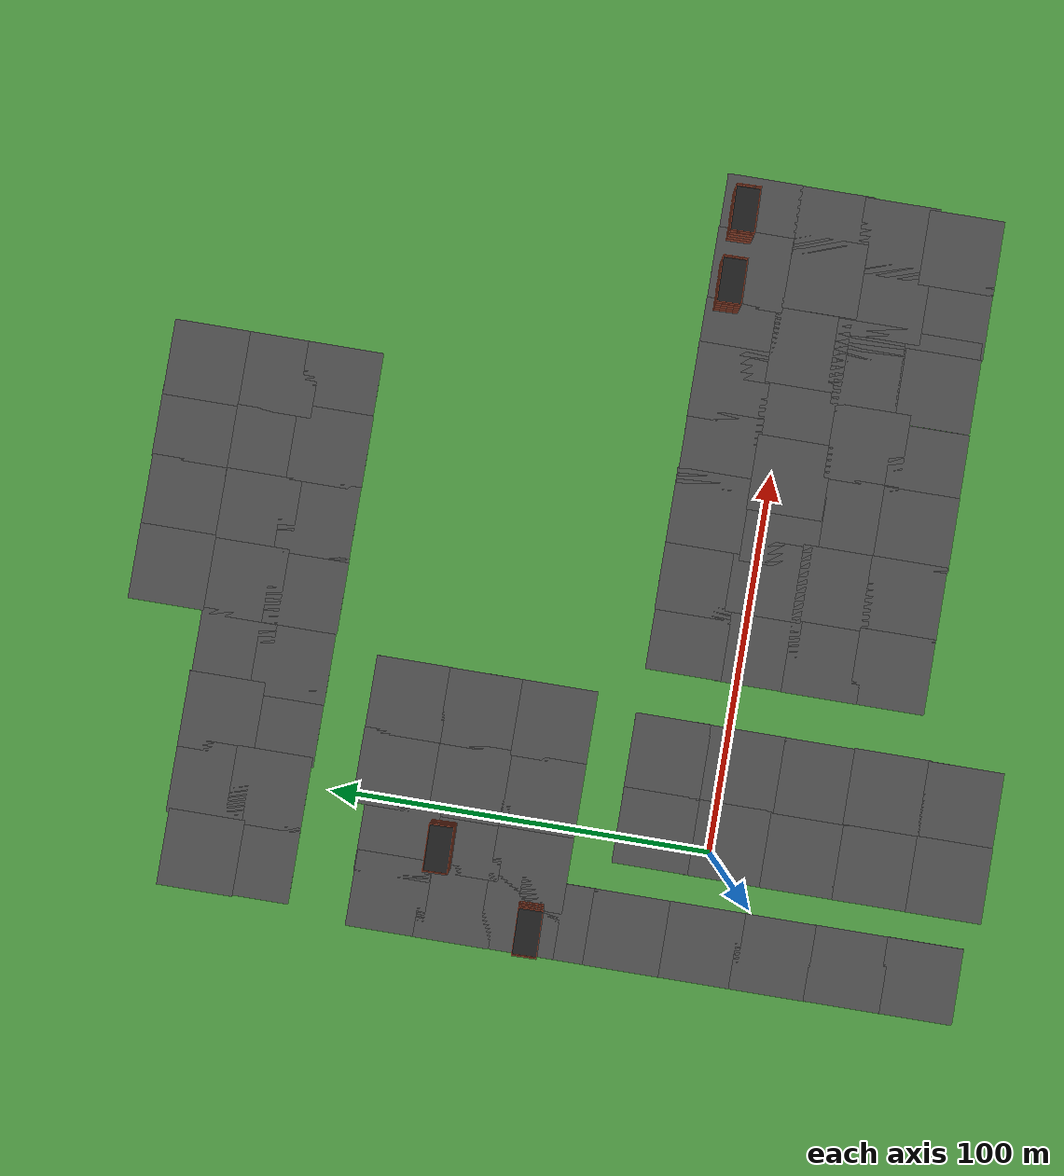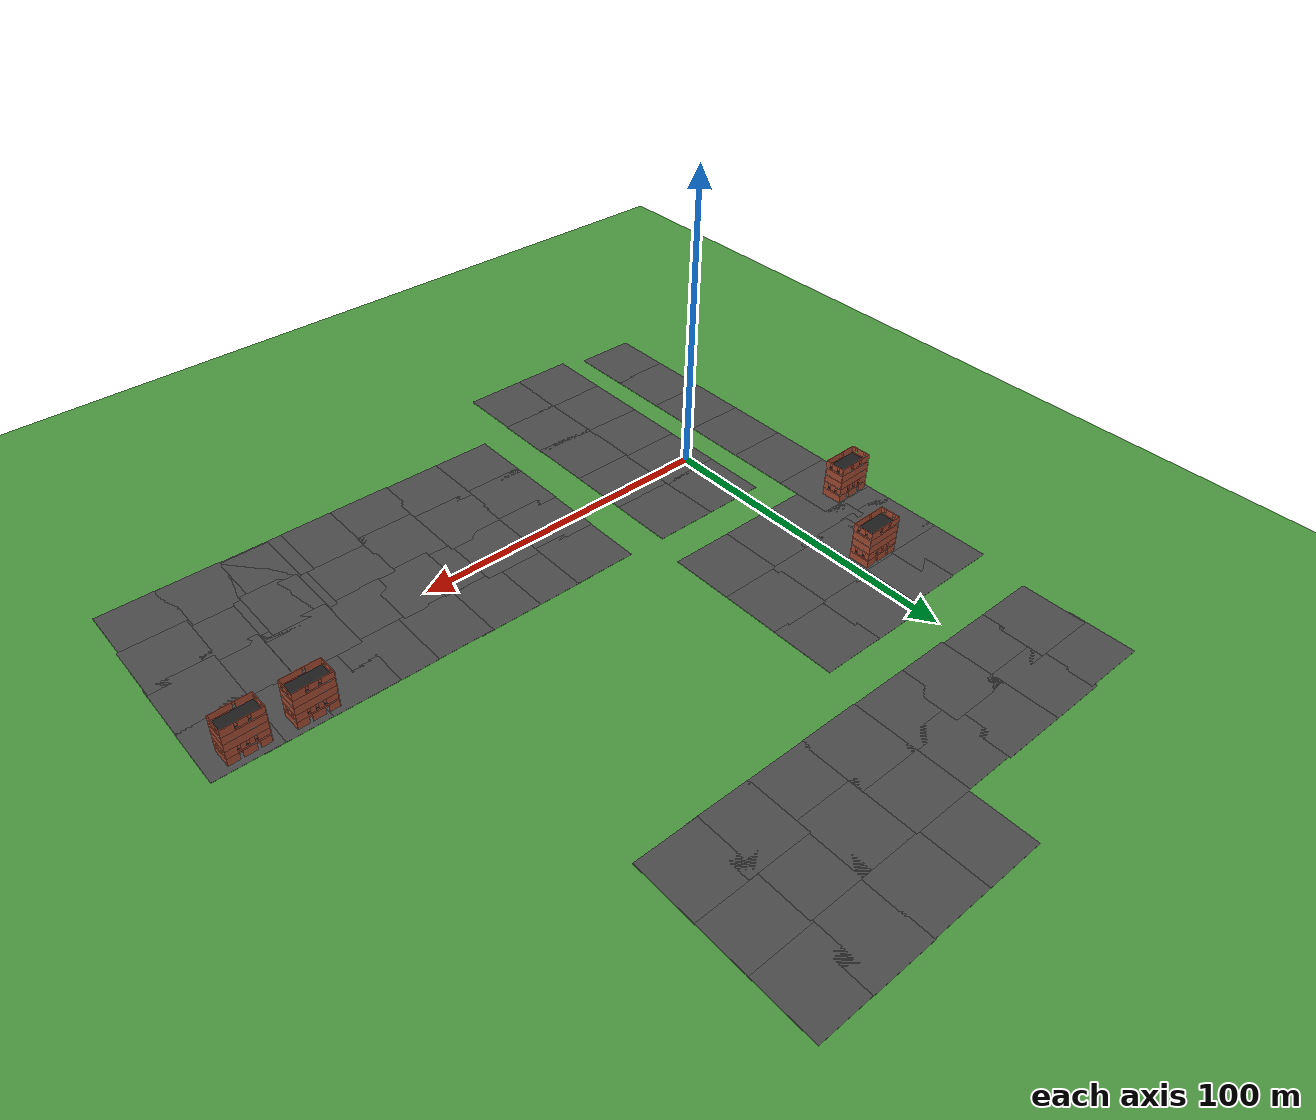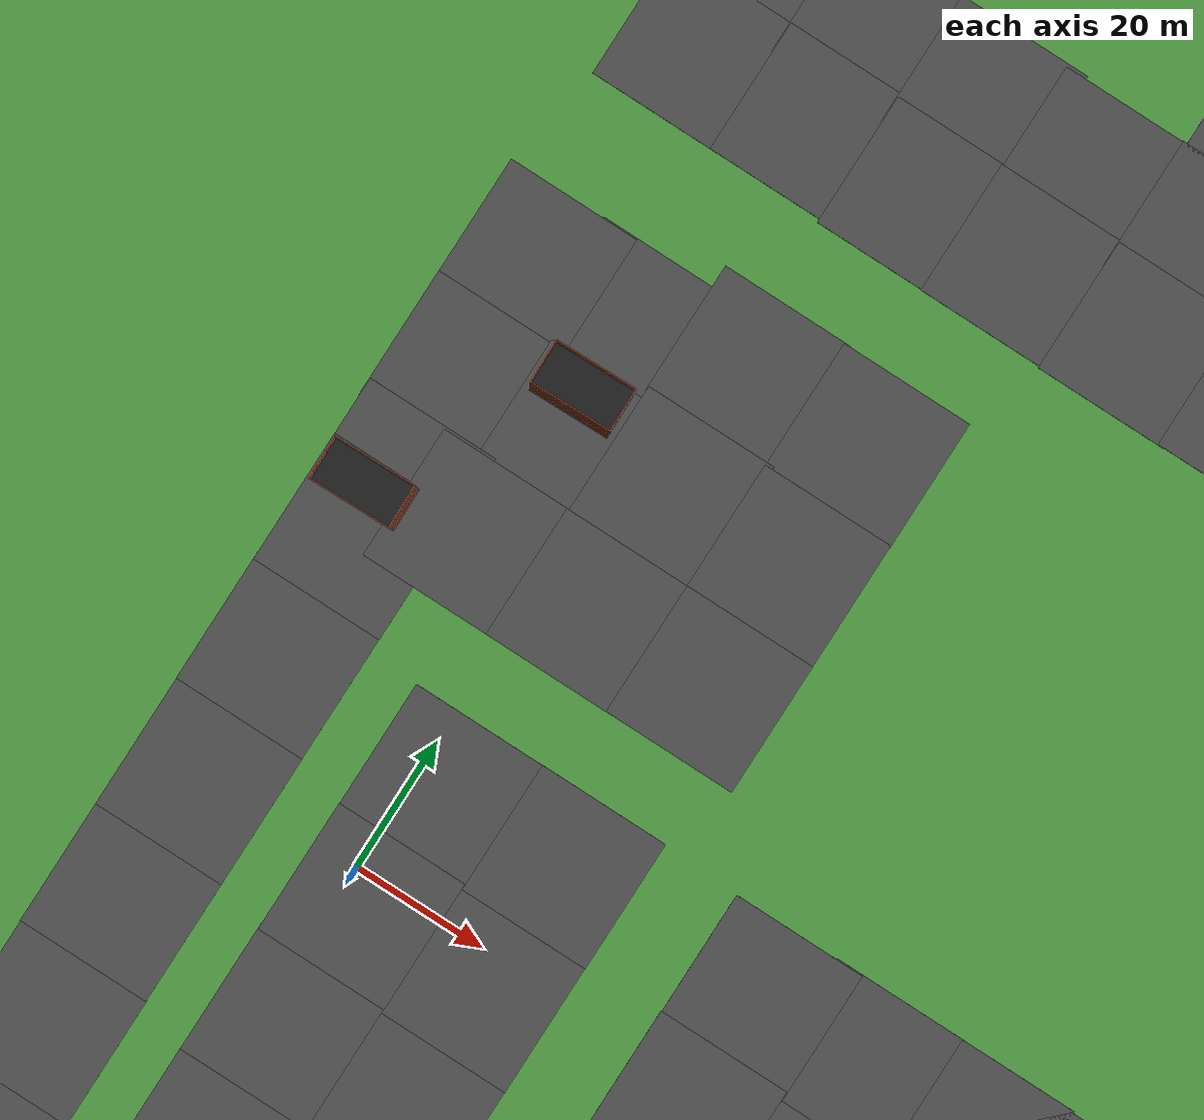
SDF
<sdf version="1.7">
 <world name="default">
  <light name="sun" type="directional">
   <pose>0 0 10 0 -0 0</pose>
   <diffuse>0.8 0.8 0.8 1</diffuse>
   <specular>0.2 0.2 0.2 1</specular>
   <attenuation>
    <range>1000</range>
    <constant>0.9</constant>
    <linear>0.01</linear>
    <quadratic>0.001</quadratic>
   </attenuation>
   <direction>-0.5 0.1 -0.9</direction>
   <spot><inner_angle>0</inner_angle><outer_angle>0</outer_angle><falloff>0</falloff></spot>
  </light>
  <scene>
   <sky><clouds><speed>0.1</speed></clouds></sky>
   <ambient>0.4 0.4 0.4 1</ambient>
   <background>0.7 0.7 0.7 1</background>
   <shadows>1</shadows>
  </scene>
  <model name="ground_plane">
   <static>1</static>
   <link name="link">
    <collision name="collision">
     <geometry><plane><normal>0 0 1</normal><size>100 100</size></plane></geometry>
     <surface>
      <contact><collide_bitmask>65535</collide_bitmask></contact>
      <friction><ode><mu>100</mu><mu2>50</mu2></ode></friction>
     </surface>
    </collision>
    <visual name="grass">
     <pose>0 0 -0.1 0 -0 0</pose>
     <cast_shadows>0</cast_shadows>
     <geometry><plane><normal>0 0 1</normal><size>1000 1000</size></plane></geometry>
     <material>
      <script><uri>file://media/materials/scripts/gazebo.material</uri><name>Gazebo/Grass</name></script>
     </material>
    </visual>
   </link>
  </model>
  <gravity>0 0 -9.8</gravity>
  <magnetic_field>6e-06 2.3e-05 -4.2e-05</magnetic_field>
  <atmosphere type="adiabatic"/>
  <physics type="dart">
   <max_step_size>0.001</max_step_size>
   <real_time_factor>1</real_time_factor>
   <real_time_update_rate>1000</real_time_update_rate>
  </physics>
  <scene><ambient>0.4 0.4 0.4 1</ambient><background>0.7 0.7 0.7 1</background><shadows>1</shadows></scene>
  <spherical_coordinates>
   <surface_model>EARTH_WGS84</surface_model>
   <latitude_deg>0</latitude_deg>
   <longitude_deg>0</longitude_deg>
   <elevation>0</elevation>
   <heading_deg>0</heading_deg>
  </spherical_coordinates>
  <model name="asphalt_plane">
   <static>1</static>
   <link name="link">
    <collision name="collision"><geometry><box><size>20 20 0.1</size></box></geometry></collision>
    <visual name="visual">
     <cast_shadows>0</cast_shadows>
     <geometry><box><size>20 20 0.1</size></box></geometry>
     <material>
      <script>
       <uri>model://asphalt_plane/materials/scripts</uri>
       <uri>model://asphalt_plane/materials/textures</uri>
       <name>vrc/asphalt</name>
      </script>
     </material>
    </visual>
   </link>
   <pose>26.7323 45.4974 0 0 -0 0</pose>
  </model>
  <model name="asphalt_plane_0">
   <static>1</static>
   <link name="link">
    <collision name="collision"><geometry><box><size>20 20 0.1</size></box></geometry></collision>
    <visual name="visual">
     <cast_shadows>0</cast_shadows>
     <geometry><box><size>20 20 0.1</size></box></geometry>
     <material>
      <script>
       <uri>model://asphalt_plane/materials/scripts</uri>
       <uri>model://asphalt_plane/materials/textures</uri>
       <name>vrc/asphalt</name>
      </script>
     </material>
    </visual>
   </link>
   <pose>7.64377 45.4686 0 0 -0 0</pose>
  </model>
  <model name="asphalt_plane_1">
   <static>1</static>
   <link name="link">
    <collision name="collision"><geometry><box><size>20 20 0.1</size></box></geometry></collision>
    <visual name="visual">
     <cast_shadows>0</cast_shadows>
     <geometry><box><size>20 20 0.1</size></box></geometry>
     <material>
      <script>
       <uri>model://asphalt_plane/materials/scripts</uri>
       <uri>model://asphalt_plane/materials/textures</uri>
       <name>vrc/asphalt</name>
      </script>
     </material>
    </visual>
   </link>
   <pose>-11.8884 45.4858 0 0 -0 0</pose>
  </model>
  <model name="asphalt_plane_2">
   <static>1</static>
   <link name="link">
    <collision name="collision"><geometry><box><size>20 20 0.1</size></box></geometry></collision>
    <visual name="visual">
     <cast_shadows>0</cast_shadows>
     <geometry><box><size>20 20 0.1</size></box></geometry>
     <material>
      <script>
       <uri>model://asphalt_plane/materials/scripts</uri>
       <uri>model://asphalt_plane/materials/textures</uri>
       <name>vrc/asphalt</name>
      </script>
     </material>
    </visual>
   </link>
   <pose>-23.8678 37.0884 0 0 -0 0</pose>
  </model>
  <model name="asphalt_plane_3">
   <static>1</static>
   <link name="link">
    <collision name="collision"><geometry><box><size>20 20 0.1</size></box></geometry></collision>
    <visual name="visual">
     <cast_shadows>0</cast_shadows>
     <geometry><box><size>20 20 0.1</size></box></geometry>
     <material>
      <script>
       <uri>model://asphalt_plane/materials/scripts</uri>
       <uri>model://asphalt_plane/materials/textures</uri>
       <name>vrc/asphalt</name>
      </script>
     </material>
    </visual>
   </link>
   <pose>-23.9043 18.1213 0 0 -0 0</pose>
  </model>
  <model name="asphalt_plane_4">
   <static>1</static>
   <link name="link">
    <collision name="collision"><geometry><box><size>20 20 0.1</size></box></geometry></collision>
    <visual name="visual">
     <cast_shadows>0</cast_shadows>
     <geometry><box><size>20 20 0.1</size></box></geometry>
     <material>
      <script>
       <uri>model://asphalt_plane/materials/scripts</uri>
       <uri>model://asphalt_plane/materials/textures</uri>
       <name>vrc/asphalt</name>
      </script>
     </material>
    </visual>
   </link>
   <pose>-23.8635 -1.81275 0 0 -0 0</pose>
  </model>
  <model name="asphalt_plane_5">
   <static>1</static>
   <link name="link">
    <collision name="collision"><geometry><box><size>20 20 0.1</size></box></geometry></collision>
    <visual name="visual">
     <cast_shadows>0</cast_shadows>
     <geometry><box><size>20 20 0.1</size></box></geometry>
     <material>
      <script>
       <uri>model://asphalt_plane/materials/scripts</uri>
       <uri>model://asphalt_plane/materials/textures</uri>
       <name>vrc/asphalt</name>
      </script>
     </material>
    </visual>
   </link>
   <pose>-23.8605 -20.3721 0 0 -0 0</pose>
  </model>
  <model name="asphalt_plane_6">
   <static>1</static>
   <link name="link">
    <collision name="collision"><geometry><box><size>20 20 0.1</size></box></geometry></collision>
    <visual name="visual">
     <cast_shadows>0</cast_shadows>
     <geometry><box><size>20 20 0.1</size></box></geometry>
     <material>
      <script>
       <uri>model://asphalt_plane/materials/scripts</uri>
       <uri>model://asphalt_plane/materials/textures</uri>
       <name>vrc/asphalt</name>
      </script>
     </material>
    </visual>
   </link>
   <pose>-23.8568 45.8423 0 0 -0 0</pose>
  </model>
  <model name="asphalt_plane_7">
   <static>1</static>
   <link name="link">
    <collision name="collision"><geometry><box><size>20 20 0.1</size></box></geometry></collision>
    <visual name="visual">
     <cast_shadows>0</cast_shadows>
     <geometry><box><size>20 20 0.1</size></box></geometry>
     <material>
      <script>
       <uri>model://asphalt_plane/materials/scripts</uri>
       <uri>model://asphalt_plane/materials/textures</uri>
       <name>vrc/asphalt</name>
      </script>
     </material>
    </visual>
   </link>
   <pose>26.7223 64.7037 0 0 -0 0</pose>
  </model>
  <model name="asphalt_plane_8">
   <static>1</static>
   <link name="link">
    <collision name="collision"><geometry><box><size>20 20 0.1</size></box></geometry></collision>
    <visual name="visual">
     <cast_shadows>0</cast_shadows>
     <geometry><box><size>20 20 0.1</size></box></geometry>
     <material>
      <script>
       <uri>model://asphalt_plane/materials/scripts</uri>
       <uri>model://asphalt_plane/materials/textures</uri>
       <name>vrc/asphalt</name>
      </script>
     </material>
    </visual>
   </link>
   <pose>7.97785 65.0899 0 0 -0 0</pose>
  </model>
  <model name="asphalt_plane_9">
   <static>1</static>
   <link name="link">
    <collision name="collision"><geometry><box><size>20 20 0.1</size></box></geometry></collision>
    <visual name="visual">
     <cast_shadows>0</cast_shadows>
     <geometry><box><size>20 20 0.1</size></box></geometry>
     <material>
      <script>
       <uri>model://asphalt_plane/materials/scripts</uri>
       <uri>model://asphalt_plane/materials/textures</uri>
       <name>vrc/asphalt</name>
      </script>
     </material>
    </visual>
   </link>
   <pose>26.7798 84.0663 0 0 -0 0</pose>
  </model>
  <model name="asphalt_plane_10">
   <static>1</static>
   <link name="link">
    <collision name="collision"><geometry><box><size>20 20 0.1</size></box></geometry></collision>
    <visual name="visual">
     <cast_shadows>0</cast_shadows>
     <geometry><box><size>20 20 0.1</size></box></geometry>
     <material>
      <script>
       <uri>model://asphalt_plane/materials/scripts</uri>
       <uri>model://asphalt_plane/materials/textures</uri>
       <name>vrc/asphalt</name>
      </script>
     </material>
    </visual>
   </link>
   <pose>7.87271 84.1708 0 0 -0 0</pose>
  </model>
  <model name="asphalt_plane_11">
   <static>1</static>
   <link name="link">
    <collision name="collision"><geometry><box><size>20 20 0.1</size></box></geometry></collision>
    <visual name="visual">
     <cast_shadows>0</cast_shadows>
     <geometry><box><size>20 20 0.1</size></box></geometry>
     <material>
      <script>
       <uri>model://asphalt_plane/materials/scripts</uri>
       <uri>model://asphalt_plane/materials/textures</uri>
       <name>vrc/asphalt</name>
      </script>
     </material>
    </visual>
   </link>
   <pose>-6.29074 63.3137 0 0 -0 0</pose>
  </model>
  <model name="asphalt_plane_12">
   <static>1</static>
   <link name="link">
    <collision name="collision"><geometry><box><size>20 20 0.1</size></box></geometry></collision>
    <visual name="visual">
     <cast_shadows>0</cast_shadows>
     <geometry><box><size>20 20 0.1</size></box></geometry>
     <material>
      <script>
       <uri>model://asphalt_plane/materials/scripts</uri>
       <uri>model://asphalt_plane/materials/textures</uri>
       <name>vrc/asphalt</name>
      </script>
     </material>
    </visual>
   </link>
   <pose>-23.9532 62.876 0 0 -0 0</pose>
  </model>
  <model name="asphalt_plane_13">
   <static>1</static>
   <link name="link">
    <collision name="collision"><geometry><box><size>20 20 0.1</size></box></geometry></collision>
    <visual name="visual">
     <cast_shadows>0</cast_shadows>
     <geometry><box><size>20 20 0.1</size></box></geometry>
     <material>
      <script>
       <uri>model://asphalt_plane/materials/scripts</uri>
       <uri>model://asphalt_plane/materials/textures</uri>
       <name>vrc/asphalt</name>
      </script>
     </material>
    </visual>
   </link>
   <pose>-23.9271 80.6464 0 0 -0 0</pose>
  </model>
  <model name="asphalt_plane_14">
   <static>1</static>
   <link name="link">
    <collision name="collision"><geometry><box><size>20 20 0.1</size></box></geometry></collision>
    <visual name="visual">
     <cast_shadows>0</cast_shadows>
     <geometry><box><size>20 20 0.1</size></box></geometry>
     <material>
      <script>
       <uri>model://asphalt_plane/materials/scripts</uri>
       <uri>model://asphalt_plane/materials/textures</uri>
       <name>vrc/asphalt</name>
      </script>
     </material>
    </visual>
   </link>
   <pose>-9.43728 80.8374 0 0 -0 0</pose>
  </model>
  <plugin name="tarot_env" filename="libtarot_env.so"><modelName>tarot_old</modelName></plugin>
  <model name="asphalt_plane_15">
   <static>1</static>
   <link name="link">
    <collision name="collision"><geometry><box><size>20 20 0.1</size></box></geometry></collision>
    <visual name="visual">
     <cast_shadows>0</cast_shadows>
     <geometry><box><size>20 20 0.1</size></box></geometry>
     <material>
      <script>
       <uri>model://asphalt_plane/materials/scripts</uri>
       <uri>model://asphalt_plane/materials/textures</uri>
       <name>vrc/asphalt</name>
      </script>
     </material>
    </visual>
   </link>
   <pose>54.6058 -4.08801 0 0 -0 0</pose>
  </model>
  <model name="asphalt_plane_16">
   <static>1</static>
   <link name="link">
    <collision name="collision"><geometry><box><size>20 20 0.1</size></box></geometry></collision>
    <visual name="visual">
     <cast_shadows>0</cast_shadows>
     <geometry><box><size>20 20 0.1</size></box></geometry>
     <material>
      <script>
       <uri>model://asphalt_plane/materials/scripts</uri>
       <uri>model://asphalt_plane/materials/textures</uri>
       <name>vrc/asphalt</name>
      </script>
     </material>
    </visual>
   </link>
   <pose>54.718 14.3936 0 0 -0 0</pose>
  </model>
  <model name="asphalt_plane_17">
   <static>1</static>
   <link name="link">
    <collision name="collision"><geometry><box><size>20 20 0.1</size></box></geometry></collision>
    <visual name="visual">
     <cast_shadows>0</cast_shadows>
     <geometry><box><size>20 20 0.1</size></box></geometry>
     <material>
      <script>
       <uri>model://asphalt_plane/materials/scripts</uri>
       <uri>model://asphalt_plane/materials/textures</uri>
       <name>vrc/asphalt</name>
      </script>
     </material>
    </visual>
   </link>
   <pose>105.064 115.51 0 0 -0 0</pose>
  </model>
  <model name="asphalt_plane_18">
   <static>1</static>
   <link name="link">
    <collision name="collision"><geometry><box><size>20 20 0.1</size></box></geometry></collision>
    <visual name="visual">
     <cast_shadows>0</cast_shadows>
     <geometry><box><size>20 20 0.1</size></box></geometry>
     <material>
      <script>
       <uri>model://asphalt_plane/materials/scripts</uri>
       <uri>model://asphalt_plane/materials/textures</uri>
       <name>vrc/asphalt</name>
      </script>
     </material>
    </visual>
   </link>
   <pose>88.3923 115.378 0 0 -0 0</pose>
  </model>
  <model name="asphalt_plane_19">
   <static>1</static>
   <link name="link">
    <collision name="collision"><geometry><box><size>20 20 0.1</size></box></geometry></collision>
    <visual name="visual">
     <cast_shadows>0</cast_shadows>
     <geometry><box><size>20 20 0.1</size></box></geometry>
     <material>
      <script>
       <uri>model://asphalt_plane/materials/scripts</uri>
       <uri>model://asphalt_plane/materials/textures</uri>
       <name>vrc/asphalt</name>
      </script>
     </material>
    </visual>
   </link>
   <pose>69.3193 115.45 0 0 -0 0</pose>
  </model>
  <model name="asphalt_plane_20">
   <static>1</static>
   <link name="link">
    <collision name="collision"><geometry><box><size>20 20 0.1</size></box></geometry></collision>
    <visual name="visual">
     <cast_shadows>0</cast_shadows>
     <geometry><box><size>20 20 0.1</size></box></geometry>
     <material>
      <script>
       <uri>model://asphalt_plane/materials/scripts</uri>
       <uri>model://asphalt_plane/materials/textures</uri>
       <name>vrc/asphalt</name>
      </script>
     </material>
    </visual>
   </link>
   <pose>50.3116 115.359 0 0 -0 0</pose>
  </model>
  <model name="asphalt_plane_21">
   <static>1</static>
   <link name="link">
    <collision name="collision"><geometry><box><size>20 20 0.1</size></box></geometry></collision>
    <visual name="visual">
     <cast_shadows>0</cast_shadows>
     <geometry><box><size>20 20 0.1</size></box></geometry>
     <material>
      <script>
       <uri>model://asphalt_plane/materials/scripts</uri>
       <uri>model://asphalt_plane/materials/textures</uri>
       <name>vrc/asphalt</name>
      </script>
     </material>
    </visual>
   </link>
   <pose>50.2162 131.314 0 0 -0 0</pose>
  </model>
  <model name="asphalt_plane_22">
   <static>1</static>
   <link name="link">
    <collision name="collision"><geometry><box><size>20 20 0.1</size></box></geometry></collision>
    <visual name="visual">
     <cast_shadows>0</cast_shadows>
     <geometry><box><size>20 20 0.1</size></box></geometry>
     <material>
      <script>
       <uri>model://asphalt_plane/materials/scripts</uri>
       <uri>model://asphalt_plane/materials/textures</uri>
       <name>vrc/asphalt</name>
      </script>
     </material>
    </visual>
   </link>
   <pose>68.7747 131.061 0 0 -0 0</pose>
  </model>
  <model name="asphalt_plane_23">
   <static>1</static>
   <link name="link">
    <collision name="collision"><geometry><box><size>20 20 0.1</size></box></geometry></collision>
    <visual name="visual">
     <cast_shadows>0</cast_shadows>
     <geometry><box><size>20 20 0.1</size></box></geometry>
     <material>
      <script>
       <uri>model://asphalt_plane/materials/scripts</uri>
       <uri>model://asphalt_plane/materials/textures</uri>
       <name>vrc/asphalt</name>
      </script>
     </material>
    </visual>
   </link>
   <pose>85.642 131.143 0 0 -0 0</pose>
  </model>
  <model name="asphalt_plane_24">
   <static>1</static>
   <link name="link">
    <collision name="collision"><geometry><box><size>20 20 0.1</size></box></geometry></collision>
    <visual name="visual">
     <cast_shadows>0</cast_shadows>
     <geometry><box><size>20 20 0.1</size></box></geometry>
     <material>
      <script>
       <uri>model://asphalt_plane/materials/scripts</uri>
       <uri>model://asphalt_plane/materials/textures</uri>
       <name>vrc/asphalt</name>
      </script>
     </material>
    </visual>
   </link>
   <pose>105.076 131.664 0 0 -0 0</pose>
  </model>
  <model name="asphalt_plane_15_clone">
   <static>1</static>
   <link name="link">
    <collision name="collision"><geometry><box><size>20 20 0.1</size></box></geometry></collision>
    <visual name="visual">
     <cast_shadows>0</cast_shadows>
     <geometry><box><size>20 20 0.1</size></box></geometry>
     <material>
      <script>
       <uri>model://asphalt_plane/materials/scripts</uri>
       <uri>model://asphalt_plane/materials/textures</uri>
       <name>vrc/asphalt</name>
      </script>
     </material>
    </visual>
   </link>
   <pose>70.5176 14.5413 0 0 -0 0</pose>
  </model>
  <model name="asphalt_plane_15_clone_0">
   <static>1</static>
   <link name="link">
    <collision name="collision"><geometry><box><size>20 20 0.1</size></box></geometry></collision>
    <visual name="visual">
     <cast_shadows>0</cast_shadows>
     <geometry><box><size>20 20 0.1</size></box></geometry>
     <material>
      <script>
       <uri>model://asphalt_plane/materials/scripts</uri>
       <uri>model://asphalt_plane/materials/textures</uri>
       <name>vrc/asphalt</name>
      </script>
     </material>
    </visual>
   </link>
   <pose>88.2896 14.5224 0 0 -0 0</pose>
  </model>
  <model name="asphalt_plane_15_clone_1">
   <static>1</static>
   <link name="link">
    <collision name="collision"><geometry><box><size>20 20 0.1</size></box></geometry></collision>
    <visual name="visual">
     <cast_shadows>0</cast_shadows>
     <geometry><box><size>20 20 0.1</size></box></geometry>
     <material>
      <script>
       <uri>model://asphalt_plane/materials/scripts</uri>
       <uri>model://asphalt_plane/materials/textures</uri>
       <name>vrc/asphalt</name>
      </script>
     </material>
    </visual>
   </link>
   <pose>104.278 14.2611 0 0 -0 0</pose>
  </model>
  <model name="asphalt_plane_15_clone_2">
   <static>1</static>
   <link name="link">
    <collision name="collision"><geometry><box><size>20 20 0.1</size></box></geometry></collision>
    <visual name="visual">
     <cast_shadows>0</cast_shadows>
     <geometry><box><size>20 20 0.1</size></box></geometry>
     <material>
      <script>
       <uri>model://asphalt_plane/materials/scripts</uri>
       <uri>model://asphalt_plane/materials/textures</uri>
       <name>vrc/asphalt</name>
      </script>
     </material>
    </visual>
   </link>
   <pose>121.903 14.3393 0 0 -0 0</pose>
  </model>
  <model name="asphalt_plane_15_clone_3">
   <static>1</static>
   <link name="link">
    <collision name="collision"><geometry><box><size>20 20 0.1</size></box></geometry></collision>
    <visual name="visual">
     <cast_shadows>0</cast_shadows>
     <geometry><box><size>20 20 0.1</size></box></geometry>
     <material>
      <script>
       <uri>model://asphalt_plane/materials/scripts</uri>
       <uri>model://asphalt_plane/materials/textures</uri>
       <name>vrc/asphalt</name>
      </script>
     </material>
    </visual>
   </link>
   <pose>133.716 14.2705 0 0 -0 0</pose>
  </model>
  <model name="asphalt_plane_15_clone_4">
   <static>1</static>
   <link name="link">
    <collision name="collision"><geometry><box><size>20 20 0.1</size></box></geometry></collision>
    <visual name="visual">
     <cast_shadows>0</cast_shadows>
     <geometry><box><size>20 20 0.1</size></box></geometry>
     <material>
      <script>
       <uri>model://asphalt_plane/materials/scripts</uri>
       <uri>model://asphalt_plane/materials/textures</uri>
       <name>vrc/asphalt</name>
      </script>
     </material>
    </visual>
   </link>
   <pose>54.5062 -21.4907 0 0 -0 0</pose>
  </model>
  <model name="asphalt_plane_15_clone_5">
   <static>1</static>
   <link name="link">
    <collision name="collision"><geometry><box><size>20 20 0.1</size></box></geometry></collision>
    <visual name="visual">
     <cast_shadows>0</cast_shadows>
     <geometry><box><size>20 20 0.1</size></box></geometry>
     <material>
      <script>
       <uri>model://asphalt_plane/materials/scripts</uri>
       <uri>model://asphalt_plane/materials/textures</uri>
       <name>vrc/asphalt</name>
      </script>
     </material>
    </visual>
   </link>
   <pose>54.535 -39.3314 0 0 -0 0</pose>
  </model>
  <model name="asphalt_plane_15_clone_7">
   <static>1</static>
   <link name="link">
    <collision name="collision"><geometry><box><size>20 20 0.1</size></box></geometry></collision>
    <visual name="visual">
     <cast_shadows>0</cast_shadows>
     <geometry><box><size>20 20 0.1</size></box></geometry>
     <material>
      <script>
       <uri>model://asphalt_plane/materials/scripts</uri>
       <uri>model://asphalt_plane/materials/textures</uri>
       <name>vrc/asphalt</name>
      </script>
     </material>
    </visual>
   </link>
   <pose>73.605 -21.2666 0 0 -0 0</pose>
  </model>
  <model name="asphalt_plane_15_clone_8">
   <static>1</static>
   <link name="link">
    <collision name="collision"><geometry><box><size>20 20 0.1</size></box></geometry></collision>
    <visual name="visual">
     <cast_shadows>0</cast_shadows>
     <geometry><box><size>20 20 0.1</size></box></geometry>
     <material>
      <script>
       <uri>model://asphalt_plane/materials/scripts</uri>
       <uri>model://asphalt_plane/materials/textures</uri>
       <name>vrc/asphalt</name>
      </script>
     </material>
    </visual>
   </link>
   <pose>73.6563 -39.4133 0 0 -0 0</pose>
  </model>
  <model name="asphalt_plane_20_clone">
   <static>1</static>
   <link name="link">
    <collision name="collision"><geometry><box><size>20 20 0.1</size></box></geometry></collision>
    <visual name="visual">
     <cast_shadows>0</cast_shadows>
     <geometry><box><size>20 20 0.1</size></box></geometry>
     <material>
      <script>
       <uri>model://asphalt_plane/materials/scripts</uri>
       <uri>model://asphalt_plane/materials/textures</uri>
       <name>vrc/asphalt</name>
      </script>
     </material>
    </visual>
   </link>
   <pose>31.5151 115.582 0 0 -0 0</pose>
  </model>
  <model name="asphalt_plane_20_clone_0">
   <static>1</static>
   <link name="link">
    <collision name="collision"><geometry><box><size>20 20 0.1</size></box></geometry></collision>
    <visual name="visual">
     <cast_shadows>0</cast_shadows>
     <geometry><box><size>20 20 0.1</size></box></geometry>
     <material>
      <script>
       <uri>model://asphalt_plane/materials/scripts</uri>
       <uri>model://asphalt_plane/materials/textures</uri>
       <name>vrc/asphalt</name>
      </script>
     </material>
    </visual>
   </link>
   <pose>31.7141 131.195 0 0 -0 0</pose>
  </model>
  <model name="asphalt_plane_20_clone_1">
   <static>1</static>
   <link name="link">
    <collision name="collision"><geometry><box><size>20 20 0.1</size></box></geometry></collision>
    <visual name="visual">
     <cast_shadows>0</cast_shadows>
     <geometry><box><size>20 20 0.1</size></box></geometry>
     <material>
      <script>
       <uri>model://asphalt_plane/materials/scripts</uri>
       <uri>model://asphalt_plane/materials/textures</uri>
       <name>vrc/asphalt</name>
      </script>
     </material>
    </visual>
   </link>
   <pose>14.9935 115.666 0 0 -0 0</pose>
  </model>
  <model name="asphalt_plane_20_clone_2">
   <static>1</static>
   <link name="link">
    <collision name="collision"><geometry><box><size>20 20 0.1</size></box></geometry></collision>
    <visual name="visual">
     <cast_shadows>0</cast_shadows>
     <geometry><box><size>20 20 0.1</size></box></geometry>
     <material>
      <script>
       <uri>model://asphalt_plane/materials/scripts</uri>
       <uri>model://asphalt_plane/materials/textures</uri>
       <name>vrc/asphalt</name>
      </script>
     </material>
    </visual>
   </link>
   <pose>14.8414 131.639 0 0 -0 0</pose>
  </model>
  <model name="asphalt_plane_20_clone_3">
   <static>1</static>
   <link name="link">
    <collision name="collision"><geometry><box><size>20 20 0.1</size></box></geometry></collision>
    <visual name="visual">
     <cast_shadows>0</cast_shadows>
     <geometry><box><size>20 20 0.1</size></box></geometry>
     <material>
      <script>
       <uri>model://asphalt_plane/materials/scripts</uri>
       <uri>model://asphalt_plane/materials/textures</uri>
       <name>vrc/asphalt</name>
      </script>
     </material>
    </visual>
   </link>
   <pose>-2.37089 116.179 0 0 -0 0</pose>
  </model>
  <model name="asphalt_plane_20_clone_4">
   <static>1</static>
   <link name="link">
    <collision name="collision"><geometry><box><size>20 20 0.1</size></box></geometry></collision>
    <visual name="visual">
     <cast_shadows>0</cast_shadows>
     <geometry><box><size>20 20 0.1</size></box></geometry>
     <material>
      <script>
       <uri>model://asphalt_plane/materials/scripts</uri>
       <uri>model://asphalt_plane/materials/textures</uri>
       <name>vrc/asphalt</name>
      </script>
     </material>
    </visual>
   </link>
   <pose>-2.52829 131.644 0 0 -0 0</pose>
  </model>
  <model name="asphalt_plane_20_clone_5">
   <static>1</static>
   <link name="link">
    <collision name="collision"><geometry><box><size>20 20 0.1</size></box></geometry></collision>
    <visual name="visual">
     <cast_shadows>0</cast_shadows>
     <geometry><box><size>20 20 0.1</size></box></geometry>
     <material>
      <script>
       <uri>model://asphalt_plane/materials/scripts</uri>
       <uri>model://asphalt_plane/materials/textures</uri>
       <name>vrc/asphalt</name>
      </script>
     </material>
    </visual>
   </link>
   <pose>-21.0183 116.161 0 0 -0 0</pose>
  </model>
  <model name="asphalt_plane_20_clone_6">
   <static>1</static>
   <link name="link">
    <collision name="collision"><geometry><box><size>20 20 0.1</size></box></geometry></collision>
    <visual name="visual">
     <cast_shadows>0</cast_shadows>
     <geometry><box><size>20 20 0.1</size></box></geometry>
     <material>
      <script>
       <uri>model://asphalt_plane/materials/scripts</uri>
       <uri>model://asphalt_plane/materials/textures</uri>
       <name>vrc/asphalt</name>
      </script>
     </material>
    </visual>
   </link>
   <pose>-21.4039 130.928 0 0 -0 0</pose>
  </model>
  <model name="asphalt_plane_24_clone">
   <static>1</static>
   <link name="link">
    <collision name="collision"><geometry><box><size>20 20 0.1</size></box></geometry></collision>
    <visual name="visual">
     <cast_shadows>0</cast_shadows>
     <geometry><box><size>20 20 0.1</size></box></geometry>
     <material>
      <script>
       <uri>model://asphalt_plane/materials/scripts</uri>
       <uri>model://asphalt_plane/materials/textures</uri>
       <name>vrc/asphalt</name>
      </script>
     </material>
    </visual>
   </link>
   <pose>105.098 151.021 0 0 -0 0</pose>
  </model>
  <model name="asphalt_plane_24_clone_0">
   <static>1</static>
   <link name="link">
    <collision name="collision"><geometry><box><size>20 20 0.1</size></box></geometry></collision>
    <visual name="visual">
     <cast_shadows>0</cast_shadows>
     <geometry><box><size>20 20 0.1</size></box></geometry>
     <material>
      <script>
       <uri>model://asphalt_plane/materials/scripts</uri>
       <uri>model://asphalt_plane/materials/textures</uri>
       <name>vrc/asphalt</name>
      </script>
     </material>
    </visual>
   </link>
   <pose>88.6654 151.107 0 0 -0 0</pose>
  </model>
  <model name="asphalt_plane_24_clone_1">
   <static>1</static>
   <link name="link">
    <collision name="collision"><geometry><box><size>20 20 0.1</size></box></geometry></collision>
    <visual name="visual">
     <cast_shadows>0</cast_shadows>
     <geometry><box><size>20 20 0.1</size></box></geometry>
     <material>
      <script>
       <uri>model://asphalt_plane/materials/scripts</uri>
       <uri>model://asphalt_plane/materials/textures</uri>
       <name>vrc/asphalt</name>
      </script>
     </material>
    </visual>
   </link>
   <pose>69.2202 150.894 0 0 -0 0</pose>
  </model>
  <model name="asphalt_plane_24_clone_2">
   <static>1</static>
   <link name="link">
    <collision name="collision"><geometry><box><size>20 20 0.1</size></box></geometry></collision>
    <visual name="visual">
     <cast_shadows>0</cast_shadows>
     <geometry><box><size>20 20 0.1</size></box></geometry>
     <material>
      <script>
       <uri>model://asphalt_plane/materials/scripts</uri>
       <uri>model://asphalt_plane/materials/textures</uri>
       <name>vrc/asphalt</name>
      </script>
     </material>
    </visual>
   </link>
   <pose>50.838 150.913 0 0 -0 0</pose>
  </model>
  <model name="asphalt_plane_15_clone_2_clone_2">
   <static>1</static>
   <link name="link">
    <collision name="collision"><geometry><box><size>20 20 0.1</size></box></geometry></collision>
    <visual name="visual">
     <cast_shadows>0</cast_shadows>
     <geometry><box><size>20 20 0.1</size></box></geometry>
     <material>
      <script>
       <uri>model://asphalt_plane/materials/scripts</uri>
       <uri>model://asphalt_plane/materials/textures</uri>
       <name>vrc/asphalt</name>
      </script>
     </material>
    </visual>
   </link>
   <pose>92.3833 -23.3758 0 0 -0 0</pose>
  </model>
  <model name="asphalt_plane_15_clone_2_clone_3">
   <static>1</static>
   <link name="link">
    <collision name="collision"><geometry><box><size>20 20 0.1</size></box></geometry></collision>
    <visual name="visual">
     <cast_shadows>0</cast_shadows>
     <geometry><box><size>20 20 0.1</size></box></geometry>
     <material>
      <script>
       <uri>model://asphalt_plane/materials/scripts</uri>
       <uri>model://asphalt_plane/materials/textures</uri>
       <name>vrc/asphalt</name>
      </script>
     </material>
    </visual>
   </link>
   <pose>111.599 -23.5947 0 0 -0 0</pose>
  </model>
  <model name="asphalt_plane_15_clone_2_clone_1">
   <static>1</static>
   <link name="link">
    <collision name="collision"><geometry><box><size>20 20 0.1</size></box></geometry></collision>
    <visual name="visual">
     <cast_shadows>0</cast_shadows>
     <geometry><box><size>20 20 0.1</size></box></geometry>
     <material>
      <script>
       <uri>model://asphalt_plane/materials/scripts</uri>
       <uri>model://asphalt_plane/materials/textures</uri>
       <name>vrc/asphalt</name>
      </script>
     </material>
    </visual>
   </link>
   <pose>134.118 -4.34987 0 0 -0 0</pose>
  </model>
  <model name="asphalt_plane_15_clone_2_clone_0">
   <static>1</static>
   <link name="link">
    <collision name="collision"><geometry><box><size>20 20 0.1</size></box></geometry></collision>
    <visual name="visual">
     <cast_shadows>0</cast_shadows>
     <geometry><box><size>20 20 0.1</size></box></geometry>
     <material>
      <script>
       <uri>model://asphalt_plane/materials/scripts</uri>
       <uri>model://asphalt_plane/materials/textures</uri>
       <name>vrc/asphalt</name>
      </script>
     </material>
    </visual>
   </link>
   <pose>117.188 -4.07273 0 0 -0 0</pose>
  </model>
  <model name="asphalt_plane_15_clone_2_clone">
   <static>1</static>
   <link name="link">
    <collision name="collision"><geometry><box><size>20 20 0.1</size></box></geometry></collision>
    <visual name="visual">
     <cast_shadows>0</cast_shadows>
     <geometry><box><size>20 20 0.1</size></box></geometry>
     <material>
      <script>
       <uri>model://asphalt_plane/materials/scripts</uri>
       <uri>model://asphalt_plane/materials/textures</uri>
       <name>vrc/asphalt</name>
      </script>
     </material>
    </visual>
   </link>
   <pose>100.276 -4.89196 0 0 -0 0</pose>
  </model>
  <model name="asphalt_plane_15_clone_2_clone_5">
   <static>1</static>
   <link name="link">
    <collision name="collision"><geometry><box><size>20 20 0.1</size></box></geometry></collision>
    <visual name="visual">
     <cast_shadows>0</cast_shadows>
     <geometry><box><size>20 20 0.1</size></box></geometry>
     <material>
      <script>
       <uri>model://asphalt_plane/materials/scripts</uri>
       <uri>model://asphalt_plane/materials/textures</uri>
       <name>vrc/asphalt</name>
      </script>
     </material>
    </visual>
   </link>
   <pose>72.9682 -3.60679 0 0 -0 0</pose>
  </model>
  <model name="asphalt_plane_15_clone_2_clone_6">
   <static>1</static>
   <link name="link">
    <collision name="collision"><geometry><box><size>20 20 0.1</size></box></geometry></collision>
    <visual name="visual">
     <cast_shadows>0</cast_shadows>
     <geometry><box><size>20 20 0.1</size></box></geometry>
     <material>
      <script>
       <uri>model://asphalt_plane/materials/scripts</uri>
       <uri>model://asphalt_plane/materials/textures</uri>
       <name>vrc/asphalt</name>
      </script>
     </material>
    </visual>
   </link>
   <pose>86.6491 -5.14218 0 0 -0 0</pose>
  </model>
  <model name="asphalt_plane_15_clone_2_clone_4">
   <static>1</static>
   <link name="link">
    <collision name="collision"><geometry><box><size>20 20 0.1</size></box></geometry></collision>
    <visual name="visual">
     <cast_shadows>0</cast_shadows>
     <geometry><box><size>20 20 0.1</size></box></geometry>
     <material>
      <script>
       <uri>model://asphalt_plane/materials/scripts</uri>
       <uri>model://asphalt_plane/materials/textures</uri>
       <name>vrc/asphalt</name>
      </script>
     </material>
    </visual>
   </link>
   <pose>131.281 -22.1535 0 0 -0 0</pose>
  </model>
  <model name="asphalt_plane_15_clone_2_clone_7">
   <static>1</static>
   <link name="link">
    <collision name="collision"><geometry><box><size>20 20 0.1</size></box></geometry></collision>
    <visual name="visual">
     <cast_shadows>0</cast_shadows>
     <geometry><box><size>20 20 0.1</size></box></geometry>
     <material>
      <script>
       <uri>model://asphalt_plane/materials/scripts</uri>
       <uri>model://asphalt_plane/materials/textures</uri>
       <name>vrc/asphalt</name>
      </script>
     </material>
    </visual>
   </link>
   <pose>92.1022 -39.6823 0 0 -0 0</pose>
  </model>
  <model name="asphalt_plane_15_clone_2_clone_8">
   <static>1</static>
   <link name="link">
    <collision name="collision"><geometry><box><size>20 20 0.1</size></box></geometry></collision>
    <visual name="visual">
     <cast_shadows>0</cast_shadows>
     <geometry><box><size>20 20 0.1</size></box></geometry>
     <material>
      <script>
       <uri>model://asphalt_plane/materials/scripts</uri>
       <uri>model://asphalt_plane/materials/textures</uri>
       <name>vrc/asphalt</name>
      </script>
     </material>
    </visual>
   </link>
   <pose>108.868 -39.6334 0 0 -0 0</pose>
  </model>
  <model name="asphalt_plane_15_clone_2_clone_9">
   <static>1</static>
   <link name="link">
    <collision name="collision"><geometry><box><size>20 20 0.1</size></box></geometry></collision>
    <visual name="visual">
     <cast_shadows>0</cast_shadows>
     <geometry><box><size>20 20 0.1</size></box></geometry>
     <material>
      <script>
       <uri>model://asphalt_plane/materials/scripts</uri>
       <uri>model://asphalt_plane/materials/textures</uri>
       <name>vrc/asphalt</name>
      </script>
     </material>
    </visual>
   </link>
   <pose>128.92 -39.5345 0 0 -0 0</pose>
  </model>
  <model name="asphalt_plane_15_clone_2_clone_10">
   <static>1</static>
   <link name="link">
    <collision name="collision"><geometry><box><size>20 20 0.1</size></box></geometry></collision>
    <visual name="visual">
     <cast_shadows>0</cast_shadows>
     <geometry><box><size>20 20 0.1</size></box></geometry>
     <material>
      <script>
       <uri>model://asphalt_plane/materials/scripts</uri>
       <uri>model://asphalt_plane/materials/textures</uri>
       <name>vrc/asphalt</name>
      </script>
     </material>
    </visual>
   </link>
   <pose>133.337 -39.1111 0 0 -0 0</pose>
  </model>
  <model name="asphalt_plane_15_clone_2_clone_11">
   <static>1</static>
   <link name="link">
    <collision name="collision"><geometry><box><size>20 20 0.1</size></box></geometry></collision>
    <visual name="visual">
     <cast_shadows>0</cast_shadows>
     <geometry><box><size>20 20 0.1</size></box></geometry>
     <material>
      <script>
       <uri>model://asphalt_plane/materials/scripts</uri>
       <uri>model://asphalt_plane/materials/textures</uri>
       <name>vrc/asphalt</name>
      </script>
     </material>
    </visual>
   </link>
   <pose>133.916 -20.8174 0 0 -0 0</pose>
  </model>
  <model name="asphalt_plane_15_clone_3_clone">
   <static>1</static>
   <link name="link">
    <collision name="collision"><geometry><box><size>20 20 0.1</size></box></geometry></collision>
    <visual name="visual">
     <cast_shadows>0</cast_shadows>
     <geometry><box><size>20 20 0.1</size></box></geometry>
     <material>
      <script>
       <uri>model://asphalt_plane/materials/scripts</uri>
       <uri>model://asphalt_plane/materials/textures</uri>
       <name>vrc/asphalt</name>
      </script>
     </material>
    </visual>
   </link>
   <pose>152.616 14.179 0 0 -0 0</pose>
  </model>
  <model name="asphalt_plane_15_clone_3_clone_0">
   <static>1</static>
   <link name="link">
    <collision name="collision"><geometry><box><size>20 20 0.1</size></box></geometry></collision>
    <visual name="visual">
     <cast_shadows>0</cast_shadows>
     <geometry><box><size>20 20 0.1</size></box></geometry>
     <material>
      <script>
       <uri>model://asphalt_plane/materials/scripts</uri>
       <uri>model://asphalt_plane/materials/textures</uri>
       <name>vrc/asphalt</name>
      </script>
     </material>
    </visual>
   </link>
   <pose>166.88 14.0055 0 0 -0 0</pose>
  </model>
  <model name="asphalt_plane_15_clone_3_clone_1">
   <static>1</static>
   <link name="link">
    <collision name="collision"><geometry><box><size>20 20 0.1</size></box></geometry></collision>
    <visual name="visual">
     <cast_shadows>0</cast_shadows>
     <geometry><box><size>20 20 0.1</size></box></geometry>
     <material>
      <script>
       <uri>model://asphalt_plane/materials/scripts</uri>
       <uri>model://asphalt_plane/materials/textures</uri>
       <name>vrc/asphalt</name>
      </script>
     </material>
    </visual>
   </link>
   <pose>154.147 -5.42773 0 0 -0 0</pose>
  </model>
  <model name="asphalt_plane_15_clone_3_clone_2">
   <static>1</static>
   <link name="link">
    <collision name="collision"><geometry><box><size>20 20 0.1</size></box></geometry></collision>
    <visual name="visual">
     <cast_shadows>0</cast_shadows>
     <geometry><box><size>20 20 0.1</size></box></geometry>
     <material>
      <script>
       <uri>model://asphalt_plane/materials/scripts</uri>
       <uri>model://asphalt_plane/materials/textures</uri>
       <name>vrc/asphalt</name>
      </script>
     </material>
    </visual>
   </link>
   <pose>166.78 -5.45686 0 0 -0 0</pose>
  </model>
  <model name="asphalt_plane_15_clone_3_clone_3">
   <static>1</static>
   <link name="link">
    <collision name="collision"><geometry><box><size>20 20 0.1</size></box></geometry></collision>
    <visual name="visual">
     <cast_shadows>0</cast_shadows>
     <geometry><box><size>20 20 0.1</size></box></geometry>
     <material>
      <script>
       <uri>model://asphalt_plane/materials/scripts</uri>
       <uri>model://asphalt_plane/materials/textures</uri>
       <name>vrc/asphalt</name>
      </script>
     </material>
    </visual>
   </link>
   <pose>150.057 -22.8155 0 0 -0 0</pose>
  </model>
  <model name="asphalt_plane_15_clone_3_clone_4">
   <static>1</static>
   <link name="link">
    <collision name="collision"><geometry><box><size>20 20 0.1</size></box></geometry></collision>
    <visual name="visual">
     <cast_shadows>0</cast_shadows>
     <geometry><box><size>20 20 0.1</size></box></geometry>
     <material>
      <script>
       <uri>model://asphalt_plane/materials/scripts</uri>
       <uri>model://asphalt_plane/materials/textures</uri>
       <name>vrc/asphalt</name>
      </script>
     </material>
    </visual>
   </link>
   <pose>166.545 -22.7493 0 0 -0 0</pose>
  </model>
  <model name="asphalt_plane_15_clone_3_clone_5">
   <static>1</static>
   <link name="link">
    <collision name="collision"><geometry><box><size>20 20 0.1</size></box></geometry></collision>
    <visual name="visual">
     <cast_shadows>0</cast_shadows>
     <geometry><box><size>20 20 0.1</size></box></geometry>
     <material>
      <script>
       <uri>model://asphalt_plane/materials/scripts</uri>
       <uri>model://asphalt_plane/materials/textures</uri>
       <name>vrc/asphalt</name>
      </script>
     </material>
    </visual>
   </link>
   <pose>148.419 -39.8298 0 0 -0 0</pose>
  </model>
  <model name="asphalt_plane_15_clone_3_clone_6">
   <static>1</static>
   <link name="link">
    <collision name="collision"><geometry><box><size>20 20 0.1</size></box></geometry></collision>
    <visual name="visual">
     <cast_shadows>0</cast_shadows>
     <geometry><box><size>20 20 0.1</size></box></geometry>
     <material>
      <script>
       <uri>model://asphalt_plane/materials/scripts</uri>
       <uri>model://asphalt_plane/materials/textures</uri>
       <name>vrc/asphalt</name>
      </script>
     </material>
    </visual>
   </link>
   <pose>166.035 -39.9329 0 0 -0 0</pose>
  </model>
  <model name="my_building_1">
   <link name="Floor_13">
    <pose>-4.12557 0 2.5 0 -0 0</pose>
    <inertial>
     <mass>1</mass>
     <inertia><ixx>1</ixx><ixy>0</ixy><ixz>0</ixz><iyy>1</iyy><iyz>0</iyz><izz>1</izz></inertia>
    </inertial>
    <visual name="Floor_13_Visual">
     <pose>0 0 0.05 0 -0 0</pose>
     <geometry><box><size>6.5 12.25 0.1</size></box></geometry>
     <material>
      <script><uri>file://media/materials/scripts/gazebo.material</uri><name>Gazebo/Black</name></script>
      <ambient>1 1 1 1</ambient>
      <shader type="pixel"><normal_map>__default__</normal_map></shader>
      <diffuse>0 0 0 1</diffuse>
      <specular>0.1 0.1 0.1 1</specular>
      <emissive>0 0 0 1</emissive>
     </material>
     <meta><layer>1</layer></meta>
    </visual>
    <collision name="Floor_13_Collision">
     <pose>0 0 0.05 0 -0 0</pose>
     <geometry><box><size>6.5 12.25 0.1</size></box></geometry>
     <surface>
      <friction>
       <ode><mu>1</mu><mu2>1</mu2><fdir1>0 0 0</fdir1><slip1>0</slip1><slip2>0</slip2></ode>
       <torsional>
        <coefficient>1</coefficient>
        <patch_radius>0</patch_radius>
        <surface_radius>0</surface_radius>
        <use_patch_radius>1</use_patch_radius>
        <ode><slip>0</slip></ode>
       </torsional>
      </friction>
      <bounce><restitution_coefficient>0</restitution_coefficient><threshold>1e+06</threshold></bounce>
      <contact>
       <collide_without_contact>0</collide_without_contact>
       <collide_without_contact_bitmask>1</collide_without_contact_bitmask>
       <collide_bitmask>1</collide_bitmask>
       <ode>
        <soft_cfm>0</soft_cfm>
        <soft_erp>0.2</soft_erp>
        <kp>1e+13</kp>
        <kd>1</kd>
        <max_vel>0.01</max_vel>
        <min_depth>0</min_depth>
       </ode>
       <bullet>
        <split_impulse>1</split_impulse>
        <split_impulse_penetration_threshold>-0.01</split_impulse_penetration_threshold>
        <soft_cfm>0</soft_cfm>
        <soft_erp>0.2</soft_erp>
        <kp>1e+13</kp>
        <kd>1</kd>
       </bullet>
      </contact>
     </surface>
    </collision>
   </link>
   <link name="Floor_14">
    <pose>-4.12557 0 5 0 -0 0</pose>
    <visual name="Floor_14_Visual">
     <pose>0 0 0.05 0 -0 0</pose>
     <geometry><box><size>6.5 12.25 0.1</size></box></geometry>
     <material>
      <script><uri>file://media/materials/scripts/gazebo.material</uri><name>Gazebo/Grey</name></script>
      <ambient>1 1 1 1</ambient>
      <shader type="pixel"/>
     </material>
     <meta><layer>2</layer></meta>
    </visual>
    <collision name="Floor_14_Collision">
     <pose>0 0 0.05 0 -0 0</pose>
     <geometry><box><size>6.5 12.25 0.1</size></box></geometry>
     <surface>
      <friction>
       <ode><mu>1</mu><mu2>1</mu2><fdir1>0 0 0</fdir1><slip1>0</slip1><slip2>0</slip2></ode>
       <torsional>
        <coefficient>1</coefficient>
        <patch_radius>0</patch_radius>
        <surface_radius>0</surface_radius>
        <use_patch_radius>1</use_patch_radius>
        <ode><slip>0</slip></ode>
       </torsional>
      </friction>
      <bounce><restitution_coefficient>0</restitution_coefficient><threshold>1e+06</threshold></bounce>
      <contact>
       <collide_without_contact>0</collide_without_contact>
       <collide_without_contact_bitmask>1</collide_without_contact_bitmask>
       <collide_bitmask>1</collide_bitmask>
       <ode>
        <soft_cfm>0</soft_cfm>
        <soft_erp>0.2</soft_erp>
        <kp>1e+13</kp>
        <kd>1</kd>
        <max_vel>0.01</max_vel>
        <min_depth>0</min_depth>
       </ode>
       <bullet>
        <split_impulse>1</split_impulse>
        <split_impulse_penetration_threshold>-0.01</split_impulse_penetration_threshold>
        <soft_cfm>0</soft_cfm>
        <soft_erp>0.2</soft_erp>
        <kp>1e+13</kp>
        <kd>1</kd>
       </bullet>
      </contact>
     </surface>
    </collision>
   </link>
   <link name="Floor_15">
    <pose>-4.12557 0 7.5 0 -0 0</pose>
    <visual name="Floor_15_Visual">
     <pose>0 0 0.05 0 -0 0</pose>
     <geometry><box><size>6.5 12.25 0.1</size></box></geometry>
     <material>
      <script><uri>file://media/materials/scripts/gazebo.material</uri><name>Gazebo/Grey</name></script>
      <ambient>1 1 1 1</ambient>
      <shader type="pixel"/>
     </material>
     <meta><layer>3</layer></meta>
    </visual>
    <collision name="Floor_15_Collision">
     <pose>0 0 0.05 0 -0 0</pose>
     <geometry><box><size>6.5 12.25 0.1</size></box></geometry>
     <surface>
      <friction>
       <ode><mu>1</mu><mu2>1</mu2><fdir1>0 0 0</fdir1><slip1>0</slip1><slip2>0</slip2></ode>
       <torsional>
        <coefficient>1</coefficient>
        <patch_radius>0</patch_radius>
        <surface_radius>0</surface_radius>
        <use_patch_radius>1</use_patch_radius>
        <ode><slip>0</slip></ode>
       </torsional>
      </friction>
      <bounce><restitution_coefficient>0</restitution_coefficient><threshold>1e+06</threshold></bounce>
      <contact>
       <collide_without_contact>0</collide_without_contact>
       <collide_without_contact_bitmask>1</collide_without_contact_bitmask>
       <collide_bitmask>1</collide_bitmask>
       <ode>
        <soft_cfm>0</soft_cfm>
        <soft_erp>0.2</soft_erp>
        <kp>1e+13</kp>
        <kd>1</kd>
        <max_vel>0.01</max_vel>
        <min_depth>0</min_depth>
       </ode>
       <bullet>
        <split_impulse>1</split_impulse>
        <split_impulse_penetration_threshold>-0.01</split_impulse_penetration_threshold>
        <soft_cfm>0</soft_cfm>
        <soft_erp>0.2</soft_erp>
        <kp>1e+13</kp>
        <kd>1</kd>
       </bullet>
      </contact>
     </surface>
    </collision>
   </link>
   <link name="Floor_16">
    <pose>-4.12557 0 10 0 -0 0</pose>
    <inertial>
     <mass>1</mass>
     <inertia><ixx>1</ixx><ixy>0</ixy><ixz>0</ixz><iyy>1</iyy><iyz>0</iyz><izz>1</izz></inertia>
    </inertial>
    <visual name="Floor_16_Visual">
     <pose>0 0 0.05 0 -0 0</pose>
     <geometry><box><size>6.5 12.25 0.1</size></box></geometry>
     <material>
      <script><uri>file://media/materials/scripts/gazebo.material</uri><name>Gazebo/Black</name></script>
      <ambient>1 1 1 1</ambient>
      <shader type="pixel"><normal_map>__default__</normal_map></shader>
      <diffuse>0 0 0 1</diffuse>
      <specular>0.1 0.1 0.1 1</specular>
      <emissive>0 0 0 1</emissive>
     </material>
     <meta><layer>4</layer></meta>
    </visual>
    <collision name="Floor_16_Collision">
     <pose>0 0 0.05 0 -0 0</pose>
     <geometry><box><size>6.5 12.25 0.1</size></box></geometry>
     <surface>
      <friction>
       <ode><mu>1</mu><mu2>1</mu2><fdir1>0 0 0</fdir1><slip1>0</slip1><slip2>0</slip2></ode>
       <torsional>
        <coefficient>1</coefficient>
        <patch_radius>0</patch_radius>
        <surface_radius>0</surface_radius>
        <use_patch_radius>1</use_patch_radius>
        <ode><slip>0</slip></ode>
       </torsional>
      </friction>
      <bounce><restitution_coefficient>0</restitution_coefficient><threshold>1e+06</threshold></bounce>
      <contact>
       <collide_without_contact>0</collide_without_contact>
       <collide_without_contact_bitmask>1</collide_without_contact_bitmask>
       <collide_bitmask>1</collide_bitmask>
       <ode>
        <soft_cfm>0</soft_cfm>
        <soft_erp>0.2</soft_erp>
        <kp>1e+13</kp>
        <kd>1</kd>
        <max_vel>0.01</max_vel>
        <min_depth>0</min_depth>
       </ode>
       <bullet>
        <split_impulse>1</split_impulse>
        <split_impulse_penetration_threshold>-0.01</split_impulse_penetration_threshold>
        <soft_cfm>0</soft_cfm>
        <soft_erp>0.2</soft_erp>
        <kp>1e+13</kp>
        <kd>1</kd>
       </bullet>
      </contact>
     </surface>
    </collision>
   </link>
   <link name="Wall_18">
    <pose>-4.12557 -6.05 0 0 -0 0</pose>
    <visual name="Wall_18_Visual">
     <pose>0 0 1.25 0 -0 0</pose>
     <geometry><box><size>6.5 0.15 2.5</size></box></geometry>
     <material>
      <script><uri>file://media/materials/scripts/gazebo.material</uri><name>Gazebo/Bricks</name></script>
      <ambient>1 1 1 1</ambient>
      <shader type="pixel"/>
     </material>
     <meta><layer>0</layer></meta>
    </visual>
    <collision name="Wall_18_Collision">
     <pose>0 0 1.25 0 -0 0</pose>
     <geometry><box><size>6.5 0.15 2.5</size></box></geometry>
     <surface>
      <friction>
       <ode><mu>1</mu><mu2>1</mu2><fdir1>0 0 0</fdir1><slip1>0</slip1><slip2>0</slip2></ode>
       <torsional>
        <coefficient>1</coefficient>
        <patch_radius>0</patch_radius>
        <surface_radius>0</surface_radius>
        <use_patch_radius>1</use_patch_radius>
        <ode><slip>0</slip></ode>
       </torsional>
      </friction>
      <bounce><restitution_coefficient>0</restitution_coefficient><threshold>1e+06</threshold></bounce>
      <contact>
       <collide_without_contact>0</collide_without_contact>
       <collide_without_contact_bitmask>1</collide_without_contact_bitmask>
       <collide_bitmask>1</collide_bitmask>
       <ode>
        <soft_cfm>0</soft_cfm>
        <soft_erp>0.2</soft_erp>
        <kp>1e+13</kp>
        <kd>1</kd>
        <max_vel>0.01</max_vel>
        <min_depth>0</min_depth>
       </ode>
       <bullet>
        <split_impulse>1</split_impulse>
        <split_impulse_penetration_threshold>-0.01</split_impulse_penetration_threshold>
        <soft_cfm>0</soft_cfm>
        <soft_erp>0.2</soft_erp>
        <kp>1e+13</kp>
        <kd>1</kd>
       </bullet>
      </contact>
     </surface>
    </collision>
   </link>
   <link name="Wall_19">
    <pose>-0.950574 0 0 0 -0 1.5708</pose>
    <visual name="Wall_19_Visual_3">
     <pose>-2.20979 0 2.25 0 -0 0</pose>
     <geometry><box><size>0.9 0.15 0.5</size></box></geometry>
     <material>
      <script><uri>file://media/materials/scripts/gazebo.material</uri><name>Gazebo/Bricks</name></script>
      <ambient>1 1 1 1</ambient>
      <shader type="pixel"/>
     </material>
     <meta><layer>0</layer></meta>
    </visual>
    <visual name="Wall_19_Visual_2">
     <pose>4.53056 0 1.25 0 -0 0</pose>
     <geometry><box><size>3.18887 0.15 2.5</size></box></geometry>
     <material>
      <script><uri>file://media/materials/scripts/gazebo.material</uri><name>Gazebo/Bricks</name></script>
      <ambient>1 1 1 1</ambient>
      <shader type="pixel"/>
     </material>
     <meta><layer>0</layer></meta>
    </visual>
    <visual name="Wall_19_Visual_4">
     <pose>2.48613 0 2.25 0 -0 0</pose>
     <geometry><box><size>0.9 0.15 0.5</size></box></geometry>
     <material>
      <script><uri>file://media/materials/scripts/gazebo.material</uri><name>Gazebo/Bricks</name></script>
      <ambient>1 1 1 1</ambient>
      <shader type="pixel"/>
     </material>
     <meta><layer>0</layer></meta>
    </visual>
    <visual name="Wall_19_Visual_1">
     <pose>0.138171 0 1.25 0 -0 0</pose>
     <geometry><box><size>3.79591 0.15 2.5</size></box></geometry>
     <material>
      <script><uri>file://media/materials/scripts/gazebo.material</uri><name>Gazebo/Bricks</name></script>
      <ambient>1 1 1 1</ambient>
      <shader type="pixel"/>
     </material>
     <meta><layer>0</layer></meta>
    </visual>
    <visual name="Wall_19_Visual_0">
     <pose>-4.39239 0 1.25 0 -0 0</pose>
     <geometry><box><size>3.46522 0.15 2.5</size></box></geometry>
     <material>
      <script><uri>file://media/materials/scripts/gazebo.material</uri><name>Gazebo/Bricks</name></script>
      <ambient>1 1 1 1</ambient>
      <shader type="pixel"/>
     </material>
     <meta><layer>0</layer></meta>
    </visual>
    <collision name="Wall_19_Collision_0">
     <pose>-4.39239 0 1.25 0 -0 0</pose>
     <geometry><box><size>3.46522 0.15 2.5</size></box></geometry>
     <surface>
      <friction>
       <ode><mu>1</mu><mu2>1</mu2><fdir1>0 0 0</fdir1><slip1>0</slip1><slip2>0</slip2></ode>
       <torsional>
        <coefficient>1</coefficient>
        <patch_radius>0</patch_radius>
        <surface_radius>0</surface_radius>
        <use_patch_radius>1</use_patch_radius>
        <ode><slip>0</slip></ode>
       </torsional>
      </friction>
      <bounce><restitution_coefficient>0</restitution_coefficient><threshold>1e+06</threshold></bounce>
      <contact>
       <collide_without_contact>0</collide_without_contact>
       <collide_without_contact_bitmask>1</collide_without_contact_bitmask>
       <collide_bitmask>1</collide_bitmask>
       <ode>
        <soft_cfm>0</soft_cfm>
        <soft_erp>0.2</soft_erp>
        <kp>1e+13</kp>
        <kd>1</kd>
        <max_vel>0.01</max_vel>
        <min_depth>0</min_depth>
       </ode>
       <bullet>
        <split_impulse>1</split_impulse>
        <split_impulse_penetration_threshold>-0.01</split_impulse_penetration_threshold>
        <soft_cfm>0</soft_cfm>
        <soft_erp>0.2</soft_erp>
        <kp>1e+13</kp>
        <kd>1</kd>
       </bullet>
      </contact>
     </surface>
    </collision>
    <collision name="Wall_19_Collision_2">
     <pose>4.53056 0 1.25 0 -0 0</pose>
     <geometry><box><size>3.18887 0.15 2.5</size></box></geometry>
     <surface>
      <friction>
       <ode><mu>1</mu><mu2>1</mu2><fdir1>0 0 0</fdir1><slip1>0</slip1><slip2>0</slip2></ode>
       <torsional>
        <coefficient>1</coefficient>
        <patch_radius>0</patch_radius>
        <surface_radius>0</surface_radius>
        <use_patch_radius>1</use_patch_radius>
        <ode><slip>0</slip></ode>
       </torsional>
      </friction>
      <bounce><restitution_coefficient>0</restitution_coefficient><threshold>1e+06</threshold></bounce>
      <contact>
       <collide_without_contact>0</collide_without_contact>
       <collide_without_contact_bitmask>1</collide_without_contact_bitmask>
       <collide_bitmask>1</collide_bitmask>
       <ode>
        <soft_cfm>0</soft_cfm>
        <soft_erp>0.2</soft_erp>
        <kp>1e+13</kp>
        <kd>1</kd>
        <max_vel>0.01</max_vel>
        <min_depth>0</min_depth>
       </ode>
       <bullet>
        <split_impulse>1</split_impulse>
        <split_impulse_penetration_threshold>-0.01</split_impulse_penetration_threshold>
        <soft_cfm>0</soft_cfm>
        <soft_erp>0.2</soft_erp>
        <kp>1e+13</kp>
        <kd>1</kd>
       </bullet>
      </contact>
     </surface>
    </collision>
    <collision name="Wall_19_Collision_4">
     <pose>2.48613 0 2.25 0 -0 0</pose>
     <geometry><box><size>0.9 0.15 0.5</size></box></geometry>
     <surface>
      <friction>
       <ode><mu>1</mu><mu2>1</mu2><fdir1>0 0 0</fdir1><slip1>0</slip1><slip2>0</slip2></ode>
       <torsional>
        <coefficient>1</coefficient>
        <patch_radius>0</patch_radius>
        <surface_radius>0</surface_radius>
        <use_patch_radius>1</use_patch_radius>
        <ode><slip>0</slip></ode>
       </torsional>
      </friction>
      <bounce><restitution_coefficient>0</restitution_coefficient><threshold>1e+06</threshold></bounce>
      <contact>
       <collide_without_contact>0</collide_without_contact>
       <collide_without_contact_bitmask>1</collide_without_contact_bitmask>
       <collide_bitmask>1</collide_bitmask>
       <ode>
        <soft_cfm>0</soft_cfm>
        <soft_erp>0.2</soft_erp>
        <kp>1e+13</kp>
        <kd>1</kd>
        <max_vel>0.01</max_vel>
        <min_depth>0</min_depth>
       </ode>
       <bullet>
        <split_impulse>1</split_impulse>
        <split_impulse_penetration_threshold>-0.01</split_impulse_penetration_threshold>
        <soft_cfm>0</soft_cfm>
        <soft_erp>0.2</soft_erp>
        <kp>1e+13</kp>
        <kd>1</kd>
       </bullet>
      </contact>
     </surface>
    </collision>
    <collision name="Wall_19_Collision_3">
     <pose>-2.20979 0 2.25 0 -0 0</pose>
     <geometry><box><size>0.9 0.15 0.5</size></box></geometry>
     <surface>
      <friction>
       <ode><mu>1</mu><mu2>1</mu2><fdir1>0 0 0</fdir1><slip1>0</slip1><slip2>0</slip2></ode>
       <torsional>
        <coefficient>1</coefficient>
        <patch_radius>0</patch_radius>
        <surface_radius>0</surface_radius>
        <use_patch_radius>1</use_patch_radius>
        <ode><slip>0</slip></ode>
       </torsional>
      </friction>
      <bounce><restitution_coefficient>0</restitution_coefficient><threshold>1e+06</threshold></bounce>
      <contact>
       <collide_without_contact>0</collide_without_contact>
       <collide_without_contact_bitmask>1</collide_without_contact_bitmask>
       <collide_bitmask>1</collide_bitmask>
       <ode>
        <soft_cfm>0</soft_cfm>
        <soft_erp>0.2</soft_erp>
        <kp>1e+13</kp>
        <kd>1</kd>
        <max_vel>0.01</max_vel>
        <min_depth>0</min_depth>
       </ode>
       <bullet>
        <split_impulse>1</split_impulse>
        <split_impulse_penetration_threshold>-0.01</split_impulse_penetration_threshold>
        <soft_cfm>0</soft_cfm>
        <soft_erp>0.2</soft_erp>
        <kp>1e+13</kp>
        <kd>1</kd>
       </bullet>
      </contact>
     </surface>
    </collision>
    <collision name="Wall_19_Collision_1">
     <pose>0.138171 0 1.25 0 -0 0</pose>
     <geometry><box><size>3.79591 0.15 2.5</size></box></geometry>
     <surface>
      <friction>
       <ode><mu>1</mu><mu2>1</mu2><fdir1>0 0 0</fdir1><slip1>0</slip1><slip2>0</slip2></ode>
       <torsional>
        <coefficient>1</coefficient>
        <patch_radius>0</patch_radius>
        <surface_radius>0</surface_radius>
        <use_patch_radius>1</use_patch_radius>
        <ode><slip>0</slip></ode>
       </torsional>
      </friction>
      <bounce><restitution_coefficient>0</restitution_coefficient><threshold>1e+06</threshold></bounce>
      <contact>
       <collide_without_contact>0</collide_without_contact>
       <collide_without_contact_bitmask>1</collide_without_contact_bitmask>
       <collide_bitmask>1</collide_bitmask>
       <ode>
        <soft_cfm>0</soft_cfm>
        <soft_erp>0.2</soft_erp>
        <kp>1e+13</kp>
        <kd>1</kd>
        <max_vel>0.01</max_vel>
        <min_depth>0</min_depth>
       </ode>
       <bullet>
        <split_impulse>1</split_impulse>
        <split_impulse_penetration_threshold>-0.01</split_impulse_penetration_threshold>
        <soft_cfm>0</soft_cfm>
        <soft_erp>0.2</soft_erp>
        <kp>1e+13</kp>
        <kd>1</kd>
       </bullet>
      </contact>
     </surface>
    </collision>
   </link>
   <link name="Wall_20">
    <pose>-4.12557 6.05 0 0 -0 3.14159</pose>
    <visual name="Wall_20_Visual">
     <pose>0 0 1.25 0 -0 0</pose>
     <geometry><box><size>6.5 0.15 2.5</size></box></geometry>
     <material>
      <script><uri>file://media/materials/scripts/gazebo.material</uri><name>Gazebo/Bricks</name></script>
      <ambient>1 1 1 1</ambient>
      <shader type="pixel"/>
     </material>
     <meta><layer>0</layer></meta>
    </visual>
    <collision name="Wall_20_Collision">
     <pose>0 0 1.25 0 -0 0</pose>
     <geometry><box><size>6.5 0.15 2.5</size></box></geometry>
     <surface>
      <friction>
       <ode><mu>1</mu><mu2>1</mu2><fdir1>0 0 0</fdir1><slip1>0</slip1><slip2>0</slip2></ode>
       <torsional>
        <coefficient>1</coefficient>
        <patch_radius>0</patch_radius>
        <surface_radius>0</surface_radius>
        <use_patch_radius>1</use_patch_radius>
        <ode><slip>0</slip></ode>
       </torsional>
      </friction>
      <bounce><restitution_coefficient>0</restitution_coefficient><threshold>1e+06</threshold></bounce>
      <contact>
       <collide_without_contact>0</collide_without_contact>
       <collide_without_contact_bitmask>1</collide_without_contact_bitmask>
       <collide_bitmask>1</collide_bitmask>
       <ode>
        <soft_cfm>0</soft_cfm>
        <soft_erp>0.2</soft_erp>
        <kp>1e+13</kp>
        <kd>1</kd>
        <max_vel>0.01</max_vel>
        <min_depth>0</min_depth>
       </ode>
       <bullet>
        <split_impulse>1</split_impulse>
        <split_impulse_penetration_threshold>-0.01</split_impulse_penetration_threshold>
        <soft_cfm>0</soft_cfm>
        <soft_erp>0.2</soft_erp>
        <kp>1e+13</kp>
        <kd>1</kd>
       </bullet>
      </contact>
     </surface>
    </collision>
   </link>
   <link name="Wall_21">
    <pose>-7.30057 0 0 0 0 -1.5708</pose>
    <visual name="Wall_21_Visual">
     <pose>0 0 1.25 0 -0 0</pose>
     <geometry><box><size>12.25 0.15 2.5</size></box></geometry>
     <material>
      <script><uri>file://media/materials/scripts/gazebo.material</uri><name>Gazebo/Bricks</name></script>
      <ambient>1 1 1 1</ambient>
      <shader type="pixel"/>
     </material>
     <meta><layer>0</layer></meta>
    </visual>
    <collision name="Wall_21_Collision">
     <pose>0 0 1.25 0 -0 0</pose>
     <geometry><box><size>12.25 0.15 2.5</size></box></geometry>
     <surface>
      <friction>
       <ode><mu>1</mu><mu2>1</mu2><fdir1>0 0 0</fdir1><slip1>0</slip1><slip2>0</slip2></ode>
       <torsional>
        <coefficient>1</coefficient>
        <patch_radius>0</patch_radius>
        <surface_radius>0</surface_radius>
        <use_patch_radius>1</use_patch_radius>
        <ode><slip>0</slip></ode>
       </torsional>
      </friction>
      <bounce><restitution_coefficient>0</restitution_coefficient><threshold>1e+06</threshold></bounce>
      <contact>
       <collide_without_contact>0</collide_without_contact>
       <collide_without_contact_bitmask>1</collide_without_contact_bitmask>
       <collide_bitmask>1</collide_bitmask>
       <ode>
        <soft_cfm>0</soft_cfm>
        <soft_erp>0.2</soft_erp>
        <kp>1e+13</kp>
        <kd>1</kd>
        <max_vel>0.01</max_vel>
        <min_depth>0</min_depth>
       </ode>
       <bullet>
        <split_impulse>1</split_impulse>
        <split_impulse_penetration_threshold>-0.01</split_impulse_penetration_threshold>
        <soft_cfm>0</soft_cfm>
        <soft_erp>0.2</soft_erp>
        <kp>1e+13</kp>
        <kd>1</kd>
       </bullet>
      </contact>
     </surface>
    </collision>
   </link>
   <link name="Wall_75">
    <pose>-4.12557 -6.05 2.5 0 -0 0</pose>
    <visual name="Wall_75_Visual_2">
     <pose>0.117505 0 1.5 0 -0 0</pose>
     <geometry><box><size>1.83342 0.15 2</size></box></geometry>
     <material>
      <script><uri>file://media/materials/scripts/gazebo.material</uri><name>Gazebo/Bricks</name></script>
      <ambient>1 1 1 1</ambient>
      <shader type="pixel"/>
     </material>
     <meta><layer>1</layer></meta>
    </visual>
    <visual name="Wall_75_Visual_5">
     <pose>1.43422 0 1.9 0 -0 0</pose>
     <geometry><box><size>0.8 0.15 1.2</size></box></geometry>
     <material>
      <script><uri>file://media/materials/scripts/gazebo.material</uri><name>Gazebo/Bricks</name></script>
      <ambient>1 1 1 1</ambient>
      <shader type="pixel"/>
     </material>
     <meta><layer>1</layer></meta>
    </visual>
    <visual name="Wall_75_Visual_0">
     <pose>-2.4246 0 1.25 0 -0 0</pose>
     <geometry><box><size>1.6508 0.15 2.5</size></box></geometry>
     <material>
      <script><uri>file://media/materials/scripts/gazebo.material</uri><name>Gazebo/Bricks</name></script>
      <ambient>1 1 1 1</ambient>
      <shader type="pixel"/>
     </material>
     <meta><layer>1</layer></meta>
    </visual>
    <visual name="Wall_75_Visual_4">
     <pose>-1.19921 0 1.9 0 -0 0</pose>
     <geometry><box><size>0.8 0.15 1.2</size></box></geometry>
     <material>
      <script><uri>file://media/materials/scripts/gazebo.material</uri><name>Gazebo/Bricks</name></script>
      <ambient>1 1 1 1</ambient>
      <shader type="pixel"/>
     </material>
     <meta><layer>1</layer></meta>
    </visual>
    <visual name="Wall_75_Visual_3">
     <pose>2.54211 0 1.5 0 -0 0</pose>
     <geometry><box><size>1.41579 0.15 2</size></box></geometry>
     <material>
      <script><uri>file://media/materials/scripts/gazebo.material</uri><name>Gazebo/Bricks</name></script>
      <ambient>1 1 1 1</ambient>
      <shader type="pixel"/>
     </material>
     <meta><layer>1</layer></meta>
    </visual>
    <visual name="Wall_75_Visual_1">
     <pose>0.825397 0 0.25 0 -0 0</pose>
     <geometry><box><size>4.84921 0.15 0.5</size></box></geometry>
     <material>
      <script><uri>file://media/materials/scripts/gazebo.material</uri><name>Gazebo/Bricks</name></script>
      <ambient>1 1 1 1</ambient>
      <shader type="pixel"/>
     </material>
     <meta><layer>1</layer></meta>
    </visual>
    <collision name="Wall_75_Collision_0">
     <pose>-2.4246 0 1.25 0 -0 0</pose>
     <geometry><box><size>1.6508 0.15 2.5</size></box></geometry>
     <surface>
      <friction>
       <ode><mu>1</mu><mu2>1</mu2><fdir1>0 0 0</fdir1><slip1>0</slip1><slip2>0</slip2></ode>
       <torsional>
        <coefficient>1</coefficient>
        <patch_radius>0</patch_radius>
        <surface_radius>0</surface_radius>
        <use_patch_radius>1</use_patch_radius>
        <ode><slip>0</slip></ode>
       </torsional>
      </friction>
      <bounce><restitution_coefficient>0</restitution_coefficient><threshold>1e+06</threshold></bounce>
      <contact>
       <collide_without_contact>0</collide_without_contact>
       <collide_without_contact_bitmask>1</collide_without_contact_bitmask>
       <collide_bitmask>1</collide_bitmask>
       <ode>
        <soft_cfm>0</soft_cfm>
        <soft_erp>0.2</soft_erp>
        <kp>1e+13</kp>
        <kd>1</kd>
        <max_vel>0.01</max_vel>
        <min_depth>0</min_depth>
       </ode>
       <bullet>
        <split_impulse>1</split_impulse>
        <split_impulse_penetration_threshold>-0.01</split_impulse_penetration_threshold>
        <soft_cfm>0</soft_cfm>
        <soft_erp>0.2</soft_erp>
        <kp>1e+13</kp>
        <kd>1</kd>
       </bullet>
      </contact>
     </surface>
    </collision>
    <collision name="Wall_75_Collision_3">
     <pose>2.54211 0 1.5 0 -0 0</pose>
     <geometry><box><size>1.41579 0.15 2</size></box></geometry>
     <surface>
      <friction>
       <ode><mu>1</mu><mu2>1</mu2><fdir1>0 0 0</fdir1><slip1>0</slip1><slip2>0</slip2></ode>
       <torsional>
        <coefficient>1</coefficient>
        <patch_radius>0</patch_radius>
        <surface_radius>0</surface_radius>
        <use_patch_radius>1</use_patch_radius>
        <ode><slip>0</slip></ode>
       </torsional>
      </friction>
      <bounce><restitution_coefficient>0</restitution_coefficient><threshold>1e+06</threshold></bounce>
      <contact>
       <collide_without_contact>0</collide_without_contact>
       <collide_without_contact_bitmask>1</collide_without_contact_bitmask>
       <collide_bitmask>1</collide_bitmask>
       <ode>
        <soft_cfm>0</soft_cfm>
        <soft_erp>0.2</soft_erp>
        <kp>1e+13</kp>
        <kd>1</kd>
        <max_vel>0.01</max_vel>
        <min_depth>0</min_depth>
       </ode>
       <bullet>
        <split_impulse>1</split_impulse>
        <split_impulse_penetration_threshold>-0.01</split_impulse_penetration_threshold>
        <soft_cfm>0</soft_cfm>
        <soft_erp>0.2</soft_erp>
        <kp>1e+13</kp>
        <kd>1</kd>
       </bullet>
      </contact>
     </surface>
    </collision>
    <collision name="Wall_75_Collision_1">
     <pose>0.825397 0 0.25 0 -0 0</pose>
     <geometry><box><size>4.84921 0.15 0.5</size></box></geometry>
     <surface>
      <friction>
       <ode><mu>1</mu><mu2>1</mu2><fdir1>0 0 0</fdir1><slip1>0</slip1><slip2>0</slip2></ode>
       <torsional>
        <coefficient>1</coefficient>
        <patch_radius>0</patch_radius>
        <surface_radius>0</surface_radius>
        <use_patch_radius>1</use_patch_radius>
        <ode><slip>0</slip></ode>
       </torsional>
      </friction>
      <bounce><restitution_coefficient>0</restitution_coefficient><threshold>1e+06</threshold></bounce>
      <contact>
       <collide_without_contact>0</collide_without_contact>
       <collide_without_contact_bitmask>1</collide_without_contact_bitmask>
       <collide_bitmask>1</collide_bitmask>
       <ode>
        <soft_cfm>0</soft_cfm>
        <soft_erp>0.2</soft_erp>
        <kp>1e+13</kp>
        <kd>1</kd>
        <max_vel>0.01</max_vel>
        <min_depth>0</min_depth>
       </ode>
       <bullet>
        <split_impulse>1</split_impulse>
        <split_impulse_penetration_threshold>-0.01</split_impulse_penetration_threshold>
        <soft_cfm>0</soft_cfm>
        <soft_erp>0.2</soft_erp>
        <kp>1e+13</kp>
        <kd>1</kd>
       </bullet>
      </contact>
     </surface>
    </collision>
    <collision name="Wall_75_Collision_5">
     <pose>1.43422 0 1.9 0 -0 0</pose>
     <geometry><box><size>0.8 0.15 1.2</size></box></geometry>
     <surface>
      <friction>
       <ode><mu>1</mu><mu2>1</mu2><fdir1>0 0 0</fdir1><slip1>0</slip1><slip2>0</slip2></ode>
       <torsional>
        <coefficient>1</coefficient>
        <patch_radius>0</patch_radius>
        <surface_radius>0</surface_radius>
        <use_patch_radius>1</use_patch_radius>
        <ode><slip>0</slip></ode>
       </torsional>
      </friction>
      <bounce><restitution_coefficient>0</restitution_coefficient><threshold>1e+06</threshold></bounce>
      <contact>
       <collide_without_contact>0</collide_without_contact>
       <collide_without_contact_bitmask>1</collide_without_contact_bitmask>
       <collide_bitmask>1</collide_bitmask>
       <ode>
        <soft_cfm>0</soft_cfm>
        <soft_erp>0.2</soft_erp>
        <kp>1e+13</kp>
        <kd>1</kd>
        <max_vel>0.01</max_vel>
        <min_depth>0</min_depth>
       </ode>
       <bullet>
        <split_impulse>1</split_impulse>
        <split_impulse_penetration_threshold>-0.01</split_impulse_penetration_threshold>
        <soft_cfm>0</soft_cfm>
        <soft_erp>0.2</soft_erp>
        <kp>1e+13</kp>
        <kd>1</kd>
       </bullet>
      </contact>
     </surface>
    </collision>
    <collision name="Wall_75_Collision_2">
     <pose>0.117505 0 1.5 0 -0 0</pose>
     <geometry><box><size>1.83342 0.15 2</size></box></geometry>
     <surface>
      <friction>
       <ode><mu>1</mu><mu2>1</mu2><fdir1>0 0 0</fdir1><slip1>0</slip1><slip2>0</slip2></ode>
       <torsional>
        <coefficient>1</coefficient>
        <patch_radius>0</patch_radius>
        <surface_radius>0</surface_radius>
        <use_patch_radius>1</use_patch_radius>
        <ode><slip>0</slip></ode>
       </torsional>
      </friction>
      <bounce><restitution_coefficient>0</restitution_coefficient><threshold>1e+06</threshold></bounce>
      <contact>
       <collide_without_contact>0</collide_without_contact>
       <collide_without_contact_bitmask>1</collide_without_contact_bitmask>
       <collide_bitmask>1</collide_bitmask>
       <ode>
        <soft_cfm>0</soft_cfm>
        <soft_erp>0.2</soft_erp>
        <kp>1e+13</kp>
        <kd>1</kd>
        <max_vel>0.01</max_vel>
        <min_depth>0</min_depth>
       </ode>
       <bullet>
        <split_impulse>1</split_impulse>
        <split_impulse_penetration_threshold>-0.01</split_impulse_penetration_threshold>
        <soft_cfm>0</soft_cfm>
        <soft_erp>0.2</soft_erp>
        <kp>1e+13</kp>
        <kd>1</kd>
       </bullet>
      </contact>
     </surface>
    </collision>
    <collision name="Wall_75_Collision_4">
     <pose>-1.19921 0 1.9 0 -0 0</pose>
     <geometry><box><size>0.8 0.15 1.2</size></box></geometry>
     <surface>
      <friction>
       <ode><mu>1</mu><mu2>1</mu2><fdir1>0 0 0</fdir1><slip1>0</slip1><slip2>0</slip2></ode>
       <torsional>
        <coefficient>1</coefficient>
        <patch_radius>0</patch_radius>
        <surface_radius>0</surface_radius>
        <use_patch_radius>1</use_patch_radius>
        <ode><slip>0</slip></ode>
       </torsional>
      </friction>
      <bounce><restitution_coefficient>0</restitution_coefficient><threshold>1e+06</threshold></bounce>
      <contact>
       <collide_without_contact>0</collide_without_contact>
       <collide_without_contact_bitmask>1</collide_without_contact_bitmask>
       <collide_bitmask>1</collide_bitmask>
       <ode>
        <soft_cfm>0</soft_cfm>
        <soft_erp>0.2</soft_erp>
        <kp>1e+13</kp>
        <kd>1</kd>
        <max_vel>0.01</max_vel>
        <min_depth>0</min_depth>
       </ode>
       <bullet>
        <split_impulse>1</split_impulse>
        <split_impulse_penetration_threshold>-0.01</split_impulse_penetration_threshold>
        <soft_cfm>0</soft_cfm>
        <soft_erp>0.2</soft_erp>
        <kp>1e+13</kp>
        <kd>1</kd>
       </bullet>
      </contact>
     </surface>
    </collision>
   </link>
   <link name="Wall_76">
    <pose>-0.950574 0 2.5 0 -0 1.5708</pose>
    <visual name="Wall_76_Visual_4">
     <pose>4.35586 0 1.5 0 -0 0</pose>
     <geometry><box><size>3.53828 0.15 2</size></box></geometry>
     <material>
      <script><uri>file://media/materials/scripts/gazebo.material</uri><name>Gazebo/Bricks</name></script>
      <ambient>1 1 1 1</ambient>
      <shader type="pixel"/>
     </material>
     <meta><layer>1</layer></meta>
    </visual>
    <visual name="Wall_76_Visual_7">
     <pose>2.18672 0 1.9 0 -0 0</pose>
     <geometry><box><size>0.8 0.15 1.2</size></box></geometry>
     <material>
      <script><uri>file://media/materials/scripts/gazebo.material</uri><name>Gazebo/Bricks</name></script>
      <ambient>1 1 1 1</ambient>
      <shader type="pixel"/>
     </material>
     <meta><layer>1</layer></meta>
    </visual>
    <visual name="Wall_76_Visual_5">
     <pose>-2.44171 0 1.9 0 -0 0</pose>
     <geometry><box><size>0.8 0.15 1.2</size></box></geometry>
     <material>
      <script><uri>file://media/materials/scripts/gazebo.material</uri><name>Gazebo/Bricks</name></script>
      <ambient>1 1 1 1</ambient>
      <shader type="pixel"/>
     </material>
     <meta><layer>1</layer></meta>
    </visual>
    <visual name="Wall_76_Visual_6">
     <pose>-0.074293 0 1.9 0 -0 0</pose>
     <geometry><box><size>0.8 0.15 1.2</size></box></geometry>
     <material>
      <script><uri>file://media/materials/scripts/gazebo.material</uri><name>Gazebo/Bricks</name></script>
      <ambient>1 1 1 1</ambient>
      <shader type="pixel"/>
     </material>
     <meta><layer>1</layer></meta>
    </visual>
    <visual name="Wall_76_Visual_0">
     <pose>-4.48336 0 1.25 0 -0 0</pose>
     <geometry><box><size>3.28329 0.15 2.5</size></box></geometry>
     <material>
      <script><uri>file://media/materials/scripts/gazebo.material</uri><name>Gazebo/Bricks</name></script>
      <ambient>1 1 1 1</ambient>
      <shader type="pixel"/>
     </material>
     <meta><layer>1</layer></meta>
    </visual>
    <visual name="Wall_76_Visual_3">
     <pose>1.05621 0 1.5 0 -0 0</pose>
     <geometry><box><size>1.46102 0.15 2</size></box></geometry>
     <material>
      <script><uri>file://media/materials/scripts/gazebo.material</uri><name>Gazebo/Bricks</name></script>
      <ambient>1 1 1 1</ambient>
      <shader type="pixel"/>
     </material>
     <meta><layer>1</layer></meta>
    </visual>
    <visual name="Wall_76_Visual_1">
     <pose>1.64164 0 0.25 0 -0 0</pose>
     <geometry><box><size>8.96671 0.15 0.5</size></box></geometry>
     <material>
      <script><uri>file://media/materials/scripts/gazebo.material</uri><name>Gazebo/Bricks</name></script>
      <ambient>1 1 1 1</ambient>
      <shader type="pixel"/>
     </material>
     <meta><layer>1</layer></meta>
    </visual>
    <visual name="Wall_76_Visual_2">
     <pose>-1.258 0 1.5 0 -0 0</pose>
     <geometry><box><size>1.56742 0.15 2</size></box></geometry>
     <material>
      <script><uri>file://media/materials/scripts/gazebo.material</uri><name>Gazebo/Bricks</name></script>
      <ambient>1 1 1 1</ambient>
      <shader type="pixel"/>
     </material>
     <meta><layer>1</layer></meta>
    </visual>
    <collision name="Wall_76_Collision_3">
     <pose>1.05621 0 1.5 0 -0 0</pose>
     <geometry><box><size>1.46102 0.15 2</size></box></geometry>
     <surface>
      <friction>
       <ode><mu>1</mu><mu2>1</mu2><fdir1>0 0 0</fdir1><slip1>0</slip1><slip2>0</slip2></ode>
       <torsional>
        <coefficient>1</coefficient>
        <patch_radius>0</patch_radius>
        <surface_radius>0</surface_radius>
        <use_patch_radius>1</use_patch_radius>
        <ode><slip>0</slip></ode>
       </torsional>
      </friction>
      <bounce><restitution_coefficient>0</restitution_coefficient><threshold>1e+06</threshold></bounce>
      <contact>
       <collide_without_contact>0</collide_without_contact>
       <collide_without_contact_bitmask>1</collide_without_contact_bitmask>
       <collide_bitmask>1</collide_bitmask>
       <ode>
        <soft_cfm>0</soft_cfm>
        <soft_erp>0.2</soft_erp>
        <kp>1e+13</kp>
        <kd>1</kd>
        <max_vel>0.01</max_vel>
        <min_depth>0</min_depth>
       </ode>
       <bullet>
        <split_impulse>1</split_impulse>
        <split_impulse_penetration_threshold>-0.01</split_impulse_penetration_threshold>
        <soft_cfm>0</soft_cfm>
        <soft_erp>0.2</soft_erp>
        <kp>1e+13</kp>
        <kd>1</kd>
       </bullet>
      </contact>
     </surface>
    </collision>
    <collision name="Wall_76_Collision_1">
     <pose>1.64164 0 0.25 0 -0 0</pose>
     <geometry><box><size>8.96671 0.15 0.5</size></box></geometry>
     <surface>
      <friction>
       <ode><mu>1</mu><mu2>1</mu2><fdir1>0 0 0</fdir1><slip1>0</slip1><slip2>0</slip2></ode>
       <torsional>
        <coefficient>1</coefficient>
        <patch_radius>0</patch_radius>
        <surface_radius>0</surface_radius>
        <use_patch_radius>1</use_patch_radius>
        <ode><slip>0</slip></ode>
       </torsional>
      </friction>
      <bounce><restitution_coefficient>0</restitution_coefficient><threshold>1e+06</threshold></bounce>
      <contact>
       <collide_without_contact>0</collide_without_contact>
       <collide_without_contact_bitmask>1</collide_without_contact_bitmask>
       <collide_bitmask>1</collide_bitmask>
       <ode>
        <soft_cfm>0</soft_cfm>
        <soft_erp>0.2</soft_erp>
        <kp>1e+13</kp>
        <kd>1</kd>
        <max_vel>0.01</max_vel>
        <min_depth>0</min_depth>
       </ode>
       <bullet>
        <split_impulse>1</split_impulse>
        <split_impulse_penetration_threshold>-0.01</split_impulse_penetration_threshold>
        <soft_cfm>0</soft_cfm>
        <soft_erp>0.2</soft_erp>
        <kp>1e+13</kp>
        <kd>1</kd>
       </bullet>
      </contact>
     </surface>
    </collision>
    <collision name="Wall_76_Collision_6">
     <pose>-0.074293 0 1.9 0 -0 0</pose>
     <geometry><box><size>0.8 0.15 1.2</size></box></geometry>
     <surface>
      <friction>
       <ode><mu>1</mu><mu2>1</mu2><fdir1>0 0 0</fdir1><slip1>0</slip1><slip2>0</slip2></ode>
       <torsional>
        <coefficient>1</coefficient>
        <patch_radius>0</patch_radius>
        <surface_radius>0</surface_radius>
        <use_patch_radius>1</use_patch_radius>
        <ode><slip>0</slip></ode>
       </torsional>
      </friction>
      <bounce><restitution_coefficient>0</restitution_coefficient><threshold>1e+06</threshold></bounce>
      <contact>
       <collide_without_contact>0</collide_without_contact>
       <collide_without_contact_bitmask>1</collide_without_contact_bitmask>
       <collide_bitmask>1</collide_bitmask>
       <ode>
        <soft_cfm>0</soft_cfm>
        <soft_erp>0.2</soft_erp>
        <kp>1e+13</kp>
        <kd>1</kd>
        <max_vel>0.01</max_vel>
        <min_depth>0</min_depth>
       </ode>
       <bullet>
        <split_impulse>1</split_impulse>
        <split_impulse_penetration_threshold>-0.01</split_impulse_penetration_threshold>
        <soft_cfm>0</soft_cfm>
        <soft_erp>0.2</soft_erp>
        <kp>1e+13</kp>
        <kd>1</kd>
       </bullet>
      </contact>
     </surface>
    </collision>
    <collision name="Wall_76_Collision_5">
     <pose>-2.44171 0 1.9 0 -0 0</pose>
     <geometry><box><size>0.8 0.15 1.2</size></box></geometry>
     <surface>
      <friction>
       <ode><mu>1</mu><mu2>1</mu2><fdir1>0 0 0</fdir1><slip1>0</slip1><slip2>0</slip2></ode>
       <torsional>
        <coefficient>1</coefficient>
        <patch_radius>0</patch_radius>
        <surface_radius>0</surface_radius>
        <use_patch_radius>1</use_patch_radius>
        <ode><slip>0</slip></ode>
       </torsional>
      </friction>
      <bounce><restitution_coefficient>0</restitution_coefficient><threshold>1e+06</threshold></bounce>
      <contact>
       <collide_without_contact>0</collide_without_contact>
       <collide_without_contact_bitmask>1</collide_without_contact_bitmask>
       <collide_bitmask>1</collide_bitmask>
       <ode>
        <soft_cfm>0</soft_cfm>
        <soft_erp>0.2</soft_erp>
        <kp>1e+13</kp>
        <kd>1</kd>
        <max_vel>0.01</max_vel>
        <min_depth>0</min_depth>
       </ode>
       <bullet>
        <split_impulse>1</split_impulse>
        <split_impulse_penetration_threshold>-0.01</split_impulse_penetration_threshold>
        <soft_cfm>0</soft_cfm>
        <soft_erp>0.2</soft_erp>
        <kp>1e+13</kp>
        <kd>1</kd>
       </bullet>
      </contact>
     </surface>
    </collision>
    <collision name="Wall_76_Collision_0">
     <pose>-4.48336 0 1.25 0 -0 0</pose>
     <geometry><box><size>3.28329 0.15 2.5</size></box></geometry>
     <surface>
      <friction>
       <ode><mu>1</mu><mu2>1</mu2><fdir1>0 0 0</fdir1><slip1>0</slip1><slip2>0</slip2></ode>
       <torsional>
        <coefficient>1</coefficient>
        <patch_radius>0</patch_radius>
        <surface_radius>0</surface_radius>
        <use_patch_radius>1</use_patch_radius>
        <ode><slip>0</slip></ode>
       </torsional>
      </friction>
      <bounce><restitution_coefficient>0</restitution_coefficient><threshold>1e+06</threshold></bounce>
      <contact>
       <collide_without_contact>0</collide_without_contact>
       <collide_without_contact_bitmask>1</collide_without_contact_bitmask>
       <collide_bitmask>1</collide_bitmask>
       <ode>
        <soft_cfm>0</soft_cfm>
        <soft_erp>0.2</soft_erp>
        <kp>1e+13</kp>
        <kd>1</kd>
        <max_vel>0.01</max_vel>
        <min_depth>0</min_depth>
       </ode>
       <bullet>
        <split_impulse>1</split_impulse>
        <split_impulse_penetration_threshold>-0.01</split_impulse_penetration_threshold>
        <soft_cfm>0</soft_cfm>
        <soft_erp>0.2</soft_erp>
        <kp>1e+13</kp>
        <kd>1</kd>
       </bullet>
      </contact>
     </surface>
    </collision>
    <collision name="Wall_76_Collision_2">
     <pose>-1.258 0 1.5 0 -0 0</pose>
     <geometry><box><size>1.56742 0.15 2</size></box></geometry>
     <surface>
      <friction>
       <ode><mu>1</mu><mu2>1</mu2><fdir1>0 0 0</fdir1><slip1>0</slip1><slip2>0</slip2></ode>
       <torsional>
        <coefficient>1</coefficient>
        <patch_radius>0</patch_radius>
        <surface_radius>0</surface_radius>
        <use_patch_radius>1</use_patch_radius>
        <ode><slip>0</slip></ode>
       </torsional>
      </friction>
      <bounce><restitution_coefficient>0</restitution_coefficient><threshold>1e+06</threshold></bounce>
      <contact>
       <collide_without_contact>0</collide_without_contact>
       <collide_without_contact_bitmask>1</collide_without_contact_bitmask>
       <collide_bitmask>1</collide_bitmask>
       <ode>
        <soft_cfm>0</soft_cfm>
        <soft_erp>0.2</soft_erp>
        <kp>1e+13</kp>
        <kd>1</kd>
        <max_vel>0.01</max_vel>
        <min_depth>0</min_depth>
       </ode>
       <bullet>
        <split_impulse>1</split_impulse>
        <split_impulse_penetration_threshold>-0.01</split_impulse_penetration_threshold>
        <soft_cfm>0</soft_cfm>
        <soft_erp>0.2</soft_erp>
        <kp>1e+13</kp>
        <kd>1</kd>
       </bullet>
      </contact>
     </surface>
    </collision>
    <collision name="Wall_76_Collision_7">
     <pose>2.18672 0 1.9 0 -0 0</pose>
     <geometry><box><size>0.8 0.15 1.2</size></box></geometry>
     <surface>
      <friction>
       <ode><mu>1</mu><mu2>1</mu2><fdir1>0 0 0</fdir1><slip1>0</slip1><slip2>0</slip2></ode>
       <torsional>
        <coefficient>1</coefficient>
        <patch_radius>0</patch_radius>
        <surface_radius>0</surface_radius>
        <use_patch_radius>1</use_patch_radius>
        <ode><slip>0</slip></ode>
       </torsional>
      </friction>
      <bounce><restitution_coefficient>0</restitution_coefficient><threshold>1e+06</threshold></bounce>
      <contact>
       <collide_without_contact>0</collide_without_contact>
       <collide_without_contact_bitmask>1</collide_without_contact_bitmask>
       <collide_bitmask>1</collide_bitmask>
       <ode>
        <soft_cfm>0</soft_cfm>
        <soft_erp>0.2</soft_erp>
        <kp>1e+13</kp>
        <kd>1</kd>
        <max_vel>0.01</max_vel>
        <min_depth>0</min_depth>
       </ode>
       <bullet>
        <split_impulse>1</split_impulse>
        <split_impulse_penetration_threshold>-0.01</split_impulse_penetration_threshold>
        <soft_cfm>0</soft_cfm>
        <soft_erp>0.2</soft_erp>
        <kp>1e+13</kp>
        <kd>1</kd>
       </bullet>
      </contact>
     </surface>
    </collision>
    <collision name="Wall_76_Collision_4">
     <pose>4.35586 0 1.5 0 -0 0</pose>
     <geometry><box><size>3.53828 0.15 2</size></box></geometry>
     <surface>
      <friction>
       <ode><mu>1</mu><mu2>1</mu2><fdir1>0 0 0</fdir1><slip1>0</slip1><slip2>0</slip2></ode>
       <torsional>
        <coefficient>1</coefficient>
        <patch_radius>0</patch_radius>
        <surface_radius>0</surface_radius>
        <use_patch_radius>1</use_patch_radius>
        <ode><slip>0</slip></ode>
       </torsional>
      </friction>
      <bounce><restitution_coefficient>0</restitution_coefficient><threshold>1e+06</threshold></bounce>
      <contact>
       <collide_without_contact>0</collide_without_contact>
       <collide_without_contact_bitmask>1</collide_without_contact_bitmask>
       <collide_bitmask>1</collide_bitmask>
       <ode>
        <soft_cfm>0</soft_cfm>
        <soft_erp>0.2</soft_erp>
        <kp>1e+13</kp>
        <kd>1</kd>
        <max_vel>0.01</max_vel>
        <min_depth>0</min_depth>
       </ode>
       <bullet>
        <split_impulse>1</split_impulse>
        <split_impulse_penetration_threshold>-0.01</split_impulse_penetration_threshold>
        <soft_cfm>0</soft_cfm>
        <soft_erp>0.2</soft_erp>
        <kp>1e+13</kp>
        <kd>1</kd>
       </bullet>
      </contact>
     </surface>
    </collision>
   </link>
   <link name="Wall_77">
    <pose>-4.12557 6.05 2.5 0 -0 3.14159</pose>
    <visual name="Wall_77_Visual">
     <pose>0 0 1.25 0 -0 0</pose>
     <geometry><box><size>6.5 0.15 2.5</size></box></geometry>
     <material>
      <script><uri>file://media/materials/scripts/gazebo.material</uri><name>Gazebo/Bricks</name></script>
      <ambient>1 1 1 1</ambient>
      <shader type="pixel"/>
     </material>
     <meta><layer>1</layer></meta>
    </visual>
    <collision name="Wall_77_Collision">
     <pose>0 0 1.25 0 -0 0</pose>
     <geometry><box><size>6.5 0.15 2.5</size></box></geometry>
     <surface>
      <friction>
       <ode><mu>1</mu><mu2>1</mu2><fdir1>0 0 0</fdir1><slip1>0</slip1><slip2>0</slip2></ode>
       <torsional>
        <coefficient>1</coefficient>
        <patch_radius>0</patch_radius>
        <surface_radius>0</surface_radius>
        <use_patch_radius>1</use_patch_radius>
        <ode><slip>0</slip></ode>
       </torsional>
      </friction>
      <bounce><restitution_coefficient>0</restitution_coefficient><threshold>1e+06</threshold></bounce>
      <contact>
       <collide_without_contact>0</collide_without_contact>
       <collide_without_contact_bitmask>1</collide_without_contact_bitmask>
       <collide_bitmask>1</collide_bitmask>
       <ode>
        <soft_cfm>0</soft_cfm>
        <soft_erp>0.2</soft_erp>
        <kp>1e+13</kp>
        <kd>1</kd>
        <max_vel>0.01</max_vel>
        <min_depth>0</min_depth>
       </ode>
       <bullet>
        <split_impulse>1</split_impulse>
        <split_impulse_penetration_threshold>-0.01</split_impulse_penetration_threshold>
        <soft_cfm>0</soft_cfm>
        <soft_erp>0.2</soft_erp>
        <kp>1e+13</kp>
        <kd>1</kd>
       </bullet>
      </contact>
     </surface>
    </collision>
   </link>
   <link name="Wall_78">
    <pose>-7.30057 0 2.5 0 0 -1.5708</pose>
    <visual name="Wall_78_Visual_1">
     <pose>1.54304 0 0.25 0 -0 0</pose>
     <geometry><box><size>9.16393 0.15 0.5</size></box></geometry>
     <material>
      <script><uri>file://media/materials/scripts/gazebo.material</uri><name>Gazebo/Bricks</name></script>
      <ambient>1 1 1 1</ambient>
      <shader type="pixel"/>
     </material>
     <meta><layer>1</layer></meta>
    </visual>
    <visual name="Wall_78_Visual_5">
     <pose>2.65451 0 1.9 0 -0 0</pose>
     <geometry><box><size>0.8 0.15 1.2</size></box></geometry>
     <material>
      <script><uri>file://media/materials/scripts/gazebo.material</uri><name>Gazebo/Bricks</name></script>
      <ambient>1 1 1 1</ambient>
      <shader type="pixel"/>
     </material>
     <meta><layer>1</layer></meta>
    </visual>
    <visual name="Wall_78_Visual_3">
     <pose>4.58976 0 1.5 0 -0 0</pose>
     <geometry><box><size>3.07049 0.15 2</size></box></geometry>
     <material>
      <script><uri>file://media/materials/scripts/gazebo.material</uri><name>Gazebo/Bricks</name></script>
      <ambient>1 1 1 1</ambient>
      <shader type="pixel"/>
     </material>
     <meta><layer>1</layer></meta>
    </visual>
    <visual name="Wall_78_Visual_4">
     <pose>-2.63893 0 1.9 0 -0 0</pose>
     <geometry><box><size>0.8 0.15 1.2</size></box></geometry>
     <material>
      <script><uri>file://media/materials/scripts/gazebo.material</uri><name>Gazebo/Bricks</name></script>
      <ambient>1 1 1 1</ambient>
      <shader type="pixel"/>
     </material>
     <meta><layer>1</layer></meta>
    </visual>
    <visual name="Wall_78_Visual_2">
     <pose>0.007793 0 1.5 0 -0 0</pose>
     <geometry><box><size>4.49344 0.15 2</size></box></geometry>
     <material>
      <script><uri>file://media/materials/scripts/gazebo.material</uri><name>Gazebo/Bricks</name></script>
      <ambient>1 1 1 1</ambient>
      <shader type="pixel"/>
     </material>
     <meta><layer>1</layer></meta>
    </visual>
    <visual name="Wall_78_Visual_0">
     <pose>-4.58196 0 1.25 0 -0 0</pose>
     <geometry><box><size>3.08607 0.15 2.5</size></box></geometry>
     <material>
      <script><uri>file://media/materials/scripts/gazebo.material</uri><name>Gazebo/Bricks</name></script>
      <ambient>1 1 1 1</ambient>
      <shader type="pixel"/>
     </material>
     <meta><layer>1</layer></meta>
    </visual>
    <collision name="Wall_78_Collision_0">
     <pose>-4.58196 0 1.25 0 -0 0</pose>
     <geometry><box><size>3.08607 0.15 2.5</size></box></geometry>
     <surface>
      <friction>
       <ode><mu>1</mu><mu2>1</mu2><fdir1>0 0 0</fdir1><slip1>0</slip1><slip2>0</slip2></ode>
       <torsional>
        <coefficient>1</coefficient>
        <patch_radius>0</patch_radius>
        <surface_radius>0</surface_radius>
        <use_patch_radius>1</use_patch_radius>
        <ode><slip>0</slip></ode>
       </torsional>
      </friction>
      <bounce><restitution_coefficient>0</restitution_coefficient><threshold>1e+06</threshold></bounce>
      <contact>
       <collide_without_contact>0</collide_without_contact>
       <collide_without_contact_bitmask>1</collide_without_contact_bitmask>
       <collide_bitmask>1</collide_bitmask>
       <ode>
        <soft_cfm>0</soft_cfm>
        <soft_erp>0.2</soft_erp>
        <kp>1e+13</kp>
        <kd>1</kd>
        <max_vel>0.01</max_vel>
        <min_depth>0</min_depth>
       </ode>
       <bullet>
        <split_impulse>1</split_impulse>
        <split_impulse_penetration_threshold>-0.01</split_impulse_penetration_threshold>
        <soft_cfm>0</soft_cfm>
        <soft_erp>0.2</soft_erp>
        <kp>1e+13</kp>
        <kd>1</kd>
       </bullet>
      </contact>
     </surface>
    </collision>
    <collision name="Wall_78_Collision_1">
     <pose>1.54304 0 0.25 0 -0 0</pose>
     <geometry><box><size>9.16393 0.15 0.5</size></box></geometry>
     <surface>
      <friction>
       <ode><mu>1</mu><mu2>1</mu2><fdir1>0 0 0</fdir1><slip1>0</slip1><slip2>0</slip2></ode>
       <torsional>
        <coefficient>1</coefficient>
        <patch_radius>0</patch_radius>
        <surface_radius>0</surface_radius>
        <use_patch_radius>1</use_patch_radius>
        <ode><slip>0</slip></ode>
       </torsional>
      </friction>
      <bounce><restitution_coefficient>0</restitution_coefficient><threshold>1e+06</threshold></bounce>
      <contact>
       <collide_without_contact>0</collide_without_contact>
       <collide_without_contact_bitmask>1</collide_without_contact_bitmask>
       <collide_bitmask>1</collide_bitmask>
       <ode>
        <soft_cfm>0</soft_cfm>
        <soft_erp>0.2</soft_erp>
        <kp>1e+13</kp>
        <kd>1</kd>
        <max_vel>0.01</max_vel>
        <min_depth>0</min_depth>
       </ode>
       <bullet>
        <split_impulse>1</split_impulse>
        <split_impulse_penetration_threshold>-0.01</split_impulse_penetration_threshold>
        <soft_cfm>0</soft_cfm>
        <soft_erp>0.2</soft_erp>
        <kp>1e+13</kp>
        <kd>1</kd>
       </bullet>
      </contact>
     </surface>
    </collision>
    <collision name="Wall_78_Collision_5">
     <pose>2.65451 0 1.9 0 -0 0</pose>
     <geometry><box><size>0.8 0.15 1.2</size></box></geometry>
     <surface>
      <friction>
       <ode><mu>1</mu><mu2>1</mu2><fdir1>0 0 0</fdir1><slip1>0</slip1><slip2>0</slip2></ode>
       <torsional>
        <coefficient>1</coefficient>
        <patch_radius>0</patch_radius>
        <surface_radius>0</surface_radius>
        <use_patch_radius>1</use_patch_radius>
        <ode><slip>0</slip></ode>
       </torsional>
      </friction>
      <bounce><restitution_coefficient>0</restitution_coefficient><threshold>1e+06</threshold></bounce>
      <contact>
       <collide_without_contact>0</collide_without_contact>
       <collide_without_contact_bitmask>1</collide_without_contact_bitmask>
       <collide_bitmask>1</collide_bitmask>
       <ode>
        <soft_cfm>0</soft_cfm>
        <soft_erp>0.2</soft_erp>
        <kp>1e+13</kp>
        <kd>1</kd>
        <max_vel>0.01</max_vel>
        <min_depth>0</min_depth>
       </ode>
       <bullet>
        <split_impulse>1</split_impulse>
        <split_impulse_penetration_threshold>-0.01</split_impulse_penetration_threshold>
        <soft_cfm>0</soft_cfm>
        <soft_erp>0.2</soft_erp>
        <kp>1e+13</kp>
        <kd>1</kd>
       </bullet>
      </contact>
     </surface>
    </collision>
    <collision name="Wall_78_Collision_3">
     <pose>4.58976 0 1.5 0 -0 0</pose>
     <geometry><box><size>3.07049 0.15 2</size></box></geometry>
     <surface>
      <friction>
       <ode><mu>1</mu><mu2>1</mu2><fdir1>0 0 0</fdir1><slip1>0</slip1><slip2>0</slip2></ode>
       <torsional>
        <coefficient>1</coefficient>
        <patch_radius>0</patch_radius>
        <surface_radius>0</surface_radius>
        <use_patch_radius>1</use_patch_radius>
        <ode><slip>0</slip></ode>
       </torsional>
      </friction>
      <bounce><restitution_coefficient>0</restitution_coefficient><threshold>1e+06</threshold></bounce>
      <contact>
       <collide_without_contact>0</collide_without_contact>
       <collide_without_contact_bitmask>1</collide_without_contact_bitmask>
       <collide_bitmask>1</collide_bitmask>
       <ode>
        <soft_cfm>0</soft_cfm>
        <soft_erp>0.2</soft_erp>
        <kp>1e+13</kp>
        <kd>1</kd>
        <max_vel>0.01</max_vel>
        <min_depth>0</min_depth>
       </ode>
       <bullet>
        <split_impulse>1</split_impulse>
        <split_impulse_penetration_threshold>-0.01</split_impulse_penetration_threshold>
        <soft_cfm>0</soft_cfm>
        <soft_erp>0.2</soft_erp>
        <kp>1e+13</kp>
        <kd>1</kd>
       </bullet>
      </contact>
     </surface>
    </collision>
    <collision name="Wall_78_Collision_4">
     <pose>-2.63893 0 1.9 0 -0 0</pose>
     <geometry><box><size>0.8 0.15 1.2</size></box></geometry>
     <surface>
      <friction>
       <ode><mu>1</mu><mu2>1</mu2><fdir1>0 0 0</fdir1><slip1>0</slip1><slip2>0</slip2></ode>
       <torsional>
        <coefficient>1</coefficient>
        <patch_radius>0</patch_radius>
        <surface_radius>0</surface_radius>
        <use_patch_radius>1</use_patch_radius>
        <ode><slip>0</slip></ode>
       </torsional>
      </friction>
      <bounce><restitution_coefficient>0</restitution_coefficient><threshold>1e+06</threshold></bounce>
      <contact>
       <collide_without_contact>0</collide_without_contact>
       <collide_without_contact_bitmask>1</collide_without_contact_bitmask>
       <collide_bitmask>1</collide_bitmask>
       <ode>
        <soft_cfm>0</soft_cfm>
        <soft_erp>0.2</soft_erp>
        <kp>1e+13</kp>
        <kd>1</kd>
        <max_vel>0.01</max_vel>
        <min_depth>0</min_depth>
       </ode>
       <bullet>
        <split_impulse>1</split_impulse>
        <split_impulse_penetration_threshold>-0.01</split_impulse_penetration_threshold>
        <soft_cfm>0</soft_cfm>
        <soft_erp>0.2</soft_erp>
        <kp>1e+13</kp>
        <kd>1</kd>
       </bullet>
      </contact>
     </surface>
    </collision>
    <collision name="Wall_78_Collision_2">
     <pose>0.007793 0 1.5 0 -0 0</pose>
     <geometry><box><size>4.49344 0.15 2</size></box></geometry>
     <surface>
      <friction>
       <ode><mu>1</mu><mu2>1</mu2><fdir1>0 0 0</fdir1><slip1>0</slip1><slip2>0</slip2></ode>
       <torsional>
        <coefficient>1</coefficient>
        <patch_radius>0</patch_radius>
        <surface_radius>0</surface_radius>
        <use_patch_radius>1</use_patch_radius>
        <ode><slip>0</slip></ode>
       </torsional>
      </friction>
      <bounce><restitution_coefficient>0</restitution_coefficient><threshold>1e+06</threshold></bounce>
      <contact>
       <collide_without_contact>0</collide_without_contact>
       <collide_without_contact_bitmask>1</collide_without_contact_bitmask>
       <collide_bitmask>1</collide_bitmask>
       <ode>
        <soft_cfm>0</soft_cfm>
        <soft_erp>0.2</soft_erp>
        <kp>1e+13</kp>
        <kd>1</kd>
        <max_vel>0.01</max_vel>
        <min_depth>0</min_depth>
       </ode>
       <bullet>
        <split_impulse>1</split_impulse>
        <split_impulse_penetration_threshold>-0.01</split_impulse_penetration_threshold>
        <soft_cfm>0</soft_cfm>
        <soft_erp>0.2</soft_erp>
        <kp>1e+13</kp>
        <kd>1</kd>
       </bullet>
      </contact>
     </surface>
    </collision>
   </link>
   <link name="Wall_79">
    <pose>-4.12557 -6.05 5 0 -0 0</pose>
    <visual name="Wall_79_Visual">
     <pose>0 0 1.25 0 -0 0</pose>
     <geometry><box><size>6.5 0.15 2.5</size></box></geometry>
     <material>
      <script><uri>file://media/materials/scripts/gazebo.material</uri><name>Gazebo/Bricks</name></script>
      <ambient>1 1 1 1</ambient>
      <shader type="pixel"/>
     </material>
     <meta><layer>2</layer></meta>
    </visual>
    <collision name="Wall_79_Collision">
     <pose>0 0 1.25 0 -0 0</pose>
     <geometry><box><size>6.5 0.15 2.5</size></box></geometry>
     <surface>
      <friction>
       <ode><mu>1</mu><mu2>1</mu2><fdir1>0 0 0</fdir1><slip1>0</slip1><slip2>0</slip2></ode>
       <torsional>
        <coefficient>1</coefficient>
        <patch_radius>0</patch_radius>
        <surface_radius>0</surface_radius>
        <use_patch_radius>1</use_patch_radius>
        <ode><slip>0</slip></ode>
       </torsional>
      </friction>
      <bounce><restitution_coefficient>0</restitution_coefficient><threshold>1e+06</threshold></bounce>
      <contact>
       <collide_without_contact>0</collide_without_contact>
       <collide_without_contact_bitmask>1</collide_without_contact_bitmask>
       <collide_bitmask>1</collide_bitmask>
       <ode>
        <soft_cfm>0</soft_cfm>
        <soft_erp>0.2</soft_erp>
        <kp>1e+13</kp>
        <kd>1</kd>
        <max_vel>0.01</max_vel>
        <min_depth>0</min_depth>
       </ode>
       <bullet>
        <split_impulse>1</split_impulse>
        <split_impulse_penetration_threshold>-0.01</split_impulse_penetration_threshold>
        <soft_cfm>0</soft_cfm>
        <soft_erp>0.2</soft_erp>
        <kp>1e+13</kp>
        <kd>1</kd>
       </bullet>
      </contact>
     </surface>
    </collision>
   </link>
   <link name="Wall_80">
    <pose>-0.950574 0 5 0 -0 1.5708</pose>
    <visual name="Wall_80_Visual">
     <pose>0 0 1.25 0 -0 0</pose>
     <geometry><box><size>12.25 0.15 2.5</size></box></geometry>
     <material>
      <script><uri>file://media/materials/scripts/gazebo.material</uri><name>Gazebo/Bricks</name></script>
      <ambient>1 1 1 1</ambient>
      <shader type="pixel"/>
     </material>
     <meta><layer>2</layer></meta>
    </visual>
    <collision name="Wall_80_Collision">
     <pose>0 0 1.25 0 -0 0</pose>
     <geometry><box><size>12.25 0.15 2.5</size></box></geometry>
     <surface>
      <friction>
       <ode><mu>1</mu><mu2>1</mu2><fdir1>0 0 0</fdir1><slip1>0</slip1><slip2>0</slip2></ode>
       <torsional>
        <coefficient>1</coefficient>
        <patch_radius>0</patch_radius>
        <surface_radius>0</surface_radius>
        <use_patch_radius>1</use_patch_radius>
        <ode><slip>0</slip></ode>
       </torsional>
      </friction>
      <bounce><restitution_coefficient>0</restitution_coefficient><threshold>1e+06</threshold></bounce>
      <contact>
       <collide_without_contact>0</collide_without_contact>
       <collide_without_contact_bitmask>1</collide_without_contact_bitmask>
       <collide_bitmask>1</collide_bitmask>
       <ode>
        <soft_cfm>0</soft_cfm>
        <soft_erp>0.2</soft_erp>
        <kp>1e+13</kp>
        <kd>1</kd>
        <max_vel>0.01</max_vel>
        <min_depth>0</min_depth>
       </ode>
       <bullet>
        <split_impulse>1</split_impulse>
        <split_impulse_penetration_threshold>-0.01</split_impulse_penetration_threshold>
        <soft_cfm>0</soft_cfm>
        <soft_erp>0.2</soft_erp>
        <kp>1e+13</kp>
        <kd>1</kd>
       </bullet>
      </contact>
     </surface>
    </collision>
   </link>
   <link name="Wall_81">
    <pose>-4.12557 6.05 5 0 -0 3.14159</pose>
    <visual name="Wall_81_Visual">
     <pose>0 0 1.25 0 -0 0</pose>
     <geometry><box><size>6.5 0.15 2.5</size></box></geometry>
     <material>
      <script><uri>file://media/materials/scripts/gazebo.material</uri><name>Gazebo/Bricks</name></script>
      <ambient>1 1 1 1</ambient>
      <shader type="pixel"/>
     </material>
     <meta><layer>2</layer></meta>
    </visual>
    <collision name="Wall_81_Collision">
     <pose>0 0 1.25 0 -0 0</pose>
     <geometry><box><size>6.5 0.15 2.5</size></box></geometry>
     <surface>
      <friction>
       <ode><mu>1</mu><mu2>1</mu2><fdir1>0 0 0</fdir1><slip1>0</slip1><slip2>0</slip2></ode>
       <torsional>
        <coefficient>1</coefficient>
        <patch_radius>0</patch_radius>
        <surface_radius>0</surface_radius>
        <use_patch_radius>1</use_patch_radius>
        <ode><slip>0</slip></ode>
       </torsional>
      </friction>
      <bounce><restitution_coefficient>0</restitution_coefficient><threshold>1e+06</threshold></bounce>
      <contact>
       <collide_without_contact>0</collide_without_contact>
       <collide_without_contact_bitmask>1</collide_without_contact_bitmask>
       <collide_bitmask>1</collide_bitmask>
       <ode>
        <soft_cfm>0</soft_cfm>
        <soft_erp>0.2</soft_erp>
        <kp>1e+13</kp>
        <kd>1</kd>
        <max_vel>0.01</max_vel>
        <min_depth>0</min_depth>
       </ode>
       <bullet>
        <split_impulse>1</split_impulse>
        <split_impulse_penetration_threshold>-0.01</split_impulse_penetration_threshold>
        <soft_cfm>0</soft_cfm>
        <soft_erp>0.2</soft_erp>
        <kp>1e+13</kp>
        <kd>1</kd>
       </bullet>
      </contact>
     </surface>
    </collision>
   </link>
   <link name="Wall_82">
    <pose>-7.30057 0 5 0 0 -1.5708</pose>
    <visual name="Wall_82_Visual">
     <pose>0 0 1.25 0 -0 0</pose>
     <geometry><box><size>12.25 0.15 2.5</size></box></geometry>
     <material>
      <script><uri>file://media/materials/scripts/gazebo.material</uri><name>Gazebo/Bricks</name></script>
      <ambient>1 1 1 1</ambient>
      <shader type="pixel"/>
     </material>
     <meta><layer>2</layer></meta>
    </visual>
    <collision name="Wall_82_Collision">
     <pose>0 0 1.25 0 -0 0</pose>
     <geometry><box><size>12.25 0.15 2.5</size></box></geometry>
     <surface>
      <friction>
       <ode><mu>1</mu><mu2>1</mu2><fdir1>0 0 0</fdir1><slip1>0</slip1><slip2>0</slip2></ode>
       <torsional>
        <coefficient>1</coefficient>
        <patch_radius>0</patch_radius>
        <surface_radius>0</surface_radius>
        <use_patch_radius>1</use_patch_radius>
        <ode><slip>0</slip></ode>
       </torsional>
      </friction>
      <bounce><restitution_coefficient>0</restitution_coefficient><threshold>1e+06</threshold></bounce>
      <contact>
       <collide_without_contact>0</collide_without_contact>
       <collide_without_contact_bitmask>1</collide_without_contact_bitmask>
       <collide_bitmask>1</collide_bitmask>
       <ode>
        <soft_cfm>0</soft_cfm>
        <soft_erp>0.2</soft_erp>
        <kp>1e+13</kp>
        <kd>1</kd>
        <max_vel>0.01</max_vel>
        <min_depth>0</min_depth>
       </ode>
       <bullet>
        <split_impulse>1</split_impulse>
        <split_impulse_penetration_threshold>-0.01</split_impulse_penetration_threshold>
        <soft_cfm>0</soft_cfm>
        <soft_erp>0.2</soft_erp>
        <kp>1e+13</kp>
        <kd>1</kd>
       </bullet>
      </contact>
     </surface>
    </collision>
   </link>
   <link name="Wall_83">
    <pose>-4.12557 -6.05 7.5 0 -0 0</pose>
    <visual name="Wall_83_Visual">
     <pose>0 0 1.25 0 -0 0</pose>
     <geometry><box><size>6.5 0.15 2.5</size></box></geometry>
     <material>
      <script><uri>file://media/materials/scripts/gazebo.material</uri><name>Gazebo/Bricks</name></script>
      <ambient>1 1 1 1</ambient>
      <shader type="pixel"/>
     </material>
     <meta><layer>3</layer></meta>
    </visual>
    <collision name="Wall_83_Collision">
     <pose>0 0 1.25 0 -0 0</pose>
     <geometry><box><size>6.5 0.15 2.5</size></box></geometry>
     <surface>
      <friction>
       <ode><mu>1</mu><mu2>1</mu2><fdir1>0 0 0</fdir1><slip1>0</slip1><slip2>0</slip2></ode>
       <torsional>
        <coefficient>1</coefficient>
        <patch_radius>0</patch_radius>
        <surface_radius>0</surface_radius>
        <use_patch_radius>1</use_patch_radius>
        <ode><slip>0</slip></ode>
       </torsional>
      </friction>
      <bounce><restitution_coefficient>0</restitution_coefficient><threshold>1e+06</threshold></bounce>
      <contact>
       <collide_without_contact>0</collide_without_contact>
       <collide_without_contact_bitmask>1</collide_without_contact_bitmask>
       <collide_bitmask>1</collide_bitmask>
       <ode>
        <soft_cfm>0</soft_cfm>
        <soft_erp>0.2</soft_erp>
        <kp>1e+13</kp>
        <kd>1</kd>
        <max_vel>0.01</max_vel>
        <min_depth>0</min_depth>
       </ode>
       <bullet>
        <split_impulse>1</split_impulse>
        <split_impulse_penetration_threshold>-0.01</split_impulse_penetration_threshold>
        <soft_cfm>0</soft_cfm>
        <soft_erp>0.2</soft_erp>
        <kp>1e+13</kp>
        <kd>1</kd>
       </bullet>
      </contact>
     </surface>
    </collision>
   </link>
   <link name="Wall_84">
    <pose>-0.950574 0 7.5 0 -0 1.5708</pose>
    <visual name="Wall_84_Visual">
     <pose>0 0 1.25 0 -0 0</pose>
     <geometry><box><size>12.25 0.15 2.5</size></box></geometry>
     <material>
      <script><uri>file://media/materials/scripts/gazebo.material</uri><name>Gazebo/Bricks</name></script>
      <ambient>1 1 1 1</ambient>
      <shader type="pixel"/>
     </material>
     <meta><layer>3</layer></meta>
    </visual>
    <collision name="Wall_84_Collision">
     <pose>0 0 1.25 0 -0 0</pose>
     <geometry><box><size>12.25 0.15 2.5</size></box></geometry>
     <surface>
      <friction>
       <ode><mu>1</mu><mu2>1</mu2><fdir1>0 0 0</fdir1><slip1>0</slip1><slip2>0</slip2></ode>
       <torsional>
        <coefficient>1</coefficient>
        <patch_radius>0</patch_radius>
        <surface_radius>0</surface_radius>
        <use_patch_radius>1</use_patch_radius>
        <ode><slip>0</slip></ode>
       </torsional>
      </friction>
      <bounce><restitution_coefficient>0</restitution_coefficient><threshold>1e+06</threshold></bounce>
      <contact>
       <collide_without_contact>0</collide_without_contact>
       <collide_without_contact_bitmask>1</collide_without_contact_bitmask>
       <collide_bitmask>1</collide_bitmask>
       <ode>
        <soft_cfm>0</soft_cfm>
        <soft_erp>0.2</soft_erp>
        <kp>1e+13</kp>
        <kd>1</kd>
        <max_vel>0.01</max_vel>
        <min_depth>0</min_depth>
       </ode>
       <bullet>
        <split_impulse>1</split_impulse>
        <split_impulse_penetration_threshold>-0.01</split_impulse_penetration_threshold>
        <soft_cfm>0</soft_cfm>
        <soft_erp>0.2</soft_erp>
        <kp>1e+13</kp>
        <kd>1</kd>
       </bullet>
      </contact>
     </surface>
    </collision>
   </link>
   <link name="Wall_85">
    <pose>-4.12557 6.05 7.5 0 -0 3.14159</pose>
    <visual name="Wall_85_Visual">
     <pose>0 0 1.25 0 -0 0</pose>
     <geometry><box><size>6.5 0.15 2.5</size></box></geometry>
     <material>
      <script><uri>file://media/materials/scripts/gazebo.material</uri><name>Gazebo/Bricks</name></script>
      <ambient>1 1 1 1</ambient>
      <shader type="pixel"/>
     </material>
     <meta><layer>3</layer></meta>
    </visual>
    <collision name="Wall_85_Collision">
     <pose>0 0 1.25 0 -0 0</pose>
     <geometry><box><size>6.5 0.15 2.5</size></box></geometry>
     <surface>
      <friction>
       <ode><mu>1</mu><mu2>1</mu2><fdir1>0 0 0</fdir1><slip1>0</slip1><slip2>0</slip2></ode>
       <torsional>
        <coefficient>1</coefficient>
        <patch_radius>0</patch_radius>
        <surface_radius>0</surface_radius>
        <use_patch_radius>1</use_patch_radius>
        <ode><slip>0</slip></ode>
       </torsional>
      </friction>
      <bounce><restitution_coefficient>0</restitution_coefficient><threshold>1e+06</threshold></bounce>
      <contact>
       <collide_without_contact>0</collide_without_contact>
       <collide_without_contact_bitmask>1</collide_without_contact_bitmask>
       <collide_bitmask>1</collide_bitmask>
       <ode>
        <soft_cfm>0</soft_cfm>
        <soft_erp>0.2</soft_erp>
        <kp>1e+13</kp>
        <kd>1</kd>
        <max_vel>0.01</max_vel>
        <min_depth>0</min_depth>
       </ode>
       <bullet>
        <split_impulse>1</split_impulse>
        <split_impulse_penetration_threshold>-0.01</split_impulse_penetration_threshold>
        <soft_cfm>0</soft_cfm>
        <soft_erp>0.2</soft_erp>
        <kp>1e+13</kp>
        <kd>1</kd>
       </bullet>
      </contact>
     </surface>
    </collision>
   </link>
   <link name="Wall_86">
    <pose>-7.30057 0 7.5 0 0 -1.5708</pose>
    <visual name="Wall_86_Visual">
     <pose>0 0 1.25 0 -0 0</pose>
     <geometry><box><size>12.25 0.15 2.5</size></box></geometry>
     <material>
      <script><uri>file://media/materials/scripts/gazebo.material</uri><name>Gazebo/Bricks</name></script>
      <ambient>1 1 1 1</ambient>
      <shader type="pixel"/>
     </material>
     <meta><layer>3</layer></meta>
    </visual>
    <collision name="Wall_86_Collision">
     <pose>0 0 1.25 0 -0 0</pose>
     <geometry><box><size>12.25 0.15 2.5</size></box></geometry>
     <surface>
      <friction>
       <ode><mu>1</mu><mu2>1</mu2><fdir1>0 0 0</fdir1><slip1>0</slip1><slip2>0</slip2></ode>
       <torsional>
        <coefficient>1</coefficient>
        <patch_radius>0</patch_radius>
        <surface_radius>0</surface_radius>
        <use_patch_radius>1</use_patch_radius>
        <ode><slip>0</slip></ode>
       </torsional>
      </friction>
      <bounce><restitution_coefficient>0</restitution_coefficient><threshold>1e+06</threshold></bounce>
      <contact>
       <collide_without_contact>0</collide_without_contact>
       <collide_without_contact_bitmask>1</collide_without_contact_bitmask>
       <collide_bitmask>1</collide_bitmask>
       <ode>
        <soft_cfm>0</soft_cfm>
        <soft_erp>0.2</soft_erp>
        <kp>1e+13</kp>
        <kd>1</kd>
        <max_vel>0.01</max_vel>
        <min_depth>0</min_depth>
       </ode>
       <bullet>
        <split_impulse>1</split_impulse>
        <split_impulse_penetration_threshold>-0.01</split_impulse_penetration_threshold>
        <soft_cfm>0</soft_cfm>
        <soft_erp>0.2</soft_erp>
        <kp>1e+13</kp>
        <kd>1</kd>
       </bullet>
      </contact>
     </surface>
    </collision>
   </link>
   <link name="Wall_87">
    <pose>-4.12557 -6.05 10 0 -0 0</pose>
    <visual name="Wall_87_Visual_4">
     <pose>-1.49181 0 1.9 0 -0 0</pose>
     <geometry><box><size>0.8 0.15 1.2</size></box></geometry>
     <material>
      <script><uri>file://media/materials/scripts/gazebo.material</uri><name>Gazebo/Bricks</name></script>
      <ambient>1 1 1 1</ambient>
      <shader type="pixel"/>
     </material>
     <meta><layer>4</layer></meta>
    </visual>
    <visual name="Wall_87_Visual_3">
     <pose>2.46231 0 1.5 0 -0 0</pose>
     <geometry><box><size>1.57539 0.15 2</size></box></geometry>
     <material>
      <script><uri>file://media/materials/scripts/gazebo.material</uri><name>Gazebo/Bricks</name></script>
      <ambient>1 1 1 1</ambient>
      <shader type="pixel"/>
     </material>
     <meta><layer>4</layer></meta>
    </visual>
    <visual name="Wall_87_Visual_0">
     <pose>-2.5709 0 1.25 0 -0 0</pose>
     <geometry><box><size>1.35819 0.15 2.5</size></box></geometry>
     <material>
      <script><uri>file://media/materials/scripts/gazebo.material</uri><name>Gazebo/Bricks</name></script>
      <ambient>1 1 1 1</ambient>
      <shader type="pixel"/>
     </material>
     <meta><layer>4</layer></meta>
    </visual>
    <visual name="Wall_87_Visual_1">
     <pose>0.679097 0 0.25 0 -0 0</pose>
     <geometry><box><size>5.14181 0.15 0.5</size></box></geometry>
     <material>
      <script><uri>file://media/materials/scripts/gazebo.material</uri><name>Gazebo/Bricks</name></script>
      <ambient>1 1 1 1</ambient>
      <shader type="pixel"/>
     </material>
     <meta><layer>4</layer></meta>
    </visual>
    <visual name="Wall_87_Visual_2">
     <pose>-0.108597 0 1.5 0 -0 0</pose>
     <geometry><box><size>1.96642 0.15 2</size></box></geometry>
     <material>
      <script><uri>file://media/materials/scripts/gazebo.material</uri><name>Gazebo/Bricks</name></script>
      <ambient>1 1 1 1</ambient>
      <shader type="pixel"/>
     </material>
     <meta><layer>4</layer></meta>
    </visual>
    <visual name="Wall_87_Visual_5">
     <pose>1.27461 0 1.9 0 -0 0</pose>
     <geometry><box><size>0.8 0.15 1.2</size></box></geometry>
     <material>
      <script><uri>file://media/materials/scripts/gazebo.material</uri><name>Gazebo/Bricks</name></script>
      <ambient>1 1 1 1</ambient>
      <shader type="pixel"/>
     </material>
     <meta><layer>4</layer></meta>
    </visual>
    <collision name="Wall_87_Collision_2">
     <pose>-0.108597 0 1.5 0 -0 0</pose>
     <geometry><box><size>1.96642 0.15 2</size></box></geometry>
     <surface>
      <friction>
       <ode><mu>1</mu><mu2>1</mu2><fdir1>0 0 0</fdir1><slip1>0</slip1><slip2>0</slip2></ode>
       <torsional>
        <coefficient>1</coefficient>
        <patch_radius>0</patch_radius>
        <surface_radius>0</surface_radius>
        <use_patch_radius>1</use_patch_radius>
        <ode><slip>0</slip></ode>
       </torsional>
      </friction>
      <bounce><restitution_coefficient>0</restitution_coefficient><threshold>1e+06</threshold></bounce>
      <contact>
       <collide_without_contact>0</collide_without_contact>
       <collide_without_contact_bitmask>1</collide_without_contact_bitmask>
       <collide_bitmask>1</collide_bitmask>
       <ode>
        <soft_cfm>0</soft_cfm>
        <soft_erp>0.2</soft_erp>
        <kp>1e+13</kp>
        <kd>1</kd>
        <max_vel>0.01</max_vel>
        <min_depth>0</min_depth>
       </ode>
       <bullet>
        <split_impulse>1</split_impulse>
        <split_impulse_penetration_threshold>-0.01</split_impulse_penetration_threshold>
        <soft_cfm>0</soft_cfm>
        <soft_erp>0.2</soft_erp>
        <kp>1e+13</kp>
        <kd>1</kd>
       </bullet>
      </contact>
     </surface>
    </collision>
    <collision name="Wall_87_Collision_3">
     <pose>2.46231 0 1.5 0 -0 0</pose>
     <geometry><box><size>1.57539 0.15 2</size></box></geometry>
     <surface>
      <friction>
       <ode><mu>1</mu><mu2>1</mu2><fdir1>0 0 0</fdir1><slip1>0</slip1><slip2>0</slip2></ode>
       <torsional>
        <coefficient>1</coefficient>
        <patch_radius>0</patch_radius>
        <surface_radius>0</surface_radius>
        <use_patch_radius>1</use_patch_radius>
        <ode><slip>0</slip></ode>
       </torsional>
      </friction>
      <bounce><restitution_coefficient>0</restitution_coefficient><threshold>1e+06</threshold></bounce>
      <contact>
       <collide_without_contact>0</collide_without_contact>
       <collide_without_contact_bitmask>1</collide_without_contact_bitmask>
       <collide_bitmask>1</collide_bitmask>
       <ode>
        <soft_cfm>0</soft_cfm>
        <soft_erp>0.2</soft_erp>
        <kp>1e+13</kp>
        <kd>1</kd>
        <max_vel>0.01</max_vel>
        <min_depth>0</min_depth>
       </ode>
       <bullet>
        <split_impulse>1</split_impulse>
        <split_impulse_penetration_threshold>-0.01</split_impulse_penetration_threshold>
        <soft_cfm>0</soft_cfm>
        <soft_erp>0.2</soft_erp>
        <kp>1e+13</kp>
        <kd>1</kd>
       </bullet>
      </contact>
     </surface>
    </collision>
    <collision name="Wall_87_Collision_0">
     <pose>-2.5709 0 1.25 0 -0 0</pose>
     <geometry><box><size>1.35819 0.15 2.5</size></box></geometry>
     <surface>
      <friction>
       <ode><mu>1</mu><mu2>1</mu2><fdir1>0 0 0</fdir1><slip1>0</slip1><slip2>0</slip2></ode>
       <torsional>
        <coefficient>1</coefficient>
        <patch_radius>0</patch_radius>
        <surface_radius>0</surface_radius>
        <use_patch_radius>1</use_patch_radius>
        <ode><slip>0</slip></ode>
       </torsional>
      </friction>
      <bounce><restitution_coefficient>0</restitution_coefficient><threshold>1e+06</threshold></bounce>
      <contact>
       <collide_without_contact>0</collide_without_contact>
       <collide_without_contact_bitmask>1</collide_without_contact_bitmask>
       <collide_bitmask>1</collide_bitmask>
       <ode>
        <soft_cfm>0</soft_cfm>
        <soft_erp>0.2</soft_erp>
        <kp>1e+13</kp>
        <kd>1</kd>
        <max_vel>0.01</max_vel>
        <min_depth>0</min_depth>
       </ode>
       <bullet>
        <split_impulse>1</split_impulse>
        <split_impulse_penetration_threshold>-0.01</split_impulse_penetration_threshold>
        <soft_cfm>0</soft_cfm>
        <soft_erp>0.2</soft_erp>
        <kp>1e+13</kp>
        <kd>1</kd>
       </bullet>
      </contact>
     </surface>
    </collision>
    <collision name="Wall_87_Collision_5">
     <pose>1.27461 0 1.9 0 -0 0</pose>
     <geometry><box><size>0.8 0.15 1.2</size></box></geometry>
     <surface>
      <friction>
       <ode><mu>1</mu><mu2>1</mu2><fdir1>0 0 0</fdir1><slip1>0</slip1><slip2>0</slip2></ode>
       <torsional>
        <coefficient>1</coefficient>
        <patch_radius>0</patch_radius>
        <surface_radius>0</surface_radius>
        <use_patch_radius>1</use_patch_radius>
        <ode><slip>0</slip></ode>
       </torsional>
      </friction>
      <bounce><restitution_coefficient>0</restitution_coefficient><threshold>1e+06</threshold></bounce>
      <contact>
       <collide_without_contact>0</collide_without_contact>
       <collide_without_contact_bitmask>1</collide_without_contact_bitmask>
       <collide_bitmask>1</collide_bitmask>
       <ode>
        <soft_cfm>0</soft_cfm>
        <soft_erp>0.2</soft_erp>
        <kp>1e+13</kp>
        <kd>1</kd>
        <max_vel>0.01</max_vel>
        <min_depth>0</min_depth>
       </ode>
       <bullet>
        <split_impulse>1</split_impulse>
        <split_impulse_penetration_threshold>-0.01</split_impulse_penetration_threshold>
        <soft_cfm>0</soft_cfm>
        <soft_erp>0.2</soft_erp>
        <kp>1e+13</kp>
        <kd>1</kd>
       </bullet>
      </contact>
     </surface>
    </collision>
    <collision name="Wall_87_Collision_4">
     <pose>-1.49181 0 1.9 0 -0 0</pose>
     <geometry><box><size>0.8 0.15 1.2</size></box></geometry>
     <surface>
      <friction>
       <ode><mu>1</mu><mu2>1</mu2><fdir1>0 0 0</fdir1><slip1>0</slip1><slip2>0</slip2></ode>
       <torsional>
        <coefficient>1</coefficient>
        <patch_radius>0</patch_radius>
        <surface_radius>0</surface_radius>
        <use_patch_radius>1</use_patch_radius>
        <ode><slip>0</slip></ode>
       </torsional>
      </friction>
      <bounce><restitution_coefficient>0</restitution_coefficient><threshold>1e+06</threshold></bounce>
      <contact>
       <collide_without_contact>0</collide_without_contact>
       <collide_without_contact_bitmask>1</collide_without_contact_bitmask>
       <collide_bitmask>1</collide_bitmask>
       <ode>
        <soft_cfm>0</soft_cfm>
        <soft_erp>0.2</soft_erp>
        <kp>1e+13</kp>
        <kd>1</kd>
        <max_vel>0.01</max_vel>
        <min_depth>0</min_depth>
       </ode>
       <bullet>
        <split_impulse>1</split_impulse>
        <split_impulse_penetration_threshold>-0.01</split_impulse_penetration_threshold>
        <soft_cfm>0</soft_cfm>
        <soft_erp>0.2</soft_erp>
        <kp>1e+13</kp>
        <kd>1</kd>
       </bullet>
      </contact>
     </surface>
    </collision>
    <collision name="Wall_87_Collision_1">
     <pose>0.679097 0 0.25 0 -0 0</pose>
     <geometry><box><size>5.14181 0.15 0.5</size></box></geometry>
     <surface>
      <friction>
       <ode><mu>1</mu><mu2>1</mu2><fdir1>0 0 0</fdir1><slip1>0</slip1><slip2>0</slip2></ode>
       <torsional>
        <coefficient>1</coefficient>
        <patch_radius>0</patch_radius>
        <surface_radius>0</surface_radius>
        <use_patch_radius>1</use_patch_radius>
        <ode><slip>0</slip></ode>
       </torsional>
      </friction>
      <bounce><restitution_coefficient>0</restitution_coefficient><threshold>1e+06</threshold></bounce>
      <contact>
       <collide_without_contact>0</collide_without_contact>
       <collide_without_contact_bitmask>1</collide_without_contact_bitmask>
       <collide_bitmask>1</collide_bitmask>
       <ode>
        <soft_cfm>0</soft_cfm>
        <soft_erp>0.2</soft_erp>
        <kp>1e+13</kp>
        <kd>1</kd>
        <max_vel>0.01</max_vel>
        <min_depth>0</min_depth>
       </ode>
       <bullet>
        <split_impulse>1</split_impulse>
        <split_impulse_penetration_threshold>-0.01</split_impulse_penetration_threshold>
        <soft_cfm>0</soft_cfm>
        <soft_erp>0.2</soft_erp>
        <kp>1e+13</kp>
        <kd>1</kd>
       </bullet>
      </contact>
     </surface>
    </collision>
   </link>
   <link name="Wall_88">
    <pose>-0.950574 0 10 0 -0 1.5708</pose>
    <visual name="Wall_88_Visual_1">
     <pose>1.94755 0 0.25 0 -0 0</pose>
     <geometry><box><size>8.35491 0.15 0.5</size></box></geometry>
     <material>
      <script><uri>file://media/materials/scripts/gazebo.material</uri><name>Gazebo/Bricks</name></script>
      <ambient>1 1 1 1</ambient>
      <shader type="pixel"/>
     </material>
     <meta><layer>4</layer></meta>
    </visual>
    <visual name="Wall_88_Visual_2">
     <pose>-0.007793 0 1.5 0 -0 0</pose>
     <geometry><box><size>2.84423 0.15 2</size></box></geometry>
     <material>
      <script><uri>file://media/materials/scripts/gazebo.material</uri><name>Gazebo/Bricks</name></script>
      <ambient>1 1 1 1</ambient>
      <shader type="pixel"/>
     </material>
     <meta><layer>4</layer></meta>
    </visual>
    <visual name="Wall_88_Visual_4">
     <pose>-1.82991 0 1.9 0 -0 0</pose>
     <geometry><box><size>0.8 0.15 1.2</size></box></geometry>
     <material>
      <script><uri>file://media/materials/scripts/gazebo.material</uri><name>Gazebo/Bricks</name></script>
      <ambient>1 1 1 1</ambient>
      <shader type="pixel"/>
     </material>
     <meta><layer>4</layer></meta>
    </visual>
    <visual name="Wall_88_Visual_5">
     <pose>1.81432 0 1.9 0 -0 0</pose>
     <geometry><box><size>0.8 0.15 1.2</size></box></geometry>
     <material>
      <script><uri>file://media/materials/scripts/gazebo.material</uri><name>Gazebo/Bricks</name></script>
      <ambient>1 1 1 1</ambient>
      <shader type="pixel"/>
     </material>
     <meta><layer>4</layer></meta>
    </visual>
    <visual name="Wall_88_Visual_3">
     <pose>4.16966 0 1.5 0 -0 0</pose>
     <geometry><box><size>3.91068 0.15 2</size></box></geometry>
     <material>
      <script><uri>file://media/materials/scripts/gazebo.material</uri><name>Gazebo/Bricks</name></script>
      <ambient>1 1 1 1</ambient>
      <shader type="pixel"/>
     </material>
     <meta><layer>4</layer></meta>
    </visual>
    <visual name="Wall_88_Visual_0">
     <pose>-4.17745 0 1.25 0 -0 0</pose>
     <geometry><box><size>3.89509 0.15 2.5</size></box></geometry>
     <material>
      <script><uri>file://media/materials/scripts/gazebo.material</uri><name>Gazebo/Bricks</name></script>
      <ambient>1 1 1 1</ambient>
      <shader type="pixel"/>
     </material>
     <meta><layer>4</layer></meta>
    </visual>
    <collision name="Wall_88_Collision_4">
     <pose>-1.82991 0 1.9 0 -0 0</pose>
     <geometry><box><size>0.8 0.15 1.2</size></box></geometry>
     <surface>
      <friction>
       <ode><mu>1</mu><mu2>1</mu2><fdir1>0 0 0</fdir1><slip1>0</slip1><slip2>0</slip2></ode>
       <torsional>
        <coefficient>1</coefficient>
        <patch_radius>0</patch_radius>
        <surface_radius>0</surface_radius>
        <use_patch_radius>1</use_patch_radius>
        <ode><slip>0</slip></ode>
       </torsional>
      </friction>
      <bounce><restitution_coefficient>0</restitution_coefficient><threshold>1e+06</threshold></bounce>
      <contact>
       <collide_without_contact>0</collide_without_contact>
       <collide_without_contact_bitmask>1</collide_without_contact_bitmask>
       <collide_bitmask>1</collide_bitmask>
       <ode>
        <soft_cfm>0</soft_cfm>
        <soft_erp>0.2</soft_erp>
        <kp>1e+13</kp>
        <kd>1</kd>
        <max_vel>0.01</max_vel>
        <min_depth>0</min_depth>
       </ode>
       <bullet>
        <split_impulse>1</split_impulse>
        <split_impulse_penetration_threshold>-0.01</split_impulse_penetration_threshold>
        <soft_cfm>0</soft_cfm>
        <soft_erp>0.2</soft_erp>
        <kp>1e+13</kp>
        <kd>1</kd>
       </bullet>
      </contact>
     </surface>
    </collision>
    <collision name="Wall_88_Collision_5">
     <pose>1.81432 0 1.9 0 -0 0</pose>
     <geometry><box><size>0.8 0.15 1.2</size></box></geometry>
     <surface>
      <friction>
       <ode><mu>1</mu><mu2>1</mu2><fdir1>0 0 0</fdir1><slip1>0</slip1><slip2>0</slip2></ode>
       <torsional>
        <coefficient>1</coefficient>
        <patch_radius>0</patch_radius>
        <surface_radius>0</surface_radius>
        <use_patch_radius>1</use_patch_radius>
        <ode><slip>0</slip></ode>
       </torsional>
      </friction>
      <bounce><restitution_coefficient>0</restitution_coefficient><threshold>1e+06</threshold></bounce>
      <contact>
       <collide_without_contact>0</collide_without_contact>
       <collide_without_contact_bitmask>1</collide_without_contact_bitmask>
       <collide_bitmask>1</collide_bitmask>
       <ode>
        <soft_cfm>0</soft_cfm>
        <soft_erp>0.2</soft_erp>
        <kp>1e+13</kp>
        <kd>1</kd>
        <max_vel>0.01</max_vel>
        <min_depth>0</min_depth>
       </ode>
       <bullet>
        <split_impulse>1</split_impulse>
        <split_impulse_penetration_threshold>-0.01</split_impulse_penetration_threshold>
        <soft_cfm>0</soft_cfm>
        <soft_erp>0.2</soft_erp>
        <kp>1e+13</kp>
        <kd>1</kd>
       </bullet>
      </contact>
     </surface>
    </collision>
    <collision name="Wall_88_Collision_2">
     <pose>-0.007793 0 1.5 0 -0 0</pose>
     <geometry><box><size>2.84423 0.15 2</size></box></geometry>
     <surface>
      <friction>
       <ode><mu>1</mu><mu2>1</mu2><fdir1>0 0 0</fdir1><slip1>0</slip1><slip2>0</slip2></ode>
       <torsional>
        <coefficient>1</coefficient>
        <patch_radius>0</patch_radius>
        <surface_radius>0</surface_radius>
        <use_patch_radius>1</use_patch_radius>
        <ode><slip>0</slip></ode>
       </torsional>
      </friction>
      <bounce><restitution_coefficient>0</restitution_coefficient><threshold>1e+06</threshold></bounce>
      <contact>
       <collide_without_contact>0</collide_without_contact>
       <collide_without_contact_bitmask>1</collide_without_contact_bitmask>
       <collide_bitmask>1</collide_bitmask>
       <ode>
        <soft_cfm>0</soft_cfm>
        <soft_erp>0.2</soft_erp>
        <kp>1e+13</kp>
        <kd>1</kd>
        <max_vel>0.01</max_vel>
        <min_depth>0</min_depth>
       </ode>
       <bullet>
        <split_impulse>1</split_impulse>
        <split_impulse_penetration_threshold>-0.01</split_impulse_penetration_threshold>
        <soft_cfm>0</soft_cfm>
        <soft_erp>0.2</soft_erp>
        <kp>1e+13</kp>
        <kd>1</kd>
       </bullet>
      </contact>
     </surface>
    </collision>
    <collision name="Wall_88_Collision_0">
     <pose>-4.17745 0 1.25 0 -0 0</pose>
     <geometry><box><size>3.89509 0.15 2.5</size></box></geometry>
     <surface>
      <friction>
       <ode><mu>1</mu><mu2>1</mu2><fdir1>0 0 0</fdir1><slip1>0</slip1><slip2>0</slip2></ode>
       <torsional>
        <coefficient>1</coefficient>
        <patch_radius>0</patch_radius>
        <surface_radius>0</surface_radius>
        <use_patch_radius>1</use_patch_radius>
        <ode><slip>0</slip></ode>
       </torsional>
      </friction>
      <bounce><restitution_coefficient>0</restitution_coefficient><threshold>1e+06</threshold></bounce>
      <contact>
       <collide_without_contact>0</collide_without_contact>
       <collide_without_contact_bitmask>1</collide_without_contact_bitmask>
       <collide_bitmask>1</collide_bitmask>
       <ode>
        <soft_cfm>0</soft_cfm>
        <soft_erp>0.2</soft_erp>
        <kp>1e+13</kp>
        <kd>1</kd>
        <max_vel>0.01</max_vel>
        <min_depth>0</min_depth>
       </ode>
       <bullet>
        <split_impulse>1</split_impulse>
        <split_impulse_penetration_threshold>-0.01</split_impulse_penetration_threshold>
        <soft_cfm>0</soft_cfm>
        <soft_erp>0.2</soft_erp>
        <kp>1e+13</kp>
        <kd>1</kd>
       </bullet>
      </contact>
     </surface>
    </collision>
    <collision name="Wall_88_Collision_1">
     <pose>1.94755 0 0.25 0 -0 0</pose>
     <geometry><box><size>8.35491 0.15 0.5</size></box></geometry>
     <surface>
      <friction>
       <ode><mu>1</mu><mu2>1</mu2><fdir1>0 0 0</fdir1><slip1>0</slip1><slip2>0</slip2></ode>
       <torsional>
        <coefficient>1</coefficient>
        <patch_radius>0</patch_radius>
        <surface_radius>0</surface_radius>
        <use_patch_radius>1</use_patch_radius>
        <ode><slip>0</slip></ode>
       </torsional>
      </friction>
      <bounce><restitution_coefficient>0</restitution_coefficient><threshold>1e+06</threshold></bounce>
      <contact>
       <collide_without_contact>0</collide_without_contact>
       <collide_without_contact_bitmask>1</collide_without_contact_bitmask>
       <collide_bitmask>1</collide_bitmask>
       <ode>
        <soft_cfm>0</soft_cfm>
        <soft_erp>0.2</soft_erp>
        <kp>1e+13</kp>
        <kd>1</kd>
        <max_vel>0.01</max_vel>
        <min_depth>0</min_depth>
       </ode>
       <bullet>
        <split_impulse>1</split_impulse>
        <split_impulse_penetration_threshold>-0.01</split_impulse_penetration_threshold>
        <soft_cfm>0</soft_cfm>
        <soft_erp>0.2</soft_erp>
        <kp>1e+13</kp>
        <kd>1</kd>
       </bullet>
      </contact>
     </surface>
    </collision>
    <collision name="Wall_88_Collision_3">
     <pose>4.16966 0 1.5 0 -0 0</pose>
     <geometry><box><size>3.91068 0.15 2</size></box></geometry>
     <surface>
      <friction>
       <ode><mu>1</mu><mu2>1</mu2><fdir1>0 0 0</fdir1><slip1>0</slip1><slip2>0</slip2></ode>
       <torsional>
        <coefficient>1</coefficient>
        <patch_radius>0</patch_radius>
        <surface_radius>0</surface_radius>
        <use_patch_radius>1</use_patch_radius>
        <ode><slip>0</slip></ode>
       </torsional>
      </friction>
      <bounce><restitution_coefficient>0</restitution_coefficient><threshold>1e+06</threshold></bounce>
      <contact>
       <collide_without_contact>0</collide_without_contact>
       <collide_without_contact_bitmask>1</collide_without_contact_bitmask>
       <collide_bitmask>1</collide_bitmask>
       <ode>
        <soft_cfm>0</soft_cfm>
        <soft_erp>0.2</soft_erp>
        <kp>1e+13</kp>
        <kd>1</kd>
        <max_vel>0.01</max_vel>
        <min_depth>0</min_depth>
       </ode>
       <bullet>
        <split_impulse>1</split_impulse>
        <split_impulse_penetration_threshold>-0.01</split_impulse_penetration_threshold>
        <soft_cfm>0</soft_cfm>
        <soft_erp>0.2</soft_erp>
        <kp>1e+13</kp>
        <kd>1</kd>
       </bullet>
      </contact>
     </surface>
    </collision>
   </link>
   <link name="Wall_89">
    <pose>-4.12557 6.05 10 0 -0 3.14159</pose>
    <visual name="Wall_89_Visual_5">
     <pose>1.78441 0 1.9 0 -0 0</pose>
     <geometry><box><size>0.8 0.15 1.2</size></box></geometry>
     <material>
      <script><uri>file://media/materials/scripts/gazebo.material</uri><name>Gazebo/Bricks</name></script>
      <ambient>1 1 1 1</ambient>
      <shader type="pixel"/>
     </material>
     <meta><layer>4</layer></meta>
    </visual>
    <visual name="Wall_89_Visual_2">
     <pose>0.201698 0 1.5 0 -0 0</pose>
     <geometry><box><size>2.36542 0.15 2</size></box></geometry>
     <material>
      <script><uri>file://media/materials/scripts/gazebo.material</uri><name>Gazebo/Bricks</name></script>
      <ambient>1 1 1 1</ambient>
      <shader type="pixel"/>
     </material>
     <meta><layer>4</layer></meta>
    </visual>
    <visual name="Wall_89_Visual_4">
     <pose>-1.38101 0 1.9 0 -0 0</pose>
     <geometry><box><size>0.8 0.15 1.2</size></box></geometry>
     <material>
      <script><uri>file://media/materials/scripts/gazebo.material</uri><name>Gazebo/Bricks</name></script>
      <ambient>1 1 1 1</ambient>
      <shader type="pixel"/>
     </material>
     <meta><layer>4</layer></meta>
    </visual>
    <visual name="Wall_89_Visual_3">
     <pose>2.7172 0 1.5 0 -0 0</pose>
     <geometry><box><size>1.06559 0.15 2</size></box></geometry>
     <material>
      <script><uri>file://media/materials/scripts/gazebo.material</uri><name>Gazebo/Bricks</name></script>
      <ambient>1 1 1 1</ambient>
      <shader type="pixel"/>
     </material>
     <meta><layer>4</layer></meta>
    </visual>
    <visual name="Wall_89_Visual_0">
     <pose>-2.51551 0 1.25 0 -0 0</pose>
     <geometry><box><size>1.46899 0.15 2.5</size></box></geometry>
     <material>
      <script><uri>file://media/materials/scripts/gazebo.material</uri><name>Gazebo/Bricks</name></script>
      <ambient>1 1 1 1</ambient>
      <shader type="pixel"/>
     </material>
     <meta><layer>4</layer></meta>
    </visual>
    <visual name="Wall_89_Visual_1">
     <pose>0.734493 0 0.25 0 -0 0</pose>
     <geometry><box><size>5.03101 0.15 0.5</size></box></geometry>
     <material>
      <script><uri>file://media/materials/scripts/gazebo.material</uri><name>Gazebo/Bricks</name></script>
      <ambient>1 1 1 1</ambient>
      <shader type="pixel"/>
     </material>
     <meta><layer>4</layer></meta>
    </visual>
    <collision name="Wall_89_Collision_5">
     <pose>1.78441 0 1.9 0 -0 0</pose>
     <geometry><box><size>0.8 0.15 1.2</size></box></geometry>
     <surface>
      <friction>
       <ode><mu>1</mu><mu2>1</mu2><fdir1>0 0 0</fdir1><slip1>0</slip1><slip2>0</slip2></ode>
       <torsional>
        <coefficient>1</coefficient>
        <patch_radius>0</patch_radius>
        <surface_radius>0</surface_radius>
        <use_patch_radius>1</use_patch_radius>
        <ode><slip>0</slip></ode>
       </torsional>
      </friction>
      <bounce><restitution_coefficient>0</restitution_coefficient><threshold>1e+06</threshold></bounce>
      <contact>
       <collide_without_contact>0</collide_without_contact>
       <collide_without_contact_bitmask>1</collide_without_contact_bitmask>
       <collide_bitmask>1</collide_bitmask>
       <ode>
        <soft_cfm>0</soft_cfm>
        <soft_erp>0.2</soft_erp>
        <kp>1e+13</kp>
        <kd>1</kd>
        <max_vel>0.01</max_vel>
        <min_depth>0</min_depth>
       </ode>
       <bullet>
        <split_impulse>1</split_impulse>
        <split_impulse_penetration_threshold>-0.01</split_impulse_penetration_threshold>
        <soft_cfm>0</soft_cfm>
        <soft_erp>0.2</soft_erp>
        <kp>1e+13</kp>
        <kd>1</kd>
       </bullet>
      </contact>
     </surface>
    </collision>
    <collision name="Wall_89_Collision_4">
     <pose>-1.38101 0 1.9 0 -0 0</pose>
     <geometry><box><size>0.8 0.15 1.2</size></box></geometry>
     <surface>
      <friction>
       <ode><mu>1</mu><mu2>1</mu2><fdir1>0 0 0</fdir1><slip1>0</slip1><slip2>0</slip2></ode>
       <torsional>
        <coefficient>1</coefficient>
        <patch_radius>0</patch_radius>
        <surface_radius>0</surface_radius>
        <use_patch_radius>1</use_patch_radius>
        <ode><slip>0</slip></ode>
       </torsional>
      </friction>
      <bounce><restitution_coefficient>0</restitution_coefficient><threshold>1e+06</threshold></bounce>
      <contact>
       <collide_without_contact>0</collide_without_contact>
       <collide_without_contact_bitmask>1</collide_without_contact_bitmask>
       <collide_bitmask>1</collide_bitmask>
       <ode>
        <soft_cfm>0</soft_cfm>
        <soft_erp>0.2</soft_erp>
        <kp>1e+13</kp>
        <kd>1</kd>
        <max_vel>0.01</max_vel>
        <min_depth>0</min_depth>
       </ode>
       <bullet>
        <split_impulse>1</split_impulse>
        <split_impulse_penetration_threshold>-0.01</split_impulse_penetration_threshold>
        <soft_cfm>0</soft_cfm>
        <soft_erp>0.2</soft_erp>
        <kp>1e+13</kp>
        <kd>1</kd>
       </bullet>
      </contact>
     </surface>
    </collision>
    <collision name="Wall_89_Collision_1">
     <pose>0.734493 0 0.25 0 -0 0</pose>
     <geometry><box><size>5.03101 0.15 0.5</size></box></geometry>
     <surface>
      <friction>
       <ode><mu>1</mu><mu2>1</mu2><fdir1>0 0 0</fdir1><slip1>0</slip1><slip2>0</slip2></ode>
       <torsional>
        <coefficient>1</coefficient>
        <patch_radius>0</patch_radius>
        <surface_radius>0</surface_radius>
        <use_patch_radius>1</use_patch_radius>
        <ode><slip>0</slip></ode>
       </torsional>
      </friction>
      <bounce><restitution_coefficient>0</restitution_coefficient><threshold>1e+06</threshold></bounce>
      <contact>
       <collide_without_contact>0</collide_without_contact>
       <collide_without_contact_bitmask>1</collide_without_contact_bitmask>
       <collide_bitmask>1</collide_bitmask>
       <ode>
        <soft_cfm>0</soft_cfm>
        <soft_erp>0.2</soft_erp>
        <kp>1e+13</kp>
        <kd>1</kd>
        <max_vel>0.01</max_vel>
        <min_depth>0</min_depth>
       </ode>
       <bullet>
        <split_impulse>1</split_impulse>
        <split_impulse_penetration_threshold>-0.01</split_impulse_penetration_threshold>
        <soft_cfm>0</soft_cfm>
        <soft_erp>0.2</soft_erp>
        <kp>1e+13</kp>
        <kd>1</kd>
       </bullet>
      </contact>
     </surface>
    </collision>
    <collision name="Wall_89_Collision_0">
     <pose>-2.51551 0 1.25 0 -0 0</pose>
     <geometry><box><size>1.46899 0.15 2.5</size></box></geometry>
     <surface>
      <friction>
       <ode><mu>1</mu><mu2>1</mu2><fdir1>0 0 0</fdir1><slip1>0</slip1><slip2>0</slip2></ode>
       <torsional>
        <coefficient>1</coefficient>
        <patch_radius>0</patch_radius>
        <surface_radius>0</surface_radius>
        <use_patch_radius>1</use_patch_radius>
        <ode><slip>0</slip></ode>
       </torsional>
      </friction>
      <bounce><restitution_coefficient>0</restitution_coefficient><threshold>1e+06</threshold></bounce>
      <contact>
       <collide_without_contact>0</collide_without_contact>
       <collide_without_contact_bitmask>1</collide_without_contact_bitmask>
       <collide_bitmask>1</collide_bitmask>
       <ode>
        <soft_cfm>0</soft_cfm>
        <soft_erp>0.2</soft_erp>
        <kp>1e+13</kp>
        <kd>1</kd>
        <max_vel>0.01</max_vel>
        <min_depth>0</min_depth>
       </ode>
       <bullet>
        <split_impulse>1</split_impulse>
        <split_impulse_penetration_threshold>-0.01</split_impulse_penetration_threshold>
        <soft_cfm>0</soft_cfm>
        <soft_erp>0.2</soft_erp>
        <kp>1e+13</kp>
        <kd>1</kd>
       </bullet>
      </contact>
     </surface>
    </collision>
    <collision name="Wall_89_Collision_2">
     <pose>0.201698 0 1.5 0 -0 0</pose>
     <geometry><box><size>2.36542 0.15 2</size></box></geometry>
     <surface>
      <friction>
       <ode><mu>1</mu><mu2>1</mu2><fdir1>0 0 0</fdir1><slip1>0</slip1><slip2>0</slip2></ode>
       <torsional>
        <coefficient>1</coefficient>
        <patch_radius>0</patch_radius>
        <surface_radius>0</surface_radius>
        <use_patch_radius>1</use_patch_radius>
        <ode><slip>0</slip></ode>
       </torsional>
      </friction>
      <bounce><restitution_coefficient>0</restitution_coefficient><threshold>1e+06</threshold></bounce>
      <contact>
       <collide_without_contact>0</collide_without_contact>
       <collide_without_contact_bitmask>1</collide_without_contact_bitmask>
       <collide_bitmask>1</collide_bitmask>
       <ode>
        <soft_cfm>0</soft_cfm>
        <soft_erp>0.2</soft_erp>
        <kp>1e+13</kp>
        <kd>1</kd>
        <max_vel>0.01</max_vel>
        <min_depth>0</min_depth>
       </ode>
       <bullet>
        <split_impulse>1</split_impulse>
        <split_impulse_penetration_threshold>-0.01</split_impulse_penetration_threshold>
        <soft_cfm>0</soft_cfm>
        <soft_erp>0.2</soft_erp>
        <kp>1e+13</kp>
        <kd>1</kd>
       </bullet>
      </contact>
     </surface>
    </collision>
    <collision name="Wall_89_Collision_3">
     <pose>2.7172 0 1.5 0 -0 0</pose>
     <geometry><box><size>1.06559 0.15 2</size></box></geometry>
     <surface>
      <friction>
       <ode><mu>1</mu><mu2>1</mu2><fdir1>0 0 0</fdir1><slip1>0</slip1><slip2>0</slip2></ode>
       <torsional>
        <coefficient>1</coefficient>
        <patch_radius>0</patch_radius>
        <surface_radius>0</surface_radius>
        <use_patch_radius>1</use_patch_radius>
        <ode><slip>0</slip></ode>
       </torsional>
      </friction>
      <bounce><restitution_coefficient>0</restitution_coefficient><threshold>1e+06</threshold></bounce>
      <contact>
       <collide_without_contact>0</collide_without_contact>
       <collide_without_contact_bitmask>1</collide_without_contact_bitmask>
       <collide_bitmask>1</collide_bitmask>
       <ode>
        <soft_cfm>0</soft_cfm>
        <soft_erp>0.2</soft_erp>
        <kp>1e+13</kp>
        <kd>1</kd>
        <max_vel>0.01</max_vel>
        <min_depth>0</min_depth>
       </ode>
       <bullet>
        <split_impulse>1</split_impulse>
        <split_impulse_penetration_threshold>-0.01</split_impulse_penetration_threshold>
        <soft_cfm>0</soft_cfm>
        <soft_erp>0.2</soft_erp>
        <kp>1e+13</kp>
        <kd>1</kd>
       </bullet>
      </contact>
     </surface>
    </collision>
   </link>
   <link name="Wall_90">
    <pose>-7.30057 0 10 0 0 -1.5708</pose>
    <visual name="Wall_90_Visual_1">
     <pose>2.39424 0 0.25 0 -0 0</pose>
     <geometry><box><size>7.46151 0.15 0.5</size></box></geometry>
     <material>
      <script><uri>file://media/materials/scripts/gazebo.material</uri><name>Gazebo/Bricks</name></script>
      <ambient>1 1 1 1</ambient>
      <shader type="pixel"/>
     </material>
     <meta><layer>4</layer></meta>
    </visual>
    <visual name="Wall_90_Visual_0">
     <pose>-3.73076 0 1.25 0 -0 0</pose>
     <geometry><box><size>4.78849 0.15 2.5</size></box></geometry>
     <material>
      <script><uri>file://media/materials/scripts/gazebo.material</uri><name>Gazebo/Bricks</name></script>
      <ambient>1 1 1 1</ambient>
      <shader type="pixel"/>
     </material>
     <meta><layer>4</layer></meta>
    </visual>
    <visual name="Wall_90_Visual_3">
     <pose>-0.936514 0 1.9 0 -0 0</pose>
     <geometry><box><size>0.8 0.15 1.2</size></box></geometry>
     <material>
      <script><uri>file://media/materials/scripts/gazebo.material</uri><name>Gazebo/Bricks</name></script>
      <ambient>1 1 1 1</ambient>
      <shader type="pixel"/>
     </material>
     <meta><layer>4</layer></meta>
    </visual>
    <visual name="Wall_90_Visual_2">
     <pose>2.79424 0 1.5 0 -0 0</pose>
     <geometry><box><size>6.66151 0.15 2</size></box></geometry>
     <material>
      <script><uri>file://media/materials/scripts/gazebo.material</uri><name>Gazebo/Bricks</name></script>
      <ambient>1 1 1 1</ambient>
      <shader type="pixel"/>
     </material>
     <meta><layer>4</layer></meta>
    </visual>
    <collision name="Wall_90_Collision_0">
     <pose>-3.73076 0 1.25 0 -0 0</pose>
     <geometry><box><size>4.78849 0.15 2.5</size></box></geometry>
     <surface>
      <friction>
       <ode><mu>1</mu><mu2>1</mu2><fdir1>0 0 0</fdir1><slip1>0</slip1><slip2>0</slip2></ode>
       <torsional>
        <coefficient>1</coefficient>
        <patch_radius>0</patch_radius>
        <surface_radius>0</surface_radius>
        <use_patch_radius>1</use_patch_radius>
        <ode><slip>0</slip></ode>
       </torsional>
      </friction>
      <bounce><restitution_coefficient>0</restitution_coefficient><threshold>1e+06</threshold></bounce>
      <contact>
       <collide_without_contact>0</collide_without_contact>
       <collide_without_contact_bitmask>1</collide_without_contact_bitmask>
       <collide_bitmask>1</collide_bitmask>
       <ode>
        <soft_cfm>0</soft_cfm>
        <soft_erp>0.2</soft_erp>
        <kp>1e+13</kp>
        <kd>1</kd>
        <max_vel>0.01</max_vel>
        <min_depth>0</min_depth>
       </ode>
       <bullet>
        <split_impulse>1</split_impulse>
        <split_impulse_penetration_threshold>-0.01</split_impulse_penetration_threshold>
        <soft_cfm>0</soft_cfm>
        <soft_erp>0.2</soft_erp>
        <kp>1e+13</kp>
        <kd>1</kd>
       </bullet>
      </contact>
     </surface>
    </collision>
    <collision name="Wall_90_Collision_1">
     <pose>2.39424 0 0.25 0 -0 0</pose>
     <geometry><box><size>7.46151 0.15 0.5</size></box></geometry>
     <surface>
      <friction>
       <ode><mu>1</mu><mu2>1</mu2><fdir1>0 0 0</fdir1><slip1>0</slip1><slip2>0</slip2></ode>
       <torsional>
        <coefficient>1</coefficient>
        <patch_radius>0</patch_radius>
        <surface_radius>0</surface_radius>
        <use_patch_radius>1</use_patch_radius>
        <ode><slip>0</slip></ode>
       </torsional>
      </friction>
      <bounce><restitution_coefficient>0</restitution_coefficient><threshold>1e+06</threshold></bounce>
      <contact>
       <collide_without_contact>0</collide_without_contact>
       <collide_without_contact_bitmask>1</collide_without_contact_bitmask>
       <collide_bitmask>1</collide_bitmask>
       <ode>
        <soft_cfm>0</soft_cfm>
        <soft_erp>0.2</soft_erp>
        <kp>1e+13</kp>
        <kd>1</kd>
        <max_vel>0.01</max_vel>
        <min_depth>0</min_depth>
       </ode>
       <bullet>
        <split_impulse>1</split_impulse>
        <split_impulse_penetration_threshold>-0.01</split_impulse_penetration_threshold>
        <soft_cfm>0</soft_cfm>
        <soft_erp>0.2</soft_erp>
        <kp>1e+13</kp>
        <kd>1</kd>
       </bullet>
      </contact>
     </surface>
    </collision>
    <collision name="Wall_90_Collision_2">
     <pose>2.79424 0 1.5 0 -0 0</pose>
     <geometry><box><size>6.66151 0.15 2</size></box></geometry>
     <surface>
      <friction>
       <ode><mu>1</mu><mu2>1</mu2><fdir1>0 0 0</fdir1><slip1>0</slip1><slip2>0</slip2></ode>
       <torsional>
        <coefficient>1</coefficient>
        <patch_radius>0</patch_radius>
        <surface_radius>0</surface_radius>
        <use_patch_radius>1</use_patch_radius>
        <ode><slip>0</slip></ode>
       </torsional>
      </friction>
      <bounce><restitution_coefficient>0</restitution_coefficient><threshold>1e+06</threshold></bounce>
      <contact>
       <collide_without_contact>0</collide_without_contact>
       <collide_without_contact_bitmask>1</collide_without_contact_bitmask>
       <collide_bitmask>1</collide_bitmask>
       <ode>
        <soft_cfm>0</soft_cfm>
        <soft_erp>0.2</soft_erp>
        <kp>1e+13</kp>
        <kd>1</kd>
        <max_vel>0.01</max_vel>
        <min_depth>0</min_depth>
       </ode>
       <bullet>
        <split_impulse>1</split_impulse>
        <split_impulse_penetration_threshold>-0.01</split_impulse_penetration_threshold>
        <soft_cfm>0</soft_cfm>
        <soft_erp>0.2</soft_erp>
        <kp>1e+13</kp>
        <kd>1</kd>
       </bullet>
      </contact>
     </surface>
    </collision>
    <collision name="Wall_90_Collision_3">
     <pose>-0.936514 0 1.9 0 -0 0</pose>
     <geometry><box><size>0.8 0.15 1.2</size></box></geometry>
     <surface>
      <friction>
       <ode><mu>1</mu><mu2>1</mu2><fdir1>0 0 0</fdir1><slip1>0</slip1><slip2>0</slip2></ode>
       <torsional>
        <coefficient>1</coefficient>
        <patch_radius>0</patch_radius>
        <surface_radius>0</surface_radius>
        <use_patch_radius>1</use_patch_radius>
        <ode><slip>0</slip></ode>
       </torsional>
      </friction>
      <bounce><restitution_coefficient>0</restitution_coefficient><threshold>1e+06</threshold></bounce>
      <contact>
       <collide_without_contact>0</collide_without_contact>
       <collide_without_contact_bitmask>1</collide_without_contact_bitmask>
       <collide_bitmask>1</collide_bitmask>
       <ode>
        <soft_cfm>0</soft_cfm>
        <soft_erp>0.2</soft_erp>
        <kp>1e+13</kp>
        <kd>1</kd>
        <max_vel>0.01</max_vel>
        <min_depth>0</min_depth>
       </ode>
       <bullet>
        <split_impulse>1</split_impulse>
        <split_impulse_penetration_threshold>-0.01</split_impulse_penetration_threshold>
        <soft_cfm>0</soft_cfm>
        <soft_erp>0.2</soft_erp>
        <kp>1e+13</kp>
        <kd>1</kd>
       </bullet>
      </contact>
     </surface>
    </collision>
   </link>
   <static>1</static>
   <pose>146.525 23.1421 0 0 -0 1.58902</pose>
  </model>
  <model name="my_building_1_clone">
   <link name="Floor_13">
    <pose>-4.12557 0 2.5 0 -0 0</pose>
    <inertial>
     <mass>1</mass>
     <inertia><ixx>1</ixx><ixy>0</ixy><ixz>0</ixz><iyy>1</iyy><iyz>0</iyz><izz>1</izz></inertia>
    </inertial>
    <visual name="Floor_13_Visual">
     <pose>0 0 0.05 0 -0 0</pose>
     <geometry><box><size>6.5 12.25 0.1</size></box></geometry>
     <material>
      <script><uri>file://media/materials/scripts/gazebo.material</uri><name>Gazebo/Black</name></script>
      <ambient>1 1 1 1</ambient>
      <shader type="pixel"><normal_map>__default__</normal_map></shader>
      <diffuse>0 0 0 1</diffuse>
      <specular>0.1 0.1 0.1 1</specular>
      <emissive>0 0 0 1</emissive>
     </material>
     <meta><layer>1</layer></meta>
    </visual>
    <collision name="Floor_13_Collision">
     <pose>0 0 0.05 0 -0 0</pose>
     <geometry><box><size>6.5 12.25 0.1</size></box></geometry>
     <surface>
      <friction>
       <ode><mu>1</mu><mu2>1</mu2><fdir1>0 0 0</fdir1><slip1>0</slip1><slip2>0</slip2></ode>
       <torsional>
        <coefficient>1</coefficient>
        <patch_radius>0</patch_radius>
        <surface_radius>0</surface_radius>
        <use_patch_radius>1</use_patch_radius>
        <ode><slip>0</slip></ode>
       </torsional>
      </friction>
      <bounce><restitution_coefficient>0</restitution_coefficient><threshold>1e+06</threshold></bounce>
      <contact>
       <collide_without_contact>0</collide_without_contact>
       <collide_without_contact_bitmask>1</collide_without_contact_bitmask>
       <collide_bitmask>1</collide_bitmask>
       <ode>
        <soft_cfm>0</soft_cfm>
        <soft_erp>0.2</soft_erp>
        <kp>1e+13</kp>
        <kd>1</kd>
        <max_vel>0.01</max_vel>
        <min_depth>0</min_depth>
       </ode>
       <bullet>
        <split_impulse>1</split_impulse>
        <split_impulse_penetration_threshold>-0.01</split_impulse_penetration_threshold>
        <soft_cfm>0</soft_cfm>
        <soft_erp>0.2</soft_erp>
        <kp>1e+13</kp>
        <kd>1</kd>
       </bullet>
      </contact>
     </surface>
    </collision>
   </link>
   <link name="Floor_14">
    <pose>-4.12557 0 5 0 -0 0</pose>
    <visual name="Floor_14_Visual">
     <pose>0 0 0.05 0 -0 0</pose>
     <geometry><box><size>6.5 12.25 0.1</size></box></geometry>
     <material>
      <script><uri>file://media/materials/scripts/gazebo.material</uri><name>Gazebo/Grey</name></script>
      <ambient>1 1 1 1</ambient>
      <shader type="pixel"/>
     </material>
     <meta><layer>2</layer></meta>
    </visual>
    <collision name="Floor_14_Collision">
     <pose>0 0 0.05 0 -0 0</pose>
     <geometry><box><size>6.5 12.25 0.1</size></box></geometry>
     <surface>
      <friction>
       <ode><mu>1</mu><mu2>1</mu2><fdir1>0 0 0</fdir1><slip1>0</slip1><slip2>0</slip2></ode>
       <torsional>
        <coefficient>1</coefficient>
        <patch_radius>0</patch_radius>
        <surface_radius>0</surface_radius>
        <use_patch_radius>1</use_patch_radius>
        <ode><slip>0</slip></ode>
       </torsional>
      </friction>
      <bounce><restitution_coefficient>0</restitution_coefficient><threshold>1e+06</threshold></bounce>
      <contact>
       <collide_without_contact>0</collide_without_contact>
       <collide_without_contact_bitmask>1</collide_without_contact_bitmask>
       <collide_bitmask>1</collide_bitmask>
       <ode>
        <soft_cfm>0</soft_cfm>
        <soft_erp>0.2</soft_erp>
        <kp>1e+13</kp>
        <kd>1</kd>
        <max_vel>0.01</max_vel>
        <min_depth>0</min_depth>
       </ode>
       <bullet>
        <split_impulse>1</split_impulse>
        <split_impulse_penetration_threshold>-0.01</split_impulse_penetration_threshold>
        <soft_cfm>0</soft_cfm>
        <soft_erp>0.2</soft_erp>
        <kp>1e+13</kp>
        <kd>1</kd>
       </bullet>
      </contact>
     </surface>
    </collision>
   </link>
   <link name="Floor_15">
    <pose>-4.12557 0 7.5 0 -0 0</pose>
    <visual name="Floor_15_Visual">
     <pose>0 0 0.05 0 -0 0</pose>
     <geometry><box><size>6.5 12.25 0.1</size></box></geometry>
     <material>
      <script><uri>file://media/materials/scripts/gazebo.material</uri><name>Gazebo/Grey</name></script>
      <ambient>1 1 1 1</ambient>
      <shader type="pixel"/>
     </material>
     <meta><layer>3</layer></meta>
    </visual>
    <collision name="Floor_15_Collision">
     <pose>0 0 0.05 0 -0 0</pose>
     <geometry><box><size>6.5 12.25 0.1</size></box></geometry>
     <surface>
      <friction>
       <ode><mu>1</mu><mu2>1</mu2><fdir1>0 0 0</fdir1><slip1>0</slip1><slip2>0</slip2></ode>
       <torsional>
        <coefficient>1</coefficient>
        <patch_radius>0</patch_radius>
        <surface_radius>0</surface_radius>
        <use_patch_radius>1</use_patch_radius>
        <ode><slip>0</slip></ode>
       </torsional>
      </friction>
      <bounce><restitution_coefficient>0</restitution_coefficient><threshold>1e+06</threshold></bounce>
      <contact>
       <collide_without_contact>0</collide_without_contact>
       <collide_without_contact_bitmask>1</collide_without_contact_bitmask>
       <collide_bitmask>1</collide_bitmask>
       <ode>
        <soft_cfm>0</soft_cfm>
        <soft_erp>0.2</soft_erp>
        <kp>1e+13</kp>
        <kd>1</kd>
        <max_vel>0.01</max_vel>
        <min_depth>0</min_depth>
       </ode>
       <bullet>
        <split_impulse>1</split_impulse>
        <split_impulse_penetration_threshold>-0.01</split_impulse_penetration_threshold>
        <soft_cfm>0</soft_cfm>
        <soft_erp>0.2</soft_erp>
        <kp>1e+13</kp>
        <kd>1</kd>
       </bullet>
      </contact>
     </surface>
    </collision>
   </link>
   <link name="Floor_16">
    <pose>-4.12557 0 10 0 -0 0</pose>
    <inertial>
     <mass>1</mass>
     <inertia><ixx>1</ixx><ixy>0</ixy><ixz>0</ixz><iyy>1</iyy><iyz>0</iyz><izz>1</izz></inertia>
    </inertial>
    <visual name="Floor_16_Visual">
     <pose>0 0 0.05 0 -0 0</pose>
     <geometry><box><size>6.5 12.25 0.1</size></box></geometry>
     <material>
      <script><uri>file://media/materials/scripts/gazebo.material</uri><name>Gazebo/Black</name></script>
      <ambient>1 1 1 1</ambient>
      <shader type="pixel"><normal_map>__default__</normal_map></shader>
      <diffuse>0 0 0 1</diffuse>
      <specular>0.1 0.1 0.1 1</specular>
      <emissive>0 0 0 1</emissive>
     </material>
     <meta><layer>4</layer></meta>
    </visual>
    <collision name="Floor_16_Collision">
     <pose>0 0 0.05 0 -0 0</pose>
     <geometry><box><size>6.5 12.25 0.1</size></box></geometry>
     <surface>
      <friction>
       <ode><mu>1</mu><mu2>1</mu2><fdir1>0 0 0</fdir1><slip1>0</slip1><slip2>0</slip2></ode>
       <torsional>
        <coefficient>1</coefficient>
        <patch_radius>0</patch_radius>
        <surface_radius>0</surface_radius>
        <use_patch_radius>1</use_patch_radius>
        <ode><slip>0</slip></ode>
       </torsional>
      </friction>
      <bounce><restitution_coefficient>0</restitution_coefficient><threshold>1e+06</threshold></bounce>
      <contact>
       <collide_without_contact>0</collide_without_contact>
       <collide_without_contact_bitmask>1</collide_without_contact_bitmask>
       <collide_bitmask>1</collide_bitmask>
       <ode>
        <soft_cfm>0</soft_cfm>
        <soft_erp>0.2</soft_erp>
        <kp>1e+13</kp>
        <kd>1</kd>
        <max_vel>0.01</max_vel>
        <min_depth>0</min_depth>
       </ode>
       <bullet>
        <split_impulse>1</split_impulse>
        <split_impulse_penetration_threshold>-0.01</split_impulse_penetration_threshold>
        <soft_cfm>0</soft_cfm>
        <soft_erp>0.2</soft_erp>
        <kp>1e+13</kp>
        <kd>1</kd>
       </bullet>
      </contact>
     </surface>
    </collision>
   </link>
   <link name="Wall_18">
    <pose>-4.12557 -6.05 0 0 -0 0</pose>
    <visual name="Wall_18_Visual">
     <pose>0 0 1.25 0 -0 0</pose>
     <geometry><box><size>6.5 0.15 2.5</size></box></geometry>
     <material>
      <script><uri>file://media/materials/scripts/gazebo.material</uri><name>Gazebo/Bricks</name></script>
      <ambient>1 1 1 1</ambient>
      <shader type="pixel"/>
     </material>
     <meta><layer>0</layer></meta>
    </visual>
    <collision name="Wall_18_Collision">
     <pose>0 0 1.25 0 -0 0</pose>
     <geometry><box><size>6.5 0.15 2.5</size></box></geometry>
     <surface>
      <friction>
       <ode><mu>1</mu><mu2>1</mu2><fdir1>0 0 0</fdir1><slip1>0</slip1><slip2>0</slip2></ode>
       <torsional>
        <coefficient>1</coefficient>
        <patch_radius>0</patch_radius>
        <surface_radius>0</surface_radius>
        <use_patch_radius>1</use_patch_radius>
        <ode><slip>0</slip></ode>
       </torsional>
      </friction>
      <bounce><restitution_coefficient>0</restitution_coefficient><threshold>1e+06</threshold></bounce>
      <contact>
       <collide_without_contact>0</collide_without_contact>
       <collide_without_contact_bitmask>1</collide_without_contact_bitmask>
       <collide_bitmask>1</collide_bitmask>
       <ode>
        <soft_cfm>0</soft_cfm>
        <soft_erp>0.2</soft_erp>
        <kp>1e+13</kp>
        <kd>1</kd>
        <max_vel>0.01</max_vel>
        <min_depth>0</min_depth>
       </ode>
       <bullet>
        <split_impulse>1</split_impulse>
        <split_impulse_penetration_threshold>-0.01</split_impulse_penetration_threshold>
        <soft_cfm>0</soft_cfm>
        <soft_erp>0.2</soft_erp>
        <kp>1e+13</kp>
        <kd>1</kd>
       </bullet>
      </contact>
     </surface>
    </collision>
   </link>
   <link name="Wall_19">
    <pose>-0.950574 0 0 0 -0 1.5708</pose>
    <visual name="Wall_19_Visual_3">
     <pose>-2.20979 0 2.25 0 -0 0</pose>
     <geometry><box><size>0.9 0.15 0.5</size></box></geometry>
     <material>
      <script><uri>file://media/materials/scripts/gazebo.material</uri><name>Gazebo/Bricks</name></script>
      <ambient>1 1 1 1</ambient>
      <shader type="pixel"/>
     </material>
     <meta><layer>0</layer></meta>
    </visual>
    <visual name="Wall_19_Visual_2">
     <pose>4.53056 0 1.25 0 -0 0</pose>
     <geometry><box><size>3.18887 0.15 2.5</size></box></geometry>
     <material>
      <script><uri>file://media/materials/scripts/gazebo.material</uri><name>Gazebo/Bricks</name></script>
      <ambient>1 1 1 1</ambient>
      <shader type="pixel"/>
     </material>
     <meta><layer>0</layer></meta>
    </visual>
    <visual name="Wall_19_Visual_4">
     <pose>2.48613 0 2.25 0 -0 0</pose>
     <geometry><box><size>0.9 0.15 0.5</size></box></geometry>
     <material>
      <script><uri>file://media/materials/scripts/gazebo.material</uri><name>Gazebo/Bricks</name></script>
      <ambient>1 1 1 1</ambient>
      <shader type="pixel"/>
     </material>
     <meta><layer>0</layer></meta>
    </visual>
    <visual name="Wall_19_Visual_1">
     <pose>0.138171 0 1.25 0 -0 0</pose>
     <geometry><box><size>3.79591 0.15 2.5</size></box></geometry>
     <material>
      <script><uri>file://media/materials/scripts/gazebo.material</uri><name>Gazebo/Bricks</name></script>
      <ambient>1 1 1 1</ambient>
      <shader type="pixel"/>
     </material>
     <meta><layer>0</layer></meta>
    </visual>
    <visual name="Wall_19_Visual_0">
     <pose>-4.39239 0 1.25 0 -0 0</pose>
     <geometry><box><size>3.46522 0.15 2.5</size></box></geometry>
     <material>
      <script><uri>file://media/materials/scripts/gazebo.material</uri><name>Gazebo/Bricks</name></script>
      <ambient>1 1 1 1</ambient>
      <shader type="pixel"/>
     </material>
     <meta><layer>0</layer></meta>
    </visual>
    <collision name="Wall_19_Collision_0">
     <pose>-4.39239 0 1.25 0 -0 0</pose>
     <geometry><box><size>3.46522 0.15 2.5</size></box></geometry>
     <surface>
      <friction>
       <ode><mu>1</mu><mu2>1</mu2><fdir1>0 0 0</fdir1><slip1>0</slip1><slip2>0</slip2></ode>
       <torsional>
        <coefficient>1</coefficient>
        <patch_radius>0</patch_radius>
        <surface_radius>0</surface_radius>
        <use_patch_radius>1</use_patch_radius>
        <ode><slip>0</slip></ode>
       </torsional>
      </friction>
      <bounce><restitution_coefficient>0</restitution_coefficient><threshold>1e+06</threshold></bounce>
      <contact>
       <collide_without_contact>0</collide_without_contact>
       <collide_without_contact_bitmask>1</collide_without_contact_bitmask>
       <collide_bitmask>1</collide_bitmask>
       <ode>
        <soft_cfm>0</soft_cfm>
        <soft_erp>0.2</soft_erp>
        <kp>1e+13</kp>
        <kd>1</kd>
        <max_vel>0.01</max_vel>
        <min_depth>0</min_depth>
       </ode>
       <bullet>
        <split_impulse>1</split_impulse>
        <split_impulse_penetration_threshold>-0.01</split_impulse_penetration_threshold>
        <soft_cfm>0</soft_cfm>
        <soft_erp>0.2</soft_erp>
        <kp>1e+13</kp>
        <kd>1</kd>
       </bullet>
      </contact>
     </surface>
    </collision>
    <collision name="Wall_19_Collision_2">
     <pose>4.53056 0 1.25 0 -0 0</pose>
     <geometry><box><size>3.18887 0.15 2.5</size></box></geometry>
     <surface>
      <friction>
       <ode><mu>1</mu><mu2>1</mu2><fdir1>0 0 0</fdir1><slip1>0</slip1><slip2>0</slip2></ode>
       <torsional>
        <coefficient>1</coefficient>
        <patch_radius>0</patch_radius>
        <surface_radius>0</surface_radius>
        <use_patch_radius>1</use_patch_radius>
        <ode><slip>0</slip></ode>
       </torsional>
      </friction>
      <bounce><restitution_coefficient>0</restitution_coefficient><threshold>1e+06</threshold></bounce>
      <contact>
       <collide_without_contact>0</collide_without_contact>
       <collide_without_contact_bitmask>1</collide_without_contact_bitmask>
       <collide_bitmask>1</collide_bitmask>
       <ode>
        <soft_cfm>0</soft_cfm>
        <soft_erp>0.2</soft_erp>
        <kp>1e+13</kp>
        <kd>1</kd>
        <max_vel>0.01</max_vel>
        <min_depth>0</min_depth>
       </ode>
       <bullet>
        <split_impulse>1</split_impulse>
        <split_impulse_penetration_threshold>-0.01</split_impulse_penetration_threshold>
        <soft_cfm>0</soft_cfm>
        <soft_erp>0.2</soft_erp>
        <kp>1e+13</kp>
        <kd>1</kd>
       </bullet>
      </contact>
     </surface>
    </collision>
    <collision name="Wall_19_Collision_4">
     <pose>2.48613 0 2.25 0 -0 0</pose>
     <geometry><box><size>0.9 0.15 0.5</size></box></geometry>
     <surface>
      <friction>
       <ode><mu>1</mu><mu2>1</mu2><fdir1>0 0 0</fdir1><slip1>0</slip1><slip2>0</slip2></ode>
       <torsional>
        <coefficient>1</coefficient>
        <patch_radius>0</patch_radius>
        <surface_radius>0</surface_radius>
        <use_patch_radius>1</use_patch_radius>
        <ode><slip>0</slip></ode>
       </torsional>
      </friction>
      <bounce><restitution_coefficient>0</restitution_coefficient><threshold>1e+06</threshold></bounce>
      <contact>
       <collide_without_contact>0</collide_without_contact>
       <collide_without_contact_bitmask>1</collide_without_contact_bitmask>
       <collide_bitmask>1</collide_bitmask>
       <ode>
        <soft_cfm>0</soft_cfm>
        <soft_erp>0.2</soft_erp>
        <kp>1e+13</kp>
        <kd>1</kd>
        <max_vel>0.01</max_vel>
        <min_depth>0</min_depth>
       </ode>
       <bullet>
        <split_impulse>1</split_impulse>
        <split_impulse_penetration_threshold>-0.01</split_impulse_penetration_threshold>
        <soft_cfm>0</soft_cfm>
        <soft_erp>0.2</soft_erp>
        <kp>1e+13</kp>
        <kd>1</kd>
       </bullet>
      </contact>
     </surface>
    </collision>
    <collision name="Wall_19_Collision_3">
     <pose>-2.20979 0 2.25 0 -0 0</pose>
     <geometry><box><size>0.9 0.15 0.5</size></box></geometry>
     <surface>
      <friction>
       <ode><mu>1</mu><mu2>1</mu2><fdir1>0 0 0</fdir1><slip1>0</slip1><slip2>0</slip2></ode>
       <torsional>
        <coefficient>1</coefficient>
        <patch_radius>0</patch_radius>
        <surface_radius>0</surface_radius>
        <use_patch_radius>1</use_patch_radius>
        <ode><slip>0</slip></ode>
       </torsional>
      </friction>
      <bounce><restitution_coefficient>0</restitution_coefficient><threshold>1e+06</threshold></bounce>
      <contact>
       <collide_without_contact>0</collide_without_contact>
       <collide_without_contact_bitmask>1</collide_without_contact_bitmask>
       <collide_bitmask>1</collide_bitmask>
       <ode>
        <soft_cfm>0</soft_cfm>
        <soft_erp>0.2</soft_erp>
        <kp>1e+13</kp>
        <kd>1</kd>
        <max_vel>0.01</max_vel>
        <min_depth>0</min_depth>
       </ode>
       <bullet>
        <split_impulse>1</split_impulse>
        <split_impulse_penetration_threshold>-0.01</split_impulse_penetration_threshold>
        <soft_cfm>0</soft_cfm>
        <soft_erp>0.2</soft_erp>
        <kp>1e+13</kp>
        <kd>1</kd>
       </bullet>
      </contact>
     </surface>
    </collision>
    <collision name="Wall_19_Collision_1">
     <pose>0.138171 0 1.25 0 -0 0</pose>
     <geometry><box><size>3.79591 0.15 2.5</size></box></geometry>
     <surface>
      <friction>
       <ode><mu>1</mu><mu2>1</mu2><fdir1>0 0 0</fdir1><slip1>0</slip1><slip2>0</slip2></ode>
       <torsional>
        <coefficient>1</coefficient>
        <patch_radius>0</patch_radius>
        <surface_radius>0</surface_radius>
        <use_patch_radius>1</use_patch_radius>
        <ode><slip>0</slip></ode>
       </torsional>
      </friction>
      <bounce><restitution_coefficient>0</restitution_coefficient><threshold>1e+06</threshold></bounce>
      <contact>
       <collide_without_contact>0</collide_without_contact>
       <collide_without_contact_bitmask>1</collide_without_contact_bitmask>
       <collide_bitmask>1</collide_bitmask>
       <ode>
        <soft_cfm>0</soft_cfm>
        <soft_erp>0.2</soft_erp>
        <kp>1e+13</kp>
        <kd>1</kd>
        <max_vel>0.01</max_vel>
        <min_depth>0</min_depth>
       </ode>
       <bullet>
        <split_impulse>1</split_impulse>
        <split_impulse_penetration_threshold>-0.01</split_impulse_penetration_threshold>
        <soft_cfm>0</soft_cfm>
        <soft_erp>0.2</soft_erp>
        <kp>1e+13</kp>
        <kd>1</kd>
       </bullet>
      </contact>
     </surface>
    </collision>
   </link>
   <link name="Wall_20">
    <pose>-4.12557 6.05 0 0 -0 3.14159</pose>
    <visual name="Wall_20_Visual">
     <pose>0 0 1.25 0 -0 0</pose>
     <geometry><box><size>6.5 0.15 2.5</size></box></geometry>
     <material>
      <script><uri>file://media/materials/scripts/gazebo.material</uri><name>Gazebo/Bricks</name></script>
      <ambient>1 1 1 1</ambient>
      <shader type="pixel"/>
     </material>
     <meta><layer>0</layer></meta>
    </visual>
    <collision name="Wall_20_Collision">
     <pose>0 0 1.25 0 -0 0</pose>
     <geometry><box><size>6.5 0.15 2.5</size></box></geometry>
     <surface>
      <friction>
       <ode><mu>1</mu><mu2>1</mu2><fdir1>0 0 0</fdir1><slip1>0</slip1><slip2>0</slip2></ode>
       <torsional>
        <coefficient>1</coefficient>
        <patch_radius>0</patch_radius>
        <surface_radius>0</surface_radius>
        <use_patch_radius>1</use_patch_radius>
        <ode><slip>0</slip></ode>
       </torsional>
      </friction>
      <bounce><restitution_coefficient>0</restitution_coefficient><threshold>1e+06</threshold></bounce>
      <contact>
       <collide_without_contact>0</collide_without_contact>
       <collide_without_contact_bitmask>1</collide_without_contact_bitmask>
       <collide_bitmask>1</collide_bitmask>
       <ode>
        <soft_cfm>0</soft_cfm>
        <soft_erp>0.2</soft_erp>
        <kp>1e+13</kp>
        <kd>1</kd>
        <max_vel>0.01</max_vel>
        <min_depth>0</min_depth>
       </ode>
       <bullet>
        <split_impulse>1</split_impulse>
        <split_impulse_penetration_threshold>-0.01</split_impulse_penetration_threshold>
        <soft_cfm>0</soft_cfm>
        <soft_erp>0.2</soft_erp>
        <kp>1e+13</kp>
        <kd>1</kd>
       </bullet>
      </contact>
     </surface>
    </collision>
   </link>
   <link name="Wall_21">
    <pose>-7.30057 0 0 0 0 -1.5708</pose>
    <visual name="Wall_21_Visual">
     <pose>0 0 1.25 0 -0 0</pose>
     <geometry><box><size>12.25 0.15 2.5</size></box></geometry>
     <material>
      <script><uri>file://media/materials/scripts/gazebo.material</uri><name>Gazebo/Bricks</name></script>
      <ambient>1 1 1 1</ambient>
      <shader type="pixel"/>
     </material>
     <meta><layer>0</layer></meta>
    </visual>
    <collision name="Wall_21_Collision">
     <pose>0 0 1.25 0 -0 0</pose>
     <geometry><box><size>12.25 0.15 2.5</size></box></geometry>
     <surface>
      <friction>
       <ode><mu>1</mu><mu2>1</mu2><fdir1>0 0 0</fdir1><slip1>0</slip1><slip2>0</slip2></ode>
       <torsional>
        <coefficient>1</coefficient>
        <patch_radius>0</patch_radius>
        <surface_radius>0</surface_radius>
        <use_patch_radius>1</use_patch_radius>
        <ode><slip>0</slip></ode>
       </torsional>
      </friction>
      <bounce><restitution_coefficient>0</restitution_coefficient><threshold>1e+06</threshold></bounce>
      <contact>
       <collide_without_contact>0</collide_without_contact>
       <collide_without_contact_bitmask>1</collide_without_contact_bitmask>
       <collide_bitmask>1</collide_bitmask>
       <ode>
        <soft_cfm>0</soft_cfm>
        <soft_erp>0.2</soft_erp>
        <kp>1e+13</kp>
        <kd>1</kd>
        <max_vel>0.01</max_vel>
        <min_depth>0</min_depth>
       </ode>
       <bullet>
        <split_impulse>1</split_impulse>
        <split_impulse_penetration_threshold>-0.01</split_impulse_penetration_threshold>
        <soft_cfm>0</soft_cfm>
        <soft_erp>0.2</soft_erp>
        <kp>1e+13</kp>
        <kd>1</kd>
       </bullet>
      </contact>
     </surface>
    </collision>
   </link>
   <link name="Wall_75">
    <pose>-4.12557 -6.05 2.5 0 -0 0</pose>
    <visual name="Wall_75_Visual_2">
     <pose>0.117505 0 1.5 0 -0 0</pose>
     <geometry><box><size>1.83342 0.15 2</size></box></geometry>
     <material>
      <script><uri>file://media/materials/scripts/gazebo.material</uri><name>Gazebo/Bricks</name></script>
      <ambient>1 1 1 1</ambient>
      <shader type="pixel"/>
     </material>
     <meta><layer>1</layer></meta>
    </visual>
    <visual name="Wall_75_Visual_5">
     <pose>1.43422 0 1.9 0 -0 0</pose>
     <geometry><box><size>0.8 0.15 1.2</size></box></geometry>
     <material>
      <script><uri>file://media/materials/scripts/gazebo.material</uri><name>Gazebo/Bricks</name></script>
      <ambient>1 1 1 1</ambient>
      <shader type="pixel"/>
     </material>
     <meta><layer>1</layer></meta>
    </visual>
    <visual name="Wall_75_Visual_0">
     <pose>-2.4246 0 1.25 0 -0 0</pose>
     <geometry><box><size>1.6508 0.15 2.5</size></box></geometry>
     <material>
      <script><uri>file://media/materials/scripts/gazebo.material</uri><name>Gazebo/Bricks</name></script>
      <ambient>1 1 1 1</ambient>
      <shader type="pixel"/>
     </material>
     <meta><layer>1</layer></meta>
    </visual>
    <visual name="Wall_75_Visual_4">
     <pose>-1.19921 0 1.9 0 -0 0</pose>
     <geometry><box><size>0.8 0.15 1.2</size></box></geometry>
     <material>
      <script><uri>file://media/materials/scripts/gazebo.material</uri><name>Gazebo/Bricks</name></script>
      <ambient>1 1 1 1</ambient>
      <shader type="pixel"/>
     </material>
     <meta><layer>1</layer></meta>
    </visual>
    <visual name="Wall_75_Visual_3">
     <pose>2.54211 0 1.5 0 -0 0</pose>
     <geometry><box><size>1.41579 0.15 2</size></box></geometry>
     <material>
      <script><uri>file://media/materials/scripts/gazebo.material</uri><name>Gazebo/Bricks</name></script>
      <ambient>1 1 1 1</ambient>
      <shader type="pixel"/>
     </material>
     <meta><layer>1</layer></meta>
    </visual>
    <visual name="Wall_75_Visual_1">
     <pose>0.825397 0 0.25 0 -0 0</pose>
     <geometry><box><size>4.84921 0.15 0.5</size></box></geometry>
     <material>
      <script><uri>file://media/materials/scripts/gazebo.material</uri><name>Gazebo/Bricks</name></script>
      <ambient>1 1 1 1</ambient>
      <shader type="pixel"/>
     </material>
     <meta><layer>1</layer></meta>
    </visual>
    <collision name="Wall_75_Collision_0">
     <pose>-2.4246 0 1.25 0 -0 0</pose>
     <geometry><box><size>1.6508 0.15 2.5</size></box></geometry>
     <surface>
      <friction>
       <ode><mu>1</mu><mu2>1</mu2><fdir1>0 0 0</fdir1><slip1>0</slip1><slip2>0</slip2></ode>
       <torsional>
        <coefficient>1</coefficient>
        <patch_radius>0</patch_radius>
        <surface_radius>0</surface_radius>
        <use_patch_radius>1</use_patch_radius>
        <ode><slip>0</slip></ode>
       </torsional>
      </friction>
      <bounce><restitution_coefficient>0</restitution_coefficient><threshold>1e+06</threshold></bounce>
      <contact>
       <collide_without_contact>0</collide_without_contact>
       <collide_without_contact_bitmask>1</collide_without_contact_bitmask>
       <collide_bitmask>1</collide_bitmask>
       <ode>
        <soft_cfm>0</soft_cfm>
        <soft_erp>0.2</soft_erp>
        <kp>1e+13</kp>
        <kd>1</kd>
        <max_vel>0.01</max_vel>
        <min_depth>0</min_depth>
       </ode>
       <bullet>
        <split_impulse>1</split_impulse>
        <split_impulse_penetration_threshold>-0.01</split_impulse_penetration_threshold>
        <soft_cfm>0</soft_cfm>
        <soft_erp>0.2</soft_erp>
        <kp>1e+13</kp>
        <kd>1</kd>
       </bullet>
      </contact>
     </surface>
    </collision>
    <collision name="Wall_75_Collision_3">
     <pose>2.54211 0 1.5 0 -0 0</pose>
     <geometry><box><size>1.41579 0.15 2</size></box></geometry>
     <surface>
      <friction>
       <ode><mu>1</mu><mu2>1</mu2><fdir1>0 0 0</fdir1><slip1>0</slip1><slip2>0</slip2></ode>
       <torsional>
        <coefficient>1</coefficient>
        <patch_radius>0</patch_radius>
        <surface_radius>0</surface_radius>
        <use_patch_radius>1</use_patch_radius>
        <ode><slip>0</slip></ode>
       </torsional>
      </friction>
      <bounce><restitution_coefficient>0</restitution_coefficient><threshold>1e+06</threshold></bounce>
      <contact>
       <collide_without_contact>0</collide_without_contact>
       <collide_without_contact_bitmask>1</collide_without_contact_bitmask>
       <collide_bitmask>1</collide_bitmask>
       <ode>
        <soft_cfm>0</soft_cfm>
        <soft_erp>0.2</soft_erp>
        <kp>1e+13</kp>
        <kd>1</kd>
        <max_vel>0.01</max_vel>
        <min_depth>0</min_depth>
       </ode>
       <bullet>
        <split_impulse>1</split_impulse>
        <split_impulse_penetration_threshold>-0.01</split_impulse_penetration_threshold>
        <soft_cfm>0</soft_cfm>
        <soft_erp>0.2</soft_erp>
        <kp>1e+13</kp>
        <kd>1</kd>
       </bullet>
      </contact>
     </surface>
    </collision>
    <collision name="Wall_75_Collision_1">
     <pose>0.825397 0 0.25 0 -0 0</pose>
     <geometry><box><size>4.84921 0.15 0.5</size></box></geometry>
     <surface>
      <friction>
       <ode><mu>1</mu><mu2>1</mu2><fdir1>0 0 0</fdir1><slip1>0</slip1><slip2>0</slip2></ode>
       <torsional>
        <coefficient>1</coefficient>
        <patch_radius>0</patch_radius>
        <surface_radius>0</surface_radius>
        <use_patch_radius>1</use_patch_radius>
        <ode><slip>0</slip></ode>
       </torsional>
      </friction>
      <bounce><restitution_coefficient>0</restitution_coefficient><threshold>1e+06</threshold></bounce>
      <contact>
       <collide_without_contact>0</collide_without_contact>
       <collide_without_contact_bitmask>1</collide_without_contact_bitmask>
       <collide_bitmask>1</collide_bitmask>
       <ode>
        <soft_cfm>0</soft_cfm>
        <soft_erp>0.2</soft_erp>
        <kp>1e+13</kp>
        <kd>1</kd>
        <max_vel>0.01</max_vel>
        <min_depth>0</min_depth>
       </ode>
       <bullet>
        <split_impulse>1</split_impulse>
        <split_impulse_penetration_threshold>-0.01</split_impulse_penetration_threshold>
        <soft_cfm>0</soft_cfm>
        <soft_erp>0.2</soft_erp>
        <kp>1e+13</kp>
        <kd>1</kd>
       </bullet>
      </contact>
     </surface>
    </collision>
    <collision name="Wall_75_Collision_5">
     <pose>1.43422 0 1.9 0 -0 0</pose>
     <geometry><box><size>0.8 0.15 1.2</size></box></geometry>
     <surface>
      <friction>
       <ode><mu>1</mu><mu2>1</mu2><fdir1>0 0 0</fdir1><slip1>0</slip1><slip2>0</slip2></ode>
       <torsional>
        <coefficient>1</coefficient>
        <patch_radius>0</patch_radius>
        <surface_radius>0</surface_radius>
        <use_patch_radius>1</use_patch_radius>
        <ode><slip>0</slip></ode>
       </torsional>
      </friction>
      <bounce><restitution_coefficient>0</restitution_coefficient><threshold>1e+06</threshold></bounce>
      <contact>
       <collide_without_contact>0</collide_without_contact>
       <collide_without_contact_bitmask>1</collide_without_contact_bitmask>
       <collide_bitmask>1</collide_bitmask>
       <ode>
        <soft_cfm>0</soft_cfm>
        <soft_erp>0.2</soft_erp>
        <kp>1e+13</kp>
        <kd>1</kd>
        <max_vel>0.01</max_vel>
        <min_depth>0</min_depth>
       </ode>
       <bullet>
        <split_impulse>1</split_impulse>
        <split_impulse_penetration_threshold>-0.01</split_impulse_penetration_threshold>
        <soft_cfm>0</soft_cfm>
        <soft_erp>0.2</soft_erp>
        <kp>1e+13</kp>
        <kd>1</kd>
       </bullet>
      </contact>
     </surface>
    </collision>
    <collision name="Wall_75_Collision_2">
     <pose>0.117505 0 1.5 0 -0 0</pose>
     <geometry><box><size>1.83342 0.15 2</size></box></geometry>
     <surface>
      <friction>
       <ode><mu>1</mu><mu2>1</mu2><fdir1>0 0 0</fdir1><slip1>0</slip1><slip2>0</slip2></ode>
       <torsional>
        <coefficient>1</coefficient>
        <patch_radius>0</patch_radius>
        <surface_radius>0</surface_radius>
        <use_patch_radius>1</use_patch_radius>
        <ode><slip>0</slip></ode>
       </torsional>
      </friction>
      <bounce><restitution_coefficient>0</restitution_coefficient><threshold>1e+06</threshold></bounce>
      <contact>
       <collide_without_contact>0</collide_without_contact>
       <collide_without_contact_bitmask>1</collide_without_contact_bitmask>
       <collide_bitmask>1</collide_bitmask>
       <ode>
        <soft_cfm>0</soft_cfm>
        <soft_erp>0.2</soft_erp>
        <kp>1e+13</kp>
        <kd>1</kd>
        <max_vel>0.01</max_vel>
        <min_depth>0</min_depth>
       </ode>
       <bullet>
        <split_impulse>1</split_impulse>
        <split_impulse_penetration_threshold>-0.01</split_impulse_penetration_threshold>
        <soft_cfm>0</soft_cfm>
        <soft_erp>0.2</soft_erp>
        <kp>1e+13</kp>
        <kd>1</kd>
       </bullet>
      </contact>
     </surface>
    </collision>
    <collision name="Wall_75_Collision_4">
     <pose>-1.19921 0 1.9 0 -0 0</pose>
     <geometry><box><size>0.8 0.15 1.2</size></box></geometry>
     <surface>
      <friction>
       <ode><mu>1</mu><mu2>1</mu2><fdir1>0 0 0</fdir1><slip1>0</slip1><slip2>0</slip2></ode>
       <torsional>
        <coefficient>1</coefficient>
        <patch_radius>0</patch_radius>
        <surface_radius>0</surface_radius>
        <use_patch_radius>1</use_patch_radius>
        <ode><slip>0</slip></ode>
       </torsional>
      </friction>
      <bounce><restitution_coefficient>0</restitution_coefficient><threshold>1e+06</threshold></bounce>
      <contact>
       <collide_without_contact>0</collide_without_contact>
       <collide_without_contact_bitmask>1</collide_without_contact_bitmask>
       <collide_bitmask>1</collide_bitmask>
       <ode>
        <soft_cfm>0</soft_cfm>
        <soft_erp>0.2</soft_erp>
        <kp>1e+13</kp>
        <kd>1</kd>
        <max_vel>0.01</max_vel>
        <min_depth>0</min_depth>
       </ode>
       <bullet>
        <split_impulse>1</split_impulse>
        <split_impulse_penetration_threshold>-0.01</split_impulse_penetration_threshold>
        <soft_cfm>0</soft_cfm>
        <soft_erp>0.2</soft_erp>
        <kp>1e+13</kp>
        <kd>1</kd>
       </bullet>
      </contact>
     </surface>
    </collision>
   </link>
   <link name="Wall_76">
    <pose>-0.950574 0 2.5 0 -0 1.5708</pose>
    <visual name="Wall_76_Visual_4">
     <pose>4.35586 0 1.5 0 -0 0</pose>
     <geometry><box><size>3.53828 0.15 2</size></box></geometry>
     <material>
      <script><uri>file://media/materials/scripts/gazebo.material</uri><name>Gazebo/Bricks</name></script>
      <ambient>1 1 1 1</ambient>
      <shader type="pixel"/>
     </material>
     <meta><layer>1</layer></meta>
    </visual>
    <visual name="Wall_76_Visual_7">
     <pose>2.18672 0 1.9 0 -0 0</pose>
     <geometry><box><size>0.8 0.15 1.2</size></box></geometry>
     <material>
      <script><uri>file://media/materials/scripts/gazebo.material</uri><name>Gazebo/Bricks</name></script>
      <ambient>1 1 1 1</ambient>
      <shader type="pixel"/>
     </material>
     <meta><layer>1</layer></meta>
    </visual>
    <visual name="Wall_76_Visual_5">
     <pose>-2.44171 0 1.9 0 -0 0</pose>
     <geometry><box><size>0.8 0.15 1.2</size></box></geometry>
     <material>
      <script><uri>file://media/materials/scripts/gazebo.material</uri><name>Gazebo/Bricks</name></script>
      <ambient>1 1 1 1</ambient>
      <shader type="pixel"/>
     </material>
     <meta><layer>1</layer></meta>
    </visual>
    <visual name="Wall_76_Visual_6">
     <pose>-0.074293 0 1.9 0 -0 0</pose>
     <geometry><box><size>0.8 0.15 1.2</size></box></geometry>
     <material>
      <script><uri>file://media/materials/scripts/gazebo.material</uri><name>Gazebo/Bricks</name></script>
      <ambient>1 1 1 1</ambient>
      <shader type="pixel"/>
     </material>
     <meta><layer>1</layer></meta>
    </visual>
    <visual name="Wall_76_Visual_0">
     <pose>-4.48336 0 1.25 0 -0 0</pose>
     <geometry><box><size>3.28329 0.15 2.5</size></box></geometry>
     <material>
      <script><uri>file://media/materials/scripts/gazebo.material</uri><name>Gazebo/Bricks</name></script>
      <ambient>1 1 1 1</ambient>
      <shader type="pixel"/>
     </material>
     <meta><layer>1</layer></meta>
    </visual>
    <visual name="Wall_76_Visual_3">
     <pose>1.05621 0 1.5 0 -0 0</pose>
     <geometry><box><size>1.46102 0.15 2</size></box></geometry>
     <material>
      <script><uri>file://media/materials/scripts/gazebo.material</uri><name>Gazebo/Bricks</name></script>
      <ambient>1 1 1 1</ambient>
      <shader type="pixel"/>
     </material>
     <meta><layer>1</layer></meta>
    </visual>
    <visual name="Wall_76_Visual_1">
     <pose>1.64164 0 0.25 0 -0 0</pose>
     <geometry><box><size>8.96671 0.15 0.5</size></box></geometry>
     <material>
      <script><uri>file://media/materials/scripts/gazebo.material</uri><name>Gazebo/Bricks</name></script>
      <ambient>1 1 1 1</ambient>
      <shader type="pixel"/>
     </material>
     <meta><layer>1</layer></meta>
    </visual>
    <visual name="Wall_76_Visual_2">
     <pose>-1.258 0 1.5 0 -0 0</pose>
     <geometry><box><size>1.56742 0.15 2</size></box></geometry>
     <material>
      <script><uri>file://media/materials/scripts/gazebo.material</uri><name>Gazebo/Bricks</name></script>
      <ambient>1 1 1 1</ambient>
      <shader type="pixel"/>
     </material>
     <meta><layer>1</layer></meta>
    </visual>
    <collision name="Wall_76_Collision_3">
     <pose>1.05621 0 1.5 0 -0 0</pose>
     <geometry><box><size>1.46102 0.15 2</size></box></geometry>
     <surface>
      <friction>
       <ode><mu>1</mu><mu2>1</mu2><fdir1>0 0 0</fdir1><slip1>0</slip1><slip2>0</slip2></ode>
       <torsional>
        <coefficient>1</coefficient>
        <patch_radius>0</patch_radius>
        <surface_radius>0</surface_radius>
        <use_patch_radius>1</use_patch_radius>
        <ode><slip>0</slip></ode>
       </torsional>
      </friction>
      <bounce><restitution_coefficient>0</restitution_coefficient><threshold>1e+06</threshold></bounce>
      <contact>
       <collide_without_contact>0</collide_without_contact>
       <collide_without_contact_bitmask>1</collide_without_contact_bitmask>
       <collide_bitmask>1</collide_bitmask>
       <ode>
        <soft_cfm>0</soft_cfm>
        <soft_erp>0.2</soft_erp>
        <kp>1e+13</kp>
        <kd>1</kd>
        <max_vel>0.01</max_vel>
        <min_depth>0</min_depth>
       </ode>
       <bullet>
        <split_impulse>1</split_impulse>
        <split_impulse_penetration_threshold>-0.01</split_impulse_penetration_threshold>
        <soft_cfm>0</soft_cfm>
        <soft_erp>0.2</soft_erp>
        <kp>1e+13</kp>
        <kd>1</kd>
       </bullet>
      </contact>
     </surface>
    </collision>
    <collision name="Wall_76_Collision_1">
     <pose>1.64164 0 0.25 0 -0 0</pose>
     <geometry><box><size>8.96671 0.15 0.5</size></box></geometry>
     <surface>
      <friction>
       <ode><mu>1</mu><mu2>1</mu2><fdir1>0 0 0</fdir1><slip1>0</slip1><slip2>0</slip2></ode>
       <torsional>
        <coefficient>1</coefficient>
        <patch_radius>0</patch_radius>
        <surface_radius>0</surface_radius>
        <use_patch_radius>1</use_patch_radius>
        <ode><slip>0</slip></ode>
       </torsional>
      </friction>
      <bounce><restitution_coefficient>0</restitution_coefficient><threshold>1e+06</threshold></bounce>
      <contact>
       <collide_without_contact>0</collide_without_contact>
       <collide_without_contact_bitmask>1</collide_without_contact_bitmask>
       <collide_bitmask>1</collide_bitmask>
       <ode>
        <soft_cfm>0</soft_cfm>
        <soft_erp>0.2</soft_erp>
        <kp>1e+13</kp>
        <kd>1</kd>
        <max_vel>0.01</max_vel>
        <min_depth>0</min_depth>
       </ode>
       <bullet>
        <split_impulse>1</split_impulse>
        <split_impulse_penetration_threshold>-0.01</split_impulse_penetration_threshold>
        <soft_cfm>0</soft_cfm>
        <soft_erp>0.2</soft_erp>
        <kp>1e+13</kp>
        <kd>1</kd>
       </bullet>
      </contact>
     </surface>
    </collision>
    <collision name="Wall_76_Collision_6">
     <pose>-0.074293 0 1.9 0 -0 0</pose>
     <geometry><box><size>0.8 0.15 1.2</size></box></geometry>
     <surface>
      <friction>
       <ode><mu>1</mu><mu2>1</mu2><fdir1>0 0 0</fdir1><slip1>0</slip1><slip2>0</slip2></ode>
       <torsional>
        <coefficient>1</coefficient>
        <patch_radius>0</patch_radius>
        <surface_radius>0</surface_radius>
        <use_patch_radius>1</use_patch_radius>
        <ode><slip>0</slip></ode>
       </torsional>
      </friction>
      <bounce><restitution_coefficient>0</restitution_coefficient><threshold>1e+06</threshold></bounce>
      <contact>
       <collide_without_contact>0</collide_without_contact>
       <collide_without_contact_bitmask>1</collide_without_contact_bitmask>
       <collide_bitmask>1</collide_bitmask>
       <ode>
        <soft_cfm>0</soft_cfm>
        <soft_erp>0.2</soft_erp>
        <kp>1e+13</kp>
        <kd>1</kd>
        <max_vel>0.01</max_vel>
        <min_depth>0</min_depth>
       </ode>
       <bullet>
        <split_impulse>1</split_impulse>
        <split_impulse_penetration_threshold>-0.01</split_impulse_penetration_threshold>
        <soft_cfm>0</soft_cfm>
        <soft_erp>0.2</soft_erp>
        <kp>1e+13</kp>
        <kd>1</kd>
       </bullet>
      </contact>
     </surface>
    </collision>
    <collision name="Wall_76_Collision_5">
     <pose>-2.44171 0 1.9 0 -0 0</pose>
     <geometry><box><size>0.8 0.15 1.2</size></box></geometry>
     <surface>
      <friction>
       <ode><mu>1</mu><mu2>1</mu2><fdir1>0 0 0</fdir1><slip1>0</slip1><slip2>0</slip2></ode>
       <torsional>
        <coefficient>1</coefficient>
        <patch_radius>0</patch_radius>
        <surface_radius>0</surface_radius>
        <use_patch_radius>1</use_patch_radius>
        <ode><slip>0</slip></ode>
       </torsional>
      </friction>
      <bounce><restitution_coefficient>0</restitution_coefficient><threshold>1e+06</threshold></bounce>
      <contact>
       <collide_without_contact>0</collide_without_contact>
       <collide_without_contact_bitmask>1</collide_without_contact_bitmask>
       <collide_bitmask>1</collide_bitmask>
       <ode>
        <soft_cfm>0</soft_cfm>
        <soft_erp>0.2</soft_erp>
        <kp>1e+13</kp>
        <kd>1</kd>
        <max_vel>0.01</max_vel>
        <min_depth>0</min_depth>
       </ode>
       <bullet>
        <split_impulse>1</split_impulse>
        <split_impulse_penetration_threshold>-0.01</split_impulse_penetration_threshold>
        <soft_cfm>0</soft_cfm>
        <soft_erp>0.2</soft_erp>
        <kp>1e+13</kp>
        <kd>1</kd>
       </bullet>
      </contact>
     </surface>
    </collision>
    <collision name="Wall_76_Collision_0">
     <pose>-4.48336 0 1.25 0 -0 0</pose>
     <geometry><box><size>3.28329 0.15 2.5</size></box></geometry>
     <surface>
      <friction>
       <ode><mu>1</mu><mu2>1</mu2><fdir1>0 0 0</fdir1><slip1>0</slip1><slip2>0</slip2></ode>
       <torsional>
        <coefficient>1</coefficient>
        <patch_radius>0</patch_radius>
        <surface_radius>0</surface_radius>
        <use_patch_radius>1</use_patch_radius>
        <ode><slip>0</slip></ode>
       </torsional>
      </friction>
      <bounce><restitution_coefficient>0</restitution_coefficient><threshold>1e+06</threshold></bounce>
      <contact>
       <collide_without_contact>0</collide_without_contact>
       <collide_without_contact_bitmask>1</collide_without_contact_bitmask>
       <collide_bitmask>1</collide_bitmask>
       <ode>
        <soft_cfm>0</soft_cfm>
        <soft_erp>0.2</soft_erp>
        <kp>1e+13</kp>
        <kd>1</kd>
        <max_vel>0.01</max_vel>
        <min_depth>0</min_depth>
       </ode>
       <bullet>
        <split_impulse>1</split_impulse>
        <split_impulse_penetration_threshold>-0.01</split_impulse_penetration_threshold>
        <soft_cfm>0</soft_cfm>
        <soft_erp>0.2</soft_erp>
        <kp>1e+13</kp>
        <kd>1</kd>
       </bullet>
      </contact>
     </surface>
    </collision>
    <collision name="Wall_76_Collision_2">
     <pose>-1.258 0 1.5 0 -0 0</pose>
     <geometry><box><size>1.56742 0.15 2</size></box></geometry>
     <surface>
      <friction>
       <ode><mu>1</mu><mu2>1</mu2><fdir1>0 0 0</fdir1><slip1>0</slip1><slip2>0</slip2></ode>
       <torsional>
        <coefficient>1</coefficient>
        <patch_radius>0</patch_radius>
        <surface_radius>0</surface_radius>
        <use_patch_radius>1</use_patch_radius>
        <ode><slip>0</slip></ode>
       </torsional>
      </friction>
      <bounce><restitution_coefficient>0</restitution_coefficient><threshold>1e+06</threshold></bounce>
      <contact>
       <collide_without_contact>0</collide_without_contact>
       <collide_without_contact_bitmask>1</collide_without_contact_bitmask>
       <collide_bitmask>1</collide_bitmask>
       <ode>
        <soft_cfm>0</soft_cfm>
        <soft_erp>0.2</soft_erp>
        <kp>1e+13</kp>
        <kd>1</kd>
        <max_vel>0.01</max_vel>
        <min_depth>0</min_depth>
       </ode>
       <bullet>
        <split_impulse>1</split_impulse>
        <split_impulse_penetration_threshold>-0.01</split_impulse_penetration_threshold>
        <soft_cfm>0</soft_cfm>
        <soft_erp>0.2</soft_erp>
        <kp>1e+13</kp>
        <kd>1</kd>
       </bullet>
      </contact>
     </surface>
    </collision>
    <collision name="Wall_76_Collision_7">
     <pose>2.18672 0 1.9 0 -0 0</pose>
     <geometry><box><size>0.8 0.15 1.2</size></box></geometry>
     <surface>
      <friction>
       <ode><mu>1</mu><mu2>1</mu2><fdir1>0 0 0</fdir1><slip1>0</slip1><slip2>0</slip2></ode>
       <torsional>
        <coefficient>1</coefficient>
        <patch_radius>0</patch_radius>
        <surface_radius>0</surface_radius>
        <use_patch_radius>1</use_patch_radius>
        <ode><slip>0</slip></ode>
       </torsional>
      </friction>
      <bounce><restitution_coefficient>0</restitution_coefficient><threshold>1e+06</threshold></bounce>
      <contact>
       <collide_without_contact>0</collide_without_contact>
       <collide_without_contact_bitmask>1</collide_without_contact_bitmask>
       <collide_bitmask>1</collide_bitmask>
       <ode>
        <soft_cfm>0</soft_cfm>
        <soft_erp>0.2</soft_erp>
        <kp>1e+13</kp>
        <kd>1</kd>
        <max_vel>0.01</max_vel>
        <min_depth>0</min_depth>
       </ode>
       <bullet>
        <split_impulse>1</split_impulse>
        <split_impulse_penetration_threshold>-0.01</split_impulse_penetration_threshold>
        <soft_cfm>0</soft_cfm>
        <soft_erp>0.2</soft_erp>
        <kp>1e+13</kp>
        <kd>1</kd>
       </bullet>
      </contact>
     </surface>
    </collision>
    <collision name="Wall_76_Collision_4">
     <pose>4.35586 0 1.5 0 -0 0</pose>
     <geometry><box><size>3.53828 0.15 2</size></box></geometry>
     <surface>
      <friction>
       <ode><mu>1</mu><mu2>1</mu2><fdir1>0 0 0</fdir1><slip1>0</slip1><slip2>0</slip2></ode>
       <torsional>
        <coefficient>1</coefficient>
        <patch_radius>0</patch_radius>
        <surface_radius>0</surface_radius>
        <use_patch_radius>1</use_patch_radius>
        <ode><slip>0</slip></ode>
       </torsional>
      </friction>
      <bounce><restitution_coefficient>0</restitution_coefficient><threshold>1e+06</threshold></bounce>
      <contact>
       <collide_without_contact>0</collide_without_contact>
       <collide_without_contact_bitmask>1</collide_without_contact_bitmask>
       <collide_bitmask>1</collide_bitmask>
       <ode>
        <soft_cfm>0</soft_cfm>
        <soft_erp>0.2</soft_erp>
        <kp>1e+13</kp>
        <kd>1</kd>
        <max_vel>0.01</max_vel>
        <min_depth>0</min_depth>
       </ode>
       <bullet>
        <split_impulse>1</split_impulse>
        <split_impulse_penetration_threshold>-0.01</split_impulse_penetration_threshold>
        <soft_cfm>0</soft_cfm>
        <soft_erp>0.2</soft_erp>
        <kp>1e+13</kp>
        <kd>1</kd>
       </bullet>
      </contact>
     </surface>
    </collision>
   </link>
   <link name="Wall_77">
    <pose>-4.12557 6.05 2.5 0 -0 3.14159</pose>
    <visual name="Wall_77_Visual">
     <pose>0 0 1.25 0 -0 0</pose>
     <geometry><box><size>6.5 0.15 2.5</size></box></geometry>
     <material>
      <script><uri>file://media/materials/scripts/gazebo.material</uri><name>Gazebo/Bricks</name></script>
      <ambient>1 1 1 1</ambient>
      <shader type="pixel"/>
     </material>
     <meta><layer>1</layer></meta>
    </visual>
    <collision name="Wall_77_Collision">
     <pose>0 0 1.25 0 -0 0</pose>
     <geometry><box><size>6.5 0.15 2.5</size></box></geometry>
     <surface>
      <friction>
       <ode><mu>1</mu><mu2>1</mu2><fdir1>0 0 0</fdir1><slip1>0</slip1><slip2>0</slip2></ode>
       <torsional>
        <coefficient>1</coefficient>
        <patch_radius>0</patch_radius>
        <surface_radius>0</surface_radius>
        <use_patch_radius>1</use_patch_radius>
        <ode><slip>0</slip></ode>
       </torsional>
      </friction>
      <bounce><restitution_coefficient>0</restitution_coefficient><threshold>1e+06</threshold></bounce>
      <contact>
       <collide_without_contact>0</collide_without_contact>
       <collide_without_contact_bitmask>1</collide_without_contact_bitmask>
       <collide_bitmask>1</collide_bitmask>
       <ode>
        <soft_cfm>0</soft_cfm>
        <soft_erp>0.2</soft_erp>
        <kp>1e+13</kp>
        <kd>1</kd>
        <max_vel>0.01</max_vel>
        <min_depth>0</min_depth>
       </ode>
       <bullet>
        <split_impulse>1</split_impulse>
        <split_impulse_penetration_threshold>-0.01</split_impulse_penetration_threshold>
        <soft_cfm>0</soft_cfm>
        <soft_erp>0.2</soft_erp>
        <kp>1e+13</kp>
        <kd>1</kd>
       </bullet>
      </contact>
     </surface>
    </collision>
   </link>
   <link name="Wall_78">
    <pose>-7.30057 0 2.5 0 0 -1.5708</pose>
    <visual name="Wall_78_Visual_1">
     <pose>1.54304 0 0.25 0 -0 0</pose>
     <geometry><box><size>9.16393 0.15 0.5</size></box></geometry>
     <material>
      <script><uri>file://media/materials/scripts/gazebo.material</uri><name>Gazebo/Bricks</name></script>
      <ambient>1 1 1 1</ambient>
      <shader type="pixel"/>
     </material>
     <meta><layer>1</layer></meta>
    </visual>
    <visual name="Wall_78_Visual_5">
     <pose>2.65451 0 1.9 0 -0 0</pose>
     <geometry><box><size>0.8 0.15 1.2</size></box></geometry>
     <material>
      <script><uri>file://media/materials/scripts/gazebo.material</uri><name>Gazebo/Bricks</name></script>
      <ambient>1 1 1 1</ambient>
      <shader type="pixel"/>
     </material>
     <meta><layer>1</layer></meta>
    </visual>
    <visual name="Wall_78_Visual_3">
     <pose>4.58976 0 1.5 0 -0 0</pose>
     <geometry><box><size>3.07049 0.15 2</size></box></geometry>
     <material>
      <script><uri>file://media/materials/scripts/gazebo.material</uri><name>Gazebo/Bricks</name></script>
      <ambient>1 1 1 1</ambient>
      <shader type="pixel"/>
     </material>
     <meta><layer>1</layer></meta>
    </visual>
    <visual name="Wall_78_Visual_4">
     <pose>-2.63893 0 1.9 0 -0 0</pose>
     <geometry><box><size>0.8 0.15 1.2</size></box></geometry>
     <material>
      <script><uri>file://media/materials/scripts/gazebo.material</uri><name>Gazebo/Bricks</name></script>
      <ambient>1 1 1 1</ambient>
      <shader type="pixel"/>
     </material>
     <meta><layer>1</layer></meta>
    </visual>
    <visual name="Wall_78_Visual_2">
     <pose>0.007793 0 1.5 0 -0 0</pose>
     <geometry><box><size>4.49344 0.15 2</size></box></geometry>
     <material>
      <script><uri>file://media/materials/scripts/gazebo.material</uri><name>Gazebo/Bricks</name></script>
      <ambient>1 1 1 1</ambient>
      <shader type="pixel"/>
     </material>
     <meta><layer>1</layer></meta>
    </visual>
    <visual name="Wall_78_Visual_0">
     <pose>-4.58196 0 1.25 0 -0 0</pose>
     <geometry><box><size>3.08607 0.15 2.5</size></box></geometry>
     <material>
      <script><uri>file://media/materials/scripts/gazebo.material</uri><name>Gazebo/Bricks</name></script>
      <ambient>1 1 1 1</ambient>
      <shader type="pixel"/>
     </material>
     <meta><layer>1</layer></meta>
    </visual>
    <collision name="Wall_78_Collision_0">
     <pose>-4.58196 0 1.25 0 -0 0</pose>
     <geometry><box><size>3.08607 0.15 2.5</size></box></geometry>
     <surface>
      <friction>
       <ode><mu>1</mu><mu2>1</mu2><fdir1>0 0 0</fdir1><slip1>0</slip1><slip2>0</slip2></ode>
       <torsional>
        <coefficient>1</coefficient>
        <patch_radius>0</patch_radius>
        <surface_radius>0</surface_radius>
        <use_patch_radius>1</use_patch_radius>
        <ode><slip>0</slip></ode>
       </torsional>
      </friction>
      <bounce><restitution_coefficient>0</restitution_coefficient><threshold>1e+06</threshold></bounce>
      <contact>
       <collide_without_contact>0</collide_without_contact>
       <collide_without_contact_bitmask>1</collide_without_contact_bitmask>
       <collide_bitmask>1</collide_bitmask>
       <ode>
        <soft_cfm>0</soft_cfm>
        <soft_erp>0.2</soft_erp>
        <kp>1e+13</kp>
        <kd>1</kd>
        <max_vel>0.01</max_vel>
        <min_depth>0</min_depth>
       </ode>
       <bullet>
        <split_impulse>1</split_impulse>
        <split_impulse_penetration_threshold>-0.01</split_impulse_penetration_threshold>
        <soft_cfm>0</soft_cfm>
        <soft_erp>0.2</soft_erp>
        <kp>1e+13</kp>
        <kd>1</kd>
       </bullet>
      </contact>
     </surface>
    </collision>
    <collision name="Wall_78_Collision_1">
     <pose>1.54304 0 0.25 0 -0 0</pose>
     <geometry><box><size>9.16393 0.15 0.5</size></box></geometry>
     <surface>
      <friction>
       <ode><mu>1</mu><mu2>1</mu2><fdir1>0 0 0</fdir1><slip1>0</slip1><slip2>0</slip2></ode>
       <torsional>
        <coefficient>1</coefficient>
        <patch_radius>0</patch_radius>
        <surface_radius>0</surface_radius>
        <use_patch_radius>1</use_patch_radius>
        <ode><slip>0</slip></ode>
       </torsional>
      </friction>
      <bounce><restitution_coefficient>0</restitution_coefficient><threshold>1e+06</threshold></bounce>
      <contact>
       <collide_without_contact>0</collide_without_contact>
       <collide_without_contact_bitmask>1</collide_without_contact_bitmask>
       <collide_bitmask>1</collide_bitmask>
       <ode>
        <soft_cfm>0</soft_cfm>
        <soft_erp>0.2</soft_erp>
        <kp>1e+13</kp>
        <kd>1</kd>
        <max_vel>0.01</max_vel>
        <min_depth>0</min_depth>
       </ode>
       <bullet>
        <split_impulse>1</split_impulse>
        <split_impulse_penetration_threshold>-0.01</split_impulse_penetration_threshold>
        <soft_cfm>0</soft_cfm>
        <soft_erp>0.2</soft_erp>
        <kp>1e+13</kp>
        <kd>1</kd>
       </bullet>
      </contact>
     </surface>
    </collision>
    <collision name="Wall_78_Collision_5">
     <pose>2.65451 0 1.9 0 -0 0</pose>
     <geometry><box><size>0.8 0.15 1.2</size></box></geometry>
     <surface>
      <friction>
       <ode><mu>1</mu><mu2>1</mu2><fdir1>0 0 0</fdir1><slip1>0</slip1><slip2>0</slip2></ode>
       <torsional>
        <coefficient>1</coefficient>
        <patch_radius>0</patch_radius>
        <surface_radius>0</surface_radius>
        <use_patch_radius>1</use_patch_radius>
        <ode><slip>0</slip></ode>
       </torsional>
      </friction>
      <bounce><restitution_coefficient>0</restitution_coefficient><threshold>1e+06</threshold></bounce>
      <contact>
       <collide_without_contact>0</collide_without_contact>
       <collide_without_contact_bitmask>1</collide_without_contact_bitmask>
       <collide_bitmask>1</collide_bitmask>
       <ode>
        <soft_cfm>0</soft_cfm>
        <soft_erp>0.2</soft_erp>
        <kp>1e+13</kp>
        <kd>1</kd>
        <max_vel>0.01</max_vel>
        <min_depth>0</min_depth>
       </ode>
       <bullet>
        <split_impulse>1</split_impulse>
        <split_impulse_penetration_threshold>-0.01</split_impulse_penetration_threshold>
        <soft_cfm>0</soft_cfm>
        <soft_erp>0.2</soft_erp>
        <kp>1e+13</kp>
        <kd>1</kd>
       </bullet>
      </contact>
     </surface>
    </collision>
    <collision name="Wall_78_Collision_3">
     <pose>4.58976 0 1.5 0 -0 0</pose>
     <geometry><box><size>3.07049 0.15 2</size></box></geometry>
     <surface>
      <friction>
       <ode><mu>1</mu><mu2>1</mu2><fdir1>0 0 0</fdir1><slip1>0</slip1><slip2>0</slip2></ode>
       <torsional>
        <coefficient>1</coefficient>
        <patch_radius>0</patch_radius>
        <surface_radius>0</surface_radius>
        <use_patch_radius>1</use_patch_radius>
        <ode><slip>0</slip></ode>
       </torsional>
      </friction>
      <bounce><restitution_coefficient>0</restitution_coefficient><threshold>1e+06</threshold></bounce>
      <contact>
       <collide_without_contact>0</collide_without_contact>
       <collide_without_contact_bitmask>1</collide_without_contact_bitmask>
       <collide_bitmask>1</collide_bitmask>
       <ode>
        <soft_cfm>0</soft_cfm>
        <soft_erp>0.2</soft_erp>
        <kp>1e+13</kp>
        <kd>1</kd>
        <max_vel>0.01</max_vel>
        <min_depth>0</min_depth>
       </ode>
       <bullet>
        <split_impulse>1</split_impulse>
        <split_impulse_penetration_threshold>-0.01</split_impulse_penetration_threshold>
        <soft_cfm>0</soft_cfm>
        <soft_erp>0.2</soft_erp>
        <kp>1e+13</kp>
        <kd>1</kd>
       </bullet>
      </contact>
     </surface>
    </collision>
    <collision name="Wall_78_Collision_4">
     <pose>-2.63893 0 1.9 0 -0 0</pose>
     <geometry><box><size>0.8 0.15 1.2</size></box></geometry>
     <surface>
      <friction>
       <ode><mu>1</mu><mu2>1</mu2><fdir1>0 0 0</fdir1><slip1>0</slip1><slip2>0</slip2></ode>
       <torsional>
        <coefficient>1</coefficient>
        <patch_radius>0</patch_radius>
        <surface_radius>0</surface_radius>
        <use_patch_radius>1</use_patch_radius>
        <ode><slip>0</slip></ode>
       </torsional>
      </friction>
      <bounce><restitution_coefficient>0</restitution_coefficient><threshold>1e+06</threshold></bounce>
      <contact>
       <collide_without_contact>0</collide_without_contact>
       <collide_without_contact_bitmask>1</collide_without_contact_bitmask>
       <collide_bitmask>1</collide_bitmask>
       <ode>
        <soft_cfm>0</soft_cfm>
        <soft_erp>0.2</soft_erp>
        <kp>1e+13</kp>
        <kd>1</kd>
        <max_vel>0.01</max_vel>
        <min_depth>0</min_depth>
       </ode>
       <bullet>
        <split_impulse>1</split_impulse>
        <split_impulse_penetration_threshold>-0.01</split_impulse_penetration_threshold>
        <soft_cfm>0</soft_cfm>
        <soft_erp>0.2</soft_erp>
        <kp>1e+13</kp>
        <kd>1</kd>
       </bullet>
      </contact>
     </surface>
    </collision>
    <collision name="Wall_78_Collision_2">
     <pose>0.007793 0 1.5 0 -0 0</pose>
     <geometry><box><size>4.49344 0.15 2</size></box></geometry>
     <surface>
      <friction>
       <ode><mu>1</mu><mu2>1</mu2><fdir1>0 0 0</fdir1><slip1>0</slip1><slip2>0</slip2></ode>
       <torsional>
        <coefficient>1</coefficient>
        <patch_radius>0</patch_radius>
        <surface_radius>0</surface_radius>
        <use_patch_radius>1</use_patch_radius>
        <ode><slip>0</slip></ode>
       </torsional>
      </friction>
      <bounce><restitution_coefficient>0</restitution_coefficient><threshold>1e+06</threshold></bounce>
      <contact>
       <collide_without_contact>0</collide_without_contact>
       <collide_without_contact_bitmask>1</collide_without_contact_bitmask>
       <collide_bitmask>1</collide_bitmask>
       <ode>
        <soft_cfm>0</soft_cfm>
        <soft_erp>0.2</soft_erp>
        <kp>1e+13</kp>
        <kd>1</kd>
        <max_vel>0.01</max_vel>
        <min_depth>0</min_depth>
       </ode>
       <bullet>
        <split_impulse>1</split_impulse>
        <split_impulse_penetration_threshold>-0.01</split_impulse_penetration_threshold>
        <soft_cfm>0</soft_cfm>
        <soft_erp>0.2</soft_erp>
        <kp>1e+13</kp>
        <kd>1</kd>
       </bullet>
      </contact>
     </surface>
    </collision>
   </link>
   <link name="Wall_79">
    <pose>-4.12557 -6.05 5 0 -0 0</pose>
    <visual name="Wall_79_Visual">
     <pose>0 0 1.25 0 -0 0</pose>
     <geometry><box><size>6.5 0.15 2.5</size></box></geometry>
     <material>
      <script><uri>file://media/materials/scripts/gazebo.material</uri><name>Gazebo/Bricks</name></script>
      <ambient>1 1 1 1</ambient>
      <shader type="pixel"/>
     </material>
     <meta><layer>2</layer></meta>
    </visual>
    <collision name="Wall_79_Collision">
     <pose>0 0 1.25 0 -0 0</pose>
     <geometry><box><size>6.5 0.15 2.5</size></box></geometry>
     <surface>
      <friction>
       <ode><mu>1</mu><mu2>1</mu2><fdir1>0 0 0</fdir1><slip1>0</slip1><slip2>0</slip2></ode>
       <torsional>
        <coefficient>1</coefficient>
        <patch_radius>0</patch_radius>
        <surface_radius>0</surface_radius>
        <use_patch_radius>1</use_patch_radius>
        <ode><slip>0</slip></ode>
       </torsional>
      </friction>
      <bounce><restitution_coefficient>0</restitution_coefficient><threshold>1e+06</threshold></bounce>
      <contact>
       <collide_without_contact>0</collide_without_contact>
       <collide_without_contact_bitmask>1</collide_without_contact_bitmask>
       <collide_bitmask>1</collide_bitmask>
       <ode>
        <soft_cfm>0</soft_cfm>
        <soft_erp>0.2</soft_erp>
        <kp>1e+13</kp>
        <kd>1</kd>
        <max_vel>0.01</max_vel>
        <min_depth>0</min_depth>
       </ode>
       <bullet>
        <split_impulse>1</split_impulse>
        <split_impulse_penetration_threshold>-0.01</split_impulse_penetration_threshold>
        <soft_cfm>0</soft_cfm>
        <soft_erp>0.2</soft_erp>
        <kp>1e+13</kp>
        <kd>1</kd>
       </bullet>
      </contact>
     </surface>
    </collision>
   </link>
   <link name="Wall_80">
    <pose>-0.950574 0 5 0 -0 1.5708</pose>
    <visual name="Wall_80_Visual">
     <pose>0 0 1.25 0 -0 0</pose>
     <geometry><box><size>12.25 0.15 2.5</size></box></geometry>
     <material>
      <script><uri>file://media/materials/scripts/gazebo.material</uri><name>Gazebo/Bricks</name></script>
      <ambient>1 1 1 1</ambient>
      <shader type="pixel"/>
     </material>
     <meta><layer>2</layer></meta>
    </visual>
    <collision name="Wall_80_Collision">
     <pose>0 0 1.25 0 -0 0</pose>
     <geometry><box><size>12.25 0.15 2.5</size></box></geometry>
     <surface>
      <friction>
       <ode><mu>1</mu><mu2>1</mu2><fdir1>0 0 0</fdir1><slip1>0</slip1><slip2>0</slip2></ode>
       <torsional>
        <coefficient>1</coefficient>
        <patch_radius>0</patch_radius>
        <surface_radius>0</surface_radius>
        <use_patch_radius>1</use_patch_radius>
        <ode><slip>0</slip></ode>
       </torsional>
      </friction>
      <bounce><restitution_coefficient>0</restitution_coefficient><threshold>1e+06</threshold></bounce>
      <contact>
       <collide_without_contact>0</collide_without_contact>
       <collide_without_contact_bitmask>1</collide_without_contact_bitmask>
       <collide_bitmask>1</collide_bitmask>
       <ode>
        <soft_cfm>0</soft_cfm>
        <soft_erp>0.2</soft_erp>
        <kp>1e+13</kp>
        <kd>1</kd>
        <max_vel>0.01</max_vel>
        <min_depth>0</min_depth>
       </ode>
       <bullet>
        <split_impulse>1</split_impulse>
        <split_impulse_penetration_threshold>-0.01</split_impulse_penetration_threshold>
        <soft_cfm>0</soft_cfm>
        <soft_erp>0.2</soft_erp>
        <kp>1e+13</kp>
        <kd>1</kd>
       </bullet>
      </contact>
     </surface>
    </collision>
   </link>
   <link name="Wall_81">
    <pose>-4.12557 6.05 5 0 -0 3.14159</pose>
    <visual name="Wall_81_Visual">
     <pose>0 0 1.25 0 -0 0</pose>
     <geometry><box><size>6.5 0.15 2.5</size></box></geometry>
     <material>
      <script><uri>file://media/materials/scripts/gazebo.material</uri><name>Gazebo/Bricks</name></script>
      <ambient>1 1 1 1</ambient>
      <shader type="pixel"/>
     </material>
     <meta><layer>2</layer></meta>
    </visual>
    <collision name="Wall_81_Collision">
     <pose>0 0 1.25 0 -0 0</pose>
     <geometry><box><size>6.5 0.15 2.5</size></box></geometry>
     <surface>
      <friction>
       <ode><mu>1</mu><mu2>1</mu2><fdir1>0 0 0</fdir1><slip1>0</slip1><slip2>0</slip2></ode>
       <torsional>
        <coefficient>1</coefficient>
        <patch_radius>0</patch_radius>
        <surface_radius>0</surface_radius>
        <use_patch_radius>1</use_patch_radius>
        <ode><slip>0</slip></ode>
       </torsional>
      </friction>
      <bounce><restitution_coefficient>0</restitution_coefficient><threshold>1e+06</threshold></bounce>
      <contact>
       <collide_without_contact>0</collide_without_contact>
       <collide_without_contact_bitmask>1</collide_without_contact_bitmask>
       <collide_bitmask>1</collide_bitmask>
       <ode>
        <soft_cfm>0</soft_cfm>
        <soft_erp>0.2</soft_erp>
        <kp>1e+13</kp>
        <kd>1</kd>
        <max_vel>0.01</max_vel>
        <min_depth>0</min_depth>
       </ode>
       <bullet>
        <split_impulse>1</split_impulse>
        <split_impulse_penetration_threshold>-0.01</split_impulse_penetration_threshold>
        <soft_cfm>0</soft_cfm>
        <soft_erp>0.2</soft_erp>
        <kp>1e+13</kp>
        <kd>1</kd>
       </bullet>
      </contact>
     </surface>
    </collision>
   </link>
   <link name="Wall_82">
    <pose>-7.30057 0 5 0 0 -1.5708</pose>
    <visual name="Wall_82_Visual">
     <pose>0 0 1.25 0 -0 0</pose>
     <geometry><box><size>12.25 0.15 2.5</size></box></geometry>
     <material>
      <script><uri>file://media/materials/scripts/gazebo.material</uri><name>Gazebo/Bricks</name></script>
      <ambient>1 1 1 1</ambient>
      <shader type="pixel"/>
     </material>
     <meta><layer>2</layer></meta>
    </visual>
    <collision name="Wall_82_Collision">
     <pose>0 0 1.25 0 -0 0</pose>
     <geometry><box><size>12.25 0.15 2.5</size></box></geometry>
     <surface>
      <friction>
       <ode><mu>1</mu><mu2>1</mu2><fdir1>0 0 0</fdir1><slip1>0</slip1><slip2>0</slip2></ode>
       <torsional>
        <coefficient>1</coefficient>
        <patch_radius>0</patch_radius>
        <surface_radius>0</surface_radius>
        <use_patch_radius>1</use_patch_radius>
        <ode><slip>0</slip></ode>
       </torsional>
      </friction>
      <bounce><restitution_coefficient>0</restitution_coefficient><threshold>1e+06</threshold></bounce>
      <contact>
       <collide_without_contact>0</collide_without_contact>
       <collide_without_contact_bitmask>1</collide_without_contact_bitmask>
       <collide_bitmask>1</collide_bitmask>
       <ode>
        <soft_cfm>0</soft_cfm>
        <soft_erp>0.2</soft_erp>
        <kp>1e+13</kp>
        <kd>1</kd>
        <max_vel>0.01</max_vel>
        <min_depth>0</min_depth>
       </ode>
       <bullet>
        <split_impulse>1</split_impulse>
        <split_impulse_penetration_threshold>-0.01</split_impulse_penetration_threshold>
        <soft_cfm>0</soft_cfm>
        <soft_erp>0.2</soft_erp>
        <kp>1e+13</kp>
        <kd>1</kd>
       </bullet>
      </contact>
     </surface>
    </collision>
   </link>
   <link name="Wall_83">
    <pose>-4.12557 -6.05 7.5 0 -0 0</pose>
    <visual name="Wall_83_Visual">
     <pose>0 0 1.25 0 -0 0</pose>
     <geometry><box><size>6.5 0.15 2.5</size></box></geometry>
     <material>
      <script><uri>file://media/materials/scripts/gazebo.material</uri><name>Gazebo/Bricks</name></script>
      <ambient>1 1 1 1</ambient>
      <shader type="pixel"/>
     </material>
     <meta><layer>3</layer></meta>
    </visual>
    <collision name="Wall_83_Collision">
     <pose>0 0 1.25 0 -0 0</pose>
     <geometry><box><size>6.5 0.15 2.5</size></box></geometry>
     <surface>
      <friction>
       <ode><mu>1</mu><mu2>1</mu2><fdir1>0 0 0</fdir1><slip1>0</slip1><slip2>0</slip2></ode>
       <torsional>
        <coefficient>1</coefficient>
        <patch_radius>0</patch_radius>
        <surface_radius>0</surface_radius>
        <use_patch_radius>1</use_patch_radius>
        <ode><slip>0</slip></ode>
       </torsional>
      </friction>
      <bounce><restitution_coefficient>0</restitution_coefficient><threshold>1e+06</threshold></bounce>
      <contact>
       <collide_without_contact>0</collide_without_contact>
       <collide_without_contact_bitmask>1</collide_without_contact_bitmask>
       <collide_bitmask>1</collide_bitmask>
       <ode>
        <soft_cfm>0</soft_cfm>
        <soft_erp>0.2</soft_erp>
        <kp>1e+13</kp>
        <kd>1</kd>
        <max_vel>0.01</max_vel>
        <min_depth>0</min_depth>
       </ode>
       <bullet>
        <split_impulse>1</split_impulse>
        <split_impulse_penetration_threshold>-0.01</split_impulse_penetration_threshold>
        <soft_cfm>0</soft_cfm>
        <soft_erp>0.2</soft_erp>
        <kp>1e+13</kp>
        <kd>1</kd>
       </bullet>
      </contact>
     </surface>
    </collision>
   </link>
   <link name="Wall_84">
    <pose>-0.950574 0 7.5 0 -0 1.5708</pose>
    <visual name="Wall_84_Visual">
     <pose>0 0 1.25 0 -0 0</pose>
     <geometry><box><size>12.25 0.15 2.5</size></box></geometry>
     <material>
      <script><uri>file://media/materials/scripts/gazebo.material</uri><name>Gazebo/Bricks</name></script>
      <ambient>1 1 1 1</ambient>
      <shader type="pixel"/>
     </material>
     <meta><layer>3</layer></meta>
    </visual>
    <collision name="Wall_84_Collision">
     <pose>0 0 1.25 0 -0 0</pose>
     <geometry><box><size>12.25 0.15 2.5</size></box></geometry>
     <surface>
      <friction>
       <ode><mu>1</mu><mu2>1</mu2><fdir1>0 0 0</fdir1><slip1>0</slip1><slip2>0</slip2></ode>
       <torsional>
        <coefficient>1</coefficient>
        <patch_radius>0</patch_radius>
        <surface_radius>0</surface_radius>
        <use_patch_radius>1</use_patch_radius>
        <ode><slip>0</slip></ode>
       </torsional>
      </friction>
      <bounce><restitution_coefficient>0</restitution_coefficient><threshold>1e+06</threshold></bounce>
      <contact>
       <collide_without_contact>0</collide_without_contact>
       <collide_without_contact_bitmask>1</collide_without_contact_bitmask>
       <collide_bitmask>1</collide_bitmask>
       <ode>
        <soft_cfm>0</soft_cfm>
        <soft_erp>0.2</soft_erp>
        <kp>1e+13</kp>
        <kd>1</kd>
        <max_vel>0.01</max_vel>
        <min_depth>0</min_depth>
       </ode>
       <bullet>
        <split_impulse>1</split_impulse>
        <split_impulse_penetration_threshold>-0.01</split_impulse_penetration_threshold>
        <soft_cfm>0</soft_cfm>
        <soft_erp>0.2</soft_erp>
        <kp>1e+13</kp>
        <kd>1</kd>
       </bullet>
      </contact>
     </surface>
    </collision>
   </link>
   <link name="Wall_85">
    <pose>-4.12557 6.05 7.5 0 -0 3.14159</pose>
    <visual name="Wall_85_Visual">
     <pose>0 0 1.25 0 -0 0</pose>
     <geometry><box><size>6.5 0.15 2.5</size></box></geometry>
     <material>
      <script><uri>file://media/materials/scripts/gazebo.material</uri><name>Gazebo/Bricks</name></script>
      <ambient>1 1 1 1</ambient>
      <shader type="pixel"/>
     </material>
     <meta><layer>3</layer></meta>
    </visual>
    <collision name="Wall_85_Collision">
     <pose>0 0 1.25 0 -0 0</pose>
     <geometry><box><size>6.5 0.15 2.5</size></box></geometry>
     <surface>
      <friction>
       <ode><mu>1</mu><mu2>1</mu2><fdir1>0 0 0</fdir1><slip1>0</slip1><slip2>0</slip2></ode>
       <torsional>
        <coefficient>1</coefficient>
        <patch_radius>0</patch_radius>
        <surface_radius>0</surface_radius>
        <use_patch_radius>1</use_patch_radius>
        <ode><slip>0</slip></ode>
       </torsional>
      </friction>
      <bounce><restitution_coefficient>0</restitution_coefficient><threshold>1e+06</threshold></bounce>
      <contact>
       <collide_without_contact>0</collide_without_contact>
       <collide_without_contact_bitmask>1</collide_without_contact_bitmask>
       <collide_bitmask>1</collide_bitmask>
       <ode>
        <soft_cfm>0</soft_cfm>
        <soft_erp>0.2</soft_erp>
        <kp>1e+13</kp>
        <kd>1</kd>
        <max_vel>0.01</max_vel>
        <min_depth>0</min_depth>
       </ode>
       <bullet>
        <split_impulse>1</split_impulse>
        <split_impulse_penetration_threshold>-0.01</split_impulse_penetration_threshold>
        <soft_cfm>0</soft_cfm>
        <soft_erp>0.2</soft_erp>
        <kp>1e+13</kp>
        <kd>1</kd>
       </bullet>
      </contact>
     </surface>
    </collision>
   </link>
   <link name="Wall_86">
    <pose>-7.30057 0 7.5 0 0 -1.5708</pose>
    <visual name="Wall_86_Visual">
     <pose>0 0 1.25 0 -0 0</pose>
     <geometry><box><size>12.25 0.15 2.5</size></box></geometry>
     <material>
      <script><uri>file://media/materials/scripts/gazebo.material</uri><name>Gazebo/Bricks</name></script>
      <ambient>1 1 1 1</ambient>
      <shader type="pixel"/>
     </material>
     <meta><layer>3</layer></meta>
    </visual>
    <collision name="Wall_86_Collision">
     <pose>0 0 1.25 0 -0 0</pose>
     <geometry><box><size>12.25 0.15 2.5</size></box></geometry>
     <surface>
      <friction>
       <ode><mu>1</mu><mu2>1</mu2><fdir1>0 0 0</fdir1><slip1>0</slip1><slip2>0</slip2></ode>
       <torsional>
        <coefficient>1</coefficient>
        <patch_radius>0</patch_radius>
        <surface_radius>0</surface_radius>
        <use_patch_radius>1</use_patch_radius>
        <ode><slip>0</slip></ode>
       </torsional>
      </friction>
      <bounce><restitution_coefficient>0</restitution_coefficient><threshold>1e+06</threshold></bounce>
      <contact>
       <collide_without_contact>0</collide_without_contact>
       <collide_without_contact_bitmask>1</collide_without_contact_bitmask>
       <collide_bitmask>1</collide_bitmask>
       <ode>
        <soft_cfm>0</soft_cfm>
        <soft_erp>0.2</soft_erp>
        <kp>1e+13</kp>
        <kd>1</kd>
        <max_vel>0.01</max_vel>
        <min_depth>0</min_depth>
       </ode>
       <bullet>
        <split_impulse>1</split_impulse>
        <split_impulse_penetration_threshold>-0.01</split_impulse_penetration_threshold>
        <soft_cfm>0</soft_cfm>
        <soft_erp>0.2</soft_erp>
        <kp>1e+13</kp>
        <kd>1</kd>
       </bullet>
      </contact>
     </surface>
    </collision>
   </link>
   <link name="Wall_87">
    <pose>-4.12557 -6.05 10 0 -0 0</pose>
    <visual name="Wall_87_Visual_4">
     <pose>-1.49181 0 1.9 0 -0 0</pose>
     <geometry><box><size>0.8 0.15 1.2</size></box></geometry>
     <material>
      <script><uri>file://media/materials/scripts/gazebo.material</uri><name>Gazebo/Bricks</name></script>
      <ambient>1 1 1 1</ambient>
      <shader type="pixel"/>
     </material>
     <meta><layer>4</layer></meta>
    </visual>
    <visual name="Wall_87_Visual_3">
     <pose>2.46231 0 1.5 0 -0 0</pose>
     <geometry><box><size>1.57539 0.15 2</size></box></geometry>
     <material>
      <script><uri>file://media/materials/scripts/gazebo.material</uri><name>Gazebo/Bricks</name></script>
      <ambient>1 1 1 1</ambient>
      <shader type="pixel"/>
     </material>
     <meta><layer>4</layer></meta>
    </visual>
    <visual name="Wall_87_Visual_0">
     <pose>-2.5709 0 1.25 0 -0 0</pose>
     <geometry><box><size>1.35819 0.15 2.5</size></box></geometry>
     <material>
      <script><uri>file://media/materials/scripts/gazebo.material</uri><name>Gazebo/Bricks</name></script>
      <ambient>1 1 1 1</ambient>
      <shader type="pixel"/>
     </material>
     <meta><layer>4</layer></meta>
    </visual>
    <visual name="Wall_87_Visual_1">
     <pose>0.679097 0 0.25 0 -0 0</pose>
     <geometry><box><size>5.14181 0.15 0.5</size></box></geometry>
     <material>
      <script><uri>file://media/materials/scripts/gazebo.material</uri><name>Gazebo/Bricks</name></script>
      <ambient>1 1 1 1</ambient>
      <shader type="pixel"/>
     </material>
     <meta><layer>4</layer></meta>
    </visual>
    <visual name="Wall_87_Visual_2">
     <pose>-0.108597 0 1.5 0 -0 0</pose>
     <geometry><box><size>1.96642 0.15 2</size></box></geometry>
     <material>
      <script><uri>file://media/materials/scripts/gazebo.material</uri><name>Gazebo/Bricks</name></script>
      <ambient>1 1 1 1</ambient>
      <shader type="pixel"/>
     </material>
     <meta><layer>4</layer></meta>
    </visual>
    <visual name="Wall_87_Visual_5">
     <pose>1.27461 0 1.9 0 -0 0</pose>
     <geometry><box><size>0.8 0.15 1.2</size></box></geometry>
     <material>
      <script><uri>file://media/materials/scripts/gazebo.material</uri><name>Gazebo/Bricks</name></script>
      <ambient>1 1 1 1</ambient>
      <shader type="pixel"/>
     </material>
     <meta><layer>4</layer></meta>
    </visual>
    <collision name="Wall_87_Collision_2">
     <pose>-0.108597 0 1.5 0 -0 0</pose>
     <geometry><box><size>1.96642 0.15 2</size></box></geometry>
     <surface>
      <friction>
       <ode><mu>1</mu><mu2>1</mu2><fdir1>0 0 0</fdir1><slip1>0</slip1><slip2>0</slip2></ode>
       <torsional>
        <coefficient>1</coefficient>
        <patch_radius>0</patch_radius>
        <surface_radius>0</surface_radius>
        <use_patch_radius>1</use_patch_radius>
        <ode><slip>0</slip></ode>
       </torsional>
      </friction>
      <bounce><restitution_coefficient>0</restitution_coefficient><threshold>1e+06</threshold></bounce>
      <contact>
       <collide_without_contact>0</collide_without_contact>
       <collide_without_contact_bitmask>1</collide_without_contact_bitmask>
       <collide_bitmask>1</collide_bitmask>
       <ode>
        <soft_cfm>0</soft_cfm>
        <soft_erp>0.2</soft_erp>
        <kp>1e+13</kp>
        <kd>1</kd>
        <max_vel>0.01</max_vel>
        <min_depth>0</min_depth>
       </ode>
       <bullet>
        <split_impulse>1</split_impulse>
        <split_impulse_penetration_threshold>-0.01</split_impulse_penetration_threshold>
        <soft_cfm>0</soft_cfm>
        <soft_erp>0.2</soft_erp>
        <kp>1e+13</kp>
        <kd>1</kd>
       </bullet>
      </contact>
     </surface>
    </collision>
    <collision name="Wall_87_Collision_3">
     <pose>2.46231 0 1.5 0 -0 0</pose>
     <geometry><box><size>1.57539 0.15 2</size></box></geometry>
     <surface>
      <friction>
       <ode><mu>1</mu><mu2>1</mu2><fdir1>0 0 0</fdir1><slip1>0</slip1><slip2>0</slip2></ode>
       <torsional>
        <coefficient>1</coefficient>
        <patch_radius>0</patch_radius>
        <surface_radius>0</surface_radius>
        <use_patch_radius>1</use_patch_radius>
        <ode><slip>0</slip></ode>
       </torsional>
      </friction>
      <bounce><restitution_coefficient>0</restitution_coefficient><threshold>1e+06</threshold></bounce>
      <contact>
       <collide_without_contact>0</collide_without_contact>
       <collide_without_contact_bitmask>1</collide_without_contact_bitmask>
       <collide_bitmask>1</collide_bitmask>
       <ode>
        <soft_cfm>0</soft_cfm>
        <soft_erp>0.2</soft_erp>
        <kp>1e+13</kp>
        <kd>1</kd>
        <max_vel>0.01</max_vel>
        <min_depth>0</min_depth>
       </ode>
       <bullet>
        <split_impulse>1</split_impulse>
        <split_impulse_penetration_threshold>-0.01</split_impulse_penetration_threshold>
        <soft_cfm>0</soft_cfm>
        <soft_erp>0.2</soft_erp>
        <kp>1e+13</kp>
        <kd>1</kd>
       </bullet>
      </contact>
     </surface>
    </collision>
    <collision name="Wall_87_Collision_0">
     <pose>-2.5709 0 1.25 0 -0 0</pose>
     <geometry><box><size>1.35819 0.15 2.5</size></box></geometry>
     <surface>
      <friction>
       <ode><mu>1</mu><mu2>1</mu2><fdir1>0 0 0</fdir1><slip1>0</slip1><slip2>0</slip2></ode>
       <torsional>
        <coefficient>1</coefficient>
        <patch_radius>0</patch_radius>
        <surface_radius>0</surface_radius>
        <use_patch_radius>1</use_patch_radius>
        <ode><slip>0</slip></ode>
       </torsional>
      </friction>
      <bounce><restitution_coefficient>0</restitution_coefficient><threshold>1e+06</threshold></bounce>
      <contact>
       <collide_without_contact>0</collide_without_contact>
       <collide_without_contact_bitmask>1</collide_without_contact_bitmask>
       <collide_bitmask>1</collide_bitmask>
       <ode>
        <soft_cfm>0</soft_cfm>
        <soft_erp>0.2</soft_erp>
        <kp>1e+13</kp>
        <kd>1</kd>
        <max_vel>0.01</max_vel>
        <min_depth>0</min_depth>
       </ode>
       <bullet>
        <split_impulse>1</split_impulse>
        <split_impulse_penetration_threshold>-0.01</split_impulse_penetration_threshold>
        <soft_cfm>0</soft_cfm>
        <soft_erp>0.2</soft_erp>
        <kp>1e+13</kp>
        <kd>1</kd>
       </bullet>
      </contact>
     </surface>
    </collision>
    <collision name="Wall_87_Collision_5">
     <pose>1.27461 0 1.9 0 -0 0</pose>
     <geometry><box><size>0.8 0.15 1.2</size></box></geometry>
     <surface>
      <friction>
       <ode><mu>1</mu><mu2>1</mu2><fdir1>0 0 0</fdir1><slip1>0</slip1><slip2>0</slip2></ode>
       <torsional>
        <coefficient>1</coefficient>
        <patch_radius>0</patch_radius>
        <surface_radius>0</surface_radius>
        <use_patch_radius>1</use_patch_radius>
        <ode><slip>0</slip></ode>
       </torsional>
      </friction>
      <bounce><restitution_coefficient>0</restitution_coefficient><threshold>1e+06</threshold></bounce>
      <contact>
       <collide_without_contact>0</collide_without_contact>
       <collide_without_contact_bitmask>1</collide_without_contact_bitmask>
       <collide_bitmask>1</collide_bitmask>
       <ode>
        <soft_cfm>0</soft_cfm>
        <soft_erp>0.2</soft_erp>
        <kp>1e+13</kp>
        <kd>1</kd>
        <max_vel>0.01</max_vel>
        <min_depth>0</min_depth>
       </ode>
       <bullet>
        <split_impulse>1</split_impulse>
        <split_impulse_penetration_threshold>-0.01</split_impulse_penetration_threshold>
        <soft_cfm>0</soft_cfm>
        <soft_erp>0.2</soft_erp>
        <kp>1e+13</kp>
        <kd>1</kd>
       </bullet>
      </contact>
     </surface>
    </collision>
    <collision name="Wall_87_Collision_4">
     <pose>-1.49181 0 1.9 0 -0 0</pose>
     <geometry><box><size>0.8 0.15 1.2</size></box></geometry>
     <surface>
      <friction>
       <ode><mu>1</mu><mu2>1</mu2><fdir1>0 0 0</fdir1><slip1>0</slip1><slip2>0</slip2></ode>
       <torsional>
        <coefficient>1</coefficient>
        <patch_radius>0</patch_radius>
        <surface_radius>0</surface_radius>
        <use_patch_radius>1</use_patch_radius>
        <ode><slip>0</slip></ode>
       </torsional>
      </friction>
      <bounce><restitution_coefficient>0</restitution_coefficient><threshold>1e+06</threshold></bounce>
      <contact>
       <collide_without_contact>0</collide_without_contact>
       <collide_without_contact_bitmask>1</collide_without_contact_bitmask>
       <collide_bitmask>1</collide_bitmask>
       <ode>
        <soft_cfm>0</soft_cfm>
        <soft_erp>0.2</soft_erp>
        <kp>1e+13</kp>
        <kd>1</kd>
        <max_vel>0.01</max_vel>
        <min_depth>0</min_depth>
       </ode>
       <bullet>
        <split_impulse>1</split_impulse>
        <split_impulse_penetration_threshold>-0.01</split_impulse_penetration_threshold>
        <soft_cfm>0</soft_cfm>
        <soft_erp>0.2</soft_erp>
        <kp>1e+13</kp>
        <kd>1</kd>
       </bullet>
      </contact>
     </surface>
    </collision>
    <collision name="Wall_87_Collision_1">
     <pose>0.679097 0 0.25 0 -0 0</pose>
     <geometry><box><size>5.14181 0.15 0.5</size></box></geometry>
     <surface>
      <friction>
       <ode><mu>1</mu><mu2>1</mu2><fdir1>0 0 0</fdir1><slip1>0</slip1><slip2>0</slip2></ode>
       <torsional>
        <coefficient>1</coefficient>
        <patch_radius>0</patch_radius>
        <surface_radius>0</surface_radius>
        <use_patch_radius>1</use_patch_radius>
        <ode><slip>0</slip></ode>
       </torsional>
      </friction>
      <bounce><restitution_coefficient>0</restitution_coefficient><threshold>1e+06</threshold></bounce>
      <contact>
       <collide_without_contact>0</collide_without_contact>
       <collide_without_contact_bitmask>1</collide_without_contact_bitmask>
       <collide_bitmask>1</collide_bitmask>
       <ode>
        <soft_cfm>0</soft_cfm>
        <soft_erp>0.2</soft_erp>
        <kp>1e+13</kp>
        <kd>1</kd>
        <max_vel>0.01</max_vel>
        <min_depth>0</min_depth>
       </ode>
       <bullet>
        <split_impulse>1</split_impulse>
        <split_impulse_penetration_threshold>-0.01</split_impulse_penetration_threshold>
        <soft_cfm>0</soft_cfm>
        <soft_erp>0.2</soft_erp>
        <kp>1e+13</kp>
        <kd>1</kd>
       </bullet>
      </contact>
     </surface>
    </collision>
   </link>
   <link name="Wall_88">
    <pose>-0.950574 0 10 0 -0 1.5708</pose>
    <visual name="Wall_88_Visual_1">
     <pose>1.94755 0 0.25 0 -0 0</pose>
     <geometry><box><size>8.35491 0.15 0.5</size></box></geometry>
     <material>
      <script><uri>file://media/materials/scripts/gazebo.material</uri><name>Gazebo/Bricks</name></script>
      <ambient>1 1 1 1</ambient>
      <shader type="pixel"/>
     </material>
     <meta><layer>4</layer></meta>
    </visual>
    <visual name="Wall_88_Visual_2">
     <pose>-0.007793 0 1.5 0 -0 0</pose>
     <geometry><box><size>2.84423 0.15 2</size></box></geometry>
     <material>
      <script><uri>file://media/materials/scripts/gazebo.material</uri><name>Gazebo/Bricks</name></script>
      <ambient>1 1 1 1</ambient>
      <shader type="pixel"/>
     </material>
     <meta><layer>4</layer></meta>
    </visual>
    <visual name="Wall_88_Visual_4">
     <pose>-1.82991 0 1.9 0 -0 0</pose>
     <geometry><box><size>0.8 0.15 1.2</size></box></geometry>
     <material>
      <script><uri>file://media/materials/scripts/gazebo.material</uri><name>Gazebo/Bricks</name></script>
      <ambient>1 1 1 1</ambient>
      <shader type="pixel"/>
     </material>
     <meta><layer>4</layer></meta>
    </visual>
    <visual name="Wall_88_Visual_5">
     <pose>1.81432 0 1.9 0 -0 0</pose>
     <geometry><box><size>0.8 0.15 1.2</size></box></geometry>
     <material>
      <script><uri>file://media/materials/scripts/gazebo.material</uri><name>Gazebo/Bricks</name></script>
      <ambient>1 1 1 1</ambient>
      <shader type="pixel"/>
     </material>
     <meta><layer>4</layer></meta>
    </visual>
    <visual name="Wall_88_Visual_3">
     <pose>4.16966 0 1.5 0 -0 0</pose>
     <geometry><box><size>3.91068 0.15 2</size></box></geometry>
     <material>
      <script><uri>file://media/materials/scripts/gazebo.material</uri><name>Gazebo/Bricks</name></script>
      <ambient>1 1 1 1</ambient>
      <shader type="pixel"/>
     </material>
     <meta><layer>4</layer></meta>
    </visual>
    <visual name="Wall_88_Visual_0">
     <pose>-4.17745 0 1.25 0 -0 0</pose>
     <geometry><box><size>3.89509 0.15 2.5</size></box></geometry>
     <material>
      <script><uri>file://media/materials/scripts/gazebo.material</uri><name>Gazebo/Bricks</name></script>
      <ambient>1 1 1 1</ambient>
      <shader type="pixel"/>
     </material>
     <meta><layer>4</layer></meta>
    </visual>
    <collision name="Wall_88_Collision_4">
     <pose>-1.82991 0 1.9 0 -0 0</pose>
     <geometry><box><size>0.8 0.15 1.2</size></box></geometry>
     <surface>
      <friction>
       <ode><mu>1</mu><mu2>1</mu2><fdir1>0 0 0</fdir1><slip1>0</slip1><slip2>0</slip2></ode>
       <torsional>
        <coefficient>1</coefficient>
        <patch_radius>0</patch_radius>
        <surface_radius>0</surface_radius>
        <use_patch_radius>1</use_patch_radius>
        <ode><slip>0</slip></ode>
       </torsional>
      </friction>
      <bounce><restitution_coefficient>0</restitution_coefficient><threshold>1e+06</threshold></bounce>
      <contact>
       <collide_without_contact>0</collide_without_contact>
       <collide_without_contact_bitmask>1</collide_without_contact_bitmask>
       <collide_bitmask>1</collide_bitmask>
       <ode>
        <soft_cfm>0</soft_cfm>
        <soft_erp>0.2</soft_erp>
        <kp>1e+13</kp>
        <kd>1</kd>
        <max_vel>0.01</max_vel>
        <min_depth>0</min_depth>
       </ode>
       <bullet>
        <split_impulse>1</split_impulse>
        <split_impulse_penetration_threshold>-0.01</split_impulse_penetration_threshold>
        <soft_cfm>0</soft_cfm>
        <soft_erp>0.2</soft_erp>
        <kp>1e+13</kp>
        <kd>1</kd>
       </bullet>
      </contact>
     </surface>
    </collision>
    <collision name="Wall_88_Collision_5">
     <pose>1.81432 0 1.9 0 -0 0</pose>
     <geometry><box><size>0.8 0.15 1.2</size></box></geometry>
     <surface>
      <friction>
       <ode><mu>1</mu><mu2>1</mu2><fdir1>0 0 0</fdir1><slip1>0</slip1><slip2>0</slip2></ode>
       <torsional>
        <coefficient>1</coefficient>
        <patch_radius>0</patch_radius>
        <surface_radius>0</surface_radius>
        <use_patch_radius>1</use_patch_radius>
        <ode><slip>0</slip></ode>
       </torsional>
      </friction>
      <bounce><restitution_coefficient>0</restitution_coefficient><threshold>1e+06</threshold></bounce>
      <contact>
       <collide_without_contact>0</collide_without_contact>
       <collide_without_contact_bitmask>1</collide_without_contact_bitmask>
       <collide_bitmask>1</collide_bitmask>
       <ode>
        <soft_cfm>0</soft_cfm>
        <soft_erp>0.2</soft_erp>
        <kp>1e+13</kp>
        <kd>1</kd>
        <max_vel>0.01</max_vel>
        <min_depth>0</min_depth>
       </ode>
       <bullet>
        <split_impulse>1</split_impulse>
        <split_impulse_penetration_threshold>-0.01</split_impulse_penetration_threshold>
        <soft_cfm>0</soft_cfm>
        <soft_erp>0.2</soft_erp>
        <kp>1e+13</kp>
        <kd>1</kd>
       </bullet>
      </contact>
     </surface>
    </collision>
    <collision name="Wall_88_Collision_2">
     <pose>-0.007793 0 1.5 0 -0 0</pose>
     <geometry><box><size>2.84423 0.15 2</size></box></geometry>
     <surface>
      <friction>
       <ode><mu>1</mu><mu2>1</mu2><fdir1>0 0 0</fdir1><slip1>0</slip1><slip2>0</slip2></ode>
       <torsional>
        <coefficient>1</coefficient>
        <patch_radius>0</patch_radius>
        <surface_radius>0</surface_radius>
        <use_patch_radius>1</use_patch_radius>
        <ode><slip>0</slip></ode>
       </torsional>
      </friction>
      <bounce><restitution_coefficient>0</restitution_coefficient><threshold>1e+06</threshold></bounce>
      <contact>
       <collide_without_contact>0</collide_without_contact>
       <collide_without_contact_bitmask>1</collide_without_contact_bitmask>
       <collide_bitmask>1</collide_bitmask>
       <ode>
        <soft_cfm>0</soft_cfm>
        <soft_erp>0.2</soft_erp>
        <kp>1e+13</kp>
        <kd>1</kd>
        <max_vel>0.01</max_vel>
        <min_depth>0</min_depth>
       </ode>
       <bullet>
        <split_impulse>1</split_impulse>
        <split_impulse_penetration_threshold>-0.01</split_impulse_penetration_threshold>
        <soft_cfm>0</soft_cfm>
        <soft_erp>0.2</soft_erp>
        <kp>1e+13</kp>
        <kd>1</kd>
       </bullet>
      </contact>
     </surface>
    </collision>
    <collision name="Wall_88_Collision_0">
     <pose>-4.17745 0 1.25 0 -0 0</pose>
     <geometry><box><size>3.89509 0.15 2.5</size></box></geometry>
     <surface>
      <friction>
       <ode><mu>1</mu><mu2>1</mu2><fdir1>0 0 0</fdir1><slip1>0</slip1><slip2>0</slip2></ode>
       <torsional>
        <coefficient>1</coefficient>
        <patch_radius>0</patch_radius>
        <surface_radius>0</surface_radius>
        <use_patch_radius>1</use_patch_radius>
        <ode><slip>0</slip></ode>
       </torsional>
      </friction>
      <bounce><restitution_coefficient>0</restitution_coefficient><threshold>1e+06</threshold></bounce>
      <contact>
       <collide_without_contact>0</collide_without_contact>
       <collide_without_contact_bitmask>1</collide_without_contact_bitmask>
       <collide_bitmask>1</collide_bitmask>
       <ode>
        <soft_cfm>0</soft_cfm>
        <soft_erp>0.2</soft_erp>
        <kp>1e+13</kp>
        <kd>1</kd>
        <max_vel>0.01</max_vel>
        <min_depth>0</min_depth>
       </ode>
       <bullet>
        <split_impulse>1</split_impulse>
        <split_impulse_penetration_threshold>-0.01</split_impulse_penetration_threshold>
        <soft_cfm>0</soft_cfm>
        <soft_erp>0.2</soft_erp>
        <kp>1e+13</kp>
        <kd>1</kd>
       </bullet>
      </contact>
     </surface>
    </collision>
    <collision name="Wall_88_Collision_1">
     <pose>1.94755 0 0.25 0 -0 0</pose>
     <geometry><box><size>8.35491 0.15 0.5</size></box></geometry>
     <surface>
      <friction>
       <ode><mu>1</mu><mu2>1</mu2><fdir1>0 0 0</fdir1><slip1>0</slip1><slip2>0</slip2></ode>
       <torsional>
        <coefficient>1</coefficient>
        <patch_radius>0</patch_radius>
        <surface_radius>0</surface_radius>
        <use_patch_radius>1</use_patch_radius>
        <ode><slip>0</slip></ode>
       </torsional>
      </friction>
      <bounce><restitution_coefficient>0</restitution_coefficient><threshold>1e+06</threshold></bounce>
      <contact>
       <collide_without_contact>0</collide_without_contact>
       <collide_without_contact_bitmask>1</collide_without_contact_bitmask>
       <collide_bitmask>1</collide_bitmask>
       <ode>
        <soft_cfm>0</soft_cfm>
        <soft_erp>0.2</soft_erp>
        <kp>1e+13</kp>
        <kd>1</kd>
        <max_vel>0.01</max_vel>
        <min_depth>0</min_depth>
       </ode>
       <bullet>
        <split_impulse>1</split_impulse>
        <split_impulse_penetration_threshold>-0.01</split_impulse_penetration_threshold>
        <soft_cfm>0</soft_cfm>
        <soft_erp>0.2</soft_erp>
        <kp>1e+13</kp>
        <kd>1</kd>
       </bullet>
      </contact>
     </surface>
    </collision>
    <collision name="Wall_88_Collision_3">
     <pose>4.16966 0 1.5 0 -0 0</pose>
     <geometry><box><size>3.91068 0.15 2</size></box></geometry>
     <surface>
      <friction>
       <ode><mu>1</mu><mu2>1</mu2><fdir1>0 0 0</fdir1><slip1>0</slip1><slip2>0</slip2></ode>
       <torsional>
        <coefficient>1</coefficient>
        <patch_radius>0</patch_radius>
        <surface_radius>0</surface_radius>
        <use_patch_radius>1</use_patch_radius>
        <ode><slip>0</slip></ode>
       </torsional>
      </friction>
      <bounce><restitution_coefficient>0</restitution_coefficient><threshold>1e+06</threshold></bounce>
      <contact>
       <collide_without_contact>0</collide_without_contact>
       <collide_without_contact_bitmask>1</collide_without_contact_bitmask>
       <collide_bitmask>1</collide_bitmask>
       <ode>
        <soft_cfm>0</soft_cfm>
        <soft_erp>0.2</soft_erp>
        <kp>1e+13</kp>
        <kd>1</kd>
        <max_vel>0.01</max_vel>
        <min_depth>0</min_depth>
       </ode>
       <bullet>
        <split_impulse>1</split_impulse>
        <split_impulse_penetration_threshold>-0.01</split_impulse_penetration_threshold>
        <soft_cfm>0</soft_cfm>
        <soft_erp>0.2</soft_erp>
        <kp>1e+13</kp>
        <kd>1</kd>
       </bullet>
      </contact>
     </surface>
    </collision>
   </link>
   <link name="Wall_89">
    <pose>-4.12557 6.05 10 0 -0 3.14159</pose>
    <visual name="Wall_89_Visual_5">
     <pose>1.78441 0 1.9 0 -0 0</pose>
     <geometry><box><size>0.8 0.15 1.2</size></box></geometry>
     <material>
      <script><uri>file://media/materials/scripts/gazebo.material</uri><name>Gazebo/Bricks</name></script>
      <ambient>1 1 1 1</ambient>
      <shader type="pixel"/>
     </material>
     <meta><layer>4</layer></meta>
    </visual>
    <visual name="Wall_89_Visual_2">
     <pose>0.201698 0 1.5 0 -0 0</pose>
     <geometry><box><size>2.36542 0.15 2</size></box></geometry>
     <material>
      <script><uri>file://media/materials/scripts/gazebo.material</uri><name>Gazebo/Bricks</name></script>
      <ambient>1 1 1 1</ambient>
      <shader type="pixel"/>
     </material>
     <meta><layer>4</layer></meta>
    </visual>
    <visual name="Wall_89_Visual_4">
     <pose>-1.38101 0 1.9 0 -0 0</pose>
     <geometry><box><size>0.8 0.15 1.2</size></box></geometry>
     <material>
      <script><uri>file://media/materials/scripts/gazebo.material</uri><name>Gazebo/Bricks</name></script>
      <ambient>1 1 1 1</ambient>
      <shader type="pixel"/>
     </material>
     <meta><layer>4</layer></meta>
    </visual>
    <visual name="Wall_89_Visual_3">
     <pose>2.7172 0 1.5 0 -0 0</pose>
     <geometry><box><size>1.06559 0.15 2</size></box></geometry>
     <material>
      <script><uri>file://media/materials/scripts/gazebo.material</uri><name>Gazebo/Bricks</name></script>
      <ambient>1 1 1 1</ambient>
      <shader type="pixel"/>
     </material>
     <meta><layer>4</layer></meta>
    </visual>
    <visual name="Wall_89_Visual_0">
     <pose>-2.51551 0 1.25 0 -0 0</pose>
     <geometry><box><size>1.46899 0.15 2.5</size></box></geometry>
     <material>
      <script><uri>file://media/materials/scripts/gazebo.material</uri><name>Gazebo/Bricks</name></script>
      <ambient>1 1 1 1</ambient>
      <shader type="pixel"/>
     </material>
     <meta><layer>4</layer></meta>
    </visual>
    <visual name="Wall_89_Visual_1">
     <pose>0.734493 0 0.25 0 -0 0</pose>
     <geometry><box><size>5.03101 0.15 0.5</size></box></geometry>
     <material>
      <script><uri>file://media/materials/scripts/gazebo.material</uri><name>Gazebo/Bricks</name></script>
      <ambient>1 1 1 1</ambient>
      <shader type="pixel"/>
     </material>
     <meta><layer>4</layer></meta>
    </visual>
    <collision name="Wall_89_Collision_5">
     <pose>1.78441 0 1.9 0 -0 0</pose>
     <geometry><box><size>0.8 0.15 1.2</size></box></geometry>
     <surface>
      <friction>
       <ode><mu>1</mu><mu2>1</mu2><fdir1>0 0 0</fdir1><slip1>0</slip1><slip2>0</slip2></ode>
       <torsional>
        <coefficient>1</coefficient>
        <patch_radius>0</patch_radius>
        <surface_radius>0</surface_radius>
        <use_patch_radius>1</use_patch_radius>
        <ode><slip>0</slip></ode>
       </torsional>
      </friction>
      <bounce><restitution_coefficient>0</restitution_coefficient><threshold>1e+06</threshold></bounce>
      <contact>
       <collide_without_contact>0</collide_without_contact>
       <collide_without_contact_bitmask>1</collide_without_contact_bitmask>
       <collide_bitmask>1</collide_bitmask>
       <ode>
        <soft_cfm>0</soft_cfm>
        <soft_erp>0.2</soft_erp>
        <kp>1e+13</kp>
        <kd>1</kd>
        <max_vel>0.01</max_vel>
        <min_depth>0</min_depth>
       </ode>
       <bullet>
        <split_impulse>1</split_impulse>
        <split_impulse_penetration_threshold>-0.01</split_impulse_penetration_threshold>
        <soft_cfm>0</soft_cfm>
        <soft_erp>0.2</soft_erp>
        <kp>1e+13</kp>
        <kd>1</kd>
       </bullet>
      </contact>
     </surface>
    </collision>
    <collision name="Wall_89_Collision_4">
     <pose>-1.38101 0 1.9 0 -0 0</pose>
     <geometry><box><size>0.8 0.15 1.2</size></box></geometry>
     <surface>
      <friction>
       <ode><mu>1</mu><mu2>1</mu2><fdir1>0 0 0</fdir1><slip1>0</slip1><slip2>0</slip2></ode>
       <torsional>
        <coefficient>1</coefficient>
        <patch_radius>0</patch_radius>
        <surface_radius>0</surface_radius>
        <use_patch_radius>1</use_patch_radius>
        <ode><slip>0</slip></ode>
       </torsional>
      </friction>
      <bounce><restitution_coefficient>0</restitution_coefficient><threshold>1e+06</threshold></bounce>
      <contact>
       <collide_without_contact>0</collide_without_contact>
       <collide_without_contact_bitmask>1</collide_without_contact_bitmask>
       <collide_bitmask>1</collide_bitmask>
       <ode>
        <soft_cfm>0</soft_cfm>
        <soft_erp>0.2</soft_erp>
        <kp>1e+13</kp>
        <kd>1</kd>
        <max_vel>0.01</max_vel>
        <min_depth>0</min_depth>
       </ode>
       <bullet>
        <split_impulse>1</split_impulse>
        <split_impulse_penetration_threshold>-0.01</split_impulse_penetration_threshold>
        <soft_cfm>0</soft_cfm>
        <soft_erp>0.2</soft_erp>
        <kp>1e+13</kp>
        <kd>1</kd>
       </bullet>
      </contact>
     </surface>
    </collision>
    <collision name="Wall_89_Collision_1">
     <pose>0.734493 0 0.25 0 -0 0</pose>
     <geometry><box><size>5.03101 0.15 0.5</size></box></geometry>
     <surface>
      <friction>
       <ode><mu>1</mu><mu2>1</mu2><fdir1>0 0 0</fdir1><slip1>0</slip1><slip2>0</slip2></ode>
       <torsional>
        <coefficient>1</coefficient>
        <patch_radius>0</patch_radius>
        <surface_radius>0</surface_radius>
        <use_patch_radius>1</use_patch_radius>
        <ode><slip>0</slip></ode>
       </torsional>
      </friction>
      <bounce><restitution_coefficient>0</restitution_coefficient><threshold>1e+06</threshold></bounce>
      <contact>
       <collide_without_contact>0</collide_without_contact>
       <collide_without_contact_bitmask>1</collide_without_contact_bitmask>
       <collide_bitmask>1</collide_bitmask>
       <ode>
        <soft_cfm>0</soft_cfm>
        <soft_erp>0.2</soft_erp>
        <kp>1e+13</kp>
        <kd>1</kd>
        <max_vel>0.01</max_vel>
        <min_depth>0</min_depth>
       </ode>
       <bullet>
        <split_impulse>1</split_impulse>
        <split_impulse_penetration_threshold>-0.01</split_impulse_penetration_threshold>
        <soft_cfm>0</soft_cfm>
        <soft_erp>0.2</soft_erp>
        <kp>1e+13</kp>
        <kd>1</kd>
       </bullet>
      </contact>
     </surface>
    </collision>
    <collision name="Wall_89_Collision_0">
     <pose>-2.51551 0 1.25 0 -0 0</pose>
     <geometry><box><size>1.46899 0.15 2.5</size></box></geometry>
     <surface>
      <friction>
       <ode><mu>1</mu><mu2>1</mu2><fdir1>0 0 0</fdir1><slip1>0</slip1><slip2>0</slip2></ode>
       <torsional>
        <coefficient>1</coefficient>
        <patch_radius>0</patch_radius>
        <surface_radius>0</surface_radius>
        <use_patch_radius>1</use_patch_radius>
        <ode><slip>0</slip></ode>
       </torsional>
      </friction>
      <bounce><restitution_coefficient>0</restitution_coefficient><threshold>1e+06</threshold></bounce>
      <contact>
       <collide_without_contact>0</collide_without_contact>
       <collide_without_contact_bitmask>1</collide_without_contact_bitmask>
       <collide_bitmask>1</collide_bitmask>
       <ode>
        <soft_cfm>0</soft_cfm>
        <soft_erp>0.2</soft_erp>
        <kp>1e+13</kp>
        <kd>1</kd>
        <max_vel>0.01</max_vel>
        <min_depth>0</min_depth>
       </ode>
       <bullet>
        <split_impulse>1</split_impulse>
        <split_impulse_penetration_threshold>-0.01</split_impulse_penetration_threshold>
        <soft_cfm>0</soft_cfm>
        <soft_erp>0.2</soft_erp>
        <kp>1e+13</kp>
        <kd>1</kd>
       </bullet>
      </contact>
     </surface>
    </collision>
    <collision name="Wall_89_Collision_2">
     <pose>0.201698 0 1.5 0 -0 0</pose>
     <geometry><box><size>2.36542 0.15 2</size></box></geometry>
     <surface>
      <friction>
       <ode><mu>1</mu><mu2>1</mu2><fdir1>0 0 0</fdir1><slip1>0</slip1><slip2>0</slip2></ode>
       <torsional>
        <coefficient>1</coefficient>
        <patch_radius>0</patch_radius>
        <surface_radius>0</surface_radius>
        <use_patch_radius>1</use_patch_radius>
        <ode><slip>0</slip></ode>
       </torsional>
      </friction>
      <bounce><restitution_coefficient>0</restitution_coefficient><threshold>1e+06</threshold></bounce>
      <contact>
       <collide_without_contact>0</collide_without_contact>
       <collide_without_contact_bitmask>1</collide_without_contact_bitmask>
       <collide_bitmask>1</collide_bitmask>
       <ode>
        <soft_cfm>0</soft_cfm>
        <soft_erp>0.2</soft_erp>
        <kp>1e+13</kp>
        <kd>1</kd>
        <max_vel>0.01</max_vel>
        <min_depth>0</min_depth>
       </ode>
       <bullet>
        <split_impulse>1</split_impulse>
        <split_impulse_penetration_threshold>-0.01</split_impulse_penetration_threshold>
        <soft_cfm>0</soft_cfm>
        <soft_erp>0.2</soft_erp>
        <kp>1e+13</kp>
        <kd>1</kd>
       </bullet>
      </contact>
     </surface>
    </collision>
    <collision name="Wall_89_Collision_3">
     <pose>2.7172 0 1.5 0 -0 0</pose>
     <geometry><box><size>1.06559 0.15 2</size></box></geometry>
     <surface>
      <friction>
       <ode><mu>1</mu><mu2>1</mu2><fdir1>0 0 0</fdir1><slip1>0</slip1><slip2>0</slip2></ode>
       <torsional>
        <coefficient>1</coefficient>
        <patch_radius>0</patch_radius>
        <surface_radius>0</surface_radius>
        <use_patch_radius>1</use_patch_radius>
        <ode><slip>0</slip></ode>
       </torsional>
      </friction>
      <bounce><restitution_coefficient>0</restitution_coefficient><threshold>1e+06</threshold></bounce>
      <contact>
       <collide_without_contact>0</collide_without_contact>
       <collide_without_contact_bitmask>1</collide_without_contact_bitmask>
       <collide_bitmask>1</collide_bitmask>
       <ode>
        <soft_cfm>0</soft_cfm>
        <soft_erp>0.2</soft_erp>
        <kp>1e+13</kp>
        <kd>1</kd>
        <max_vel>0.01</max_vel>
        <min_depth>0</min_depth>
       </ode>
       <bullet>
        <split_impulse>1</split_impulse>
        <split_impulse_penetration_threshold>-0.01</split_impulse_penetration_threshold>
        <soft_cfm>0</soft_cfm>
        <soft_erp>0.2</soft_erp>
        <kp>1e+13</kp>
        <kd>1</kd>
       </bullet>
      </contact>
     </surface>
    </collision>
   </link>
   <link name="Wall_90">
    <pose>-7.30057 0 10 0 0 -1.5708</pose>
    <visual name="Wall_90_Visual_1">
     <pose>2.39424 0 0.25 0 -0 0</pose>
     <geometry><box><size>7.46151 0.15 0.5</size></box></geometry>
     <material>
      <script><uri>file://media/materials/scripts/gazebo.material</uri><name>Gazebo/Bricks</name></script>
      <ambient>1 1 1 1</ambient>
      <shader type="pixel"/>
     </material>
     <meta><layer>4</layer></meta>
    </visual>
    <visual name="Wall_90_Visual_0">
     <pose>-3.73076 0 1.25 0 -0 0</pose>
     <geometry><box><size>4.78849 0.15 2.5</size></box></geometry>
     <material>
      <script><uri>file://media/materials/scripts/gazebo.material</uri><name>Gazebo/Bricks</name></script>
      <ambient>1 1 1 1</ambient>
      <shader type="pixel"/>
     </material>
     <meta><layer>4</layer></meta>
    </visual>
    <visual name="Wall_90_Visual_3">
     <pose>-0.936514 0 1.9 0 -0 0</pose>
     <geometry><box><size>0.8 0.15 1.2</size></box></geometry>
     <material>
      <script><uri>file://media/materials/scripts/gazebo.material</uri><name>Gazebo/Bricks</name></script>
      <ambient>1 1 1 1</ambient>
      <shader type="pixel"/>
     </material>
     <meta><layer>4</layer></meta>
    </visual>
    <visual name="Wall_90_Visual_2">
     <pose>2.79424 0 1.5 0 -0 0</pose>
     <geometry><box><size>6.66151 0.15 2</size></box></geometry>
     <material>
      <script><uri>file://media/materials/scripts/gazebo.material</uri><name>Gazebo/Bricks</name></script>
      <ambient>1 1 1 1</ambient>
      <shader type="pixel"/>
     </material>
     <meta><layer>4</layer></meta>
    </visual>
    <collision name="Wall_90_Collision_0">
     <pose>-3.73076 0 1.25 0 -0 0</pose>
     <geometry><box><size>4.78849 0.15 2.5</size></box></geometry>
     <surface>
      <friction>
       <ode><mu>1</mu><mu2>1</mu2><fdir1>0 0 0</fdir1><slip1>0</slip1><slip2>0</slip2></ode>
       <torsional>
        <coefficient>1</coefficient>
        <patch_radius>0</patch_radius>
        <surface_radius>0</surface_radius>
        <use_patch_radius>1</use_patch_radius>
        <ode><slip>0</slip></ode>
       </torsional>
      </friction>
      <bounce><restitution_coefficient>0</restitution_coefficient><threshold>1e+06</threshold></bounce>
      <contact>
       <collide_without_contact>0</collide_without_contact>
       <collide_without_contact_bitmask>1</collide_without_contact_bitmask>
       <collide_bitmask>1</collide_bitmask>
       <ode>
        <soft_cfm>0</soft_cfm>
        <soft_erp>0.2</soft_erp>
        <kp>1e+13</kp>
        <kd>1</kd>
        <max_vel>0.01</max_vel>
        <min_depth>0</min_depth>
       </ode>
       <bullet>
        <split_impulse>1</split_impulse>
        <split_impulse_penetration_threshold>-0.01</split_impulse_penetration_threshold>
        <soft_cfm>0</soft_cfm>
        <soft_erp>0.2</soft_erp>
        <kp>1e+13</kp>
        <kd>1</kd>
       </bullet>
      </contact>
     </surface>
    </collision>
    <collision name="Wall_90_Collision_1">
     <pose>2.39424 0 0.25 0 -0 0</pose>
     <geometry><box><size>7.46151 0.15 0.5</size></box></geometry>
     <surface>
      <friction>
       <ode><mu>1</mu><mu2>1</mu2><fdir1>0 0 0</fdir1><slip1>0</slip1><slip2>0</slip2></ode>
       <torsional>
        <coefficient>1</coefficient>
        <patch_radius>0</patch_radius>
        <surface_radius>0</surface_radius>
        <use_patch_radius>1</use_patch_radius>
        <ode><slip>0</slip></ode>
       </torsional>
      </friction>
      <bounce><restitution_coefficient>0</restitution_coefficient><threshold>1e+06</threshold></bounce>
      <contact>
       <collide_without_contact>0</collide_without_contact>
       <collide_without_contact_bitmask>1</collide_without_contact_bitmask>
       <collide_bitmask>1</collide_bitmask>
       <ode>
        <soft_cfm>0</soft_cfm>
        <soft_erp>0.2</soft_erp>
        <kp>1e+13</kp>
        <kd>1</kd>
        <max_vel>0.01</max_vel>
        <min_depth>0</min_depth>
       </ode>
       <bullet>
        <split_impulse>1</split_impulse>
        <split_impulse_penetration_threshold>-0.01</split_impulse_penetration_threshold>
        <soft_cfm>0</soft_cfm>
        <soft_erp>0.2</soft_erp>
        <kp>1e+13</kp>
        <kd>1</kd>
       </bullet>
      </contact>
     </surface>
    </collision>
    <collision name="Wall_90_Collision_2">
     <pose>2.79424 0 1.5 0 -0 0</pose>
     <geometry><box><size>6.66151 0.15 2</size></box></geometry>
     <surface>
      <friction>
       <ode><mu>1</mu><mu2>1</mu2><fdir1>0 0 0</fdir1><slip1>0</slip1><slip2>0</slip2></ode>
       <torsional>
        <coefficient>1</coefficient>
        <patch_radius>0</patch_radius>
        <surface_radius>0</surface_radius>
        <use_patch_radius>1</use_patch_radius>
        <ode><slip>0</slip></ode>
       </torsional>
      </friction>
      <bounce><restitution_coefficient>0</restitution_coefficient><threshold>1e+06</threshold></bounce>
      <contact>
       <collide_without_contact>0</collide_without_contact>
       <collide_without_contact_bitmask>1</collide_without_contact_bitmask>
       <collide_bitmask>1</collide_bitmask>
       <ode>
        <soft_cfm>0</soft_cfm>
        <soft_erp>0.2</soft_erp>
        <kp>1e+13</kp>
        <kd>1</kd>
        <max_vel>0.01</max_vel>
        <min_depth>0</min_depth>
       </ode>
       <bullet>
        <split_impulse>1</split_impulse>
        <split_impulse_penetration_threshold>-0.01</split_impulse_penetration_threshold>
        <soft_cfm>0</soft_cfm>
        <soft_erp>0.2</soft_erp>
        <kp>1e+13</kp>
        <kd>1</kd>
       </bullet>
      </contact>
     </surface>
    </collision>
    <collision name="Wall_90_Collision_3">
     <pose>-0.936514 0 1.9 0 -0 0</pose>
     <geometry><box><size>0.8 0.15 1.2</size></box></geometry>
     <surface>
      <friction>
       <ode><mu>1</mu><mu2>1</mu2><fdir1>0 0 0</fdir1><slip1>0</slip1><slip2>0</slip2></ode>
       <torsional>
        <coefficient>1</coefficient>
        <patch_radius>0</patch_radius>
        <surface_radius>0</surface_radius>
        <use_patch_radius>1</use_patch_radius>
        <ode><slip>0</slip></ode>
       </torsional>
      </friction>
      <bounce><restitution_coefficient>0</restitution_coefficient><threshold>1e+06</threshold></bounce>
      <contact>
       <collide_without_contact>0</collide_without_contact>
       <collide_without_contact_bitmask>1</collide_without_contact_bitmask>
       <collide_bitmask>1</collide_bitmask>
       <ode>
        <soft_cfm>0</soft_cfm>
        <soft_erp>0.2</soft_erp>
        <kp>1e+13</kp>
        <kd>1</kd>
        <max_vel>0.01</max_vel>
        <min_depth>0</min_depth>
       </ode>
       <bullet>
        <split_impulse>1</split_impulse>
        <split_impulse_penetration_threshold>-0.01</split_impulse_penetration_threshold>
        <soft_cfm>0</soft_cfm>
        <soft_erp>0.2</soft_erp>
        <kp>1e+13</kp>
        <kd>1</kd>
       </bullet>
      </contact>
     </surface>
    </collision>
   </link>
   <static>1</static>
   <pose>165.249 22.7467 0 0 -0 1.58902</pose>
  </model>
  <model name="my_building_1_clone_0">
   <link name="Floor_13">
    <pose>-4.12557 0 2.5 0 -0 0</pose>
    <inertial>
     <mass>1</mass>
     <inertia><ixx>1</ixx><ixy>0</ixy><ixz>0</ixz><iyy>1</iyy><iyz>0</iyz><izz>1</izz></inertia>
    </inertial>
    <visual name="Floor_13_Visual">
     <pose>0 0 0.05 0 -0 0</pose>
     <geometry><box><size>6.5 12.25 0.1</size></box></geometry>
     <material>
      <script><uri>file://media/materials/scripts/gazebo.material</uri><name>Gazebo/Black</name></script>
      <ambient>1 1 1 1</ambient>
      <shader type="pixel"><normal_map>__default__</normal_map></shader>
      <diffuse>0 0 0 1</diffuse>
      <specular>0.1 0.1 0.1 1</specular>
      <emissive>0 0 0 1</emissive>
     </material>
     <meta><layer>1</layer></meta>
    </visual>
    <collision name="Floor_13_Collision">
     <pose>0 0 0.05 0 -0 0</pose>
     <geometry><box><size>6.5 12.25 0.1</size></box></geometry>
     <surface>
      <friction>
       <ode><mu>1</mu><mu2>1</mu2><fdir1>0 0 0</fdir1><slip1>0</slip1><slip2>0</slip2></ode>
       <torsional>
        <coefficient>1</coefficient>
        <patch_radius>0</patch_radius>
        <surface_radius>0</surface_radius>
        <use_patch_radius>1</use_patch_radius>
        <ode><slip>0</slip></ode>
       </torsional>
      </friction>
      <bounce><restitution_coefficient>0</restitution_coefficient><threshold>1e+06</threshold></bounce>
      <contact>
       <collide_without_contact>0</collide_without_contact>
       <collide_without_contact_bitmask>1</collide_without_contact_bitmask>
       <collide_bitmask>1</collide_bitmask>
       <ode>
        <soft_cfm>0</soft_cfm>
        <soft_erp>0.2</soft_erp>
        <kp>1e+13</kp>
        <kd>1</kd>
        <max_vel>0.01</max_vel>
        <min_depth>0</min_depth>
       </ode>
       <bullet>
        <split_impulse>1</split_impulse>
        <split_impulse_penetration_threshold>-0.01</split_impulse_penetration_threshold>
        <soft_cfm>0</soft_cfm>
        <soft_erp>0.2</soft_erp>
        <kp>1e+13</kp>
        <kd>1</kd>
       </bullet>
      </contact>
     </surface>
    </collision>
   </link>
   <link name="Floor_14">
    <pose>-4.12557 0 5 0 -0 0</pose>
    <visual name="Floor_14_Visual">
     <pose>0 0 0.05 0 -0 0</pose>
     <geometry><box><size>6.5 12.25 0.1</size></box></geometry>
     <material>
      <script><uri>file://media/materials/scripts/gazebo.material</uri><name>Gazebo/Grey</name></script>
      <ambient>1 1 1 1</ambient>
      <shader type="pixel"/>
     </material>
     <meta><layer>2</layer></meta>
    </visual>
    <collision name="Floor_14_Collision">
     <pose>0 0 0.05 0 -0 0</pose>
     <geometry><box><size>6.5 12.25 0.1</size></box></geometry>
     <surface>
      <friction>
       <ode><mu>1</mu><mu2>1</mu2><fdir1>0 0 0</fdir1><slip1>0</slip1><slip2>0</slip2></ode>
       <torsional>
        <coefficient>1</coefficient>
        <patch_radius>0</patch_radius>
        <surface_radius>0</surface_radius>
        <use_patch_radius>1</use_patch_radius>
        <ode><slip>0</slip></ode>
       </torsional>
      </friction>
      <bounce><restitution_coefficient>0</restitution_coefficient><threshold>1e+06</threshold></bounce>
      <contact>
       <collide_without_contact>0</collide_without_contact>
       <collide_without_contact_bitmask>1</collide_without_contact_bitmask>
       <collide_bitmask>1</collide_bitmask>
       <ode>
        <soft_cfm>0</soft_cfm>
        <soft_erp>0.2</soft_erp>
        <kp>1e+13</kp>
        <kd>1</kd>
        <max_vel>0.01</max_vel>
        <min_depth>0</min_depth>
       </ode>
       <bullet>
        <split_impulse>1</split_impulse>
        <split_impulse_penetration_threshold>-0.01</split_impulse_penetration_threshold>
        <soft_cfm>0</soft_cfm>
        <soft_erp>0.2</soft_erp>
        <kp>1e+13</kp>
        <kd>1</kd>
       </bullet>
      </contact>
     </surface>
    </collision>
   </link>
   <link name="Floor_15">
    <pose>-4.12557 0 7.5 0 -0 0</pose>
    <visual name="Floor_15_Visual">
     <pose>0 0 0.05 0 -0 0</pose>
     <geometry><box><size>6.5 12.25 0.1</size></box></geometry>
     <material>
      <script><uri>file://media/materials/scripts/gazebo.material</uri><name>Gazebo/Grey</name></script>
      <ambient>1 1 1 1</ambient>
      <shader type="pixel"/>
     </material>
     <meta><layer>3</layer></meta>
    </visual>
    <collision name="Floor_15_Collision">
     <pose>0 0 0.05 0 -0 0</pose>
     <geometry><box><size>6.5 12.25 0.1</size></box></geometry>
     <surface>
      <friction>
       <ode><mu>1</mu><mu2>1</mu2><fdir1>0 0 0</fdir1><slip1>0</slip1><slip2>0</slip2></ode>
       <torsional>
        <coefficient>1</coefficient>
        <patch_radius>0</patch_radius>
        <surface_radius>0</surface_radius>
        <use_patch_radius>1</use_patch_radius>
        <ode><slip>0</slip></ode>
       </torsional>
      </friction>
      <bounce><restitution_coefficient>0</restitution_coefficient><threshold>1e+06</threshold></bounce>
      <contact>
       <collide_without_contact>0</collide_without_contact>
       <collide_without_contact_bitmask>1</collide_without_contact_bitmask>
       <collide_bitmask>1</collide_bitmask>
       <ode>
        <soft_cfm>0</soft_cfm>
        <soft_erp>0.2</soft_erp>
        <kp>1e+13</kp>
        <kd>1</kd>
        <max_vel>0.01</max_vel>
        <min_depth>0</min_depth>
       </ode>
       <bullet>
        <split_impulse>1</split_impulse>
        <split_impulse_penetration_threshold>-0.01</split_impulse_penetration_threshold>
        <soft_cfm>0</soft_cfm>
        <soft_erp>0.2</soft_erp>
        <kp>1e+13</kp>
        <kd>1</kd>
       </bullet>
      </contact>
     </surface>
    </collision>
   </link>
   <link name="Floor_16">
    <pose>-4.12557 0 10 0 -0 0</pose>
    <inertial>
     <mass>1</mass>
     <inertia><ixx>1</ixx><ixy>0</ixy><ixz>0</ixz><iyy>1</iyy><iyz>0</iyz><izz>1</izz></inertia>
    </inertial>
    <visual name="Floor_16_Visual">
     <pose>0 0 0.05 0 -0 0</pose>
     <geometry><box><size>6.5 12.25 0.1</size></box></geometry>
     <material>
      <script><uri>file://media/materials/scripts/gazebo.material</uri><name>Gazebo/Black</name></script>
      <ambient>1 1 1 1</ambient>
      <shader type="pixel"><normal_map>__default__</normal_map></shader>
      <diffuse>0 0 0 1</diffuse>
      <specular>0.1 0.1 0.1 1</specular>
      <emissive>0 0 0 1</emissive>
     </material>
     <meta><layer>4</layer></meta>
    </visual>
    <collision name="Floor_16_Collision">
     <pose>0 0 0.05 0 -0 0</pose>
     <geometry><box><size>6.5 12.25 0.1</size></box></geometry>
     <surface>
      <friction>
       <ode><mu>1</mu><mu2>1</mu2><fdir1>0 0 0</fdir1><slip1>0</slip1><slip2>0</slip2></ode>
       <torsional>
        <coefficient>1</coefficient>
        <patch_radius>0</patch_radius>
        <surface_radius>0</surface_radius>
        <use_patch_radius>1</use_patch_radius>
        <ode><slip>0</slip></ode>
       </torsional>
      </friction>
      <bounce><restitution_coefficient>0</restitution_coefficient><threshold>1e+06</threshold></bounce>
      <contact>
       <collide_without_contact>0</collide_without_contact>
       <collide_without_contact_bitmask>1</collide_without_contact_bitmask>
       <collide_bitmask>1</collide_bitmask>
       <ode>
        <soft_cfm>0</soft_cfm>
        <soft_erp>0.2</soft_erp>
        <kp>1e+13</kp>
        <kd>1</kd>
        <max_vel>0.01</max_vel>
        <min_depth>0</min_depth>
       </ode>
       <bullet>
        <split_impulse>1</split_impulse>
        <split_impulse_penetration_threshold>-0.01</split_impulse_penetration_threshold>
        <soft_cfm>0</soft_cfm>
        <soft_erp>0.2</soft_erp>
        <kp>1e+13</kp>
        <kd>1</kd>
       </bullet>
      </contact>
     </surface>
    </collision>
   </link>
   <link name="Wall_18">
    <pose>-4.12557 -6.05 0 0 -0 0</pose>
    <visual name="Wall_18_Visual">
     <pose>0 0 1.25 0 -0 0</pose>
     <geometry><box><size>6.5 0.15 2.5</size></box></geometry>
     <material>
      <script><uri>file://media/materials/scripts/gazebo.material</uri><name>Gazebo/Bricks</name></script>
      <ambient>1 1 1 1</ambient>
      <shader type="pixel"/>
     </material>
     <meta><layer>0</layer></meta>
    </visual>
    <collision name="Wall_18_Collision">
     <pose>0 0 1.25 0 -0 0</pose>
     <geometry><box><size>6.5 0.15 2.5</size></box></geometry>
     <surface>
      <friction>
       <ode><mu>1</mu><mu2>1</mu2><fdir1>0 0 0</fdir1><slip1>0</slip1><slip2>0</slip2></ode>
       <torsional>
        <coefficient>1</coefficient>
        <patch_radius>0</patch_radius>
        <surface_radius>0</surface_radius>
        <use_patch_radius>1</use_patch_radius>
        <ode><slip>0</slip></ode>
       </torsional>
      </friction>
      <bounce><restitution_coefficient>0</restitution_coefficient><threshold>1e+06</threshold></bounce>
      <contact>
       <collide_without_contact>0</collide_without_contact>
       <collide_without_contact_bitmask>1</collide_without_contact_bitmask>
       <collide_bitmask>1</collide_bitmask>
       <ode>
        <soft_cfm>0</soft_cfm>
        <soft_erp>0.2</soft_erp>
        <kp>1e+13</kp>
        <kd>1</kd>
        <max_vel>0.01</max_vel>
        <min_depth>0</min_depth>
       </ode>
       <bullet>
        <split_impulse>1</split_impulse>
        <split_impulse_penetration_threshold>-0.01</split_impulse_penetration_threshold>
        <soft_cfm>0</soft_cfm>
        <soft_erp>0.2</soft_erp>
        <kp>1e+13</kp>
        <kd>1</kd>
       </bullet>
      </contact>
     </surface>
    </collision>
   </link>
   <link name="Wall_19">
    <pose>-0.950574 0 0 0 -0 1.5708</pose>
    <visual name="Wall_19_Visual_3">
     <pose>-2.20979 0 2.25 0 -0 0</pose>
     <geometry><box><size>0.9 0.15 0.5</size></box></geometry>
     <material>
      <script><uri>file://media/materials/scripts/gazebo.material</uri><name>Gazebo/Bricks</name></script>
      <ambient>1 1 1 1</ambient>
      <shader type="pixel"/>
     </material>
     <meta><layer>0</layer></meta>
    </visual>
    <visual name="Wall_19_Visual_2">
     <pose>4.53056 0 1.25 0 -0 0</pose>
     <geometry><box><size>3.18887 0.15 2.5</size></box></geometry>
     <material>
      <script><uri>file://media/materials/scripts/gazebo.material</uri><name>Gazebo/Bricks</name></script>
      <ambient>1 1 1 1</ambient>
      <shader type="pixel"/>
     </material>
     <meta><layer>0</layer></meta>
    </visual>
    <visual name="Wall_19_Visual_4">
     <pose>2.48613 0 2.25 0 -0 0</pose>
     <geometry><box><size>0.9 0.15 0.5</size></box></geometry>
     <material>
      <script><uri>file://media/materials/scripts/gazebo.material</uri><name>Gazebo/Bricks</name></script>
      <ambient>1 1 1 1</ambient>
      <shader type="pixel"/>
     </material>
     <meta><layer>0</layer></meta>
    </visual>
    <visual name="Wall_19_Visual_1">
     <pose>0.138171 0 1.25 0 -0 0</pose>
     <geometry><box><size>3.79591 0.15 2.5</size></box></geometry>
     <material>
      <script><uri>file://media/materials/scripts/gazebo.material</uri><name>Gazebo/Bricks</name></script>
      <ambient>1 1 1 1</ambient>
      <shader type="pixel"/>
     </material>
     <meta><layer>0</layer></meta>
    </visual>
    <visual name="Wall_19_Visual_0">
     <pose>-4.39239 0 1.25 0 -0 0</pose>
     <geometry><box><size>3.46522 0.15 2.5</size></box></geometry>
     <material>
      <script><uri>file://media/materials/scripts/gazebo.material</uri><name>Gazebo/Bricks</name></script>
      <ambient>1 1 1 1</ambient>
      <shader type="pixel"/>
     </material>
     <meta><layer>0</layer></meta>
    </visual>
    <collision name="Wall_19_Collision_0">
     <pose>-4.39239 0 1.25 0 -0 0</pose>
     <geometry><box><size>3.46522 0.15 2.5</size></box></geometry>
     <surface>
      <friction>
       <ode><mu>1</mu><mu2>1</mu2><fdir1>0 0 0</fdir1><slip1>0</slip1><slip2>0</slip2></ode>
       <torsional>
        <coefficient>1</coefficient>
        <patch_radius>0</patch_radius>
        <surface_radius>0</surface_radius>
        <use_patch_radius>1</use_patch_radius>
        <ode><slip>0</slip></ode>
       </torsional>
      </friction>
      <bounce><restitution_coefficient>0</restitution_coefficient><threshold>1e+06</threshold></bounce>
      <contact>
       <collide_without_contact>0</collide_without_contact>
       <collide_without_contact_bitmask>1</collide_without_contact_bitmask>
       <collide_bitmask>1</collide_bitmask>
       <ode>
        <soft_cfm>0</soft_cfm>
        <soft_erp>0.2</soft_erp>
        <kp>1e+13</kp>
        <kd>1</kd>
        <max_vel>0.01</max_vel>
        <min_depth>0</min_depth>
       </ode>
       <bullet>
        <split_impulse>1</split_impulse>
        <split_impulse_penetration_threshold>-0.01</split_impulse_penetration_threshold>
        <soft_cfm>0</soft_cfm>
        <soft_erp>0.2</soft_erp>
        <kp>1e+13</kp>
        <kd>1</kd>
       </bullet>
      </contact>
     </surface>
    </collision>
    <collision name="Wall_19_Collision_2">
     <pose>4.53056 0 1.25 0 -0 0</pose>
     <geometry><box><size>3.18887 0.15 2.5</size></box></geometry>
     <surface>
      <friction>
       <ode><mu>1</mu><mu2>1</mu2><fdir1>0 0 0</fdir1><slip1>0</slip1><slip2>0</slip2></ode>
       <torsional>
        <coefficient>1</coefficient>
        <patch_radius>0</patch_radius>
        <surface_radius>0</surface_radius>
        <use_patch_radius>1</use_patch_radius>
        <ode><slip>0</slip></ode>
       </torsional>
      </friction>
      <bounce><restitution_coefficient>0</restitution_coefficient><threshold>1e+06</threshold></bounce>
      <contact>
       <collide_without_contact>0</collide_without_contact>
       <collide_without_contact_bitmask>1</collide_without_contact_bitmask>
       <collide_bitmask>1</collide_bitmask>
       <ode>
        <soft_cfm>0</soft_cfm>
        <soft_erp>0.2</soft_erp>
        <kp>1e+13</kp>
        <kd>1</kd>
        <max_vel>0.01</max_vel>
        <min_depth>0</min_depth>
       </ode>
       <bullet>
        <split_impulse>1</split_impulse>
        <split_impulse_penetration_threshold>-0.01</split_impulse_penetration_threshold>
        <soft_cfm>0</soft_cfm>
        <soft_erp>0.2</soft_erp>
        <kp>1e+13</kp>
        <kd>1</kd>
       </bullet>
      </contact>
     </surface>
    </collision>
    <collision name="Wall_19_Collision_4">
     <pose>2.48613 0 2.25 0 -0 0</pose>
     <geometry><box><size>0.9 0.15 0.5</size></box></geometry>
     <surface>
      <friction>
       <ode><mu>1</mu><mu2>1</mu2><fdir1>0 0 0</fdir1><slip1>0</slip1><slip2>0</slip2></ode>
       <torsional>
        <coefficient>1</coefficient>
        <patch_radius>0</patch_radius>
        <surface_radius>0</surface_radius>
        <use_patch_radius>1</use_patch_radius>
        <ode><slip>0</slip></ode>
       </torsional>
      </friction>
      <bounce><restitution_coefficient>0</restitution_coefficient><threshold>1e+06</threshold></bounce>
      <contact>
       <collide_without_contact>0</collide_without_contact>
       <collide_without_contact_bitmask>1</collide_without_contact_bitmask>
       <collide_bitmask>1</collide_bitmask>
       <ode>
        <soft_cfm>0</soft_cfm>
        <soft_erp>0.2</soft_erp>
        <kp>1e+13</kp>
        <kd>1</kd>
        <max_vel>0.01</max_vel>
        <min_depth>0</min_depth>
       </ode>
       <bullet>
        <split_impulse>1</split_impulse>
        <split_impulse_penetration_threshold>-0.01</split_impulse_penetration_threshold>
        <soft_cfm>0</soft_cfm>
        <soft_erp>0.2</soft_erp>
        <kp>1e+13</kp>
        <kd>1</kd>
       </bullet>
      </contact>
     </surface>
    </collision>
    <collision name="Wall_19_Collision_3">
     <pose>-2.20979 0 2.25 0 -0 0</pose>
     <geometry><box><size>0.9 0.15 0.5</size></box></geometry>
     <surface>
      <friction>
       <ode><mu>1</mu><mu2>1</mu2><fdir1>0 0 0</fdir1><slip1>0</slip1><slip2>0</slip2></ode>
       <torsional>
        <coefficient>1</coefficient>
        <patch_radius>0</patch_radius>
        <surface_radius>0</surface_radius>
        <use_patch_radius>1</use_patch_radius>
        <ode><slip>0</slip></ode>
       </torsional>
      </friction>
      <bounce><restitution_coefficient>0</restitution_coefficient><threshold>1e+06</threshold></bounce>
      <contact>
       <collide_without_contact>0</collide_without_contact>
       <collide_without_contact_bitmask>1</collide_without_contact_bitmask>
       <collide_bitmask>1</collide_bitmask>
       <ode>
        <soft_cfm>0</soft_cfm>
        <soft_erp>0.2</soft_erp>
        <kp>1e+13</kp>
        <kd>1</kd>
        <max_vel>0.01</max_vel>
        <min_depth>0</min_depth>
       </ode>
       <bullet>
        <split_impulse>1</split_impulse>
        <split_impulse_penetration_threshold>-0.01</split_impulse_penetration_threshold>
        <soft_cfm>0</soft_cfm>
        <soft_erp>0.2</soft_erp>
        <kp>1e+13</kp>
        <kd>1</kd>
       </bullet>
      </contact>
     </surface>
    </collision>
    <collision name="Wall_19_Collision_1">
     <pose>0.138171 0 1.25 0 -0 0</pose>
     <geometry><box><size>3.79591 0.15 2.5</size></box></geometry>
     <surface>
      <friction>
       <ode><mu>1</mu><mu2>1</mu2><fdir1>0 0 0</fdir1><slip1>0</slip1><slip2>0</slip2></ode>
       <torsional>
        <coefficient>1</coefficient>
        <patch_radius>0</patch_radius>
        <surface_radius>0</surface_radius>
        <use_patch_radius>1</use_patch_radius>
        <ode><slip>0</slip></ode>
       </torsional>
      </friction>
      <bounce><restitution_coefficient>0</restitution_coefficient><threshold>1e+06</threshold></bounce>
      <contact>
       <collide_without_contact>0</collide_without_contact>
       <collide_without_contact_bitmask>1</collide_without_contact_bitmask>
       <collide_bitmask>1</collide_bitmask>
       <ode>
        <soft_cfm>0</soft_cfm>
        <soft_erp>0.2</soft_erp>
        <kp>1e+13</kp>
        <kd>1</kd>
        <max_vel>0.01</max_vel>
        <min_depth>0</min_depth>
       </ode>
       <bullet>
        <split_impulse>1</split_impulse>
        <split_impulse_penetration_threshold>-0.01</split_impulse_penetration_threshold>
        <soft_cfm>0</soft_cfm>
        <soft_erp>0.2</soft_erp>
        <kp>1e+13</kp>
        <kd>1</kd>
       </bullet>
      </contact>
     </surface>
    </collision>
   </link>
   <link name="Wall_20">
    <pose>-4.12557 6.05 0 0 -0 3.14159</pose>
    <visual name="Wall_20_Visual">
     <pose>0 0 1.25 0 -0 0</pose>
     <geometry><box><size>6.5 0.15 2.5</size></box></geometry>
     <material>
      <script><uri>file://media/materials/scripts/gazebo.material</uri><name>Gazebo/Bricks</name></script>
      <ambient>1 1 1 1</ambient>
      <shader type="pixel"/>
     </material>
     <meta><layer>0</layer></meta>
    </visual>
    <collision name="Wall_20_Collision">
     <pose>0 0 1.25 0 -0 0</pose>
     <geometry><box><size>6.5 0.15 2.5</size></box></geometry>
     <surface>
      <friction>
       <ode><mu>1</mu><mu2>1</mu2><fdir1>0 0 0</fdir1><slip1>0</slip1><slip2>0</slip2></ode>
       <torsional>
        <coefficient>1</coefficient>
        <patch_radius>0</patch_radius>
        <surface_radius>0</surface_radius>
        <use_patch_radius>1</use_patch_radius>
        <ode><slip>0</slip></ode>
       </torsional>
      </friction>
      <bounce><restitution_coefficient>0</restitution_coefficient><threshold>1e+06</threshold></bounce>
      <contact>
       <collide_without_contact>0</collide_without_contact>
       <collide_without_contact_bitmask>1</collide_without_contact_bitmask>
       <collide_bitmask>1</collide_bitmask>
       <ode>
        <soft_cfm>0</soft_cfm>
        <soft_erp>0.2</soft_erp>
        <kp>1e+13</kp>
        <kd>1</kd>
        <max_vel>0.01</max_vel>
        <min_depth>0</min_depth>
       </ode>
       <bullet>
        <split_impulse>1</split_impulse>
        <split_impulse_penetration_threshold>-0.01</split_impulse_penetration_threshold>
        <soft_cfm>0</soft_cfm>
        <soft_erp>0.2</soft_erp>
        <kp>1e+13</kp>
        <kd>1</kd>
       </bullet>
      </contact>
     </surface>
    </collision>
   </link>
   <link name="Wall_21">
    <pose>-7.30057 0 0 0 0 -1.5708</pose>
    <visual name="Wall_21_Visual">
     <pose>0 0 1.25 0 -0 0</pose>
     <geometry><box><size>12.25 0.15 2.5</size></box></geometry>
     <material>
      <script><uri>file://media/materials/scripts/gazebo.material</uri><name>Gazebo/Bricks</name></script>
      <ambient>1 1 1 1</ambient>
      <shader type="pixel"/>
     </material>
     <meta><layer>0</layer></meta>
    </visual>
    <collision name="Wall_21_Collision">
     <pose>0 0 1.25 0 -0 0</pose>
     <geometry><box><size>12.25 0.15 2.5</size></box></geometry>
     <surface>
      <friction>
       <ode><mu>1</mu><mu2>1</mu2><fdir1>0 0 0</fdir1><slip1>0</slip1><slip2>0</slip2></ode>
       <torsional>
        <coefficient>1</coefficient>
        <patch_radius>0</patch_radius>
        <surface_radius>0</surface_radius>
        <use_patch_radius>1</use_patch_radius>
        <ode><slip>0</slip></ode>
       </torsional>
      </friction>
      <bounce><restitution_coefficient>0</restitution_coefficient><threshold>1e+06</threshold></bounce>
      <contact>
       <collide_without_contact>0</collide_without_contact>
       <collide_without_contact_bitmask>1</collide_without_contact_bitmask>
       <collide_bitmask>1</collide_bitmask>
       <ode>
        <soft_cfm>0</soft_cfm>
        <soft_erp>0.2</soft_erp>
        <kp>1e+13</kp>
        <kd>1</kd>
        <max_vel>0.01</max_vel>
        <min_depth>0</min_depth>
       </ode>
       <bullet>
        <split_impulse>1</split_impulse>
        <split_impulse_penetration_threshold>-0.01</split_impulse_penetration_threshold>
        <soft_cfm>0</soft_cfm>
        <soft_erp>0.2</soft_erp>
        <kp>1e+13</kp>
        <kd>1</kd>
       </bullet>
      </contact>
     </surface>
    </collision>
   </link>
   <link name="Wall_75">
    <pose>-4.12557 -6.05 2.5 0 -0 0</pose>
    <visual name="Wall_75_Visual_2">
     <pose>0.117505 0 1.5 0 -0 0</pose>
     <geometry><box><size>1.83342 0.15 2</size></box></geometry>
     <material>
      <script><uri>file://media/materials/scripts/gazebo.material</uri><name>Gazebo/Bricks</name></script>
      <ambient>1 1 1 1</ambient>
      <shader type="pixel"/>
     </material>
     <meta><layer>1</layer></meta>
    </visual>
    <visual name="Wall_75_Visual_5">
     <pose>1.43422 0 1.9 0 -0 0</pose>
     <geometry><box><size>0.8 0.15 1.2</size></box></geometry>
     <material>
      <script><uri>file://media/materials/scripts/gazebo.material</uri><name>Gazebo/Bricks</name></script>
      <ambient>1 1 1 1</ambient>
      <shader type="pixel"/>
     </material>
     <meta><layer>1</layer></meta>
    </visual>
    <visual name="Wall_75_Visual_0">
     <pose>-2.4246 0 1.25 0 -0 0</pose>
     <geometry><box><size>1.6508 0.15 2.5</size></box></geometry>
     <material>
      <script><uri>file://media/materials/scripts/gazebo.material</uri><name>Gazebo/Bricks</name></script>
      <ambient>1 1 1 1</ambient>
      <shader type="pixel"/>
     </material>
     <meta><layer>1</layer></meta>
    </visual>
    <visual name="Wall_75_Visual_4">
     <pose>-1.19921 0 1.9 0 -0 0</pose>
     <geometry><box><size>0.8 0.15 1.2</size></box></geometry>
     <material>
      <script><uri>file://media/materials/scripts/gazebo.material</uri><name>Gazebo/Bricks</name></script>
      <ambient>1 1 1 1</ambient>
      <shader type="pixel"/>
     </material>
     <meta><layer>1</layer></meta>
    </visual>
    <visual name="Wall_75_Visual_3">
     <pose>2.54211 0 1.5 0 -0 0</pose>
     <geometry><box><size>1.41579 0.15 2</size></box></geometry>
     <material>
      <script><uri>file://media/materials/scripts/gazebo.material</uri><name>Gazebo/Bricks</name></script>
      <ambient>1 1 1 1</ambient>
      <shader type="pixel"/>
     </material>
     <meta><layer>1</layer></meta>
    </visual>
    <visual name="Wall_75_Visual_1">
     <pose>0.825397 0 0.25 0 -0 0</pose>
     <geometry><box><size>4.84921 0.15 0.5</size></box></geometry>
     <material>
      <script><uri>file://media/materials/scripts/gazebo.material</uri><name>Gazebo/Bricks</name></script>
      <ambient>1 1 1 1</ambient>
      <shader type="pixel"/>
     </material>
     <meta><layer>1</layer></meta>
    </visual>
    <collision name="Wall_75_Collision_0">
     <pose>-2.4246 0 1.25 0 -0 0</pose>
     <geometry><box><size>1.6508 0.15 2.5</size></box></geometry>
     <surface>
      <friction>
       <ode><mu>1</mu><mu2>1</mu2><fdir1>0 0 0</fdir1><slip1>0</slip1><slip2>0</slip2></ode>
       <torsional>
        <coefficient>1</coefficient>
        <patch_radius>0</patch_radius>
        <surface_radius>0</surface_radius>
        <use_patch_radius>1</use_patch_radius>
        <ode><slip>0</slip></ode>
       </torsional>
      </friction>
      <bounce><restitution_coefficient>0</restitution_coefficient><threshold>1e+06</threshold></bounce>
      <contact>
       <collide_without_contact>0</collide_without_contact>
       <collide_without_contact_bitmask>1</collide_without_contact_bitmask>
       <collide_bitmask>1</collide_bitmask>
       <ode>
        <soft_cfm>0</soft_cfm>
        <soft_erp>0.2</soft_erp>
        <kp>1e+13</kp>
        <kd>1</kd>
        <max_vel>0.01</max_vel>
        <min_depth>0</min_depth>
       </ode>
       <bullet>
        <split_impulse>1</split_impulse>
        <split_impulse_penetration_threshold>-0.01</split_impulse_penetration_threshold>
        <soft_cfm>0</soft_cfm>
        <soft_erp>0.2</soft_erp>
        <kp>1e+13</kp>
        <kd>1</kd>
       </bullet>
      </contact>
     </surface>
    </collision>
    <collision name="Wall_75_Collision_3">
     <pose>2.54211 0 1.5 0 -0 0</pose>
     <geometry><box><size>1.41579 0.15 2</size></box></geometry>
     <surface>
      <friction>
       <ode><mu>1</mu><mu2>1</mu2><fdir1>0 0 0</fdir1><slip1>0</slip1><slip2>0</slip2></ode>
       <torsional>
        <coefficient>1</coefficient>
        <patch_radius>0</patch_radius>
        <surface_radius>0</surface_radius>
        <use_patch_radius>1</use_patch_radius>
        <ode><slip>0</slip></ode>
       </torsional>
      </friction>
      <bounce><restitution_coefficient>0</restitution_coefficient><threshold>1e+06</threshold></bounce>
      <contact>
       <collide_without_contact>0</collide_without_contact>
       <collide_without_contact_bitmask>1</collide_without_contact_bitmask>
       <collide_bitmask>1</collide_bitmask>
       <ode>
        <soft_cfm>0</soft_cfm>
        <soft_erp>0.2</soft_erp>
        <kp>1e+13</kp>
        <kd>1</kd>
        <max_vel>0.01</max_vel>
        <min_depth>0</min_depth>
       </ode>
       <bullet>
        <split_impulse>1</split_impulse>
        <split_impulse_penetration_threshold>-0.01</split_impulse_penetration_threshold>
        <soft_cfm>0</soft_cfm>
        <soft_erp>0.2</soft_erp>
        <kp>1e+13</kp>
        <kd>1</kd>
       </bullet>
      </contact>
     </surface>
    </collision>
    <collision name="Wall_75_Collision_1">
     <pose>0.825397 0 0.25 0 -0 0</pose>
     <geometry><box><size>4.84921 0.15 0.5</size></box></geometry>
     <surface>
      <friction>
       <ode><mu>1</mu><mu2>1</mu2><fdir1>0 0 0</fdir1><slip1>0</slip1><slip2>0</slip2></ode>
       <torsional>
        <coefficient>1</coefficient>
        <patch_radius>0</patch_radius>
        <surface_radius>0</surface_radius>
        <use_patch_radius>1</use_patch_radius>
        <ode><slip>0</slip></ode>
       </torsional>
      </friction>
      <bounce><restitution_coefficient>0</restitution_coefficient><threshold>1e+06</threshold></bounce>
      <contact>
       <collide_without_contact>0</collide_without_contact>
       <collide_without_contact_bitmask>1</collide_without_contact_bitmask>
       <collide_bitmask>1</collide_bitmask>
       <ode>
        <soft_cfm>0</soft_cfm>
        <soft_erp>0.2</soft_erp>
        <kp>1e+13</kp>
        <kd>1</kd>
        <max_vel>0.01</max_vel>
        <min_depth>0</min_depth>
       </ode>
       <bullet>
        <split_impulse>1</split_impulse>
        <split_impulse_penetration_threshold>-0.01</split_impulse_penetration_threshold>
        <soft_cfm>0</soft_cfm>
        <soft_erp>0.2</soft_erp>
        <kp>1e+13</kp>
        <kd>1</kd>
       </bullet>
      </contact>
     </surface>
    </collision>
    <collision name="Wall_75_Collision_5">
     <pose>1.43422 0 1.9 0 -0 0</pose>
     <geometry><box><size>0.8 0.15 1.2</size></box></geometry>
     <surface>
      <friction>
       <ode><mu>1</mu><mu2>1</mu2><fdir1>0 0 0</fdir1><slip1>0</slip1><slip2>0</slip2></ode>
       <torsional>
        <coefficient>1</coefficient>
        <patch_radius>0</patch_radius>
        <surface_radius>0</surface_radius>
        <use_patch_radius>1</use_patch_radius>
        <ode><slip>0</slip></ode>
       </torsional>
      </friction>
      <bounce><restitution_coefficient>0</restitution_coefficient><threshold>1e+06</threshold></bounce>
      <contact>
       <collide_without_contact>0</collide_without_contact>
       <collide_without_contact_bitmask>1</collide_without_contact_bitmask>
       <collide_bitmask>1</collide_bitmask>
       <ode>
        <soft_cfm>0</soft_cfm>
        <soft_erp>0.2</soft_erp>
        <kp>1e+13</kp>
        <kd>1</kd>
        <max_vel>0.01</max_vel>
        <min_depth>0</min_depth>
       </ode>
       <bullet>
        <split_impulse>1</split_impulse>
        <split_impulse_penetration_threshold>-0.01</split_impulse_penetration_threshold>
        <soft_cfm>0</soft_cfm>
        <soft_erp>0.2</soft_erp>
        <kp>1e+13</kp>
        <kd>1</kd>
       </bullet>
      </contact>
     </surface>
    </collision>
    <collision name="Wall_75_Collision_2">
     <pose>0.117505 0 1.5 0 -0 0</pose>
     <geometry><box><size>1.83342 0.15 2</size></box></geometry>
     <surface>
      <friction>
       <ode><mu>1</mu><mu2>1</mu2><fdir1>0 0 0</fdir1><slip1>0</slip1><slip2>0</slip2></ode>
       <torsional>
        <coefficient>1</coefficient>
        <patch_radius>0</patch_radius>
        <surface_radius>0</surface_radius>
        <use_patch_radius>1</use_patch_radius>
        <ode><slip>0</slip></ode>
       </torsional>
      </friction>
      <bounce><restitution_coefficient>0</restitution_coefficient><threshold>1e+06</threshold></bounce>
      <contact>
       <collide_without_contact>0</collide_without_contact>
       <collide_without_contact_bitmask>1</collide_without_contact_bitmask>
       <collide_bitmask>1</collide_bitmask>
       <ode>
        <soft_cfm>0</soft_cfm>
        <soft_erp>0.2</soft_erp>
        <kp>1e+13</kp>
        <kd>1</kd>
        <max_vel>0.01</max_vel>
        <min_depth>0</min_depth>
       </ode>
       <bullet>
        <split_impulse>1</split_impulse>
        <split_impulse_penetration_threshold>-0.01</split_impulse_penetration_threshold>
        <soft_cfm>0</soft_cfm>
        <soft_erp>0.2</soft_erp>
        <kp>1e+13</kp>
        <kd>1</kd>
       </bullet>
      </contact>
     </surface>
    </collision>
    <collision name="Wall_75_Collision_4">
     <pose>-1.19921 0 1.9 0 -0 0</pose>
     <geometry><box><size>0.8 0.15 1.2</size></box></geometry>
     <surface>
      <friction>
       <ode><mu>1</mu><mu2>1</mu2><fdir1>0 0 0</fdir1><slip1>0</slip1><slip2>0</slip2></ode>
       <torsional>
        <coefficient>1</coefficient>
        <patch_radius>0</patch_radius>
        <surface_radius>0</surface_radius>
        <use_patch_radius>1</use_patch_radius>
        <ode><slip>0</slip></ode>
       </torsional>
      </friction>
      <bounce><restitution_coefficient>0</restitution_coefficient><threshold>1e+06</threshold></bounce>
      <contact>
       <collide_without_contact>0</collide_without_contact>
       <collide_without_contact_bitmask>1</collide_without_contact_bitmask>
       <collide_bitmask>1</collide_bitmask>
       <ode>
        <soft_cfm>0</soft_cfm>
        <soft_erp>0.2</soft_erp>
        <kp>1e+13</kp>
        <kd>1</kd>
        <max_vel>0.01</max_vel>
        <min_depth>0</min_depth>
       </ode>
       <bullet>
        <split_impulse>1</split_impulse>
        <split_impulse_penetration_threshold>-0.01</split_impulse_penetration_threshold>
        <soft_cfm>0</soft_cfm>
        <soft_erp>0.2</soft_erp>
        <kp>1e+13</kp>
        <kd>1</kd>
       </bullet>
      </contact>
     </surface>
    </collision>
   </link>
   <link name="Wall_76">
    <pose>-0.950574 0 2.5 0 -0 1.5708</pose>
    <visual name="Wall_76_Visual_4">
     <pose>4.35586 0 1.5 0 -0 0</pose>
     <geometry><box><size>3.53828 0.15 2</size></box></geometry>
     <material>
      <script><uri>file://media/materials/scripts/gazebo.material</uri><name>Gazebo/Bricks</name></script>
      <ambient>1 1 1 1</ambient>
      <shader type="pixel"/>
     </material>
     <meta><layer>1</layer></meta>
    </visual>
    <visual name="Wall_76_Visual_7">
     <pose>2.18672 0 1.9 0 -0 0</pose>
     <geometry><box><size>0.8 0.15 1.2</size></box></geometry>
     <material>
      <script><uri>file://media/materials/scripts/gazebo.material</uri><name>Gazebo/Bricks</name></script>
      <ambient>1 1 1 1</ambient>
      <shader type="pixel"/>
     </material>
     <meta><layer>1</layer></meta>
    </visual>
    <visual name="Wall_76_Visual_5">
     <pose>-2.44171 0 1.9 0 -0 0</pose>
     <geometry><box><size>0.8 0.15 1.2</size></box></geometry>
     <material>
      <script><uri>file://media/materials/scripts/gazebo.material</uri><name>Gazebo/Bricks</name></script>
      <ambient>1 1 1 1</ambient>
      <shader type="pixel"/>
     </material>
     <meta><layer>1</layer></meta>
    </visual>
    <visual name="Wall_76_Visual_6">
     <pose>-0.074293 0 1.9 0 -0 0</pose>
     <geometry><box><size>0.8 0.15 1.2</size></box></geometry>
     <material>
      <script><uri>file://media/materials/scripts/gazebo.material</uri><name>Gazebo/Bricks</name></script>
      <ambient>1 1 1 1</ambient>
      <shader type="pixel"/>
     </material>
     <meta><layer>1</layer></meta>
    </visual>
    <visual name="Wall_76_Visual_0">
     <pose>-4.48336 0 1.25 0 -0 0</pose>
     <geometry><box><size>3.28329 0.15 2.5</size></box></geometry>
     <material>
      <script><uri>file://media/materials/scripts/gazebo.material</uri><name>Gazebo/Bricks</name></script>
      <ambient>1 1 1 1</ambient>
      <shader type="pixel"/>
     </material>
     <meta><layer>1</layer></meta>
    </visual>
    <visual name="Wall_76_Visual_3">
     <pose>1.05621 0 1.5 0 -0 0</pose>
     <geometry><box><size>1.46102 0.15 2</size></box></geometry>
     <material>
      <script><uri>file://media/materials/scripts/gazebo.material</uri><name>Gazebo/Bricks</name></script>
      <ambient>1 1 1 1</ambient>
      <shader type="pixel"/>
     </material>
     <meta><layer>1</layer></meta>
    </visual>
    <visual name="Wall_76_Visual_1">
     <pose>1.64164 0 0.25 0 -0 0</pose>
     <geometry><box><size>8.96671 0.15 0.5</size></box></geometry>
     <material>
      <script><uri>file://media/materials/scripts/gazebo.material</uri><name>Gazebo/Bricks</name></script>
      <ambient>1 1 1 1</ambient>
      <shader type="pixel"/>
     </material>
     <meta><layer>1</layer></meta>
    </visual>
    <visual name="Wall_76_Visual_2">
     <pose>-1.258 0 1.5 0 -0 0</pose>
     <geometry><box><size>1.56742 0.15 2</size></box></geometry>
     <material>
      <script><uri>file://media/materials/scripts/gazebo.material</uri><name>Gazebo/Bricks</name></script>
      <ambient>1 1 1 1</ambient>
      <shader type="pixel"/>
     </material>
     <meta><layer>1</layer></meta>
    </visual>
    <collision name="Wall_76_Collision_3">
     <pose>1.05621 0 1.5 0 -0 0</pose>
     <geometry><box><size>1.46102 0.15 2</size></box></geometry>
     <surface>
      <friction>
       <ode><mu>1</mu><mu2>1</mu2><fdir1>0 0 0</fdir1><slip1>0</slip1><slip2>0</slip2></ode>
       <torsional>
        <coefficient>1</coefficient>
        <patch_radius>0</patch_radius>
        <surface_radius>0</surface_radius>
        <use_patch_radius>1</use_patch_radius>
        <ode><slip>0</slip></ode>
       </torsional>
      </friction>
      <bounce><restitution_coefficient>0</restitution_coefficient><threshold>1e+06</threshold></bounce>
      <contact>
       <collide_without_contact>0</collide_without_contact>
       <collide_without_contact_bitmask>1</collide_without_contact_bitmask>
       <collide_bitmask>1</collide_bitmask>
       <ode>
        <soft_cfm>0</soft_cfm>
        <soft_erp>0.2</soft_erp>
        <kp>1e+13</kp>
        <kd>1</kd>
        <max_vel>0.01</max_vel>
        <min_depth>0</min_depth>
       </ode>
       <bullet>
        <split_impulse>1</split_impulse>
        <split_impulse_penetration_threshold>-0.01</split_impulse_penetration_threshold>
        <soft_cfm>0</soft_cfm>
        <soft_erp>0.2</soft_erp>
        <kp>1e+13</kp>
        <kd>1</kd>
       </bullet>
      </contact>
     </surface>
    </collision>
    <collision name="Wall_76_Collision_1">
     <pose>1.64164 0 0.25 0 -0 0</pose>
     <geometry><box><size>8.96671 0.15 0.5</size></box></geometry>
     <surface>
      <friction>
       <ode><mu>1</mu><mu2>1</mu2><fdir1>0 0 0</fdir1><slip1>0</slip1><slip2>0</slip2></ode>
       <torsional>
        <coefficient>1</coefficient>
        <patch_radius>0</patch_radius>
        <surface_radius>0</surface_radius>
        <use_patch_radius>1</use_patch_radius>
        <ode><slip>0</slip></ode>
       </torsional>
      </friction>
      <bounce><restitution_coefficient>0</restitution_coefficient><threshold>1e+06</threshold></bounce>
      <contact>
       <collide_without_contact>0</collide_without_contact>
       <collide_without_contact_bitmask>1</collide_without_contact_bitmask>
       <collide_bitmask>1</collide_bitmask>
       <ode>
        <soft_cfm>0</soft_cfm>
        <soft_erp>0.2</soft_erp>
        <kp>1e+13</kp>
        <kd>1</kd>
        <max_vel>0.01</max_vel>
        <min_depth>0</min_depth>
       </ode>
       <bullet>
        <split_impulse>1</split_impulse>
        <split_impulse_penetration_threshold>-0.01</split_impulse_penetration_threshold>
        <soft_cfm>0</soft_cfm>
        <soft_erp>0.2</soft_erp>
        <kp>1e+13</kp>
        <kd>1</kd>
       </bullet>
      </contact>
     </surface>
    </collision>
    <collision name="Wall_76_Collision_6">
     <pose>-0.074293 0 1.9 0 -0 0</pose>
     <geometry><box><size>0.8 0.15 1.2</size></box></geometry>
     <surface>
      <friction>
       <ode><mu>1</mu><mu2>1</mu2><fdir1>0 0 0</fdir1><slip1>0</slip1><slip2>0</slip2></ode>
       <torsional>
        <coefficient>1</coefficient>
        <patch_radius>0</patch_radius>
        <surface_radius>0</surface_radius>
        <use_patch_radius>1</use_patch_radius>
        <ode><slip>0</slip></ode>
       </torsional>
      </friction>
      <bounce><restitution_coefficient>0</restitution_coefficient><threshold>1e+06</threshold></bounce>
      <contact>
       <collide_without_contact>0</collide_without_contact>
       <collide_without_contact_bitmask>1</collide_without_contact_bitmask>
       <collide_bitmask>1</collide_bitmask>
       <ode>
        <soft_cfm>0</soft_cfm>
        <soft_erp>0.2</soft_erp>
        <kp>1e+13</kp>
        <kd>1</kd>
        <max_vel>0.01</max_vel>
        <min_depth>0</min_depth>
       </ode>
       <bullet>
        <split_impulse>1</split_impulse>
        <split_impulse_penetration_threshold>-0.01</split_impulse_penetration_threshold>
        <soft_cfm>0</soft_cfm>
        <soft_erp>0.2</soft_erp>
        <kp>1e+13</kp>
        <kd>1</kd>
       </bullet>
      </contact>
     </surface>
    </collision>
    <collision name="Wall_76_Collision_5">
     <pose>-2.44171 0 1.9 0 -0 0</pose>
     <geometry><box><size>0.8 0.15 1.2</size></box></geometry>
     <surface>
      <friction>
       <ode><mu>1</mu><mu2>1</mu2><fdir1>0 0 0</fdir1><slip1>0</slip1><slip2>0</slip2></ode>
       <torsional>
        <coefficient>1</coefficient>
        <patch_radius>0</patch_radius>
        <surface_radius>0</surface_radius>
        <use_patch_radius>1</use_patch_radius>
        <ode><slip>0</slip></ode>
       </torsional>
      </friction>
      <bounce><restitution_coefficient>0</restitution_coefficient><threshold>1e+06</threshold></bounce>
      <contact>
       <collide_without_contact>0</collide_without_contact>
       <collide_without_contact_bitmask>1</collide_without_contact_bitmask>
       <collide_bitmask>1</collide_bitmask>
       <ode>
        <soft_cfm>0</soft_cfm>
        <soft_erp>0.2</soft_erp>
        <kp>1e+13</kp>
        <kd>1</kd>
        <max_vel>0.01</max_vel>
        <min_depth>0</min_depth>
       </ode>
       <bullet>
        <split_impulse>1</split_impulse>
        <split_impulse_penetration_threshold>-0.01</split_impulse_penetration_threshold>
        <soft_cfm>0</soft_cfm>
        <soft_erp>0.2</soft_erp>
        <kp>1e+13</kp>
        <kd>1</kd>
       </bullet>
      </contact>
     </surface>
    </collision>
    <collision name="Wall_76_Collision_0">
     <pose>-4.48336 0 1.25 0 -0 0</pose>
     <geometry><box><size>3.28329 0.15 2.5</size></box></geometry>
     <surface>
      <friction>
       <ode><mu>1</mu><mu2>1</mu2><fdir1>0 0 0</fdir1><slip1>0</slip1><slip2>0</slip2></ode>
       <torsional>
        <coefficient>1</coefficient>
        <patch_radius>0</patch_radius>
        <surface_radius>0</surface_radius>
        <use_patch_radius>1</use_patch_radius>
        <ode><slip>0</slip></ode>
       </torsional>
      </friction>
      <bounce><restitution_coefficient>0</restitution_coefficient><threshold>1e+06</threshold></bounce>
      <contact>
       <collide_without_contact>0</collide_without_contact>
       <collide_without_contact_bitmask>1</collide_without_contact_bitmask>
       <collide_bitmask>1</collide_bitmask>
       <ode>
        <soft_cfm>0</soft_cfm>
        <soft_erp>0.2</soft_erp>
        <kp>1e+13</kp>
        <kd>1</kd>
        <max_vel>0.01</max_vel>
        <min_depth>0</min_depth>
       </ode>
       <bullet>
        <split_impulse>1</split_impulse>
        <split_impulse_penetration_threshold>-0.01</split_impulse_penetration_threshold>
        <soft_cfm>0</soft_cfm>
        <soft_erp>0.2</soft_erp>
        <kp>1e+13</kp>
        <kd>1</kd>
       </bullet>
      </contact>
     </surface>
    </collision>
    <collision name="Wall_76_Collision_2">
     <pose>-1.258 0 1.5 0 -0 0</pose>
     <geometry><box><size>1.56742 0.15 2</size></box></geometry>
     <surface>
      <friction>
       <ode><mu>1</mu><mu2>1</mu2><fdir1>0 0 0</fdir1><slip1>0</slip1><slip2>0</slip2></ode>
       <torsional>
        <coefficient>1</coefficient>
        <patch_radius>0</patch_radius>
        <surface_radius>0</surface_radius>
        <use_patch_radius>1</use_patch_radius>
        <ode><slip>0</slip></ode>
       </torsional>
      </friction>
      <bounce><restitution_coefficient>0</restitution_coefficient><threshold>1e+06</threshold></bounce>
      <contact>
       <collide_without_contact>0</collide_without_contact>
       <collide_without_contact_bitmask>1</collide_without_contact_bitmask>
       <collide_bitmask>1</collide_bitmask>
       <ode>
        <soft_cfm>0</soft_cfm>
        <soft_erp>0.2</soft_erp>
        <kp>1e+13</kp>
        <kd>1</kd>
        <max_vel>0.01</max_vel>
        <min_depth>0</min_depth>
       </ode>
       <bullet>
        <split_impulse>1</split_impulse>
        <split_impulse_penetration_threshold>-0.01</split_impulse_penetration_threshold>
        <soft_cfm>0</soft_cfm>
        <soft_erp>0.2</soft_erp>
        <kp>1e+13</kp>
        <kd>1</kd>
       </bullet>
      </contact>
     </surface>
    </collision>
    <collision name="Wall_76_Collision_7">
     <pose>2.18672 0 1.9 0 -0 0</pose>
     <geometry><box><size>0.8 0.15 1.2</size></box></geometry>
     <surface>
      <friction>
       <ode><mu>1</mu><mu2>1</mu2><fdir1>0 0 0</fdir1><slip1>0</slip1><slip2>0</slip2></ode>
       <torsional>
        <coefficient>1</coefficient>
        <patch_radius>0</patch_radius>
        <surface_radius>0</surface_radius>
        <use_patch_radius>1</use_patch_radius>
        <ode><slip>0</slip></ode>
       </torsional>
      </friction>
      <bounce><restitution_coefficient>0</restitution_coefficient><threshold>1e+06</threshold></bounce>
      <contact>
       <collide_without_contact>0</collide_without_contact>
       <collide_without_contact_bitmask>1</collide_without_contact_bitmask>
       <collide_bitmask>1</collide_bitmask>
       <ode>
        <soft_cfm>0</soft_cfm>
        <soft_erp>0.2</soft_erp>
        <kp>1e+13</kp>
        <kd>1</kd>
        <max_vel>0.01</max_vel>
        <min_depth>0</min_depth>
       </ode>
       <bullet>
        <split_impulse>1</split_impulse>
        <split_impulse_penetration_threshold>-0.01</split_impulse_penetration_threshold>
        <soft_cfm>0</soft_cfm>
        <soft_erp>0.2</soft_erp>
        <kp>1e+13</kp>
        <kd>1</kd>
       </bullet>
      </contact>
     </surface>
    </collision>
    <collision name="Wall_76_Collision_4">
     <pose>4.35586 0 1.5 0 -0 0</pose>
     <geometry><box><size>3.53828 0.15 2</size></box></geometry>
     <surface>
      <friction>
       <ode><mu>1</mu><mu2>1</mu2><fdir1>0 0 0</fdir1><slip1>0</slip1><slip2>0</slip2></ode>
       <torsional>
        <coefficient>1</coefficient>
        <patch_radius>0</patch_radius>
        <surface_radius>0</surface_radius>
        <use_patch_radius>1</use_patch_radius>
        <ode><slip>0</slip></ode>
       </torsional>
      </friction>
      <bounce><restitution_coefficient>0</restitution_coefficient><threshold>1e+06</threshold></bounce>
      <contact>
       <collide_without_contact>0</collide_without_contact>
       <collide_without_contact_bitmask>1</collide_without_contact_bitmask>
       <collide_bitmask>1</collide_bitmask>
       <ode>
        <soft_cfm>0</soft_cfm>
        <soft_erp>0.2</soft_erp>
        <kp>1e+13</kp>
        <kd>1</kd>
        <max_vel>0.01</max_vel>
        <min_depth>0</min_depth>
       </ode>
       <bullet>
        <split_impulse>1</split_impulse>
        <split_impulse_penetration_threshold>-0.01</split_impulse_penetration_threshold>
        <soft_cfm>0</soft_cfm>
        <soft_erp>0.2</soft_erp>
        <kp>1e+13</kp>
        <kd>1</kd>
       </bullet>
      </contact>
     </surface>
    </collision>
   </link>
   <link name="Wall_77">
    <pose>-4.12557 6.05 2.5 0 -0 3.14159</pose>
    <visual name="Wall_77_Visual">
     <pose>0 0 1.25 0 -0 0</pose>
     <geometry><box><size>6.5 0.15 2.5</size></box></geometry>
     <material>
      <script><uri>file://media/materials/scripts/gazebo.material</uri><name>Gazebo/Bricks</name></script>
      <ambient>1 1 1 1</ambient>
      <shader type="pixel"/>
     </material>
     <meta><layer>1</layer></meta>
    </visual>
    <collision name="Wall_77_Collision">
     <pose>0 0 1.25 0 -0 0</pose>
     <geometry><box><size>6.5 0.15 2.5</size></box></geometry>
     <surface>
      <friction>
       <ode><mu>1</mu><mu2>1</mu2><fdir1>0 0 0</fdir1><slip1>0</slip1><slip2>0</slip2></ode>
       <torsional>
        <coefficient>1</coefficient>
        <patch_radius>0</patch_radius>
        <surface_radius>0</surface_radius>
        <use_patch_radius>1</use_patch_radius>
        <ode><slip>0</slip></ode>
       </torsional>
      </friction>
      <bounce><restitution_coefficient>0</restitution_coefficient><threshold>1e+06</threshold></bounce>
      <contact>
       <collide_without_contact>0</collide_without_contact>
       <collide_without_contact_bitmask>1</collide_without_contact_bitmask>
       <collide_bitmask>1</collide_bitmask>
       <ode>
        <soft_cfm>0</soft_cfm>
        <soft_erp>0.2</soft_erp>
        <kp>1e+13</kp>
        <kd>1</kd>
        <max_vel>0.01</max_vel>
        <min_depth>0</min_depth>
       </ode>
       <bullet>
        <split_impulse>1</split_impulse>
        <split_impulse_penetration_threshold>-0.01</split_impulse_penetration_threshold>
        <soft_cfm>0</soft_cfm>
        <soft_erp>0.2</soft_erp>
        <kp>1e+13</kp>
        <kd>1</kd>
       </bullet>
      </contact>
     </surface>
    </collision>
   </link>
   <link name="Wall_78">
    <pose>-7.30057 0 2.5 0 0 -1.5708</pose>
    <visual name="Wall_78_Visual_1">
     <pose>1.54304 0 0.25 0 -0 0</pose>
     <geometry><box><size>9.16393 0.15 0.5</size></box></geometry>
     <material>
      <script><uri>file://media/materials/scripts/gazebo.material</uri><name>Gazebo/Bricks</name></script>
      <ambient>1 1 1 1</ambient>
      <shader type="pixel"/>
     </material>
     <meta><layer>1</layer></meta>
    </visual>
    <visual name="Wall_78_Visual_5">
     <pose>2.65451 0 1.9 0 -0 0</pose>
     <geometry><box><size>0.8 0.15 1.2</size></box></geometry>
     <material>
      <script><uri>file://media/materials/scripts/gazebo.material</uri><name>Gazebo/Bricks</name></script>
      <ambient>1 1 1 1</ambient>
      <shader type="pixel"/>
     </material>
     <meta><layer>1</layer></meta>
    </visual>
    <visual name="Wall_78_Visual_3">
     <pose>4.58976 0 1.5 0 -0 0</pose>
     <geometry><box><size>3.07049 0.15 2</size></box></geometry>
     <material>
      <script><uri>file://media/materials/scripts/gazebo.material</uri><name>Gazebo/Bricks</name></script>
      <ambient>1 1 1 1</ambient>
      <shader type="pixel"/>
     </material>
     <meta><layer>1</layer></meta>
    </visual>
    <visual name="Wall_78_Visual_4">
     <pose>-2.63893 0 1.9 0 -0 0</pose>
     <geometry><box><size>0.8 0.15 1.2</size></box></geometry>
     <material>
      <script><uri>file://media/materials/scripts/gazebo.material</uri><name>Gazebo/Bricks</name></script>
      <ambient>1 1 1 1</ambient>
      <shader type="pixel"/>
     </material>
     <meta><layer>1</layer></meta>
    </visual>
    <visual name="Wall_78_Visual_2">
     <pose>0.007793 0 1.5 0 -0 0</pose>
     <geometry><box><size>4.49344 0.15 2</size></box></geometry>
     <material>
      <script><uri>file://media/materials/scripts/gazebo.material</uri><name>Gazebo/Bricks</name></script>
      <ambient>1 1 1 1</ambient>
      <shader type="pixel"/>
     </material>
     <meta><layer>1</layer></meta>
    </visual>
    <visual name="Wall_78_Visual_0">
     <pose>-4.58196 0 1.25 0 -0 0</pose>
     <geometry><box><size>3.08607 0.15 2.5</size></box></geometry>
     <material>
      <script><uri>file://media/materials/scripts/gazebo.material</uri><name>Gazebo/Bricks</name></script>
      <ambient>1 1 1 1</ambient>
      <shader type="pixel"/>
     </material>
     <meta><layer>1</layer></meta>
    </visual>
    <collision name="Wall_78_Collision_0">
     <pose>-4.58196 0 1.25 0 -0 0</pose>
     <geometry><box><size>3.08607 0.15 2.5</size></box></geometry>
     <surface>
      <friction>
       <ode><mu>1</mu><mu2>1</mu2><fdir1>0 0 0</fdir1><slip1>0</slip1><slip2>0</slip2></ode>
       <torsional>
        <coefficient>1</coefficient>
        <patch_radius>0</patch_radius>
        <surface_radius>0</surface_radius>
        <use_patch_radius>1</use_patch_radius>
        <ode><slip>0</slip></ode>
       </torsional>
      </friction>
      <bounce><restitution_coefficient>0</restitution_coefficient><threshold>1e+06</threshold></bounce>
      <contact>
       <collide_without_contact>0</collide_without_contact>
       <collide_without_contact_bitmask>1</collide_without_contact_bitmask>
       <collide_bitmask>1</collide_bitmask>
       <ode>
        <soft_cfm>0</soft_cfm>
        <soft_erp>0.2</soft_erp>
        <kp>1e+13</kp>
        <kd>1</kd>
        <max_vel>0.01</max_vel>
        <min_depth>0</min_depth>
       </ode>
       <bullet>
        <split_impulse>1</split_impulse>
        <split_impulse_penetration_threshold>-0.01</split_impulse_penetration_threshold>
        <soft_cfm>0</soft_cfm>
        <soft_erp>0.2</soft_erp>
        <kp>1e+13</kp>
        <kd>1</kd>
       </bullet>
      </contact>
     </surface>
    </collision>
    <collision name="Wall_78_Collision_1">
     <pose>1.54304 0 0.25 0 -0 0</pose>
     <geometry><box><size>9.16393 0.15 0.5</size></box></geometry>
     <surface>
      <friction>
       <ode><mu>1</mu><mu2>1</mu2><fdir1>0 0 0</fdir1><slip1>0</slip1><slip2>0</slip2></ode>
       <torsional>
        <coefficient>1</coefficient>
        <patch_radius>0</patch_radius>
        <surface_radius>0</surface_radius>
        <use_patch_radius>1</use_patch_radius>
        <ode><slip>0</slip></ode>
       </torsional>
      </friction>
      <bounce><restitution_coefficient>0</restitution_coefficient><threshold>1e+06</threshold></bounce>
      <contact>
       <collide_without_contact>0</collide_without_contact>
       <collide_without_contact_bitmask>1</collide_without_contact_bitmask>
       <collide_bitmask>1</collide_bitmask>
       <ode>
        <soft_cfm>0</soft_cfm>
        <soft_erp>0.2</soft_erp>
        <kp>1e+13</kp>
        <kd>1</kd>
        <max_vel>0.01</max_vel>
        <min_depth>0</min_depth>
       </ode>
       <bullet>
        <split_impulse>1</split_impulse>
        <split_impulse_penetration_threshold>-0.01</split_impulse_penetration_threshold>
        <soft_cfm>0</soft_cfm>
        <soft_erp>0.2</soft_erp>
        <kp>1e+13</kp>
        <kd>1</kd>
       </bullet>
      </contact>
     </surface>
    </collision>
    <collision name="Wall_78_Collision_5">
     <pose>2.65451 0 1.9 0 -0 0</pose>
     <geometry><box><size>0.8 0.15 1.2</size></box></geometry>
     <surface>
      <friction>
       <ode><mu>1</mu><mu2>1</mu2><fdir1>0 0 0</fdir1><slip1>0</slip1><slip2>0</slip2></ode>
       <torsional>
        <coefficient>1</coefficient>
        <patch_radius>0</patch_radius>
        <surface_radius>0</surface_radius>
        <use_patch_radius>1</use_patch_radius>
        <ode><slip>0</slip></ode>
       </torsional>
      </friction>
      <bounce><restitution_coefficient>0</restitution_coefficient><threshold>1e+06</threshold></bounce>
      <contact>
       <collide_without_contact>0</collide_without_contact>
       <collide_without_contact_bitmask>1</collide_without_contact_bitmask>
       <collide_bitmask>1</collide_bitmask>
       <ode>
        <soft_cfm>0</soft_cfm>
        <soft_erp>0.2</soft_erp>
        <kp>1e+13</kp>
        <kd>1</kd>
        <max_vel>0.01</max_vel>
        <min_depth>0</min_depth>
       </ode>
       <bullet>
        <split_impulse>1</split_impulse>
        <split_impulse_penetration_threshold>-0.01</split_impulse_penetration_threshold>
        <soft_cfm>0</soft_cfm>
        <soft_erp>0.2</soft_erp>
        <kp>1e+13</kp>
        <kd>1</kd>
       </bullet>
      </contact>
     </surface>
    </collision>
    <collision name="Wall_78_Collision_3">
     <pose>4.58976 0 1.5 0 -0 0</pose>
     <geometry><box><size>3.07049 0.15 2</size></box></geometry>
     <surface>
      <friction>
       <ode><mu>1</mu><mu2>1</mu2><fdir1>0 0 0</fdir1><slip1>0</slip1><slip2>0</slip2></ode>
       <torsional>
        <coefficient>1</coefficient>
        <patch_radius>0</patch_radius>
        <surface_radius>0</surface_radius>
        <use_patch_radius>1</use_patch_radius>
        <ode><slip>0</slip></ode>
       </torsional>
      </friction>
      <bounce><restitution_coefficient>0</restitution_coefficient><threshold>1e+06</threshold></bounce>
      <contact>
       <collide_without_contact>0</collide_without_contact>
       <collide_without_contact_bitmask>1</collide_without_contact_bitmask>
       <collide_bitmask>1</collide_bitmask>
       <ode>
        <soft_cfm>0</soft_cfm>
        <soft_erp>0.2</soft_erp>
        <kp>1e+13</kp>
        <kd>1</kd>
        <max_vel>0.01</max_vel>
        <min_depth>0</min_depth>
       </ode>
       <bullet>
        <split_impulse>1</split_impulse>
        <split_impulse_penetration_threshold>-0.01</split_impulse_penetration_threshold>
        <soft_cfm>0</soft_cfm>
        <soft_erp>0.2</soft_erp>
        <kp>1e+13</kp>
        <kd>1</kd>
       </bullet>
      </contact>
     </surface>
    </collision>
    <collision name="Wall_78_Collision_4">
     <pose>-2.63893 0 1.9 0 -0 0</pose>
     <geometry><box><size>0.8 0.15 1.2</size></box></geometry>
     <surface>
      <friction>
       <ode><mu>1</mu><mu2>1</mu2><fdir1>0 0 0</fdir1><slip1>0</slip1><slip2>0</slip2></ode>
       <torsional>
        <coefficient>1</coefficient>
        <patch_radius>0</patch_radius>
        <surface_radius>0</surface_radius>
        <use_patch_radius>1</use_patch_radius>
        <ode><slip>0</slip></ode>
       </torsional>
      </friction>
      <bounce><restitution_coefficient>0</restitution_coefficient><threshold>1e+06</threshold></bounce>
      <contact>
       <collide_without_contact>0</collide_without_contact>
       <collide_without_contact_bitmask>1</collide_without_contact_bitmask>
       <collide_bitmask>1</collide_bitmask>
       <ode>
        <soft_cfm>0</soft_cfm>
        <soft_erp>0.2</soft_erp>
        <kp>1e+13</kp>
        <kd>1</kd>
        <max_vel>0.01</max_vel>
        <min_depth>0</min_depth>
       </ode>
       <bullet>
        <split_impulse>1</split_impulse>
        <split_impulse_penetration_threshold>-0.01</split_impulse_penetration_threshold>
        <soft_cfm>0</soft_cfm>
        <soft_erp>0.2</soft_erp>
        <kp>1e+13</kp>
        <kd>1</kd>
       </bullet>
      </contact>
     </surface>
    </collision>
    <collision name="Wall_78_Collision_2">
     <pose>0.007793 0 1.5 0 -0 0</pose>
     <geometry><box><size>4.49344 0.15 2</size></box></geometry>
     <surface>
      <friction>
       <ode><mu>1</mu><mu2>1</mu2><fdir1>0 0 0</fdir1><slip1>0</slip1><slip2>0</slip2></ode>
       <torsional>
        <coefficient>1</coefficient>
        <patch_radius>0</patch_radius>
        <surface_radius>0</surface_radius>
        <use_patch_radius>1</use_patch_radius>
        <ode><slip>0</slip></ode>
       </torsional>
      </friction>
      <bounce><restitution_coefficient>0</restitution_coefficient><threshold>1e+06</threshold></bounce>
      <contact>
       <collide_without_contact>0</collide_without_contact>
       <collide_without_contact_bitmask>1</collide_without_contact_bitmask>
       <collide_bitmask>1</collide_bitmask>
       <ode>
        <soft_cfm>0</soft_cfm>
        <soft_erp>0.2</soft_erp>
        <kp>1e+13</kp>
        <kd>1</kd>
        <max_vel>0.01</max_vel>
        <min_depth>0</min_depth>
       </ode>
       <bullet>
        <split_impulse>1</split_impulse>
        <split_impulse_penetration_threshold>-0.01</split_impulse_penetration_threshold>
        <soft_cfm>0</soft_cfm>
        <soft_erp>0.2</soft_erp>
        <kp>1e+13</kp>
        <kd>1</kd>
       </bullet>
      </contact>
     </surface>
    </collision>
   </link>
   <link name="Wall_79">
    <pose>-4.12557 -6.05 5 0 -0 0</pose>
    <visual name="Wall_79_Visual">
     <pose>0 0 1.25 0 -0 0</pose>
     <geometry><box><size>6.5 0.15 2.5</size></box></geometry>
     <material>
      <script><uri>file://media/materials/scripts/gazebo.material</uri><name>Gazebo/Bricks</name></script>
      <ambient>1 1 1 1</ambient>
      <shader type="pixel"/>
     </material>
     <meta><layer>2</layer></meta>
    </visual>
    <collision name="Wall_79_Collision">
     <pose>0 0 1.25 0 -0 0</pose>
     <geometry><box><size>6.5 0.15 2.5</size></box></geometry>
     <surface>
      <friction>
       <ode><mu>1</mu><mu2>1</mu2><fdir1>0 0 0</fdir1><slip1>0</slip1><slip2>0</slip2></ode>
       <torsional>
        <coefficient>1</coefficient>
        <patch_radius>0</patch_radius>
        <surface_radius>0</surface_radius>
        <use_patch_radius>1</use_patch_radius>
        <ode><slip>0</slip></ode>
       </torsional>
      </friction>
      <bounce><restitution_coefficient>0</restitution_coefficient><threshold>1e+06</threshold></bounce>
      <contact>
       <collide_without_contact>0</collide_without_contact>
       <collide_without_contact_bitmask>1</collide_without_contact_bitmask>
       <collide_bitmask>1</collide_bitmask>
       <ode>
        <soft_cfm>0</soft_cfm>
        <soft_erp>0.2</soft_erp>
        <kp>1e+13</kp>
        <kd>1</kd>
        <max_vel>0.01</max_vel>
        <min_depth>0</min_depth>
       </ode>
       <bullet>
        <split_impulse>1</split_impulse>
        <split_impulse_penetration_threshold>-0.01</split_impulse_penetration_threshold>
        <soft_cfm>0</soft_cfm>
        <soft_erp>0.2</soft_erp>
        <kp>1e+13</kp>
        <kd>1</kd>
       </bullet>
      </contact>
     </surface>
    </collision>
   </link>
   <link name="Wall_80">
    <pose>-0.950574 0 5 0 -0 1.5708</pose>
    <visual name="Wall_80_Visual">
     <pose>0 0 1.25 0 -0 0</pose>
     <geometry><box><size>12.25 0.15 2.5</size></box></geometry>
     <material>
      <script><uri>file://media/materials/scripts/gazebo.material</uri><name>Gazebo/Bricks</name></script>
      <ambient>1 1 1 1</ambient>
      <shader type="pixel"/>
     </material>
     <meta><layer>2</layer></meta>
    </visual>
    <collision name="Wall_80_Collision">
     <pose>0 0 1.25 0 -0 0</pose>
     <geometry><box><size>12.25 0.15 2.5</size></box></geometry>
     <surface>
      <friction>
       <ode><mu>1</mu><mu2>1</mu2><fdir1>0 0 0</fdir1><slip1>0</slip1><slip2>0</slip2></ode>
       <torsional>
        <coefficient>1</coefficient>
        <patch_radius>0</patch_radius>
        <surface_radius>0</surface_radius>
        <use_patch_radius>1</use_patch_radius>
        <ode><slip>0</slip></ode>
       </torsional>
      </friction>
      <bounce><restitution_coefficient>0</restitution_coefficient><threshold>1e+06</threshold></bounce>
      <contact>
       <collide_without_contact>0</collide_without_contact>
       <collide_without_contact_bitmask>1</collide_without_contact_bitmask>
       <collide_bitmask>1</collide_bitmask>
       <ode>
        <soft_cfm>0</soft_cfm>
        <soft_erp>0.2</soft_erp>
        <kp>1e+13</kp>
        <kd>1</kd>
        <max_vel>0.01</max_vel>
        <min_depth>0</min_depth>
       </ode>
       <bullet>
        <split_impulse>1</split_impulse>
        <split_impulse_penetration_threshold>-0.01</split_impulse_penetration_threshold>
        <soft_cfm>0</soft_cfm>
        <soft_erp>0.2</soft_erp>
        <kp>1e+13</kp>
        <kd>1</kd>
       </bullet>
      </contact>
     </surface>
    </collision>
   </link>
   <link name="Wall_81">
    <pose>-4.12557 6.05 5 0 -0 3.14159</pose>
    <visual name="Wall_81_Visual">
     <pose>0 0 1.25 0 -0 0</pose>
     <geometry><box><size>6.5 0.15 2.5</size></box></geometry>
     <material>
      <script><uri>file://media/materials/scripts/gazebo.material</uri><name>Gazebo/Bricks</name></script>
      <ambient>1 1 1 1</ambient>
      <shader type="pixel"/>
     </material>
     <meta><layer>2</layer></meta>
    </visual>
    <collision name="Wall_81_Collision">
     <pose>0 0 1.25 0 -0 0</pose>
     <geometry><box><size>6.5 0.15 2.5</size></box></geometry>
     <surface>
      <friction>
       <ode><mu>1</mu><mu2>1</mu2><fdir1>0 0 0</fdir1><slip1>0</slip1><slip2>0</slip2></ode>
       <torsional>
        <coefficient>1</coefficient>
        <patch_radius>0</patch_radius>
        <surface_radius>0</surface_radius>
        <use_patch_radius>1</use_patch_radius>
        <ode><slip>0</slip></ode>
       </torsional>
      </friction>
      <bounce><restitution_coefficient>0</restitution_coefficient><threshold>1e+06</threshold></bounce>
      <contact>
       <collide_without_contact>0</collide_without_contact>
       <collide_without_contact_bitmask>1</collide_without_contact_bitmask>
       <collide_bitmask>1</collide_bitmask>
       <ode>
        <soft_cfm>0</soft_cfm>
        <soft_erp>0.2</soft_erp>
        <kp>1e+13</kp>
        <kd>1</kd>
        <max_vel>0.01</max_vel>
        <min_depth>0</min_depth>
       </ode>
       <bullet>
        <split_impulse>1</split_impulse>
        <split_impulse_penetration_threshold>-0.01</split_impulse_penetration_threshold>
        <soft_cfm>0</soft_cfm>
        <soft_erp>0.2</soft_erp>
        <kp>1e+13</kp>
        <kd>1</kd>
       </bullet>
      </contact>
     </surface>
    </collision>
   </link>
   <link name="Wall_82">
    <pose>-7.30057 0 5 0 0 -1.5708</pose>
    <visual name="Wall_82_Visual">
     <pose>0 0 1.25 0 -0 0</pose>
     <geometry><box><size>12.25 0.15 2.5</size></box></geometry>
     <material>
      <script><uri>file://media/materials/scripts/gazebo.material</uri><name>Gazebo/Bricks</name></script>
      <ambient>1 1 1 1</ambient>
      <shader type="pixel"/>
     </material>
     <meta><layer>2</layer></meta>
    </visual>
    <collision name="Wall_82_Collision">
     <pose>0 0 1.25 0 -0 0</pose>
     <geometry><box><size>12.25 0.15 2.5</size></box></geometry>
     <surface>
      <friction>
       <ode><mu>1</mu><mu2>1</mu2><fdir1>0 0 0</fdir1><slip1>0</slip1><slip2>0</slip2></ode>
       <torsional>
        <coefficient>1</coefficient>
        <patch_radius>0</patch_radius>
        <surface_radius>0</surface_radius>
        <use_patch_radius>1</use_patch_radius>
        <ode><slip>0</slip></ode>
       </torsional>
      </friction>
      <bounce><restitution_coefficient>0</restitution_coefficient><threshold>1e+06</threshold></bounce>
      <contact>
       <collide_without_contact>0</collide_without_contact>
       <collide_without_contact_bitmask>1</collide_without_contact_bitmask>
       <collide_bitmask>1</collide_bitmask>
       <ode>
        <soft_cfm>0</soft_cfm>
        <soft_erp>0.2</soft_erp>
        <kp>1e+13</kp>
        <kd>1</kd>
        <max_vel>0.01</max_vel>
        <min_depth>0</min_depth>
       </ode>
       <bullet>
        <split_impulse>1</split_impulse>
        <split_impulse_penetration_threshold>-0.01</split_impulse_penetration_threshold>
        <soft_cfm>0</soft_cfm>
        <soft_erp>0.2</soft_erp>
        <kp>1e+13</kp>
        <kd>1</kd>
       </bullet>
      </contact>
     </surface>
    </collision>
   </link>
   <link name="Wall_83">
    <pose>-4.12557 -6.05 7.5 0 -0 0</pose>
    <visual name="Wall_83_Visual">
     <pose>0 0 1.25 0 -0 0</pose>
     <geometry><box><size>6.5 0.15 2.5</size></box></geometry>
     <material>
      <script><uri>file://media/materials/scripts/gazebo.material</uri><name>Gazebo/Bricks</name></script>
      <ambient>1 1 1 1</ambient>
      <shader type="pixel"/>
     </material>
     <meta><layer>3</layer></meta>
    </visual>
    <collision name="Wall_83_Collision">
     <pose>0 0 1.25 0 -0 0</pose>
     <geometry><box><size>6.5 0.15 2.5</size></box></geometry>
     <surface>
      <friction>
       <ode><mu>1</mu><mu2>1</mu2><fdir1>0 0 0</fdir1><slip1>0</slip1><slip2>0</slip2></ode>
       <torsional>
        <coefficient>1</coefficient>
        <patch_radius>0</patch_radius>
        <surface_radius>0</surface_radius>
        <use_patch_radius>1</use_patch_radius>
        <ode><slip>0</slip></ode>
       </torsional>
      </friction>
      <bounce><restitution_coefficient>0</restitution_coefficient><threshold>1e+06</threshold></bounce>
      <contact>
       <collide_without_contact>0</collide_without_contact>
       <collide_without_contact_bitmask>1</collide_without_contact_bitmask>
       <collide_bitmask>1</collide_bitmask>
       <ode>
        <soft_cfm>0</soft_cfm>
        <soft_erp>0.2</soft_erp>
        <kp>1e+13</kp>
        <kd>1</kd>
        <max_vel>0.01</max_vel>
        <min_depth>0</min_depth>
       </ode>
       <bullet>
        <split_impulse>1</split_impulse>
        <split_impulse_penetration_threshold>-0.01</split_impulse_penetration_threshold>
        <soft_cfm>0</soft_cfm>
        <soft_erp>0.2</soft_erp>
        <kp>1e+13</kp>
        <kd>1</kd>
       </bullet>
      </contact>
     </surface>
    </collision>
   </link>
   <link name="Wall_84">
    <pose>-0.950574 0 7.5 0 -0 1.5708</pose>
    <visual name="Wall_84_Visual">
     <pose>0 0 1.25 0 -0 0</pose>
     <geometry><box><size>12.25 0.15 2.5</size></box></geometry>
     <material>
      <script><uri>file://media/materials/scripts/gazebo.material</uri><name>Gazebo/Bricks</name></script>
      <ambient>1 1 1 1</ambient>
      <shader type="pixel"/>
     </material>
     <meta><layer>3</layer></meta>
    </visual>
    <collision name="Wall_84_Collision">
     <pose>0 0 1.25 0 -0 0</pose>
     <geometry><box><size>12.25 0.15 2.5</size></box></geometry>
     <surface>
      <friction>
       <ode><mu>1</mu><mu2>1</mu2><fdir1>0 0 0</fdir1><slip1>0</slip1><slip2>0</slip2></ode>
       <torsional>
        <coefficient>1</coefficient>
        <patch_radius>0</patch_radius>
        <surface_radius>0</surface_radius>
        <use_patch_radius>1</use_patch_radius>
        <ode><slip>0</slip></ode>
       </torsional>
      </friction>
      <bounce><restitution_coefficient>0</restitution_coefficient><threshold>1e+06</threshold></bounce>
      <contact>
       <collide_without_contact>0</collide_without_contact>
       <collide_without_contact_bitmask>1</collide_without_contact_bitmask>
       <collide_bitmask>1</collide_bitmask>
       <ode>
        <soft_cfm>0</soft_cfm>
        <soft_erp>0.2</soft_erp>
        <kp>1e+13</kp>
        <kd>1</kd>
        <max_vel>0.01</max_vel>
        <min_depth>0</min_depth>
       </ode>
       <bullet>
        <split_impulse>1</split_impulse>
        <split_impulse_penetration_threshold>-0.01</split_impulse_penetration_threshold>
        <soft_cfm>0</soft_cfm>
        <soft_erp>0.2</soft_erp>
        <kp>1e+13</kp>
        <kd>1</kd>
       </bullet>
      </contact>
     </surface>
    </collision>
   </link>
   <link name="Wall_85">
    <pose>-4.12557 6.05 7.5 0 -0 3.14159</pose>
    <visual name="Wall_85_Visual">
     <pose>0 0 1.25 0 -0 0</pose>
     <geometry><box><size>6.5 0.15 2.5</size></box></geometry>
     <material>
      <script><uri>file://media/materials/scripts/gazebo.material</uri><name>Gazebo/Bricks</name></script>
      <ambient>1 1 1 1</ambient>
      <shader type="pixel"/>
     </material>
     <meta><layer>3</layer></meta>
    </visual>
    <collision name="Wall_85_Collision">
     <pose>0 0 1.25 0 -0 0</pose>
     <geometry><box><size>6.5 0.15 2.5</size></box></geometry>
     <surface>
      <friction>
       <ode><mu>1</mu><mu2>1</mu2><fdir1>0 0 0</fdir1><slip1>0</slip1><slip2>0</slip2></ode>
       <torsional>
        <coefficient>1</coefficient>
        <patch_radius>0</patch_radius>
        <surface_radius>0</surface_radius>
        <use_patch_radius>1</use_patch_radius>
        <ode><slip>0</slip></ode>
       </torsional>
      </friction>
      <bounce><restitution_coefficient>0</restitution_coefficient><threshold>1e+06</threshold></bounce>
      <contact>
       <collide_without_contact>0</collide_without_contact>
       <collide_without_contact_bitmask>1</collide_without_contact_bitmask>
       <collide_bitmask>1</collide_bitmask>
       <ode>
        <soft_cfm>0</soft_cfm>
        <soft_erp>0.2</soft_erp>
        <kp>1e+13</kp>
        <kd>1</kd>
        <max_vel>0.01</max_vel>
        <min_depth>0</min_depth>
       </ode>
       <bullet>
        <split_impulse>1</split_impulse>
        <split_impulse_penetration_threshold>-0.01</split_impulse_penetration_threshold>
        <soft_cfm>0</soft_cfm>
        <soft_erp>0.2</soft_erp>
        <kp>1e+13</kp>
        <kd>1</kd>
       </bullet>
      </contact>
     </surface>
    </collision>
   </link>
   <link name="Wall_86">
    <pose>-7.30057 0 7.5 0 0 -1.5708</pose>
    <visual name="Wall_86_Visual">
     <pose>0 0 1.25 0 -0 0</pose>
     <geometry><box><size>12.25 0.15 2.5</size></box></geometry>
     <material>
      <script><uri>file://media/materials/scripts/gazebo.material</uri><name>Gazebo/Bricks</name></script>
      <ambient>1 1 1 1</ambient>
      <shader type="pixel"/>
     </material>
     <meta><layer>3</layer></meta>
    </visual>
    <collision name="Wall_86_Collision">
     <pose>0 0 1.25 0 -0 0</pose>
     <geometry><box><size>12.25 0.15 2.5</size></box></geometry>
     <surface>
      <friction>
       <ode><mu>1</mu><mu2>1</mu2><fdir1>0 0 0</fdir1><slip1>0</slip1><slip2>0</slip2></ode>
       <torsional>
        <coefficient>1</coefficient>
        <patch_radius>0</patch_radius>
        <surface_radius>0</surface_radius>
        <use_patch_radius>1</use_patch_radius>
        <ode><slip>0</slip></ode>
       </torsional>
      </friction>
      <bounce><restitution_coefficient>0</restitution_coefficient><threshold>1e+06</threshold></bounce>
      <contact>
       <collide_without_contact>0</collide_without_contact>
       <collide_without_contact_bitmask>1</collide_without_contact_bitmask>
       <collide_bitmask>1</collide_bitmask>
       <ode>
        <soft_cfm>0</soft_cfm>
        <soft_erp>0.2</soft_erp>
        <kp>1e+13</kp>
        <kd>1</kd>
        <max_vel>0.01</max_vel>
        <min_depth>0</min_depth>
       </ode>
       <bullet>
        <split_impulse>1</split_impulse>
        <split_impulse_penetration_threshold>-0.01</split_impulse_penetration_threshold>
        <soft_cfm>0</soft_cfm>
        <soft_erp>0.2</soft_erp>
        <kp>1e+13</kp>
        <kd>1</kd>
       </bullet>
      </contact>
     </surface>
    </collision>
   </link>
   <link name="Wall_87">
    <pose>-4.12557 -6.05 10 0 -0 0</pose>
    <visual name="Wall_87_Visual_4">
     <pose>-1.49181 0 1.9 0 -0 0</pose>
     <geometry><box><size>0.8 0.15 1.2</size></box></geometry>
     <material>
      <script><uri>file://media/materials/scripts/gazebo.material</uri><name>Gazebo/Bricks</name></script>
      <ambient>1 1 1 1</ambient>
      <shader type="pixel"/>
     </material>
     <meta><layer>4</layer></meta>
    </visual>
    <visual name="Wall_87_Visual_3">
     <pose>2.46231 0 1.5 0 -0 0</pose>
     <geometry><box><size>1.57539 0.15 2</size></box></geometry>
     <material>
      <script><uri>file://media/materials/scripts/gazebo.material</uri><name>Gazebo/Bricks</name></script>
      <ambient>1 1 1 1</ambient>
      <shader type="pixel"/>
     </material>
     <meta><layer>4</layer></meta>
    </visual>
    <visual name="Wall_87_Visual_0">
     <pose>-2.5709 0 1.25 0 -0 0</pose>
     <geometry><box><size>1.35819 0.15 2.5</size></box></geometry>
     <material>
      <script><uri>file://media/materials/scripts/gazebo.material</uri><name>Gazebo/Bricks</name></script>
      <ambient>1 1 1 1</ambient>
      <shader type="pixel"/>
     </material>
     <meta><layer>4</layer></meta>
    </visual>
    <visual name="Wall_87_Visual_1">
     <pose>0.679097 0 0.25 0 -0 0</pose>
     <geometry><box><size>5.14181 0.15 0.5</size></box></geometry>
     <material>
      <script><uri>file://media/materials/scripts/gazebo.material</uri><name>Gazebo/Bricks</name></script>
      <ambient>1 1 1 1</ambient>
      <shader type="pixel"/>
     </material>
     <meta><layer>4</layer></meta>
    </visual>
    <visual name="Wall_87_Visual_2">
     <pose>-0.108597 0 1.5 0 -0 0</pose>
     <geometry><box><size>1.96642 0.15 2</size></box></geometry>
     <material>
      <script><uri>file://media/materials/scripts/gazebo.material</uri><name>Gazebo/Bricks</name></script>
      <ambient>1 1 1 1</ambient>
      <shader type="pixel"/>
     </material>
     <meta><layer>4</layer></meta>
    </visual>
    <visual name="Wall_87_Visual_5">
     <pose>1.27461 0 1.9 0 -0 0</pose>
     <geometry><box><size>0.8 0.15 1.2</size></box></geometry>
     <material>
      <script><uri>file://media/materials/scripts/gazebo.material</uri><name>Gazebo/Bricks</name></script>
      <ambient>1 1 1 1</ambient>
      <shader type="pixel"/>
     </material>
     <meta><layer>4</layer></meta>
    </visual>
    <collision name="Wall_87_Collision_2">
     <pose>-0.108597 0 1.5 0 -0 0</pose>
     <geometry><box><size>1.96642 0.15 2</size></box></geometry>
     <surface>
      <friction>
       <ode><mu>1</mu><mu2>1</mu2><fdir1>0 0 0</fdir1><slip1>0</slip1><slip2>0</slip2></ode>
       <torsional>
        <coefficient>1</coefficient>
        <patch_radius>0</patch_radius>
        <surface_radius>0</surface_radius>
        <use_patch_radius>1</use_patch_radius>
        <ode><slip>0</slip></ode>
       </torsional>
      </friction>
      <bounce><restitution_coefficient>0</restitution_coefficient><threshold>1e+06</threshold></bounce>
      <contact>
       <collide_without_contact>0</collide_without_contact>
       <collide_without_contact_bitmask>1</collide_without_contact_bitmask>
       <collide_bitmask>1</collide_bitmask>
       <ode>
        <soft_cfm>0</soft_cfm>
        <soft_erp>0.2</soft_erp>
        <kp>1e+13</kp>
        <kd>1</kd>
        <max_vel>0.01</max_vel>
        <min_depth>0</min_depth>
       </ode>
       <bullet>
        <split_impulse>1</split_impulse>
        <split_impulse_penetration_threshold>-0.01</split_impulse_penetration_threshold>
        <soft_cfm>0</soft_cfm>
        <soft_erp>0.2</soft_erp>
        <kp>1e+13</kp>
        <kd>1</kd>
       </bullet>
      </contact>
     </surface>
    </collision>
    <collision name="Wall_87_Collision_3">
     <pose>2.46231 0 1.5 0 -0 0</pose>
     <geometry><box><size>1.57539 0.15 2</size></box></geometry>
     <surface>
      <friction>
       <ode><mu>1</mu><mu2>1</mu2><fdir1>0 0 0</fdir1><slip1>0</slip1><slip2>0</slip2></ode>
       <torsional>
        <coefficient>1</coefficient>
        <patch_radius>0</patch_radius>
        <surface_radius>0</surface_radius>
        <use_patch_radius>1</use_patch_radius>
        <ode><slip>0</slip></ode>
       </torsional>
      </friction>
      <bounce><restitution_coefficient>0</restitution_coefficient><threshold>1e+06</threshold></bounce>
      <contact>
       <collide_without_contact>0</collide_without_contact>
       <collide_without_contact_bitmask>1</collide_without_contact_bitmask>
       <collide_bitmask>1</collide_bitmask>
       <ode>
        <soft_cfm>0</soft_cfm>
        <soft_erp>0.2</soft_erp>
        <kp>1e+13</kp>
        <kd>1</kd>
        <max_vel>0.01</max_vel>
        <min_depth>0</min_depth>
       </ode>
       <bullet>
        <split_impulse>1</split_impulse>
        <split_impulse_penetration_threshold>-0.01</split_impulse_penetration_threshold>
        <soft_cfm>0</soft_cfm>
        <soft_erp>0.2</soft_erp>
        <kp>1e+13</kp>
        <kd>1</kd>
       </bullet>
      </contact>
     </surface>
    </collision>
    <collision name="Wall_87_Collision_0">
     <pose>-2.5709 0 1.25 0 -0 0</pose>
     <geometry><box><size>1.35819 0.15 2.5</size></box></geometry>
     <surface>
      <friction>
       <ode><mu>1</mu><mu2>1</mu2><fdir1>0 0 0</fdir1><slip1>0</slip1><slip2>0</slip2></ode>
       <torsional>
        <coefficient>1</coefficient>
        <patch_radius>0</patch_radius>
        <surface_radius>0</surface_radius>
        <use_patch_radius>1</use_patch_radius>
        <ode><slip>0</slip></ode>
       </torsional>
      </friction>
      <bounce><restitution_coefficient>0</restitution_coefficient><threshold>1e+06</threshold></bounce>
      <contact>
       <collide_without_contact>0</collide_without_contact>
       <collide_without_contact_bitmask>1</collide_without_contact_bitmask>
       <collide_bitmask>1</collide_bitmask>
       <ode>
        <soft_cfm>0</soft_cfm>
        <soft_erp>0.2</soft_erp>
        <kp>1e+13</kp>
        <kd>1</kd>
        <max_vel>0.01</max_vel>
        <min_depth>0</min_depth>
       </ode>
       <bullet>
        <split_impulse>1</split_impulse>
        <split_impulse_penetration_threshold>-0.01</split_impulse_penetration_threshold>
        <soft_cfm>0</soft_cfm>
        <soft_erp>0.2</soft_erp>
        <kp>1e+13</kp>
        <kd>1</kd>
       </bullet>
      </contact>
     </surface>
    </collision>
    <collision name="Wall_87_Collision_5">
     <pose>1.27461 0 1.9 0 -0 0</pose>
     <geometry><box><size>0.8 0.15 1.2</size></box></geometry>
     <surface>
      <friction>
       <ode><mu>1</mu><mu2>1</mu2><fdir1>0 0 0</fdir1><slip1>0</slip1><slip2>0</slip2></ode>
       <torsional>
        <coefficient>1</coefficient>
        <patch_radius>0</patch_radius>
        <surface_radius>0</surface_radius>
        <use_patch_radius>1</use_patch_radius>
        <ode><slip>0</slip></ode>
       </torsional>
      </friction>
      <bounce><restitution_coefficient>0</restitution_coefficient><threshold>1e+06</threshold></bounce>
      <contact>
       <collide_without_contact>0</collide_without_contact>
       <collide_without_contact_bitmask>1</collide_without_contact_bitmask>
       <collide_bitmask>1</collide_bitmask>
       <ode>
        <soft_cfm>0</soft_cfm>
        <soft_erp>0.2</soft_erp>
        <kp>1e+13</kp>
        <kd>1</kd>
        <max_vel>0.01</max_vel>
        <min_depth>0</min_depth>
       </ode>
       <bullet>
        <split_impulse>1</split_impulse>
        <split_impulse_penetration_threshold>-0.01</split_impulse_penetration_threshold>
        <soft_cfm>0</soft_cfm>
        <soft_erp>0.2</soft_erp>
        <kp>1e+13</kp>
        <kd>1</kd>
       </bullet>
      </contact>
     </surface>
    </collision>
    <collision name="Wall_87_Collision_4">
     <pose>-1.49181 0 1.9 0 -0 0</pose>
     <geometry><box><size>0.8 0.15 1.2</size></box></geometry>
     <surface>
      <friction>
       <ode><mu>1</mu><mu2>1</mu2><fdir1>0 0 0</fdir1><slip1>0</slip1><slip2>0</slip2></ode>
       <torsional>
        <coefficient>1</coefficient>
        <patch_radius>0</patch_radius>
        <surface_radius>0</surface_radius>
        <use_patch_radius>1</use_patch_radius>
        <ode><slip>0</slip></ode>
       </torsional>
      </friction>
      <bounce><restitution_coefficient>0</restitution_coefficient><threshold>1e+06</threshold></bounce>
      <contact>
       <collide_without_contact>0</collide_without_contact>
       <collide_without_contact_bitmask>1</collide_without_contact_bitmask>
       <collide_bitmask>1</collide_bitmask>
       <ode>
        <soft_cfm>0</soft_cfm>
        <soft_erp>0.2</soft_erp>
        <kp>1e+13</kp>
        <kd>1</kd>
        <max_vel>0.01</max_vel>
        <min_depth>0</min_depth>
       </ode>
       <bullet>
        <split_impulse>1</split_impulse>
        <split_impulse_penetration_threshold>-0.01</split_impulse_penetration_threshold>
        <soft_cfm>0</soft_cfm>
        <soft_erp>0.2</soft_erp>
        <kp>1e+13</kp>
        <kd>1</kd>
       </bullet>
      </contact>
     </surface>
    </collision>
    <collision name="Wall_87_Collision_1">
     <pose>0.679097 0 0.25 0 -0 0</pose>
     <geometry><box><size>5.14181 0.15 0.5</size></box></geometry>
     <surface>
      <friction>
       <ode><mu>1</mu><mu2>1</mu2><fdir1>0 0 0</fdir1><slip1>0</slip1><slip2>0</slip2></ode>
       <torsional>
        <coefficient>1</coefficient>
        <patch_radius>0</patch_radius>
        <surface_radius>0</surface_radius>
        <use_patch_radius>1</use_patch_radius>
        <ode><slip>0</slip></ode>
       </torsional>
      </friction>
      <bounce><restitution_coefficient>0</restitution_coefficient><threshold>1e+06</threshold></bounce>
      <contact>
       <collide_without_contact>0</collide_without_contact>
       <collide_without_contact_bitmask>1</collide_without_contact_bitmask>
       <collide_bitmask>1</collide_bitmask>
       <ode>
        <soft_cfm>0</soft_cfm>
        <soft_erp>0.2</soft_erp>
        <kp>1e+13</kp>
        <kd>1</kd>
        <max_vel>0.01</max_vel>
        <min_depth>0</min_depth>
       </ode>
       <bullet>
        <split_impulse>1</split_impulse>
        <split_impulse_penetration_threshold>-0.01</split_impulse_penetration_threshold>
        <soft_cfm>0</soft_cfm>
        <soft_erp>0.2</soft_erp>
        <kp>1e+13</kp>
        <kd>1</kd>
       </bullet>
      </contact>
     </surface>
    </collision>
   </link>
   <link name="Wall_88">
    <pose>-0.950574 0 10 0 -0 1.5708</pose>
    <visual name="Wall_88_Visual_1">
     <pose>1.94755 0 0.25 0 -0 0</pose>
     <geometry><box><size>8.35491 0.15 0.5</size></box></geometry>
     <material>
      <script><uri>file://media/materials/scripts/gazebo.material</uri><name>Gazebo/Bricks</name></script>
      <ambient>1 1 1 1</ambient>
      <shader type="pixel"/>
     </material>
     <meta><layer>4</layer></meta>
    </visual>
    <visual name="Wall_88_Visual_2">
     <pose>-0.007793 0 1.5 0 -0 0</pose>
     <geometry><box><size>2.84423 0.15 2</size></box></geometry>
     <material>
      <script><uri>file://media/materials/scripts/gazebo.material</uri><name>Gazebo/Bricks</name></script>
      <ambient>1 1 1 1</ambient>
      <shader type="pixel"/>
     </material>
     <meta><layer>4</layer></meta>
    </visual>
    <visual name="Wall_88_Visual_4">
     <pose>-1.82991 0 1.9 0 -0 0</pose>
     <geometry><box><size>0.8 0.15 1.2</size></box></geometry>
     <material>
      <script><uri>file://media/materials/scripts/gazebo.material</uri><name>Gazebo/Bricks</name></script>
      <ambient>1 1 1 1</ambient>
      <shader type="pixel"/>
     </material>
     <meta><layer>4</layer></meta>
    </visual>
    <visual name="Wall_88_Visual_5">
     <pose>1.81432 0 1.9 0 -0 0</pose>
     <geometry><box><size>0.8 0.15 1.2</size></box></geometry>
     <material>
      <script><uri>file://media/materials/scripts/gazebo.material</uri><name>Gazebo/Bricks</name></script>
      <ambient>1 1 1 1</ambient>
      <shader type="pixel"/>
     </material>
     <meta><layer>4</layer></meta>
    </visual>
    <visual name="Wall_88_Visual_3">
     <pose>4.16966 0 1.5 0 -0 0</pose>
     <geometry><box><size>3.91068 0.15 2</size></box></geometry>
     <material>
      <script><uri>file://media/materials/scripts/gazebo.material</uri><name>Gazebo/Bricks</name></script>
      <ambient>1 1 1 1</ambient>
      <shader type="pixel"/>
     </material>
     <meta><layer>4</layer></meta>
    </visual>
    <visual name="Wall_88_Visual_0">
     <pose>-4.17745 0 1.25 0 -0 0</pose>
     <geometry><box><size>3.89509 0.15 2.5</size></box></geometry>
     <material>
      <script><uri>file://media/materials/scripts/gazebo.material</uri><name>Gazebo/Bricks</name></script>
      <ambient>1 1 1 1</ambient>
      <shader type="pixel"/>
     </material>
     <meta><layer>4</layer></meta>
    </visual>
    <collision name="Wall_88_Collision_4">
     <pose>-1.82991 0 1.9 0 -0 0</pose>
     <geometry><box><size>0.8 0.15 1.2</size></box></geometry>
     <surface>
      <friction>
       <ode><mu>1</mu><mu2>1</mu2><fdir1>0 0 0</fdir1><slip1>0</slip1><slip2>0</slip2></ode>
       <torsional>
        <coefficient>1</coefficient>
        <patch_radius>0</patch_radius>
        <surface_radius>0</surface_radius>
        <use_patch_radius>1</use_patch_radius>
        <ode><slip>0</slip></ode>
       </torsional>
      </friction>
      <bounce><restitution_coefficient>0</restitution_coefficient><threshold>1e+06</threshold></bounce>
      <contact>
       <collide_without_contact>0</collide_without_contact>
       <collide_without_contact_bitmask>1</collide_without_contact_bitmask>
       <collide_bitmask>1</collide_bitmask>
       <ode>
        <soft_cfm>0</soft_cfm>
        <soft_erp>0.2</soft_erp>
        <kp>1e+13</kp>
        <kd>1</kd>
        <max_vel>0.01</max_vel>
        <min_depth>0</min_depth>
       </ode>
       <bullet>
        <split_impulse>1</split_impulse>
        <split_impulse_penetration_threshold>-0.01</split_impulse_penetration_threshold>
        <soft_cfm>0</soft_cfm>
        <soft_erp>0.2</soft_erp>
        <kp>1e+13</kp>
        <kd>1</kd>
       </bullet>
      </contact>
     </surface>
    </collision>
    <collision name="Wall_88_Collision_5">
     <pose>1.81432 0 1.9 0 -0 0</pose>
     <geometry><box><size>0.8 0.15 1.2</size></box></geometry>
     <surface>
      <friction>
       <ode><mu>1</mu><mu2>1</mu2><fdir1>0 0 0</fdir1><slip1>0</slip1><slip2>0</slip2></ode>
       <torsional>
        <coefficient>1</coefficient>
        <patch_radius>0</patch_radius>
        <surface_radius>0</surface_radius>
        <use_patch_radius>1</use_patch_radius>
        <ode><slip>0</slip></ode>
       </torsional>
      </friction>
      <bounce><restitution_coefficient>0</restitution_coefficient><threshold>1e+06</threshold></bounce>
      <contact>
       <collide_without_contact>0</collide_without_contact>
       <collide_without_contact_bitmask>1</collide_without_contact_bitmask>
       <collide_bitmask>1</collide_bitmask>
       <ode>
        <soft_cfm>0</soft_cfm>
        <soft_erp>0.2</soft_erp>
        <kp>1e+13</kp>
        <kd>1</kd>
        <max_vel>0.01</max_vel>
        <min_depth>0</min_depth>
       </ode>
       <bullet>
        <split_impulse>1</split_impulse>
        <split_impulse_penetration_threshold>-0.01</split_impulse_penetration_threshold>
        <soft_cfm>0</soft_cfm>
        <soft_erp>0.2</soft_erp>
        <kp>1e+13</kp>
        <kd>1</kd>
       </bullet>
      </contact>
     </surface>
    </collision>
    <collision name="Wall_88_Collision_2">
     <pose>-0.007793 0 1.5 0 -0 0</pose>
     <geometry><box><size>2.84423 0.15 2</size></box></geometry>
     <surface>
      <friction>
       <ode><mu>1</mu><mu2>1</mu2><fdir1>0 0 0</fdir1><slip1>0</slip1><slip2>0</slip2></ode>
       <torsional>
        <coefficient>1</coefficient>
        <patch_radius>0</patch_radius>
        <surface_radius>0</surface_radius>
        <use_patch_radius>1</use_patch_radius>
        <ode><slip>0</slip></ode>
       </torsional>
      </friction>
      <bounce><restitution_coefficient>0</restitution_coefficient><threshold>1e+06</threshold></bounce>
      <contact>
       <collide_without_contact>0</collide_without_contact>
       <collide_without_contact_bitmask>1</collide_without_contact_bitmask>
       <collide_bitmask>1</collide_bitmask>
       <ode>
        <soft_cfm>0</soft_cfm>
        <soft_erp>0.2</soft_erp>
        <kp>1e+13</kp>
        <kd>1</kd>
        <max_vel>0.01</max_vel>
        <min_depth>0</min_depth>
       </ode>
       <bullet>
        <split_impulse>1</split_impulse>
        <split_impulse_penetration_threshold>-0.01</split_impulse_penetration_threshold>
        <soft_cfm>0</soft_cfm>
        <soft_erp>0.2</soft_erp>
        <kp>1e+13</kp>
        <kd>1</kd>
       </bullet>
      </contact>
     </surface>
    </collision>
    <collision name="Wall_88_Collision_0">
     <pose>-4.17745 0 1.25 0 -0 0</pose>
     <geometry><box><size>3.89509 0.15 2.5</size></box></geometry>
     <surface>
      <friction>
       <ode><mu>1</mu><mu2>1</mu2><fdir1>0 0 0</fdir1><slip1>0</slip1><slip2>0</slip2></ode>
       <torsional>
        <coefficient>1</coefficient>
        <patch_radius>0</patch_radius>
        <surface_radius>0</surface_radius>
        <use_patch_radius>1</use_patch_radius>
        <ode><slip>0</slip></ode>
       </torsional>
      </friction>
      <bounce><restitution_coefficient>0</restitution_coefficient><threshold>1e+06</threshold></bounce>
      <contact>
       <collide_without_contact>0</collide_without_contact>
       <collide_without_contact_bitmask>1</collide_without_contact_bitmask>
       <collide_bitmask>1</collide_bitmask>
       <ode>
        <soft_cfm>0</soft_cfm>
        <soft_erp>0.2</soft_erp>
        <kp>1e+13</kp>
        <kd>1</kd>
        <max_vel>0.01</max_vel>
        <min_depth>0</min_depth>
       </ode>
       <bullet>
        <split_impulse>1</split_impulse>
        <split_impulse_penetration_threshold>-0.01</split_impulse_penetration_threshold>
        <soft_cfm>0</soft_cfm>
        <soft_erp>0.2</soft_erp>
        <kp>1e+13</kp>
        <kd>1</kd>
       </bullet>
      </contact>
     </surface>
    </collision>
    <collision name="Wall_88_Collision_1">
     <pose>1.94755 0 0.25 0 -0 0</pose>
     <geometry><box><size>8.35491 0.15 0.5</size></box></geometry>
     <surface>
      <friction>
       <ode><mu>1</mu><mu2>1</mu2><fdir1>0 0 0</fdir1><slip1>0</slip1><slip2>0</slip2></ode>
       <torsional>
        <coefficient>1</coefficient>
        <patch_radius>0</patch_radius>
        <surface_radius>0</surface_radius>
        <use_patch_radius>1</use_patch_radius>
        <ode><slip>0</slip></ode>
       </torsional>
      </friction>
      <bounce><restitution_coefficient>0</restitution_coefficient><threshold>1e+06</threshold></bounce>
      <contact>
       <collide_without_contact>0</collide_without_contact>
       <collide_without_contact_bitmask>1</collide_without_contact_bitmask>
       <collide_bitmask>1</collide_bitmask>
       <ode>
        <soft_cfm>0</soft_cfm>
        <soft_erp>0.2</soft_erp>
        <kp>1e+13</kp>
        <kd>1</kd>
        <max_vel>0.01</max_vel>
        <min_depth>0</min_depth>
       </ode>
       <bullet>
        <split_impulse>1</split_impulse>
        <split_impulse_penetration_threshold>-0.01</split_impulse_penetration_threshold>
        <soft_cfm>0</soft_cfm>
        <soft_erp>0.2</soft_erp>
        <kp>1e+13</kp>
        <kd>1</kd>
       </bullet>
      </contact>
     </surface>
    </collision>
    <collision name="Wall_88_Collision_3">
     <pose>4.16966 0 1.5 0 -0 0</pose>
     <geometry><box><size>3.91068 0.15 2</size></box></geometry>
     <surface>
      <friction>
       <ode><mu>1</mu><mu2>1</mu2><fdir1>0 0 0</fdir1><slip1>0</slip1><slip2>0</slip2></ode>
       <torsional>
        <coefficient>1</coefficient>
        <patch_radius>0</patch_radius>
        <surface_radius>0</surface_radius>
        <use_patch_radius>1</use_patch_radius>
        <ode><slip>0</slip></ode>
       </torsional>
      </friction>
      <bounce><restitution_coefficient>0</restitution_coefficient><threshold>1e+06</threshold></bounce>
      <contact>
       <collide_without_contact>0</collide_without_contact>
       <collide_without_contact_bitmask>1</collide_without_contact_bitmask>
       <collide_bitmask>1</collide_bitmask>
       <ode>
        <soft_cfm>0</soft_cfm>
        <soft_erp>0.2</soft_erp>
        <kp>1e+13</kp>
        <kd>1</kd>
        <max_vel>0.01</max_vel>
        <min_depth>0</min_depth>
       </ode>
       <bullet>
        <split_impulse>1</split_impulse>
        <split_impulse_penetration_threshold>-0.01</split_impulse_penetration_threshold>
        <soft_cfm>0</soft_cfm>
        <soft_erp>0.2</soft_erp>
        <kp>1e+13</kp>
        <kd>1</kd>
       </bullet>
      </contact>
     </surface>
    </collision>
   </link>
   <link name="Wall_89">
    <pose>-4.12557 6.05 10 0 -0 3.14159</pose>
    <visual name="Wall_89_Visual_5">
     <pose>1.78441 0 1.9 0 -0 0</pose>
     <geometry><box><size>0.8 0.15 1.2</size></box></geometry>
     <material>
      <script><uri>file://media/materials/scripts/gazebo.material</uri><name>Gazebo/Bricks</name></script>
      <ambient>1 1 1 1</ambient>
      <shader type="pixel"/>
     </material>
     <meta><layer>4</layer></meta>
    </visual>
    <visual name="Wall_89_Visual_2">
     <pose>0.201698 0 1.5 0 -0 0</pose>
     <geometry><box><size>2.36542 0.15 2</size></box></geometry>
     <material>
      <script><uri>file://media/materials/scripts/gazebo.material</uri><name>Gazebo/Bricks</name></script>
      <ambient>1 1 1 1</ambient>
      <shader type="pixel"/>
     </material>
     <meta><layer>4</layer></meta>
    </visual>
    <visual name="Wall_89_Visual_4">
     <pose>-1.38101 0 1.9 0 -0 0</pose>
     <geometry><box><size>0.8 0.15 1.2</size></box></geometry>
     <material>
      <script><uri>file://media/materials/scripts/gazebo.material</uri><name>Gazebo/Bricks</name></script>
      <ambient>1 1 1 1</ambient>
      <shader type="pixel"/>
     </material>
     <meta><layer>4</layer></meta>
    </visual>
    <visual name="Wall_89_Visual_3">
     <pose>2.7172 0 1.5 0 -0 0</pose>
     <geometry><box><size>1.06559 0.15 2</size></box></geometry>
     <material>
      <script><uri>file://media/materials/scripts/gazebo.material</uri><name>Gazebo/Bricks</name></script>
      <ambient>1 1 1 1</ambient>
      <shader type="pixel"/>
     </material>
     <meta><layer>4</layer></meta>
    </visual>
    <visual name="Wall_89_Visual_0">
     <pose>-2.51551 0 1.25 0 -0 0</pose>
     <geometry><box><size>1.46899 0.15 2.5</size></box></geometry>
     <material>
      <script><uri>file://media/materials/scripts/gazebo.material</uri><name>Gazebo/Bricks</name></script>
      <ambient>1 1 1 1</ambient>
      <shader type="pixel"/>
     </material>
     <meta><layer>4</layer></meta>
    </visual>
    <visual name="Wall_89_Visual_1">
     <pose>0.734493 0 0.25 0 -0 0</pose>
     <geometry><box><size>5.03101 0.15 0.5</size></box></geometry>
     <material>
      <script><uri>file://media/materials/scripts/gazebo.material</uri><name>Gazebo/Bricks</name></script>
      <ambient>1 1 1 1</ambient>
      <shader type="pixel"/>
     </material>
     <meta><layer>4</layer></meta>
    </visual>
    <collision name="Wall_89_Collision_5">
     <pose>1.78441 0 1.9 0 -0 0</pose>
     <geometry><box><size>0.8 0.15 1.2</size></box></geometry>
     <surface>
      <friction>
       <ode><mu>1</mu><mu2>1</mu2><fdir1>0 0 0</fdir1><slip1>0</slip1><slip2>0</slip2></ode>
       <torsional>
        <coefficient>1</coefficient>
        <patch_radius>0</patch_radius>
        <surface_radius>0</surface_radius>
        <use_patch_radius>1</use_patch_radius>
        <ode><slip>0</slip></ode>
       </torsional>
      </friction>
      <bounce><restitution_coefficient>0</restitution_coefficient><threshold>1e+06</threshold></bounce>
      <contact>
       <collide_without_contact>0</collide_without_contact>
       <collide_without_contact_bitmask>1</collide_without_contact_bitmask>
       <collide_bitmask>1</collide_bitmask>
       <ode>
        <soft_cfm>0</soft_cfm>
        <soft_erp>0.2</soft_erp>
        <kp>1e+13</kp>
        <kd>1</kd>
        <max_vel>0.01</max_vel>
        <min_depth>0</min_depth>
       </ode>
       <bullet>
        <split_impulse>1</split_impulse>
        <split_impulse_penetration_threshold>-0.01</split_impulse_penetration_threshold>
        <soft_cfm>0</soft_cfm>
        <soft_erp>0.2</soft_erp>
        <kp>1e+13</kp>
        <kd>1</kd>
       </bullet>
      </contact>
     </surface>
    </collision>
    <collision name="Wall_89_Collision_4">
     <pose>-1.38101 0 1.9 0 -0 0</pose>
     <geometry><box><size>0.8 0.15 1.2</size></box></geometry>
     <surface>
      <friction>
       <ode><mu>1</mu><mu2>1</mu2><fdir1>0 0 0</fdir1><slip1>0</slip1><slip2>0</slip2></ode>
       <torsional>
        <coefficient>1</coefficient>
        <patch_radius>0</patch_radius>
        <surface_radius>0</surface_radius>
        <use_patch_radius>1</use_patch_radius>
        <ode><slip>0</slip></ode>
       </torsional>
      </friction>
      <bounce><restitution_coefficient>0</restitution_coefficient><threshold>1e+06</threshold></bounce>
      <contact>
       <collide_without_contact>0</collide_without_contact>
       <collide_without_contact_bitmask>1</collide_without_contact_bitmask>
       <collide_bitmask>1</collide_bitmask>
       <ode>
        <soft_cfm>0</soft_cfm>
        <soft_erp>0.2</soft_erp>
        <kp>1e+13</kp>
        <kd>1</kd>
        <max_vel>0.01</max_vel>
        <min_depth>0</min_depth>
       </ode>
       <bullet>
        <split_impulse>1</split_impulse>
        <split_impulse_penetration_threshold>-0.01</split_impulse_penetration_threshold>
        <soft_cfm>0</soft_cfm>
        <soft_erp>0.2</soft_erp>
        <kp>1e+13</kp>
        <kd>1</kd>
       </bullet>
      </contact>
     </surface>
    </collision>
    <collision name="Wall_89_Collision_1">
     <pose>0.734493 0 0.25 0 -0 0</pose>
     <geometry><box><size>5.03101 0.15 0.5</size></box></geometry>
     <surface>
      <friction>
       <ode><mu>1</mu><mu2>1</mu2><fdir1>0 0 0</fdir1><slip1>0</slip1><slip2>0</slip2></ode>
       <torsional>
        <coefficient>1</coefficient>
        <patch_radius>0</patch_radius>
        <surface_radius>0</surface_radius>
        <use_patch_radius>1</use_patch_radius>
        <ode><slip>0</slip></ode>
       </torsional>
      </friction>
      <bounce><restitution_coefficient>0</restitution_coefficient><threshold>1e+06</threshold></bounce>
      <contact>
       <collide_without_contact>0</collide_without_contact>
       <collide_without_contact_bitmask>1</collide_without_contact_bitmask>
       <collide_bitmask>1</collide_bitmask>
       <ode>
        <soft_cfm>0</soft_cfm>
        <soft_erp>0.2</soft_erp>
        <kp>1e+13</kp>
        <kd>1</kd>
        <max_vel>0.01</max_vel>
        <min_depth>0</min_depth>
       </ode>
       <bullet>
        <split_impulse>1</split_impulse>
        <split_impulse_penetration_threshold>-0.01</split_impulse_penetration_threshold>
        <soft_cfm>0</soft_cfm>
        <soft_erp>0.2</soft_erp>
        <kp>1e+13</kp>
        <kd>1</kd>
       </bullet>
      </contact>
     </surface>
    </collision>
    <collision name="Wall_89_Collision_0">
     <pose>-2.51551 0 1.25 0 -0 0</pose>
     <geometry><box><size>1.46899 0.15 2.5</size></box></geometry>
     <surface>
      <friction>
       <ode><mu>1</mu><mu2>1</mu2><fdir1>0 0 0</fdir1><slip1>0</slip1><slip2>0</slip2></ode>
       <torsional>
        <coefficient>1</coefficient>
        <patch_radius>0</patch_radius>
        <surface_radius>0</surface_radius>
        <use_patch_radius>1</use_patch_radius>
        <ode><slip>0</slip></ode>
       </torsional>
      </friction>
      <bounce><restitution_coefficient>0</restitution_coefficient><threshold>1e+06</threshold></bounce>
      <contact>
       <collide_without_contact>0</collide_without_contact>
       <collide_without_contact_bitmask>1</collide_without_contact_bitmask>
       <collide_bitmask>1</collide_bitmask>
       <ode>
        <soft_cfm>0</soft_cfm>
        <soft_erp>0.2</soft_erp>
        <kp>1e+13</kp>
        <kd>1</kd>
        <max_vel>0.01</max_vel>
        <min_depth>0</min_depth>
       </ode>
       <bullet>
        <split_impulse>1</split_impulse>
        <split_impulse_penetration_threshold>-0.01</split_impulse_penetration_threshold>
        <soft_cfm>0</soft_cfm>
        <soft_erp>0.2</soft_erp>
        <kp>1e+13</kp>
        <kd>1</kd>
       </bullet>
      </contact>
     </surface>
    </collision>
    <collision name="Wall_89_Collision_2">
     <pose>0.201698 0 1.5 0 -0 0</pose>
     <geometry><box><size>2.36542 0.15 2</size></box></geometry>
     <surface>
      <friction>
       <ode><mu>1</mu><mu2>1</mu2><fdir1>0 0 0</fdir1><slip1>0</slip1><slip2>0</slip2></ode>
       <torsional>
        <coefficient>1</coefficient>
        <patch_radius>0</patch_radius>
        <surface_radius>0</surface_radius>
        <use_patch_radius>1</use_patch_radius>
        <ode><slip>0</slip></ode>
       </torsional>
      </friction>
      <bounce><restitution_coefficient>0</restitution_coefficient><threshold>1e+06</threshold></bounce>
      <contact>
       <collide_without_contact>0</collide_without_contact>
       <collide_without_contact_bitmask>1</collide_without_contact_bitmask>
       <collide_bitmask>1</collide_bitmask>
       <ode>
        <soft_cfm>0</soft_cfm>
        <soft_erp>0.2</soft_erp>
        <kp>1e+13</kp>
        <kd>1</kd>
        <max_vel>0.01</max_vel>
        <min_depth>0</min_depth>
       </ode>
       <bullet>
        <split_impulse>1</split_impulse>
        <split_impulse_penetration_threshold>-0.01</split_impulse_penetration_threshold>
        <soft_cfm>0</soft_cfm>
        <soft_erp>0.2</soft_erp>
        <kp>1e+13</kp>
        <kd>1</kd>
       </bullet>
      </contact>
     </surface>
    </collision>
    <collision name="Wall_89_Collision_3">
     <pose>2.7172 0 1.5 0 -0 0</pose>
     <geometry><box><size>1.06559 0.15 2</size></box></geometry>
     <surface>
      <friction>
       <ode><mu>1</mu><mu2>1</mu2><fdir1>0 0 0</fdir1><slip1>0</slip1><slip2>0</slip2></ode>
       <torsional>
        <coefficient>1</coefficient>
        <patch_radius>0</patch_radius>
        <surface_radius>0</surface_radius>
        <use_patch_radius>1</use_patch_radius>
        <ode><slip>0</slip></ode>
       </torsional>
      </friction>
      <bounce><restitution_coefficient>0</restitution_coefficient><threshold>1e+06</threshold></bounce>
      <contact>
       <collide_without_contact>0</collide_without_contact>
       <collide_without_contact_bitmask>1</collide_without_contact_bitmask>
       <collide_bitmask>1</collide_bitmask>
       <ode>
        <soft_cfm>0</soft_cfm>
        <soft_erp>0.2</soft_erp>
        <kp>1e+13</kp>
        <kd>1</kd>
        <max_vel>0.01</max_vel>
        <min_depth>0</min_depth>
       </ode>
       <bullet>
        <split_impulse>1</split_impulse>
        <split_impulse_penetration_threshold>-0.01</split_impulse_penetration_threshold>
        <soft_cfm>0</soft_cfm>
        <soft_erp>0.2</soft_erp>
        <kp>1e+13</kp>
        <kd>1</kd>
       </bullet>
      </contact>
     </surface>
    </collision>
   </link>
   <link name="Wall_90">
    <pose>-7.30057 0 10 0 0 -1.5708</pose>
    <visual name="Wall_90_Visual_1">
     <pose>2.39424 0 0.25 0 -0 0</pose>
     <geometry><box><size>7.46151 0.15 0.5</size></box></geometry>
     <material>
      <script><uri>file://media/materials/scripts/gazebo.material</uri><name>Gazebo/Bricks</name></script>
      <ambient>1 1 1 1</ambient>
      <shader type="pixel"/>
     </material>
     <meta><layer>4</layer></meta>
    </visual>
    <visual name="Wall_90_Visual_0">
     <pose>-3.73076 0 1.25 0 -0 0</pose>
     <geometry><box><size>4.78849 0.15 2.5</size></box></geometry>
     <material>
      <script><uri>file://media/materials/scripts/gazebo.material</uri><name>Gazebo/Bricks</name></script>
      <ambient>1 1 1 1</ambient>
      <shader type="pixel"/>
     </material>
     <meta><layer>4</layer></meta>
    </visual>
    <visual name="Wall_90_Visual_3">
     <pose>-0.936514 0 1.9 0 -0 0</pose>
     <geometry><box><size>0.8 0.15 1.2</size></box></geometry>
     <material>
      <script><uri>file://media/materials/scripts/gazebo.material</uri><name>Gazebo/Bricks</name></script>
      <ambient>1 1 1 1</ambient>
      <shader type="pixel"/>
     </material>
     <meta><layer>4</layer></meta>
    </visual>
    <visual name="Wall_90_Visual_2">
     <pose>2.79424 0 1.5 0 -0 0</pose>
     <geometry><box><size>6.66151 0.15 2</size></box></geometry>
     <material>
      <script><uri>file://media/materials/scripts/gazebo.material</uri><name>Gazebo/Bricks</name></script>
      <ambient>1 1 1 1</ambient>
      <shader type="pixel"/>
     </material>
     <meta><layer>4</layer></meta>
    </visual>
    <collision name="Wall_90_Collision_0">
     <pose>-3.73076 0 1.25 0 -0 0</pose>
     <geometry><box><size>4.78849 0.15 2.5</size></box></geometry>
     <surface>
      <friction>
       <ode><mu>1</mu><mu2>1</mu2><fdir1>0 0 0</fdir1><slip1>0</slip1><slip2>0</slip2></ode>
       <torsional>
        <coefficient>1</coefficient>
        <patch_radius>0</patch_radius>
        <surface_radius>0</surface_radius>
        <use_patch_radius>1</use_patch_radius>
        <ode><slip>0</slip></ode>
       </torsional>
      </friction>
      <bounce><restitution_coefficient>0</restitution_coefficient><threshold>1e+06</threshold></bounce>
      <contact>
       <collide_without_contact>0</collide_without_contact>
       <collide_without_contact_bitmask>1</collide_without_contact_bitmask>
       <collide_bitmask>1</collide_bitmask>
       <ode>
        <soft_cfm>0</soft_cfm>
        <soft_erp>0.2</soft_erp>
        <kp>1e+13</kp>
        <kd>1</kd>
        <max_vel>0.01</max_vel>
        <min_depth>0</min_depth>
       </ode>
       <bullet>
        <split_impulse>1</split_impulse>
        <split_impulse_penetration_threshold>-0.01</split_impulse_penetration_threshold>
        <soft_cfm>0</soft_cfm>
        <soft_erp>0.2</soft_erp>
        <kp>1e+13</kp>
        <kd>1</kd>
       </bullet>
      </contact>
     </surface>
    </collision>
    <collision name="Wall_90_Collision_1">
     <pose>2.39424 0 0.25 0 -0 0</pose>
     <geometry><box><size>7.46151 0.15 0.5</size></box></geometry>
     <surface>
      <friction>
       <ode><mu>1</mu><mu2>1</mu2><fdir1>0 0 0</fdir1><slip1>0</slip1><slip2>0</slip2></ode>
       <torsional>
        <coefficient>1</coefficient>
        <patch_radius>0</patch_radius>
        <surface_radius>0</surface_radius>
        <use_patch_radius>1</use_patch_radius>
        <ode><slip>0</slip></ode>
       </torsional>
      </friction>
      <bounce><restitution_coefficient>0</restitution_coefficient><threshold>1e+06</threshold></bounce>
      <contact>
       <collide_without_contact>0</collide_without_contact>
       <collide_without_contact_bitmask>1</collide_without_contact_bitmask>
       <collide_bitmask>1</collide_bitmask>
       <ode>
        <soft_cfm>0</soft_cfm>
        <soft_erp>0.2</soft_erp>
        <kp>1e+13</kp>
        <kd>1</kd>
        <max_vel>0.01</max_vel>
        <min_depth>0</min_depth>
       </ode>
       <bullet>
        <split_impulse>1</split_impulse>
        <split_impulse_penetration_threshold>-0.01</split_impulse_penetration_threshold>
        <soft_cfm>0</soft_cfm>
        <soft_erp>0.2</soft_erp>
        <kp>1e+13</kp>
        <kd>1</kd>
       </bullet>
      </contact>
     </surface>
    </collision>
    <collision name="Wall_90_Collision_2">
     <pose>2.79424 0 1.5 0 -0 0</pose>
     <geometry><box><size>6.66151 0.15 2</size></box></geometry>
     <surface>
      <friction>
       <ode><mu>1</mu><mu2>1</mu2><fdir1>0 0 0</fdir1><slip1>0</slip1><slip2>0</slip2></ode>
       <torsional>
        <coefficient>1</coefficient>
        <patch_radius>0</patch_radius>
        <surface_radius>0</surface_radius>
        <use_patch_radius>1</use_patch_radius>
        <ode><slip>0</slip></ode>
       </torsional>
      </friction>
      <bounce><restitution_coefficient>0</restitution_coefficient><threshold>1e+06</threshold></bounce>
      <contact>
       <collide_without_contact>0</collide_without_contact>
       <collide_without_contact_bitmask>1</collide_without_contact_bitmask>
       <collide_bitmask>1</collide_bitmask>
       <ode>
        <soft_cfm>0</soft_cfm>
        <soft_erp>0.2</soft_erp>
        <kp>1e+13</kp>
        <kd>1</kd>
        <max_vel>0.01</max_vel>
        <min_depth>0</min_depth>
       </ode>
       <bullet>
        <split_impulse>1</split_impulse>
        <split_impulse_penetration_threshold>-0.01</split_impulse_penetration_threshold>
        <soft_cfm>0</soft_cfm>
        <soft_erp>0.2</soft_erp>
        <kp>1e+13</kp>
        <kd>1</kd>
       </bullet>
      </contact>
     </surface>
    </collision>
    <collision name="Wall_90_Collision_3">
     <pose>-0.936514 0 1.9 0 -0 0</pose>
     <geometry><box><size>0.8 0.15 1.2</size></box></geometry>
     <surface>
      <friction>
       <ode><mu>1</mu><mu2>1</mu2><fdir1>0 0 0</fdir1><slip1>0</slip1><slip2>0</slip2></ode>
       <torsional>
        <coefficient>1</coefficient>
        <patch_radius>0</patch_radius>
        <surface_radius>0</surface_radius>
        <use_patch_radius>1</use_patch_radius>
        <ode><slip>0</slip></ode>
       </torsional>
      </friction>
      <bounce><restitution_coefficient>0</restitution_coefficient><threshold>1e+06</threshold></bounce>
      <contact>
       <collide_without_contact>0</collide_without_contact>
       <collide_without_contact_bitmask>1</collide_without_contact_bitmask>
       <collide_bitmask>1</collide_bitmask>
       <ode>
        <soft_cfm>0</soft_cfm>
        <soft_erp>0.2</soft_erp>
        <kp>1e+13</kp>
        <kd>1</kd>
        <max_vel>0.01</max_vel>
        <min_depth>0</min_depth>
       </ode>
       <bullet>
        <split_impulse>1</split_impulse>
        <split_impulse_penetration_threshold>-0.01</split_impulse_penetration_threshold>
        <soft_cfm>0</soft_cfm>
        <soft_erp>0.2</soft_erp>
        <kp>1e+13</kp>
        <kd>1</kd>
       </bullet>
      </contact>
     </surface>
    </collision>
   </link>
   <static>1</static>
   <pose>-26.3728 47.6242 0 0 -0 1.58902</pose>
  </model>
  <model name="my_building_1_clone_1">
   <link name="Floor_13">
    <pose>-4.12557 0 2.5 0 -0 0</pose>
    <inertial>
     <mass>1</mass>
     <inertia><ixx>1</ixx><ixy>0</ixy><ixz>0</ixz><iyy>1</iyy><iyz>0</iyz><izz>1</izz></inertia>
    </inertial>
    <visual name="Floor_13_Visual">
     <pose>0 0 0.05 0 -0 0</pose>
     <geometry><box><size>6.5 12.25 0.1</size></box></geometry>
     <material>
      <script><uri>file://media/materials/scripts/gazebo.material</uri><name>Gazebo/Black</name></script>
      <ambient>1 1 1 1</ambient>
      <shader type="pixel"><normal_map>__default__</normal_map></shader>
      <diffuse>0 0 0 1</diffuse>
      <specular>0.1 0.1 0.1 1</specular>
      <emissive>0 0 0 1</emissive>
     </material>
     <meta><layer>1</layer></meta>
    </visual>
    <collision name="Floor_13_Collision">
     <pose>0 0 0.05 0 -0 0</pose>
     <geometry><box><size>6.5 12.25 0.1</size></box></geometry>
     <surface>
      <friction>
       <ode><mu>1</mu><mu2>1</mu2><fdir1>0 0 0</fdir1><slip1>0</slip1><slip2>0</slip2></ode>
       <torsional>
        <coefficient>1</coefficient>
        <patch_radius>0</patch_radius>
        <surface_radius>0</surface_radius>
        <use_patch_radius>1</use_patch_radius>
        <ode><slip>0</slip></ode>
       </torsional>
      </friction>
      <bounce><restitution_coefficient>0</restitution_coefficient><threshold>1e+06</threshold></bounce>
      <contact>
       <collide_without_contact>0</collide_without_contact>
       <collide_without_contact_bitmask>1</collide_without_contact_bitmask>
       <collide_bitmask>1</collide_bitmask>
       <ode>
        <soft_cfm>0</soft_cfm>
        <soft_erp>0.2</soft_erp>
        <kp>1e+13</kp>
        <kd>1</kd>
        <max_vel>0.01</max_vel>
        <min_depth>0</min_depth>
       </ode>
       <bullet>
        <split_impulse>1</split_impulse>
        <split_impulse_penetration_threshold>-0.01</split_impulse_penetration_threshold>
        <soft_cfm>0</soft_cfm>
        <soft_erp>0.2</soft_erp>
        <kp>1e+13</kp>
        <kd>1</kd>
       </bullet>
      </contact>
     </surface>
    </collision>
   </link>
   <link name="Floor_14">
    <pose>-4.12557 0 5 0 -0 0</pose>
    <visual name="Floor_14_Visual">
     <pose>0 0 0.05 0 -0 0</pose>
     <geometry><box><size>6.5 12.25 0.1</size></box></geometry>
     <material>
      <script><uri>file://media/materials/scripts/gazebo.material</uri><name>Gazebo/Grey</name></script>
      <ambient>1 1 1 1</ambient>
      <shader type="pixel"/>
     </material>
     <meta><layer>2</layer></meta>
    </visual>
    <collision name="Floor_14_Collision">
     <pose>0 0 0.05 0 -0 0</pose>
     <geometry><box><size>6.5 12.25 0.1</size></box></geometry>
     <surface>
      <friction>
       <ode><mu>1</mu><mu2>1</mu2><fdir1>0 0 0</fdir1><slip1>0</slip1><slip2>0</slip2></ode>
       <torsional>
        <coefficient>1</coefficient>
        <patch_radius>0</patch_radius>
        <surface_radius>0</surface_radius>
        <use_patch_radius>1</use_patch_radius>
        <ode><slip>0</slip></ode>
       </torsional>
      </friction>
      <bounce><restitution_coefficient>0</restitution_coefficient><threshold>1e+06</threshold></bounce>
      <contact>
       <collide_without_contact>0</collide_without_contact>
       <collide_without_contact_bitmask>1</collide_without_contact_bitmask>
       <collide_bitmask>1</collide_bitmask>
       <ode>
        <soft_cfm>0</soft_cfm>
        <soft_erp>0.2</soft_erp>
        <kp>1e+13</kp>
        <kd>1</kd>
        <max_vel>0.01</max_vel>
        <min_depth>0</min_depth>
       </ode>
       <bullet>
        <split_impulse>1</split_impulse>
        <split_impulse_penetration_threshold>-0.01</split_impulse_penetration_threshold>
        <soft_cfm>0</soft_cfm>
        <soft_erp>0.2</soft_erp>
        <kp>1e+13</kp>
        <kd>1</kd>
       </bullet>
      </contact>
     </surface>
    </collision>
   </link>
   <link name="Floor_15">
    <pose>-4.12557 0 7.5 0 -0 0</pose>
    <visual name="Floor_15_Visual">
     <pose>0 0 0.05 0 -0 0</pose>
     <geometry><box><size>6.5 12.25 0.1</size></box></geometry>
     <material>
      <script><uri>file://media/materials/scripts/gazebo.material</uri><name>Gazebo/Grey</name></script>
      <ambient>1 1 1 1</ambient>
      <shader type="pixel"/>
     </material>
     <meta><layer>3</layer></meta>
    </visual>
    <collision name="Floor_15_Collision">
     <pose>0 0 0.05 0 -0 0</pose>
     <geometry><box><size>6.5 12.25 0.1</size></box></geometry>
     <surface>
      <friction>
       <ode><mu>1</mu><mu2>1</mu2><fdir1>0 0 0</fdir1><slip1>0</slip1><slip2>0</slip2></ode>
       <torsional>
        <coefficient>1</coefficient>
        <patch_radius>0</patch_radius>
        <surface_radius>0</surface_radius>
        <use_patch_radius>1</use_patch_radius>
        <ode><slip>0</slip></ode>
       </torsional>
      </friction>
      <bounce><restitution_coefficient>0</restitution_coefficient><threshold>1e+06</threshold></bounce>
      <contact>
       <collide_without_contact>0</collide_without_contact>
       <collide_without_contact_bitmask>1</collide_without_contact_bitmask>
       <collide_bitmask>1</collide_bitmask>
       <ode>
        <soft_cfm>0</soft_cfm>
        <soft_erp>0.2</soft_erp>
        <kp>1e+13</kp>
        <kd>1</kd>
        <max_vel>0.01</max_vel>
        <min_depth>0</min_depth>
       </ode>
       <bullet>
        <split_impulse>1</split_impulse>
        <split_impulse_penetration_threshold>-0.01</split_impulse_penetration_threshold>
        <soft_cfm>0</soft_cfm>
        <soft_erp>0.2</soft_erp>
        <kp>1e+13</kp>
        <kd>1</kd>
       </bullet>
      </contact>
     </surface>
    </collision>
   </link>
   <link name="Floor_16">
    <pose>-4.12557 0 10 0 -0 0</pose>
    <inertial>
     <mass>1</mass>
     <inertia><ixx>1</ixx><ixy>0</ixy><ixz>0</ixz><iyy>1</iyy><iyz>0</iyz><izz>1</izz></inertia>
    </inertial>
    <visual name="Floor_16_Visual">
     <pose>0 0 0.05 0 -0 0</pose>
     <geometry><box><size>6.5 12.25 0.1</size></box></geometry>
     <material>
      <script><uri>file://media/materials/scripts/gazebo.material</uri><name>Gazebo/Black</name></script>
      <ambient>1 1 1 1</ambient>
      <shader type="pixel"><normal_map>__default__</normal_map></shader>
      <diffuse>0 0 0 1</diffuse>
      <specular>0.1 0.1 0.1 1</specular>
      <emissive>0 0 0 1</emissive>
     </material>
     <meta><layer>4</layer></meta>
    </visual>
    <collision name="Floor_16_Collision">
     <pose>0 0 0.05 0 -0 0</pose>
     <geometry><box><size>6.5 12.25 0.1</size></box></geometry>
     <surface>
      <friction>
       <ode><mu>1</mu><mu2>1</mu2><fdir1>0 0 0</fdir1><slip1>0</slip1><slip2>0</slip2></ode>
       <torsional>
        <coefficient>1</coefficient>
        <patch_radius>0</patch_radius>
        <surface_radius>0</surface_radius>
        <use_patch_radius>1</use_patch_radius>
        <ode><slip>0</slip></ode>
       </torsional>
      </friction>
      <bounce><restitution_coefficient>0</restitution_coefficient><threshold>1e+06</threshold></bounce>
      <contact>
       <collide_without_contact>0</collide_without_contact>
       <collide_without_contact_bitmask>1</collide_without_contact_bitmask>
       <collide_bitmask>1</collide_bitmask>
       <ode>
        <soft_cfm>0</soft_cfm>
        <soft_erp>0.2</soft_erp>
        <kp>1e+13</kp>
        <kd>1</kd>
        <max_vel>0.01</max_vel>
        <min_depth>0</min_depth>
       </ode>
       <bullet>
        <split_impulse>1</split_impulse>
        <split_impulse_penetration_threshold>-0.01</split_impulse_penetration_threshold>
        <soft_cfm>0</soft_cfm>
        <soft_erp>0.2</soft_erp>
        <kp>1e+13</kp>
        <kd>1</kd>
       </bullet>
      </contact>
     </surface>
    </collision>
   </link>
   <link name="Wall_18">
    <pose>-4.12557 -6.05 0 0 -0 0</pose>
    <visual name="Wall_18_Visual">
     <pose>0 0 1.25 0 -0 0</pose>
     <geometry><box><size>6.5 0.15 2.5</size></box></geometry>
     <material>
      <script><uri>file://media/materials/scripts/gazebo.material</uri><name>Gazebo/Bricks</name></script>
      <ambient>1 1 1 1</ambient>
      <shader type="pixel"/>
     </material>
     <meta><layer>0</layer></meta>
    </visual>
    <collision name="Wall_18_Collision">
     <pose>0 0 1.25 0 -0 0</pose>
     <geometry><box><size>6.5 0.15 2.5</size></box></geometry>
     <surface>
      <friction>
       <ode><mu>1</mu><mu2>1</mu2><fdir1>0 0 0</fdir1><slip1>0</slip1><slip2>0</slip2></ode>
       <torsional>
        <coefficient>1</coefficient>
        <patch_radius>0</patch_radius>
        <surface_radius>0</surface_radius>
        <use_patch_radius>1</use_patch_radius>
        <ode><slip>0</slip></ode>
       </torsional>
      </friction>
      <bounce><restitution_coefficient>0</restitution_coefficient><threshold>1e+06</threshold></bounce>
      <contact>
       <collide_without_contact>0</collide_without_contact>
       <collide_without_contact_bitmask>1</collide_without_contact_bitmask>
       <collide_bitmask>1</collide_bitmask>
       <ode>
        <soft_cfm>0</soft_cfm>
        <soft_erp>0.2</soft_erp>
        <kp>1e+13</kp>
        <kd>1</kd>
        <max_vel>0.01</max_vel>
        <min_depth>0</min_depth>
       </ode>
       <bullet>
        <split_impulse>1</split_impulse>
        <split_impulse_penetration_threshold>-0.01</split_impulse_penetration_threshold>
        <soft_cfm>0</soft_cfm>
        <soft_erp>0.2</soft_erp>
        <kp>1e+13</kp>
        <kd>1</kd>
       </bullet>
      </contact>
     </surface>
    </collision>
   </link>
   <link name="Wall_19">
    <pose>-0.950574 0 0 0 -0 1.5708</pose>
    <visual name="Wall_19_Visual_3">
     <pose>-2.20979 0 2.25 0 -0 0</pose>
     <geometry><box><size>0.9 0.15 0.5</size></box></geometry>
     <material>
      <script><uri>file://media/materials/scripts/gazebo.material</uri><name>Gazebo/Bricks</name></script>
      <ambient>1 1 1 1</ambient>
      <shader type="pixel"/>
     </material>
     <meta><layer>0</layer></meta>
    </visual>
    <visual name="Wall_19_Visual_2">
     <pose>4.53056 0 1.25 0 -0 0</pose>
     <geometry><box><size>3.18887 0.15 2.5</size></box></geometry>
     <material>
      <script><uri>file://media/materials/scripts/gazebo.material</uri><name>Gazebo/Bricks</name></script>
      <ambient>1 1 1 1</ambient>
      <shader type="pixel"/>
     </material>
     <meta><layer>0</layer></meta>
    </visual>
    <visual name="Wall_19_Visual_4">
     <pose>2.48613 0 2.25 0 -0 0</pose>
     <geometry><box><size>0.9 0.15 0.5</size></box></geometry>
     <material>
      <script><uri>file://media/materials/scripts/gazebo.material</uri><name>Gazebo/Bricks</name></script>
      <ambient>1 1 1 1</ambient>
      <shader type="pixel"/>
     </material>
     <meta><layer>0</layer></meta>
    </visual>
    <visual name="Wall_19_Visual_1">
     <pose>0.138171 0 1.25 0 -0 0</pose>
     <geometry><box><size>3.79591 0.15 2.5</size></box></geometry>
     <material>
      <script><uri>file://media/materials/scripts/gazebo.material</uri><name>Gazebo/Bricks</name></script>
      <ambient>1 1 1 1</ambient>
      <shader type="pixel"/>
     </material>
     <meta><layer>0</layer></meta>
    </visual>
    <visual name="Wall_19_Visual_0">
     <pose>-4.39239 0 1.25 0 -0 0</pose>
     <geometry><box><size>3.46522 0.15 2.5</size></box></geometry>
     <material>
      <script><uri>file://media/materials/scripts/gazebo.material</uri><name>Gazebo/Bricks</name></script>
      <ambient>1 1 1 1</ambient>
      <shader type="pixel"/>
     </material>
     <meta><layer>0</layer></meta>
    </visual>
    <collision name="Wall_19_Collision_0">
     <pose>-4.39239 0 1.25 0 -0 0</pose>
     <geometry><box><size>3.46522 0.15 2.5</size></box></geometry>
     <surface>
      <friction>
       <ode><mu>1</mu><mu2>1</mu2><fdir1>0 0 0</fdir1><slip1>0</slip1><slip2>0</slip2></ode>
       <torsional>
        <coefficient>1</coefficient>
        <patch_radius>0</patch_radius>
        <surface_radius>0</surface_radius>
        <use_patch_radius>1</use_patch_radius>
        <ode><slip>0</slip></ode>
       </torsional>
      </friction>
      <bounce><restitution_coefficient>0</restitution_coefficient><threshold>1e+06</threshold></bounce>
      <contact>
       <collide_without_contact>0</collide_without_contact>
       <collide_without_contact_bitmask>1</collide_without_contact_bitmask>
       <collide_bitmask>1</collide_bitmask>
       <ode>
        <soft_cfm>0</soft_cfm>
        <soft_erp>0.2</soft_erp>
        <kp>1e+13</kp>
        <kd>1</kd>
        <max_vel>0.01</max_vel>
        <min_depth>0</min_depth>
       </ode>
       <bullet>
        <split_impulse>1</split_impulse>
        <split_impulse_penetration_threshold>-0.01</split_impulse_penetration_threshold>
        <soft_cfm>0</soft_cfm>
        <soft_erp>0.2</soft_erp>
        <kp>1e+13</kp>
        <kd>1</kd>
       </bullet>
      </contact>
     </surface>
    </collision>
    <collision name="Wall_19_Collision_2">
     <pose>4.53056 0 1.25 0 -0 0</pose>
     <geometry><box><size>3.18887 0.15 2.5</size></box></geometry>
     <surface>
      <friction>
       <ode><mu>1</mu><mu2>1</mu2><fdir1>0 0 0</fdir1><slip1>0</slip1><slip2>0</slip2></ode>
       <torsional>
        <coefficient>1</coefficient>
        <patch_radius>0</patch_radius>
        <surface_radius>0</surface_radius>
        <use_patch_radius>1</use_patch_radius>
        <ode><slip>0</slip></ode>
       </torsional>
      </friction>
      <bounce><restitution_coefficient>0</restitution_coefficient><threshold>1e+06</threshold></bounce>
      <contact>
       <collide_without_contact>0</collide_without_contact>
       <collide_without_contact_bitmask>1</collide_without_contact_bitmask>
       <collide_bitmask>1</collide_bitmask>
       <ode>
        <soft_cfm>0</soft_cfm>
        <soft_erp>0.2</soft_erp>
        <kp>1e+13</kp>
        <kd>1</kd>
        <max_vel>0.01</max_vel>
        <min_depth>0</min_depth>
       </ode>
       <bullet>
        <split_impulse>1</split_impulse>
        <split_impulse_penetration_threshold>-0.01</split_impulse_penetration_threshold>
        <soft_cfm>0</soft_cfm>
        <soft_erp>0.2</soft_erp>
        <kp>1e+13</kp>
        <kd>1</kd>
       </bullet>
      </contact>
     </surface>
    </collision>
    <collision name="Wall_19_Collision_4">
     <pose>2.48613 0 2.25 0 -0 0</pose>
     <geometry><box><size>0.9 0.15 0.5</size></box></geometry>
     <surface>
      <friction>
       <ode><mu>1</mu><mu2>1</mu2><fdir1>0 0 0</fdir1><slip1>0</slip1><slip2>0</slip2></ode>
       <torsional>
        <coefficient>1</coefficient>
        <patch_radius>0</patch_radius>
        <surface_radius>0</surface_radius>
        <use_patch_radius>1</use_patch_radius>
        <ode><slip>0</slip></ode>
       </torsional>
      </friction>
      <bounce><restitution_coefficient>0</restitution_coefficient><threshold>1e+06</threshold></bounce>
      <contact>
       <collide_without_contact>0</collide_without_contact>
       <collide_without_contact_bitmask>1</collide_without_contact_bitmask>
       <collide_bitmask>1</collide_bitmask>
       <ode>
        <soft_cfm>0</soft_cfm>
        <soft_erp>0.2</soft_erp>
        <kp>1e+13</kp>
        <kd>1</kd>
        <max_vel>0.01</max_vel>
        <min_depth>0</min_depth>
       </ode>
       <bullet>
        <split_impulse>1</split_impulse>
        <split_impulse_penetration_threshold>-0.01</split_impulse_penetration_threshold>
        <soft_cfm>0</soft_cfm>
        <soft_erp>0.2</soft_erp>
        <kp>1e+13</kp>
        <kd>1</kd>
       </bullet>
      </contact>
     </surface>
    </collision>
    <collision name="Wall_19_Collision_3">
     <pose>-2.20979 0 2.25 0 -0 0</pose>
     <geometry><box><size>0.9 0.15 0.5</size></box></geometry>
     <surface>
      <friction>
       <ode><mu>1</mu><mu2>1</mu2><fdir1>0 0 0</fdir1><slip1>0</slip1><slip2>0</slip2></ode>
       <torsional>
        <coefficient>1</coefficient>
        <patch_radius>0</patch_radius>
        <surface_radius>0</surface_radius>
        <use_patch_radius>1</use_patch_radius>
        <ode><slip>0</slip></ode>
       </torsional>
      </friction>
      <bounce><restitution_coefficient>0</restitution_coefficient><threshold>1e+06</threshold></bounce>
      <contact>
       <collide_without_contact>0</collide_without_contact>
       <collide_without_contact_bitmask>1</collide_without_contact_bitmask>
       <collide_bitmask>1</collide_bitmask>
       <ode>
        <soft_cfm>0</soft_cfm>
        <soft_erp>0.2</soft_erp>
        <kp>1e+13</kp>
        <kd>1</kd>
        <max_vel>0.01</max_vel>
        <min_depth>0</min_depth>
       </ode>
       <bullet>
        <split_impulse>1</split_impulse>
        <split_impulse_penetration_threshold>-0.01</split_impulse_penetration_threshold>
        <soft_cfm>0</soft_cfm>
        <soft_erp>0.2</soft_erp>
        <kp>1e+13</kp>
        <kd>1</kd>
       </bullet>
      </contact>
     </surface>
    </collision>
    <collision name="Wall_19_Collision_1">
     <pose>0.138171 0 1.25 0 -0 0</pose>
     <geometry><box><size>3.79591 0.15 2.5</size></box></geometry>
     <surface>
      <friction>
       <ode><mu>1</mu><mu2>1</mu2><fdir1>0 0 0</fdir1><slip1>0</slip1><slip2>0</slip2></ode>
       <torsional>
        <coefficient>1</coefficient>
        <patch_radius>0</patch_radius>
        <surface_radius>0</surface_radius>
        <use_patch_radius>1</use_patch_radius>
        <ode><slip>0</slip></ode>
       </torsional>
      </friction>
      <bounce><restitution_coefficient>0</restitution_coefficient><threshold>1e+06</threshold></bounce>
      <contact>
       <collide_without_contact>0</collide_without_contact>
       <collide_without_contact_bitmask>1</collide_without_contact_bitmask>
       <collide_bitmask>1</collide_bitmask>
       <ode>
        <soft_cfm>0</soft_cfm>
        <soft_erp>0.2</soft_erp>
        <kp>1e+13</kp>
        <kd>1</kd>
        <max_vel>0.01</max_vel>
        <min_depth>0</min_depth>
       </ode>
       <bullet>
        <split_impulse>1</split_impulse>
        <split_impulse_penetration_threshold>-0.01</split_impulse_penetration_threshold>
        <soft_cfm>0</soft_cfm>
        <soft_erp>0.2</soft_erp>
        <kp>1e+13</kp>
        <kd>1</kd>
       </bullet>
      </contact>
     </surface>
    </collision>
   </link>
   <link name="Wall_20">
    <pose>-4.12557 6.05 0 0 -0 3.14159</pose>
    <visual name="Wall_20_Visual">
     <pose>0 0 1.25 0 -0 0</pose>
     <geometry><box><size>6.5 0.15 2.5</size></box></geometry>
     <material>
      <script><uri>file://media/materials/scripts/gazebo.material</uri><name>Gazebo/Bricks</name></script>
      <ambient>1 1 1 1</ambient>
      <shader type="pixel"/>
     </material>
     <meta><layer>0</layer></meta>
    </visual>
    <collision name="Wall_20_Collision">
     <pose>0 0 1.25 0 -0 0</pose>
     <geometry><box><size>6.5 0.15 2.5</size></box></geometry>
     <surface>
      <friction>
       <ode><mu>1</mu><mu2>1</mu2><fdir1>0 0 0</fdir1><slip1>0</slip1><slip2>0</slip2></ode>
       <torsional>
        <coefficient>1</coefficient>
        <patch_radius>0</patch_radius>
        <surface_radius>0</surface_radius>
        <use_patch_radius>1</use_patch_radius>
        <ode><slip>0</slip></ode>
       </torsional>
      </friction>
      <bounce><restitution_coefficient>0</restitution_coefficient><threshold>1e+06</threshold></bounce>
      <contact>
       <collide_without_contact>0</collide_without_contact>
       <collide_without_contact_bitmask>1</collide_without_contact_bitmask>
       <collide_bitmask>1</collide_bitmask>
       <ode>
        <soft_cfm>0</soft_cfm>
        <soft_erp>0.2</soft_erp>
        <kp>1e+13</kp>
        <kd>1</kd>
        <max_vel>0.01</max_vel>
        <min_depth>0</min_depth>
       </ode>
       <bullet>
        <split_impulse>1</split_impulse>
        <split_impulse_penetration_threshold>-0.01</split_impulse_penetration_threshold>
        <soft_cfm>0</soft_cfm>
        <soft_erp>0.2</soft_erp>
        <kp>1e+13</kp>
        <kd>1</kd>
       </bullet>
      </contact>
     </surface>
    </collision>
   </link>
   <link name="Wall_21">
    <pose>-7.30057 0 0 0 0 -1.5708</pose>
    <visual name="Wall_21_Visual">
     <pose>0 0 1.25 0 -0 0</pose>
     <geometry><box><size>12.25 0.15 2.5</size></box></geometry>
     <material>
      <script><uri>file://media/materials/scripts/gazebo.material</uri><name>Gazebo/Bricks</name></script>
      <ambient>1 1 1 1</ambient>
      <shader type="pixel"/>
     </material>
     <meta><layer>0</layer></meta>
    </visual>
    <collision name="Wall_21_Collision">
     <pose>0 0 1.25 0 -0 0</pose>
     <geometry><box><size>12.25 0.15 2.5</size></box></geometry>
     <surface>
      <friction>
       <ode><mu>1</mu><mu2>1</mu2><fdir1>0 0 0</fdir1><slip1>0</slip1><slip2>0</slip2></ode>
       <torsional>
        <coefficient>1</coefficient>
        <patch_radius>0</patch_radius>
        <surface_radius>0</surface_radius>
        <use_patch_radius>1</use_patch_radius>
        <ode><slip>0</slip></ode>
       </torsional>
      </friction>
      <bounce><restitution_coefficient>0</restitution_coefficient><threshold>1e+06</threshold></bounce>
      <contact>
       <collide_without_contact>0</collide_without_contact>
       <collide_without_contact_bitmask>1</collide_without_contact_bitmask>
       <collide_bitmask>1</collide_bitmask>
       <ode>
        <soft_cfm>0</soft_cfm>
        <soft_erp>0.2</soft_erp>
        <kp>1e+13</kp>
        <kd>1</kd>
        <max_vel>0.01</max_vel>
        <min_depth>0</min_depth>
       </ode>
       <bullet>
        <split_impulse>1</split_impulse>
        <split_impulse_penetration_threshold>-0.01</split_impulse_penetration_threshold>
        <soft_cfm>0</soft_cfm>
        <soft_erp>0.2</soft_erp>
        <kp>1e+13</kp>
        <kd>1</kd>
       </bullet>
      </contact>
     </surface>
    </collision>
   </link>
   <link name="Wall_75">
    <pose>-4.12557 -6.05 2.5 0 -0 0</pose>
    <visual name="Wall_75_Visual_2">
     <pose>0.117505 0 1.5 0 -0 0</pose>
     <geometry><box><size>1.83342 0.15 2</size></box></geometry>
     <material>
      <script><uri>file://media/materials/scripts/gazebo.material</uri><name>Gazebo/Bricks</name></script>
      <ambient>1 1 1 1</ambient>
      <shader type="pixel"/>
     </material>
     <meta><layer>1</layer></meta>
    </visual>
    <visual name="Wall_75_Visual_5">
     <pose>1.43422 0 1.9 0 -0 0</pose>
     <geometry><box><size>0.8 0.15 1.2</size></box></geometry>
     <material>
      <script><uri>file://media/materials/scripts/gazebo.material</uri><name>Gazebo/Bricks</name></script>
      <ambient>1 1 1 1</ambient>
      <shader type="pixel"/>
     </material>
     <meta><layer>1</layer></meta>
    </visual>
    <visual name="Wall_75_Visual_0">
     <pose>-2.4246 0 1.25 0 -0 0</pose>
     <geometry><box><size>1.6508 0.15 2.5</size></box></geometry>
     <material>
      <script><uri>file://media/materials/scripts/gazebo.material</uri><name>Gazebo/Bricks</name></script>
      <ambient>1 1 1 1</ambient>
      <shader type="pixel"/>
     </material>
     <meta><layer>1</layer></meta>
    </visual>
    <visual name="Wall_75_Visual_4">
     <pose>-1.19921 0 1.9 0 -0 0</pose>
     <geometry><box><size>0.8 0.15 1.2</size></box></geometry>
     <material>
      <script><uri>file://media/materials/scripts/gazebo.material</uri><name>Gazebo/Bricks</name></script>
      <ambient>1 1 1 1</ambient>
      <shader type="pixel"/>
     </material>
     <meta><layer>1</layer></meta>
    </visual>
    <visual name="Wall_75_Visual_3">
     <pose>2.54211 0 1.5 0 -0 0</pose>
     <geometry><box><size>1.41579 0.15 2</size></box></geometry>
     <material>
      <script><uri>file://media/materials/scripts/gazebo.material</uri><name>Gazebo/Bricks</name></script>
      <ambient>1 1 1 1</ambient>
      <shader type="pixel"/>
     </material>
     <meta><layer>1</layer></meta>
    </visual>
    <visual name="Wall_75_Visual_1">
     <pose>0.825397 0 0.25 0 -0 0</pose>
     <geometry><box><size>4.84921 0.15 0.5</size></box></geometry>
     <material>
      <script><uri>file://media/materials/scripts/gazebo.material</uri><name>Gazebo/Bricks</name></script>
      <ambient>1 1 1 1</ambient>
      <shader type="pixel"/>
     </material>
     <meta><layer>1</layer></meta>
    </visual>
    <collision name="Wall_75_Collision_0">
     <pose>-2.4246 0 1.25 0 -0 0</pose>
     <geometry><box><size>1.6508 0.15 2.5</size></box></geometry>
     <surface>
      <friction>
       <ode><mu>1</mu><mu2>1</mu2><fdir1>0 0 0</fdir1><slip1>0</slip1><slip2>0</slip2></ode>
       <torsional>
        <coefficient>1</coefficient>
        <patch_radius>0</patch_radius>
        <surface_radius>0</surface_radius>
        <use_patch_radius>1</use_patch_radius>
        <ode><slip>0</slip></ode>
       </torsional>
      </friction>
      <bounce><restitution_coefficient>0</restitution_coefficient><threshold>1e+06</threshold></bounce>
      <contact>
       <collide_without_contact>0</collide_without_contact>
       <collide_without_contact_bitmask>1</collide_without_contact_bitmask>
       <collide_bitmask>1</collide_bitmask>
       <ode>
        <soft_cfm>0</soft_cfm>
        <soft_erp>0.2</soft_erp>
        <kp>1e+13</kp>
        <kd>1</kd>
        <max_vel>0.01</max_vel>
        <min_depth>0</min_depth>
       </ode>
       <bullet>
        <split_impulse>1</split_impulse>
        <split_impulse_penetration_threshold>-0.01</split_impulse_penetration_threshold>
        <soft_cfm>0</soft_cfm>
        <soft_erp>0.2</soft_erp>
        <kp>1e+13</kp>
        <kd>1</kd>
       </bullet>
      </contact>
     </surface>
    </collision>
    <collision name="Wall_75_Collision_3">
     <pose>2.54211 0 1.5 0 -0 0</pose>
     <geometry><box><size>1.41579 0.15 2</size></box></geometry>
     <surface>
      <friction>
       <ode><mu>1</mu><mu2>1</mu2><fdir1>0 0 0</fdir1><slip1>0</slip1><slip2>0</slip2></ode>
       <torsional>
        <coefficient>1</coefficient>
        <patch_radius>0</patch_radius>
        <surface_radius>0</surface_radius>
        <use_patch_radius>1</use_patch_radius>
        <ode><slip>0</slip></ode>
       </torsional>
      </friction>
      <bounce><restitution_coefficient>0</restitution_coefficient><threshold>1e+06</threshold></bounce>
      <contact>
       <collide_without_contact>0</collide_without_contact>
       <collide_without_contact_bitmask>1</collide_without_contact_bitmask>
       <collide_bitmask>1</collide_bitmask>
       <ode>
        <soft_cfm>0</soft_cfm>
        <soft_erp>0.2</soft_erp>
        <kp>1e+13</kp>
        <kd>1</kd>
        <max_vel>0.01</max_vel>
        <min_depth>0</min_depth>
       </ode>
       <bullet>
        <split_impulse>1</split_impulse>
        <split_impulse_penetration_threshold>-0.01</split_impulse_penetration_threshold>
        <soft_cfm>0</soft_cfm>
        <soft_erp>0.2</soft_erp>
        <kp>1e+13</kp>
        <kd>1</kd>
       </bullet>
      </contact>
     </surface>
    </collision>
    <collision name="Wall_75_Collision_1">
     <pose>0.825397 0 0.25 0 -0 0</pose>
     <geometry><box><size>4.84921 0.15 0.5</size></box></geometry>
     <surface>
      <friction>
       <ode><mu>1</mu><mu2>1</mu2><fdir1>0 0 0</fdir1><slip1>0</slip1><slip2>0</slip2></ode>
       <torsional>
        <coefficient>1</coefficient>
        <patch_radius>0</patch_radius>
        <surface_radius>0</surface_radius>
        <use_patch_radius>1</use_patch_radius>
        <ode><slip>0</slip></ode>
       </torsional>
      </friction>
      <bounce><restitution_coefficient>0</restitution_coefficient><threshold>1e+06</threshold></bounce>
      <contact>
       <collide_without_contact>0</collide_without_contact>
       <collide_without_contact_bitmask>1</collide_without_contact_bitmask>
       <collide_bitmask>1</collide_bitmask>
       <ode>
        <soft_cfm>0</soft_cfm>
        <soft_erp>0.2</soft_erp>
        <kp>1e+13</kp>
        <kd>1</kd>
        <max_vel>0.01</max_vel>
        <min_depth>0</min_depth>
       </ode>
       <bullet>
        <split_impulse>1</split_impulse>
        <split_impulse_penetration_threshold>-0.01</split_impulse_penetration_threshold>
        <soft_cfm>0</soft_cfm>
        <soft_erp>0.2</soft_erp>
        <kp>1e+13</kp>
        <kd>1</kd>
       </bullet>
      </contact>
     </surface>
    </collision>
    <collision name="Wall_75_Collision_5">
     <pose>1.43422 0 1.9 0 -0 0</pose>
     <geometry><box><size>0.8 0.15 1.2</size></box></geometry>
     <surface>
      <friction>
       <ode><mu>1</mu><mu2>1</mu2><fdir1>0 0 0</fdir1><slip1>0</slip1><slip2>0</slip2></ode>
       <torsional>
        <coefficient>1</coefficient>
        <patch_radius>0</patch_radius>
        <surface_radius>0</surface_radius>
        <use_patch_radius>1</use_patch_radius>
        <ode><slip>0</slip></ode>
       </torsional>
      </friction>
      <bounce><restitution_coefficient>0</restitution_coefficient><threshold>1e+06</threshold></bounce>
      <contact>
       <collide_without_contact>0</collide_without_contact>
       <collide_without_contact_bitmask>1</collide_without_contact_bitmask>
       <collide_bitmask>1</collide_bitmask>
       <ode>
        <soft_cfm>0</soft_cfm>
        <soft_erp>0.2</soft_erp>
        <kp>1e+13</kp>
        <kd>1</kd>
        <max_vel>0.01</max_vel>
        <min_depth>0</min_depth>
       </ode>
       <bullet>
        <split_impulse>1</split_impulse>
        <split_impulse_penetration_threshold>-0.01</split_impulse_penetration_threshold>
        <soft_cfm>0</soft_cfm>
        <soft_erp>0.2</soft_erp>
        <kp>1e+13</kp>
        <kd>1</kd>
       </bullet>
      </contact>
     </surface>
    </collision>
    <collision name="Wall_75_Collision_2">
     <pose>0.117505 0 1.5 0 -0 0</pose>
     <geometry><box><size>1.83342 0.15 2</size></box></geometry>
     <surface>
      <friction>
       <ode><mu>1</mu><mu2>1</mu2><fdir1>0 0 0</fdir1><slip1>0</slip1><slip2>0</slip2></ode>
       <torsional>
        <coefficient>1</coefficient>
        <patch_radius>0</patch_radius>
        <surface_radius>0</surface_radius>
        <use_patch_radius>1</use_patch_radius>
        <ode><slip>0</slip></ode>
       </torsional>
      </friction>
      <bounce><restitution_coefficient>0</restitution_coefficient><threshold>1e+06</threshold></bounce>
      <contact>
       <collide_without_contact>0</collide_without_contact>
       <collide_without_contact_bitmask>1</collide_without_contact_bitmask>
       <collide_bitmask>1</collide_bitmask>
       <ode>
        <soft_cfm>0</soft_cfm>
        <soft_erp>0.2</soft_erp>
        <kp>1e+13</kp>
        <kd>1</kd>
        <max_vel>0.01</max_vel>
        <min_depth>0</min_depth>
       </ode>
       <bullet>
        <split_impulse>1</split_impulse>
        <split_impulse_penetration_threshold>-0.01</split_impulse_penetration_threshold>
        <soft_cfm>0</soft_cfm>
        <soft_erp>0.2</soft_erp>
        <kp>1e+13</kp>
        <kd>1</kd>
       </bullet>
      </contact>
     </surface>
    </collision>
    <collision name="Wall_75_Collision_4">
     <pose>-1.19921 0 1.9 0 -0 0</pose>
     <geometry><box><size>0.8 0.15 1.2</size></box></geometry>
     <surface>
      <friction>
       <ode><mu>1</mu><mu2>1</mu2><fdir1>0 0 0</fdir1><slip1>0</slip1><slip2>0</slip2></ode>
       <torsional>
        <coefficient>1</coefficient>
        <patch_radius>0</patch_radius>
        <surface_radius>0</surface_radius>
        <use_patch_radius>1</use_patch_radius>
        <ode><slip>0</slip></ode>
       </torsional>
      </friction>
      <bounce><restitution_coefficient>0</restitution_coefficient><threshold>1e+06</threshold></bounce>
      <contact>
       <collide_without_contact>0</collide_without_contact>
       <collide_without_contact_bitmask>1</collide_without_contact_bitmask>
       <collide_bitmask>1</collide_bitmask>
       <ode>
        <soft_cfm>0</soft_cfm>
        <soft_erp>0.2</soft_erp>
        <kp>1e+13</kp>
        <kd>1</kd>
        <max_vel>0.01</max_vel>
        <min_depth>0</min_depth>
       </ode>
       <bullet>
        <split_impulse>1</split_impulse>
        <split_impulse_penetration_threshold>-0.01</split_impulse_penetration_threshold>
        <soft_cfm>0</soft_cfm>
        <soft_erp>0.2</soft_erp>
        <kp>1e+13</kp>
        <kd>1</kd>
       </bullet>
      </contact>
     </surface>
    </collision>
   </link>
   <link name="Wall_76">
    <pose>-0.950574 0 2.5 0 -0 1.5708</pose>
    <visual name="Wall_76_Visual_4">
     <pose>4.35586 0 1.5 0 -0 0</pose>
     <geometry><box><size>3.53828 0.15 2</size></box></geometry>
     <material>
      <script><uri>file://media/materials/scripts/gazebo.material</uri><name>Gazebo/Bricks</name></script>
      <ambient>1 1 1 1</ambient>
      <shader type="pixel"/>
     </material>
     <meta><layer>1</layer></meta>
    </visual>
    <visual name="Wall_76_Visual_7">
     <pose>2.18672 0 1.9 0 -0 0</pose>
     <geometry><box><size>0.8 0.15 1.2</size></box></geometry>
     <material>
      <script><uri>file://media/materials/scripts/gazebo.material</uri><name>Gazebo/Bricks</name></script>
      <ambient>1 1 1 1</ambient>
      <shader type="pixel"/>
     </material>
     <meta><layer>1</layer></meta>
    </visual>
    <visual name="Wall_76_Visual_5">
     <pose>-2.44171 0 1.9 0 -0 0</pose>
     <geometry><box><size>0.8 0.15 1.2</size></box></geometry>
     <material>
      <script><uri>file://media/materials/scripts/gazebo.material</uri><name>Gazebo/Bricks</name></script>
      <ambient>1 1 1 1</ambient>
      <shader type="pixel"/>
     </material>
     <meta><layer>1</layer></meta>
    </visual>
    <visual name="Wall_76_Visual_6">
     <pose>-0.074293 0 1.9 0 -0 0</pose>
     <geometry><box><size>0.8 0.15 1.2</size></box></geometry>
     <material>
      <script><uri>file://media/materials/scripts/gazebo.material</uri><name>Gazebo/Bricks</name></script>
      <ambient>1 1 1 1</ambient>
      <shader type="pixel"/>
     </material>
     <meta><layer>1</layer></meta>
    </visual>
    <visual name="Wall_76_Visual_0">
     <pose>-4.48336 0 1.25 0 -0 0</pose>
     <geometry><box><size>3.28329 0.15 2.5</size></box></geometry>
     <material>
      <script><uri>file://media/materials/scripts/gazebo.material</uri><name>Gazebo/Bricks</name></script>
      <ambient>1 1 1 1</ambient>
      <shader type="pixel"/>
     </material>
     <meta><layer>1</layer></meta>
    </visual>
    <visual name="Wall_76_Visual_3">
     <pose>1.05621 0 1.5 0 -0 0</pose>
     <geometry><box><size>1.46102 0.15 2</size></box></geometry>
     <material>
      <script><uri>file://media/materials/scripts/gazebo.material</uri><name>Gazebo/Bricks</name></script>
      <ambient>1 1 1 1</ambient>
      <shader type="pixel"/>
     </material>
     <meta><layer>1</layer></meta>
    </visual>
    <visual name="Wall_76_Visual_1">
     <pose>1.64164 0 0.25 0 -0 0</pose>
     <geometry><box><size>8.96671 0.15 0.5</size></box></geometry>
     <material>
      <script><uri>file://media/materials/scripts/gazebo.material</uri><name>Gazebo/Bricks</name></script>
      <ambient>1 1 1 1</ambient>
      <shader type="pixel"/>
     </material>
     <meta><layer>1</layer></meta>
    </visual>
    <visual name="Wall_76_Visual_2">
     <pose>-1.258 0 1.5 0 -0 0</pose>
     <geometry><box><size>1.56742 0.15 2</size></box></geometry>
     <material>
      <script><uri>file://media/materials/scripts/gazebo.material</uri><name>Gazebo/Bricks</name></script>
      <ambient>1 1 1 1</ambient>
      <shader type="pixel"/>
     </material>
     <meta><layer>1</layer></meta>
    </visual>
    <collision name="Wall_76_Collision_3">
     <pose>1.05621 0 1.5 0 -0 0</pose>
     <geometry><box><size>1.46102 0.15 2</size></box></geometry>
     <surface>
      <friction>
       <ode><mu>1</mu><mu2>1</mu2><fdir1>0 0 0</fdir1><slip1>0</slip1><slip2>0</slip2></ode>
       <torsional>
        <coefficient>1</coefficient>
        <patch_radius>0</patch_radius>
        <surface_radius>0</surface_radius>
        <use_patch_radius>1</use_patch_radius>
        <ode><slip>0</slip></ode>
       </torsional>
      </friction>
      <bounce><restitution_coefficient>0</restitution_coefficient><threshold>1e+06</threshold></bounce>
      <contact>
       <collide_without_contact>0</collide_without_contact>
       <collide_without_contact_bitmask>1</collide_without_contact_bitmask>
       <collide_bitmask>1</collide_bitmask>
       <ode>
        <soft_cfm>0</soft_cfm>
        <soft_erp>0.2</soft_erp>
        <kp>1e+13</kp>
        <kd>1</kd>
        <max_vel>0.01</max_vel>
        <min_depth>0</min_depth>
       </ode>
       <bullet>
        <split_impulse>1</split_impulse>
        <split_impulse_penetration_threshold>-0.01</split_impulse_penetration_threshold>
        <soft_cfm>0</soft_cfm>
        <soft_erp>0.2</soft_erp>
        <kp>1e+13</kp>
        <kd>1</kd>
       </bullet>
      </contact>
     </surface>
    </collision>
    <collision name="Wall_76_Collision_1">
     <pose>1.64164 0 0.25 0 -0 0</pose>
     <geometry><box><size>8.96671 0.15 0.5</size></box></geometry>
     <surface>
      <friction>
       <ode><mu>1</mu><mu2>1</mu2><fdir1>0 0 0</fdir1><slip1>0</slip1><slip2>0</slip2></ode>
       <torsional>
        <coefficient>1</coefficient>
        <patch_radius>0</patch_radius>
        <surface_radius>0</surface_radius>
        <use_patch_radius>1</use_patch_radius>
        <ode><slip>0</slip></ode>
       </torsional>
      </friction>
      <bounce><restitution_coefficient>0</restitution_coefficient><threshold>1e+06</threshold></bounce>
      <contact>
       <collide_without_contact>0</collide_without_contact>
       <collide_without_contact_bitmask>1</collide_without_contact_bitmask>
       <collide_bitmask>1</collide_bitmask>
       <ode>
        <soft_cfm>0</soft_cfm>
        <soft_erp>0.2</soft_erp>
        <kp>1e+13</kp>
        <kd>1</kd>
        <max_vel>0.01</max_vel>
        <min_depth>0</min_depth>
       </ode>
       <bullet>
        <split_impulse>1</split_impulse>
        <split_impulse_penetration_threshold>-0.01</split_impulse_penetration_threshold>
        <soft_cfm>0</soft_cfm>
        <soft_erp>0.2</soft_erp>
        <kp>1e+13</kp>
        <kd>1</kd>
       </bullet>
      </contact>
     </surface>
    </collision>
    <collision name="Wall_76_Collision_6">
     <pose>-0.074293 0 1.9 0 -0 0</pose>
     <geometry><box><size>0.8 0.15 1.2</size></box></geometry>
     <surface>
      <friction>
       <ode><mu>1</mu><mu2>1</mu2><fdir1>0 0 0</fdir1><slip1>0</slip1><slip2>0</slip2></ode>
       <torsional>
        <coefficient>1</coefficient>
        <patch_radius>0</patch_radius>
        <surface_radius>0</surface_radius>
        <use_patch_radius>1</use_patch_radius>
        <ode><slip>0</slip></ode>
       </torsional>
      </friction>
      <bounce><restitution_coefficient>0</restitution_coefficient><threshold>1e+06</threshold></bounce>
      <contact>
       <collide_without_contact>0</collide_without_contact>
       <collide_without_contact_bitmask>1</collide_without_contact_bitmask>
       <collide_bitmask>1</collide_bitmask>
       <ode>
        <soft_cfm>0</soft_cfm>
        <soft_erp>0.2</soft_erp>
        <kp>1e+13</kp>
        <kd>1</kd>
        <max_vel>0.01</max_vel>
        <min_depth>0</min_depth>
       </ode>
       <bullet>
        <split_impulse>1</split_impulse>
        <split_impulse_penetration_threshold>-0.01</split_impulse_penetration_threshold>
        <soft_cfm>0</soft_cfm>
        <soft_erp>0.2</soft_erp>
        <kp>1e+13</kp>
        <kd>1</kd>
       </bullet>
      </contact>
     </surface>
    </collision>
    <collision name="Wall_76_Collision_5">
     <pose>-2.44171 0 1.9 0 -0 0</pose>
     <geometry><box><size>0.8 0.15 1.2</size></box></geometry>
     <surface>
      <friction>
       <ode><mu>1</mu><mu2>1</mu2><fdir1>0 0 0</fdir1><slip1>0</slip1><slip2>0</slip2></ode>
       <torsional>
        <coefficient>1</coefficient>
        <patch_radius>0</patch_radius>
        <surface_radius>0</surface_radius>
        <use_patch_radius>1</use_patch_radius>
        <ode><slip>0</slip></ode>
       </torsional>
      </friction>
      <bounce><restitution_coefficient>0</restitution_coefficient><threshold>1e+06</threshold></bounce>
      <contact>
       <collide_without_contact>0</collide_without_contact>
       <collide_without_contact_bitmask>1</collide_without_contact_bitmask>
       <collide_bitmask>1</collide_bitmask>
       <ode>
        <soft_cfm>0</soft_cfm>
        <soft_erp>0.2</soft_erp>
        <kp>1e+13</kp>
        <kd>1</kd>
        <max_vel>0.01</max_vel>
        <min_depth>0</min_depth>
       </ode>
       <bullet>
        <split_impulse>1</split_impulse>
        <split_impulse_penetration_threshold>-0.01</split_impulse_penetration_threshold>
        <soft_cfm>0</soft_cfm>
        <soft_erp>0.2</soft_erp>
        <kp>1e+13</kp>
        <kd>1</kd>
       </bullet>
      </contact>
     </surface>
    </collision>
    <collision name="Wall_76_Collision_0">
     <pose>-4.48336 0 1.25 0 -0 0</pose>
     <geometry><box><size>3.28329 0.15 2.5</size></box></geometry>
     <surface>
      <friction>
       <ode><mu>1</mu><mu2>1</mu2><fdir1>0 0 0</fdir1><slip1>0</slip1><slip2>0</slip2></ode>
       <torsional>
        <coefficient>1</coefficient>
        <patch_radius>0</patch_radius>
        <surface_radius>0</surface_radius>
        <use_patch_radius>1</use_patch_radius>
        <ode><slip>0</slip></ode>
       </torsional>
      </friction>
      <bounce><restitution_coefficient>0</restitution_coefficient><threshold>1e+06</threshold></bounce>
      <contact>
       <collide_without_contact>0</collide_without_contact>
       <collide_without_contact_bitmask>1</collide_without_contact_bitmask>
       <collide_bitmask>1</collide_bitmask>
       <ode>
        <soft_cfm>0</soft_cfm>
        <soft_erp>0.2</soft_erp>
        <kp>1e+13</kp>
        <kd>1</kd>
        <max_vel>0.01</max_vel>
        <min_depth>0</min_depth>
       </ode>
       <bullet>
        <split_impulse>1</split_impulse>
        <split_impulse_penetration_threshold>-0.01</split_impulse_penetration_threshold>
        <soft_cfm>0</soft_cfm>
        <soft_erp>0.2</soft_erp>
        <kp>1e+13</kp>
        <kd>1</kd>
       </bullet>
      </contact>
     </surface>
    </collision>
    <collision name="Wall_76_Collision_2">
     <pose>-1.258 0 1.5 0 -0 0</pose>
     <geometry><box><size>1.56742 0.15 2</size></box></geometry>
     <surface>
      <friction>
       <ode><mu>1</mu><mu2>1</mu2><fdir1>0 0 0</fdir1><slip1>0</slip1><slip2>0</slip2></ode>
       <torsional>
        <coefficient>1</coefficient>
        <patch_radius>0</patch_radius>
        <surface_radius>0</surface_radius>
        <use_patch_radius>1</use_patch_radius>
        <ode><slip>0</slip></ode>
       </torsional>
      </friction>
      <bounce><restitution_coefficient>0</restitution_coefficient><threshold>1e+06</threshold></bounce>
      <contact>
       <collide_without_contact>0</collide_without_contact>
       <collide_without_contact_bitmask>1</collide_without_contact_bitmask>
       <collide_bitmask>1</collide_bitmask>
       <ode>
        <soft_cfm>0</soft_cfm>
        <soft_erp>0.2</soft_erp>
        <kp>1e+13</kp>
        <kd>1</kd>
        <max_vel>0.01</max_vel>
        <min_depth>0</min_depth>
       </ode>
       <bullet>
        <split_impulse>1</split_impulse>
        <split_impulse_penetration_threshold>-0.01</split_impulse_penetration_threshold>
        <soft_cfm>0</soft_cfm>
        <soft_erp>0.2</soft_erp>
        <kp>1e+13</kp>
        <kd>1</kd>
       </bullet>
      </contact>
     </surface>
    </collision>
    <collision name="Wall_76_Collision_7">
     <pose>2.18672 0 1.9 0 -0 0</pose>
     <geometry><box><size>0.8 0.15 1.2</size></box></geometry>
     <surface>
      <friction>
       <ode><mu>1</mu><mu2>1</mu2><fdir1>0 0 0</fdir1><slip1>0</slip1><slip2>0</slip2></ode>
       <torsional>
        <coefficient>1</coefficient>
        <patch_radius>0</patch_radius>
        <surface_radius>0</surface_radius>
        <use_patch_radius>1</use_patch_radius>
        <ode><slip>0</slip></ode>
       </torsional>
      </friction>
      <bounce><restitution_coefficient>0</restitution_coefficient><threshold>1e+06</threshold></bounce>
      <contact>
       <collide_without_contact>0</collide_without_contact>
       <collide_without_contact_bitmask>1</collide_without_contact_bitmask>
       <collide_bitmask>1</collide_bitmask>
       <ode>
        <soft_cfm>0</soft_cfm>
        <soft_erp>0.2</soft_erp>
        <kp>1e+13</kp>
        <kd>1</kd>
        <max_vel>0.01</max_vel>
        <min_depth>0</min_depth>
       </ode>
       <bullet>
        <split_impulse>1</split_impulse>
        <split_impulse_penetration_threshold>-0.01</split_impulse_penetration_threshold>
        <soft_cfm>0</soft_cfm>
        <soft_erp>0.2</soft_erp>
        <kp>1e+13</kp>
        <kd>1</kd>
       </bullet>
      </contact>
     </surface>
    </collision>
    <collision name="Wall_76_Collision_4">
     <pose>4.35586 0 1.5 0 -0 0</pose>
     <geometry><box><size>3.53828 0.15 2</size></box></geometry>
     <surface>
      <friction>
       <ode><mu>1</mu><mu2>1</mu2><fdir1>0 0 0</fdir1><slip1>0</slip1><slip2>0</slip2></ode>
       <torsional>
        <coefficient>1</coefficient>
        <patch_radius>0</patch_radius>
        <surface_radius>0</surface_radius>
        <use_patch_radius>1</use_patch_radius>
        <ode><slip>0</slip></ode>
       </torsional>
      </friction>
      <bounce><restitution_coefficient>0</restitution_coefficient><threshold>1e+06</threshold></bounce>
      <contact>
       <collide_without_contact>0</collide_without_contact>
       <collide_without_contact_bitmask>1</collide_without_contact_bitmask>
       <collide_bitmask>1</collide_bitmask>
       <ode>
        <soft_cfm>0</soft_cfm>
        <soft_erp>0.2</soft_erp>
        <kp>1e+13</kp>
        <kd>1</kd>
        <max_vel>0.01</max_vel>
        <min_depth>0</min_depth>
       </ode>
       <bullet>
        <split_impulse>1</split_impulse>
        <split_impulse_penetration_threshold>-0.01</split_impulse_penetration_threshold>
        <soft_cfm>0</soft_cfm>
        <soft_erp>0.2</soft_erp>
        <kp>1e+13</kp>
        <kd>1</kd>
       </bullet>
      </contact>
     </surface>
    </collision>
   </link>
   <link name="Wall_77">
    <pose>-4.12557 6.05 2.5 0 -0 3.14159</pose>
    <visual name="Wall_77_Visual">
     <pose>0 0 1.25 0 -0 0</pose>
     <geometry><box><size>6.5 0.15 2.5</size></box></geometry>
     <material>
      <script><uri>file://media/materials/scripts/gazebo.material</uri><name>Gazebo/Bricks</name></script>
      <ambient>1 1 1 1</ambient>
      <shader type="pixel"/>
     </material>
     <meta><layer>1</layer></meta>
    </visual>
    <collision name="Wall_77_Collision">
     <pose>0 0 1.25 0 -0 0</pose>
     <geometry><box><size>6.5 0.15 2.5</size></box></geometry>
     <surface>
      <friction>
       <ode><mu>1</mu><mu2>1</mu2><fdir1>0 0 0</fdir1><slip1>0</slip1><slip2>0</slip2></ode>
       <torsional>
        <coefficient>1</coefficient>
        <patch_radius>0</patch_radius>
        <surface_radius>0</surface_radius>
        <use_patch_radius>1</use_patch_radius>
        <ode><slip>0</slip></ode>
       </torsional>
      </friction>
      <bounce><restitution_coefficient>0</restitution_coefficient><threshold>1e+06</threshold></bounce>
      <contact>
       <collide_without_contact>0</collide_without_contact>
       <collide_without_contact_bitmask>1</collide_without_contact_bitmask>
       <collide_bitmask>1</collide_bitmask>
       <ode>
        <soft_cfm>0</soft_cfm>
        <soft_erp>0.2</soft_erp>
        <kp>1e+13</kp>
        <kd>1</kd>
        <max_vel>0.01</max_vel>
        <min_depth>0</min_depth>
       </ode>
       <bullet>
        <split_impulse>1</split_impulse>
        <split_impulse_penetration_threshold>-0.01</split_impulse_penetration_threshold>
        <soft_cfm>0</soft_cfm>
        <soft_erp>0.2</soft_erp>
        <kp>1e+13</kp>
        <kd>1</kd>
       </bullet>
      </contact>
     </surface>
    </collision>
   </link>
   <link name="Wall_78">
    <pose>-7.30057 0 2.5 0 0 -1.5708</pose>
    <visual name="Wall_78_Visual_1">
     <pose>1.54304 0 0.25 0 -0 0</pose>
     <geometry><box><size>9.16393 0.15 0.5</size></box></geometry>
     <material>
      <script><uri>file://media/materials/scripts/gazebo.material</uri><name>Gazebo/Bricks</name></script>
      <ambient>1 1 1 1</ambient>
      <shader type="pixel"/>
     </material>
     <meta><layer>1</layer></meta>
    </visual>
    <visual name="Wall_78_Visual_5">
     <pose>2.65451 0 1.9 0 -0 0</pose>
     <geometry><box><size>0.8 0.15 1.2</size></box></geometry>
     <material>
      <script><uri>file://media/materials/scripts/gazebo.material</uri><name>Gazebo/Bricks</name></script>
      <ambient>1 1 1 1</ambient>
      <shader type="pixel"/>
     </material>
     <meta><layer>1</layer></meta>
    </visual>
    <visual name="Wall_78_Visual_3">
     <pose>4.58976 0 1.5 0 -0 0</pose>
     <geometry><box><size>3.07049 0.15 2</size></box></geometry>
     <material>
      <script><uri>file://media/materials/scripts/gazebo.material</uri><name>Gazebo/Bricks</name></script>
      <ambient>1 1 1 1</ambient>
      <shader type="pixel"/>
     </material>
     <meta><layer>1</layer></meta>
    </visual>
    <visual name="Wall_78_Visual_4">
     <pose>-2.63893 0 1.9 0 -0 0</pose>
     <geometry><box><size>0.8 0.15 1.2</size></box></geometry>
     <material>
      <script><uri>file://media/materials/scripts/gazebo.material</uri><name>Gazebo/Bricks</name></script>
      <ambient>1 1 1 1</ambient>
      <shader type="pixel"/>
     </material>
     <meta><layer>1</layer></meta>
    </visual>
    <visual name="Wall_78_Visual_2">
     <pose>0.007793 0 1.5 0 -0 0</pose>
     <geometry><box><size>4.49344 0.15 2</size></box></geometry>
     <material>
      <script><uri>file://media/materials/scripts/gazebo.material</uri><name>Gazebo/Bricks</name></script>
      <ambient>1 1 1 1</ambient>
      <shader type="pixel"/>
     </material>
     <meta><layer>1</layer></meta>
    </visual>
    <visual name="Wall_78_Visual_0">
     <pose>-4.58196 0 1.25 0 -0 0</pose>
     <geometry><box><size>3.08607 0.15 2.5</size></box></geometry>
     <material>
      <script><uri>file://media/materials/scripts/gazebo.material</uri><name>Gazebo/Bricks</name></script>
      <ambient>1 1 1 1</ambient>
      <shader type="pixel"/>
     </material>
     <meta><layer>1</layer></meta>
    </visual>
    <collision name="Wall_78_Collision_0">
     <pose>-4.58196 0 1.25 0 -0 0</pose>
     <geometry><box><size>3.08607 0.15 2.5</size></box></geometry>
     <surface>
      <friction>
       <ode><mu>1</mu><mu2>1</mu2><fdir1>0 0 0</fdir1><slip1>0</slip1><slip2>0</slip2></ode>
       <torsional>
        <coefficient>1</coefficient>
        <patch_radius>0</patch_radius>
        <surface_radius>0</surface_radius>
        <use_patch_radius>1</use_patch_radius>
        <ode><slip>0</slip></ode>
       </torsional>
      </friction>
      <bounce><restitution_coefficient>0</restitution_coefficient><threshold>1e+06</threshold></bounce>
      <contact>
       <collide_without_contact>0</collide_without_contact>
       <collide_without_contact_bitmask>1</collide_without_contact_bitmask>
       <collide_bitmask>1</collide_bitmask>
       <ode>
        <soft_cfm>0</soft_cfm>
        <soft_erp>0.2</soft_erp>
        <kp>1e+13</kp>
        <kd>1</kd>
        <max_vel>0.01</max_vel>
        <min_depth>0</min_depth>
       </ode>
       <bullet>
        <split_impulse>1</split_impulse>
        <split_impulse_penetration_threshold>-0.01</split_impulse_penetration_threshold>
        <soft_cfm>0</soft_cfm>
        <soft_erp>0.2</soft_erp>
        <kp>1e+13</kp>
        <kd>1</kd>
       </bullet>
      </contact>
     </surface>
    </collision>
    <collision name="Wall_78_Collision_1">
     <pose>1.54304 0 0.25 0 -0 0</pose>
     <geometry><box><size>9.16393 0.15 0.5</size></box></geometry>
     <surface>
      <friction>
       <ode><mu>1</mu><mu2>1</mu2><fdir1>0 0 0</fdir1><slip1>0</slip1><slip2>0</slip2></ode>
       <torsional>
        <coefficient>1</coefficient>
        <patch_radius>0</patch_radius>
        <surface_radius>0</surface_radius>
        <use_patch_radius>1</use_patch_radius>
        <ode><slip>0</slip></ode>
       </torsional>
      </friction>
      <bounce><restitution_coefficient>0</restitution_coefficient><threshold>1e+06</threshold></bounce>
      <contact>
       <collide_without_contact>0</collide_without_contact>
       <collide_without_contact_bitmask>1</collide_without_contact_bitmask>
       <collide_bitmask>1</collide_bitmask>
       <ode>
        <soft_cfm>0</soft_cfm>
        <soft_erp>0.2</soft_erp>
        <kp>1e+13</kp>
        <kd>1</kd>
        <max_vel>0.01</max_vel>
        <min_depth>0</min_depth>
       </ode>
       <bullet>
        <split_impulse>1</split_impulse>
        <split_impulse_penetration_threshold>-0.01</split_impulse_penetration_threshold>
        <soft_cfm>0</soft_cfm>
        <soft_erp>0.2</soft_erp>
        <kp>1e+13</kp>
        <kd>1</kd>
       </bullet>
      </contact>
     </surface>
    </collision>
    <collision name="Wall_78_Collision_5">
     <pose>2.65451 0 1.9 0 -0 0</pose>
     <geometry><box><size>0.8 0.15 1.2</size></box></geometry>
     <surface>
      <friction>
       <ode><mu>1</mu><mu2>1</mu2><fdir1>0 0 0</fdir1><slip1>0</slip1><slip2>0</slip2></ode>
       <torsional>
        <coefficient>1</coefficient>
        <patch_radius>0</patch_radius>
        <surface_radius>0</surface_radius>
        <use_patch_radius>1</use_patch_radius>
        <ode><slip>0</slip></ode>
       </torsional>
      </friction>
      <bounce><restitution_coefficient>0</restitution_coefficient><threshold>1e+06</threshold></bounce>
      <contact>
       <collide_without_contact>0</collide_without_contact>
       <collide_without_contact_bitmask>1</collide_without_contact_bitmask>
       <collide_bitmask>1</collide_bitmask>
       <ode>
        <soft_cfm>0</soft_cfm>
        <soft_erp>0.2</soft_erp>
        <kp>1e+13</kp>
        <kd>1</kd>
        <max_vel>0.01</max_vel>
        <min_depth>0</min_depth>
       </ode>
       <bullet>
        <split_impulse>1</split_impulse>
        <split_impulse_penetration_threshold>-0.01</split_impulse_penetration_threshold>
        <soft_cfm>0</soft_cfm>
        <soft_erp>0.2</soft_erp>
        <kp>1e+13</kp>
        <kd>1</kd>
       </bullet>
      </contact>
     </surface>
    </collision>
    <collision name="Wall_78_Collision_3">
     <pose>4.58976 0 1.5 0 -0 0</pose>
     <geometry><box><size>3.07049 0.15 2</size></box></geometry>
     <surface>
      <friction>
       <ode><mu>1</mu><mu2>1</mu2><fdir1>0 0 0</fdir1><slip1>0</slip1><slip2>0</slip2></ode>
       <torsional>
        <coefficient>1</coefficient>
        <patch_radius>0</patch_radius>
        <surface_radius>0</surface_radius>
        <use_patch_radius>1</use_patch_radius>
        <ode><slip>0</slip></ode>
       </torsional>
      </friction>
      <bounce><restitution_coefficient>0</restitution_coefficient><threshold>1e+06</threshold></bounce>
      <contact>
       <collide_without_contact>0</collide_without_contact>
       <collide_without_contact_bitmask>1</collide_without_contact_bitmask>
       <collide_bitmask>1</collide_bitmask>
       <ode>
        <soft_cfm>0</soft_cfm>
        <soft_erp>0.2</soft_erp>
        <kp>1e+13</kp>
        <kd>1</kd>
        <max_vel>0.01</max_vel>
        <min_depth>0</min_depth>
       </ode>
       <bullet>
        <split_impulse>1</split_impulse>
        <split_impulse_penetration_threshold>-0.01</split_impulse_penetration_threshold>
        <soft_cfm>0</soft_cfm>
        <soft_erp>0.2</soft_erp>
        <kp>1e+13</kp>
        <kd>1</kd>
       </bullet>
      </contact>
     </surface>
    </collision>
    <collision name="Wall_78_Collision_4">
     <pose>-2.63893 0 1.9 0 -0 0</pose>
     <geometry><box><size>0.8 0.15 1.2</size></box></geometry>
     <surface>
      <friction>
       <ode><mu>1</mu><mu2>1</mu2><fdir1>0 0 0</fdir1><slip1>0</slip1><slip2>0</slip2></ode>
       <torsional>
        <coefficient>1</coefficient>
        <patch_radius>0</patch_radius>
        <surface_radius>0</surface_radius>
        <use_patch_radius>1</use_patch_radius>
        <ode><slip>0</slip></ode>
       </torsional>
      </friction>
      <bounce><restitution_coefficient>0</restitution_coefficient><threshold>1e+06</threshold></bounce>
      <contact>
       <collide_without_contact>0</collide_without_contact>
       <collide_without_contact_bitmask>1</collide_without_contact_bitmask>
       <collide_bitmask>1</collide_bitmask>
       <ode>
        <soft_cfm>0</soft_cfm>
        <soft_erp>0.2</soft_erp>
        <kp>1e+13</kp>
        <kd>1</kd>
        <max_vel>0.01</max_vel>
        <min_depth>0</min_depth>
       </ode>
       <bullet>
        <split_impulse>1</split_impulse>
        <split_impulse_penetration_threshold>-0.01</split_impulse_penetration_threshold>
        <soft_cfm>0</soft_cfm>
        <soft_erp>0.2</soft_erp>
        <kp>1e+13</kp>
        <kd>1</kd>
       </bullet>
      </contact>
     </surface>
    </collision>
    <collision name="Wall_78_Collision_2">
     <pose>0.007793 0 1.5 0 -0 0</pose>
     <geometry><box><size>4.49344 0.15 2</size></box></geometry>
     <surface>
      <friction>
       <ode><mu>1</mu><mu2>1</mu2><fdir1>0 0 0</fdir1><slip1>0</slip1><slip2>0</slip2></ode>
       <torsional>
        <coefficient>1</coefficient>
        <patch_radius>0</patch_radius>
        <surface_radius>0</surface_radius>
        <use_patch_radius>1</use_patch_radius>
        <ode><slip>0</slip></ode>
       </torsional>
      </friction>
      <bounce><restitution_coefficient>0</restitution_coefficient><threshold>1e+06</threshold></bounce>
      <contact>
       <collide_without_contact>0</collide_without_contact>
       <collide_without_contact_bitmask>1</collide_without_contact_bitmask>
       <collide_bitmask>1</collide_bitmask>
       <ode>
        <soft_cfm>0</soft_cfm>
        <soft_erp>0.2</soft_erp>
        <kp>1e+13</kp>
        <kd>1</kd>
        <max_vel>0.01</max_vel>
        <min_depth>0</min_depth>
       </ode>
       <bullet>
        <split_impulse>1</split_impulse>
        <split_impulse_penetration_threshold>-0.01</split_impulse_penetration_threshold>
        <soft_cfm>0</soft_cfm>
        <soft_erp>0.2</soft_erp>
        <kp>1e+13</kp>
        <kd>1</kd>
       </bullet>
      </contact>
     </surface>
    </collision>
   </link>
   <link name="Wall_79">
    <pose>-4.12557 -6.05 5 0 -0 0</pose>
    <visual name="Wall_79_Visual">
     <pose>0 0 1.25 0 -0 0</pose>
     <geometry><box><size>6.5 0.15 2.5</size></box></geometry>
     <material>
      <script><uri>file://media/materials/scripts/gazebo.material</uri><name>Gazebo/Bricks</name></script>
      <ambient>1 1 1 1</ambient>
      <shader type="pixel"/>
     </material>
     <meta><layer>2</layer></meta>
    </visual>
    <collision name="Wall_79_Collision">
     <pose>0 0 1.25 0 -0 0</pose>
     <geometry><box><size>6.5 0.15 2.5</size></box></geometry>
     <surface>
      <friction>
       <ode><mu>1</mu><mu2>1</mu2><fdir1>0 0 0</fdir1><slip1>0</slip1><slip2>0</slip2></ode>
       <torsional>
        <coefficient>1</coefficient>
        <patch_radius>0</patch_radius>
        <surface_radius>0</surface_radius>
        <use_patch_radius>1</use_patch_radius>
        <ode><slip>0</slip></ode>
       </torsional>
      </friction>
      <bounce><restitution_coefficient>0</restitution_coefficient><threshold>1e+06</threshold></bounce>
      <contact>
       <collide_without_contact>0</collide_without_contact>
       <collide_without_contact_bitmask>1</collide_without_contact_bitmask>
       <collide_bitmask>1</collide_bitmask>
       <ode>
        <soft_cfm>0</soft_cfm>
        <soft_erp>0.2</soft_erp>
        <kp>1e+13</kp>
        <kd>1</kd>
        <max_vel>0.01</max_vel>
        <min_depth>0</min_depth>
       </ode>
       <bullet>
        <split_impulse>1</split_impulse>
        <split_impulse_penetration_threshold>-0.01</split_impulse_penetration_threshold>
        <soft_cfm>0</soft_cfm>
        <soft_erp>0.2</soft_erp>
        <kp>1e+13</kp>
        <kd>1</kd>
       </bullet>
      </contact>
     </surface>
    </collision>
   </link>
   <link name="Wall_80">
    <pose>-0.950574 0 5 0 -0 1.5708</pose>
    <visual name="Wall_80_Visual">
     <pose>0 0 1.25 0 -0 0</pose>
     <geometry><box><size>12.25 0.15 2.5</size></box></geometry>
     <material>
      <script><uri>file://media/materials/scripts/gazebo.material</uri><name>Gazebo/Bricks</name></script>
      <ambient>1 1 1 1</ambient>
      <shader type="pixel"/>
     </material>
     <meta><layer>2</layer></meta>
    </visual>
    <collision name="Wall_80_Collision">
     <pose>0 0 1.25 0 -0 0</pose>
     <geometry><box><size>12.25 0.15 2.5</size></box></geometry>
     <surface>
      <friction>
       <ode><mu>1</mu><mu2>1</mu2><fdir1>0 0 0</fdir1><slip1>0</slip1><slip2>0</slip2></ode>
       <torsional>
        <coefficient>1</coefficient>
        <patch_radius>0</patch_radius>
        <surface_radius>0</surface_radius>
        <use_patch_radius>1</use_patch_radius>
        <ode><slip>0</slip></ode>
       </torsional>
      </friction>
      <bounce><restitution_coefficient>0</restitution_coefficient><threshold>1e+06</threshold></bounce>
      <contact>
       <collide_without_contact>0</collide_without_contact>
       <collide_without_contact_bitmask>1</collide_without_contact_bitmask>
       <collide_bitmask>1</collide_bitmask>
       <ode>
        <soft_cfm>0</soft_cfm>
        <soft_erp>0.2</soft_erp>
        <kp>1e+13</kp>
        <kd>1</kd>
        <max_vel>0.01</max_vel>
        <min_depth>0</min_depth>
       </ode>
       <bullet>
        <split_impulse>1</split_impulse>
        <split_impulse_penetration_threshold>-0.01</split_impulse_penetration_threshold>
        <soft_cfm>0</soft_cfm>
        <soft_erp>0.2</soft_erp>
        <kp>1e+13</kp>
        <kd>1</kd>
       </bullet>
      </contact>
     </surface>
    </collision>
   </link>
   <link name="Wall_81">
    <pose>-4.12557 6.05 5 0 -0 3.14159</pose>
    <visual name="Wall_81_Visual">
     <pose>0 0 1.25 0 -0 0</pose>
     <geometry><box><size>6.5 0.15 2.5</size></box></geometry>
     <material>
      <script><uri>file://media/materials/scripts/gazebo.material</uri><name>Gazebo/Bricks</name></script>
      <ambient>1 1 1 1</ambient>
      <shader type="pixel"/>
     </material>
     <meta><layer>2</layer></meta>
    </visual>
    <collision name="Wall_81_Collision">
     <pose>0 0 1.25 0 -0 0</pose>
     <geometry><box><size>6.5 0.15 2.5</size></box></geometry>
     <surface>
      <friction>
       <ode><mu>1</mu><mu2>1</mu2><fdir1>0 0 0</fdir1><slip1>0</slip1><slip2>0</slip2></ode>
       <torsional>
        <coefficient>1</coefficient>
        <patch_radius>0</patch_radius>
        <surface_radius>0</surface_radius>
        <use_patch_radius>1</use_patch_radius>
        <ode><slip>0</slip></ode>
       </torsional>
      </friction>
      <bounce><restitution_coefficient>0</restitution_coefficient><threshold>1e+06</threshold></bounce>
      <contact>
       <collide_without_contact>0</collide_without_contact>
       <collide_without_contact_bitmask>1</collide_without_contact_bitmask>
       <collide_bitmask>1</collide_bitmask>
       <ode>
        <soft_cfm>0</soft_cfm>
        <soft_erp>0.2</soft_erp>
        <kp>1e+13</kp>
        <kd>1</kd>
        <max_vel>0.01</max_vel>
        <min_depth>0</min_depth>
       </ode>
       <bullet>
        <split_impulse>1</split_impulse>
        <split_impulse_penetration_threshold>-0.01</split_impulse_penetration_threshold>
        <soft_cfm>0</soft_cfm>
        <soft_erp>0.2</soft_erp>
        <kp>1e+13</kp>
        <kd>1</kd>
       </bullet>
      </contact>
     </surface>
    </collision>
   </link>
   <link name="Wall_82">
    <pose>-7.30057 0 5 0 0 -1.5708</pose>
    <visual name="Wall_82_Visual">
     <pose>0 0 1.25 0 -0 0</pose>
     <geometry><box><size>12.25 0.15 2.5</size></box></geometry>
     <material>
      <script><uri>file://media/materials/scripts/gazebo.material</uri><name>Gazebo/Bricks</name></script>
      <ambient>1 1 1 1</ambient>
      <shader type="pixel"/>
     </material>
     <meta><layer>2</layer></meta>
    </visual>
    <collision name="Wall_82_Collision">
     <pose>0 0 1.25 0 -0 0</pose>
     <geometry><box><size>12.25 0.15 2.5</size></box></geometry>
     <surface>
      <friction>
       <ode><mu>1</mu><mu2>1</mu2><fdir1>0 0 0</fdir1><slip1>0</slip1><slip2>0</slip2></ode>
       <torsional>
        <coefficient>1</coefficient>
        <patch_radius>0</patch_radius>
        <surface_radius>0</surface_radius>
        <use_patch_radius>1</use_patch_radius>
        <ode><slip>0</slip></ode>
       </torsional>
      </friction>
      <bounce><restitution_coefficient>0</restitution_coefficient><threshold>1e+06</threshold></bounce>
      <contact>
       <collide_without_contact>0</collide_without_contact>
       <collide_without_contact_bitmask>1</collide_without_contact_bitmask>
       <collide_bitmask>1</collide_bitmask>
       <ode>
        <soft_cfm>0</soft_cfm>
        <soft_erp>0.2</soft_erp>
        <kp>1e+13</kp>
        <kd>1</kd>
        <max_vel>0.01</max_vel>
        <min_depth>0</min_depth>
       </ode>
       <bullet>
        <split_impulse>1</split_impulse>
        <split_impulse_penetration_threshold>-0.01</split_impulse_penetration_threshold>
        <soft_cfm>0</soft_cfm>
        <soft_erp>0.2</soft_erp>
        <kp>1e+13</kp>
        <kd>1</kd>
       </bullet>
      </contact>
     </surface>
    </collision>
   </link>
   <link name="Wall_83">
    <pose>-4.12557 -6.05 7.5 0 -0 0</pose>
    <visual name="Wall_83_Visual">
     <pose>0 0 1.25 0 -0 0</pose>
     <geometry><box><size>6.5 0.15 2.5</size></box></geometry>
     <material>
      <script><uri>file://media/materials/scripts/gazebo.material</uri><name>Gazebo/Bricks</name></script>
      <ambient>1 1 1 1</ambient>
      <shader type="pixel"/>
     </material>
     <meta><layer>3</layer></meta>
    </visual>
    <collision name="Wall_83_Collision">
     <pose>0 0 1.25 0 -0 0</pose>
     <geometry><box><size>6.5 0.15 2.5</size></box></geometry>
     <surface>
      <friction>
       <ode><mu>1</mu><mu2>1</mu2><fdir1>0 0 0</fdir1><slip1>0</slip1><slip2>0</slip2></ode>
       <torsional>
        <coefficient>1</coefficient>
        <patch_radius>0</patch_radius>
        <surface_radius>0</surface_radius>
        <use_patch_radius>1</use_patch_radius>
        <ode><slip>0</slip></ode>
       </torsional>
      </friction>
      <bounce><restitution_coefficient>0</restitution_coefficient><threshold>1e+06</threshold></bounce>
      <contact>
       <collide_without_contact>0</collide_without_contact>
       <collide_without_contact_bitmask>1</collide_without_contact_bitmask>
       <collide_bitmask>1</collide_bitmask>
       <ode>
        <soft_cfm>0</soft_cfm>
        <soft_erp>0.2</soft_erp>
        <kp>1e+13</kp>
        <kd>1</kd>
        <max_vel>0.01</max_vel>
        <min_depth>0</min_depth>
       </ode>
       <bullet>
        <split_impulse>1</split_impulse>
        <split_impulse_penetration_threshold>-0.01</split_impulse_penetration_threshold>
        <soft_cfm>0</soft_cfm>
        <soft_erp>0.2</soft_erp>
        <kp>1e+13</kp>
        <kd>1</kd>
       </bullet>
      </contact>
     </surface>
    </collision>
   </link>
   <link name="Wall_84">
    <pose>-0.950574 0 7.5 0 -0 1.5708</pose>
    <visual name="Wall_84_Visual">
     <pose>0 0 1.25 0 -0 0</pose>
     <geometry><box><size>12.25 0.15 2.5</size></box></geometry>
     <material>
      <script><uri>file://media/materials/scripts/gazebo.material</uri><name>Gazebo/Bricks</name></script>
      <ambient>1 1 1 1</ambient>
      <shader type="pixel"/>
     </material>
     <meta><layer>3</layer></meta>
    </visual>
    <collision name="Wall_84_Collision">
     <pose>0 0 1.25 0 -0 0</pose>
     <geometry><box><size>12.25 0.15 2.5</size></box></geometry>
     <surface>
      <friction>
       <ode><mu>1</mu><mu2>1</mu2><fdir1>0 0 0</fdir1><slip1>0</slip1><slip2>0</slip2></ode>
       <torsional>
        <coefficient>1</coefficient>
        <patch_radius>0</patch_radius>
        <surface_radius>0</surface_radius>
        <use_patch_radius>1</use_patch_radius>
        <ode><slip>0</slip></ode>
       </torsional>
      </friction>
      <bounce><restitution_coefficient>0</restitution_coefficient><threshold>1e+06</threshold></bounce>
      <contact>
       <collide_without_contact>0</collide_without_contact>
       <collide_without_contact_bitmask>1</collide_without_contact_bitmask>
       <collide_bitmask>1</collide_bitmask>
       <ode>
        <soft_cfm>0</soft_cfm>
        <soft_erp>0.2</soft_erp>
        <kp>1e+13</kp>
        <kd>1</kd>
        <max_vel>0.01</max_vel>
        <min_depth>0</min_depth>
       </ode>
       <bullet>
        <split_impulse>1</split_impulse>
        <split_impulse_penetration_threshold>-0.01</split_impulse_penetration_threshold>
        <soft_cfm>0</soft_cfm>
        <soft_erp>0.2</soft_erp>
        <kp>1e+13</kp>
        <kd>1</kd>
       </bullet>
      </contact>
     </surface>
    </collision>
   </link>
   <link name="Wall_85">
    <pose>-4.12557 6.05 7.5 0 -0 3.14159</pose>
    <visual name="Wall_85_Visual">
     <pose>0 0 1.25 0 -0 0</pose>
     <geometry><box><size>6.5 0.15 2.5</size></box></geometry>
     <material>
      <script><uri>file://media/materials/scripts/gazebo.material</uri><name>Gazebo/Bricks</name></script>
      <ambient>1 1 1 1</ambient>
      <shader type="pixel"/>
     </material>
     <meta><layer>3</layer></meta>
    </visual>
    <collision name="Wall_85_Collision">
     <pose>0 0 1.25 0 -0 0</pose>
     <geometry><box><size>6.5 0.15 2.5</size></box></geometry>
     <surface>
      <friction>
       <ode><mu>1</mu><mu2>1</mu2><fdir1>0 0 0</fdir1><slip1>0</slip1><slip2>0</slip2></ode>
       <torsional>
        <coefficient>1</coefficient>
        <patch_radius>0</patch_radius>
        <surface_radius>0</surface_radius>
        <use_patch_radius>1</use_patch_radius>
        <ode><slip>0</slip></ode>
       </torsional>
      </friction>
      <bounce><restitution_coefficient>0</restitution_coefficient><threshold>1e+06</threshold></bounce>
      <contact>
       <collide_without_contact>0</collide_without_contact>
       <collide_without_contact_bitmask>1</collide_without_contact_bitmask>
       <collide_bitmask>1</collide_bitmask>
       <ode>
        <soft_cfm>0</soft_cfm>
        <soft_erp>0.2</soft_erp>
        <kp>1e+13</kp>
        <kd>1</kd>
        <max_vel>0.01</max_vel>
        <min_depth>0</min_depth>
       </ode>
       <bullet>
        <split_impulse>1</split_impulse>
        <split_impulse_penetration_threshold>-0.01</split_impulse_penetration_threshold>
        <soft_cfm>0</soft_cfm>
        <soft_erp>0.2</soft_erp>
        <kp>1e+13</kp>
        <kd>1</kd>
       </bullet>
      </contact>
     </surface>
    </collision>
   </link>
   <link name="Wall_86">
    <pose>-7.30057 0 7.5 0 0 -1.5708</pose>
    <visual name="Wall_86_Visual">
     <pose>0 0 1.25 0 -0 0</pose>
     <geometry><box><size>12.25 0.15 2.5</size></box></geometry>
     <material>
      <script><uri>file://media/materials/scripts/gazebo.material</uri><name>Gazebo/Bricks</name></script>
      <ambient>1 1 1 1</ambient>
      <shader type="pixel"/>
     </material>
     <meta><layer>3</layer></meta>
    </visual>
    <collision name="Wall_86_Collision">
     <pose>0 0 1.25 0 -0 0</pose>
     <geometry><box><size>12.25 0.15 2.5</size></box></geometry>
     <surface>
      <friction>
       <ode><mu>1</mu><mu2>1</mu2><fdir1>0 0 0</fdir1><slip1>0</slip1><slip2>0</slip2></ode>
       <torsional>
        <coefficient>1</coefficient>
        <patch_radius>0</patch_radius>
        <surface_radius>0</surface_radius>
        <use_patch_radius>1</use_patch_radius>
        <ode><slip>0</slip></ode>
       </torsional>
      </friction>
      <bounce><restitution_coefficient>0</restitution_coefficient><threshold>1e+06</threshold></bounce>
      <contact>
       <collide_without_contact>0</collide_without_contact>
       <collide_without_contact_bitmask>1</collide_without_contact_bitmask>
       <collide_bitmask>1</collide_bitmask>
       <ode>
        <soft_cfm>0</soft_cfm>
        <soft_erp>0.2</soft_erp>
        <kp>1e+13</kp>
        <kd>1</kd>
        <max_vel>0.01</max_vel>
        <min_depth>0</min_depth>
       </ode>
       <bullet>
        <split_impulse>1</split_impulse>
        <split_impulse_penetration_threshold>-0.01</split_impulse_penetration_threshold>
        <soft_cfm>0</soft_cfm>
        <soft_erp>0.2</soft_erp>
        <kp>1e+13</kp>
        <kd>1</kd>
       </bullet>
      </contact>
     </surface>
    </collision>
   </link>
   <link name="Wall_87">
    <pose>-4.12557 -6.05 10 0 -0 0</pose>
    <visual name="Wall_87_Visual_4">
     <pose>-1.49181 0 1.9 0 -0 0</pose>
     <geometry><box><size>0.8 0.15 1.2</size></box></geometry>
     <material>
      <script><uri>file://media/materials/scripts/gazebo.material</uri><name>Gazebo/Bricks</name></script>
      <ambient>1 1 1 1</ambient>
      <shader type="pixel"/>
     </material>
     <meta><layer>4</layer></meta>
    </visual>
    <visual name="Wall_87_Visual_3">
     <pose>2.46231 0 1.5 0 -0 0</pose>
     <geometry><box><size>1.57539 0.15 2</size></box></geometry>
     <material>
      <script><uri>file://media/materials/scripts/gazebo.material</uri><name>Gazebo/Bricks</name></script>
      <ambient>1 1 1 1</ambient>
      <shader type="pixel"/>
     </material>
     <meta><layer>4</layer></meta>
    </visual>
    <visual name="Wall_87_Visual_0">
     <pose>-2.5709 0 1.25 0 -0 0</pose>
     <geometry><box><size>1.35819 0.15 2.5</size></box></geometry>
     <material>
      <script><uri>file://media/materials/scripts/gazebo.material</uri><name>Gazebo/Bricks</name></script>
      <ambient>1 1 1 1</ambient>
      <shader type="pixel"/>
     </material>
     <meta><layer>4</layer></meta>
    </visual>
    <visual name="Wall_87_Visual_1">
     <pose>0.679097 0 0.25 0 -0 0</pose>
     <geometry><box><size>5.14181 0.15 0.5</size></box></geometry>
     <material>
      <script><uri>file://media/materials/scripts/gazebo.material</uri><name>Gazebo/Bricks</name></script>
      <ambient>1 1 1 1</ambient>
      <shader type="pixel"/>
     </material>
     <meta><layer>4</layer></meta>
    </visual>
    <visual name="Wall_87_Visual_2">
     <pose>-0.108597 0 1.5 0 -0 0</pose>
     <geometry><box><size>1.96642 0.15 2</size></box></geometry>
     <material>
      <script><uri>file://media/materials/scripts/gazebo.material</uri><name>Gazebo/Bricks</name></script>
      <ambient>1 1 1 1</ambient>
      <shader type="pixel"/>
     </material>
     <meta><layer>4</layer></meta>
    </visual>
    <visual name="Wall_87_Visual_5">
     <pose>1.27461 0 1.9 0 -0 0</pose>
     <geometry><box><size>0.8 0.15 1.2</size></box></geometry>
     <material>
      <script><uri>file://media/materials/scripts/gazebo.material</uri><name>Gazebo/Bricks</name></script>
      <ambient>1 1 1 1</ambient>
      <shader type="pixel"/>
     </material>
     <meta><layer>4</layer></meta>
    </visual>
    <collision name="Wall_87_Collision_2">
     <pose>-0.108597 0 1.5 0 -0 0</pose>
     <geometry><box><size>1.96642 0.15 2</size></box></geometry>
     <surface>
      <friction>
       <ode><mu>1</mu><mu2>1</mu2><fdir1>0 0 0</fdir1><slip1>0</slip1><slip2>0</slip2></ode>
       <torsional>
        <coefficient>1</coefficient>
        <patch_radius>0</patch_radius>
        <surface_radius>0</surface_radius>
        <use_patch_radius>1</use_patch_radius>
        <ode><slip>0</slip></ode>
       </torsional>
      </friction>
      <bounce><restitution_coefficient>0</restitution_coefficient><threshold>1e+06</threshold></bounce>
      <contact>
       <collide_without_contact>0</collide_without_contact>
       <collide_without_contact_bitmask>1</collide_without_contact_bitmask>
       <collide_bitmask>1</collide_bitmask>
       <ode>
        <soft_cfm>0</soft_cfm>
        <soft_erp>0.2</soft_erp>
        <kp>1e+13</kp>
        <kd>1</kd>
        <max_vel>0.01</max_vel>
        <min_depth>0</min_depth>
       </ode>
       <bullet>
        <split_impulse>1</split_impulse>
        <split_impulse_penetration_threshold>-0.01</split_impulse_penetration_threshold>
        <soft_cfm>0</soft_cfm>
        <soft_erp>0.2</soft_erp>
        <kp>1e+13</kp>
        <kd>1</kd>
       </bullet>
      </contact>
     </surface>
    </collision>
    <collision name="Wall_87_Collision_3">
     <pose>2.46231 0 1.5 0 -0 0</pose>
     <geometry><box><size>1.57539 0.15 2</size></box></geometry>
     <surface>
      <friction>
       <ode><mu>1</mu><mu2>1</mu2><fdir1>0 0 0</fdir1><slip1>0</slip1><slip2>0</slip2></ode>
       <torsional>
        <coefficient>1</coefficient>
        <patch_radius>0</patch_radius>
        <surface_radius>0</surface_radius>
        <use_patch_radius>1</use_patch_radius>
        <ode><slip>0</slip></ode>
       </torsional>
      </friction>
      <bounce><restitution_coefficient>0</restitution_coefficient><threshold>1e+06</threshold></bounce>
      <contact>
       <collide_without_contact>0</collide_without_contact>
       <collide_without_contact_bitmask>1</collide_without_contact_bitmask>
       <collide_bitmask>1</collide_bitmask>
       <ode>
        <soft_cfm>0</soft_cfm>
        <soft_erp>0.2</soft_erp>
        <kp>1e+13</kp>
        <kd>1</kd>
        <max_vel>0.01</max_vel>
        <min_depth>0</min_depth>
       </ode>
       <bullet>
        <split_impulse>1</split_impulse>
        <split_impulse_penetration_threshold>-0.01</split_impulse_penetration_threshold>
        <soft_cfm>0</soft_cfm>
        <soft_erp>0.2</soft_erp>
        <kp>1e+13</kp>
        <kd>1</kd>
       </bullet>
      </contact>
     </surface>
    </collision>
    <collision name="Wall_87_Collision_0">
     <pose>-2.5709 0 1.25 0 -0 0</pose>
     <geometry><box><size>1.35819 0.15 2.5</size></box></geometry>
     <surface>
      <friction>
       <ode><mu>1</mu><mu2>1</mu2><fdir1>0 0 0</fdir1><slip1>0</slip1><slip2>0</slip2></ode>
       <torsional>
        <coefficient>1</coefficient>
        <patch_radius>0</patch_radius>
        <surface_radius>0</surface_radius>
        <use_patch_radius>1</use_patch_radius>
        <ode><slip>0</slip></ode>
       </torsional>
      </friction>
      <bounce><restitution_coefficient>0</restitution_coefficient><threshold>1e+06</threshold></bounce>
      <contact>
       <collide_without_contact>0</collide_without_contact>
       <collide_without_contact_bitmask>1</collide_without_contact_bitmask>
       <collide_bitmask>1</collide_bitmask>
       <ode>
        <soft_cfm>0</soft_cfm>
        <soft_erp>0.2</soft_erp>
        <kp>1e+13</kp>
        <kd>1</kd>
        <max_vel>0.01</max_vel>
        <min_depth>0</min_depth>
       </ode>
       <bullet>
        <split_impulse>1</split_impulse>
        <split_impulse_penetration_threshold>-0.01</split_impulse_penetration_threshold>
        <soft_cfm>0</soft_cfm>
        <soft_erp>0.2</soft_erp>
        <kp>1e+13</kp>
        <kd>1</kd>
       </bullet>
      </contact>
     </surface>
    </collision>
    <collision name="Wall_87_Collision_5">
     <pose>1.27461 0 1.9 0 -0 0</pose>
     <geometry><box><size>0.8 0.15 1.2</size></box></geometry>
     <surface>
      <friction>
       <ode><mu>1</mu><mu2>1</mu2><fdir1>0 0 0</fdir1><slip1>0</slip1><slip2>0</slip2></ode>
       <torsional>
        <coefficient>1</coefficient>
        <patch_radius>0</patch_radius>
        <surface_radius>0</surface_radius>
        <use_patch_radius>1</use_patch_radius>
        <ode><slip>0</slip></ode>
       </torsional>
      </friction>
      <bounce><restitution_coefficient>0</restitution_coefficient><threshold>1e+06</threshold></bounce>
      <contact>
       <collide_without_contact>0</collide_without_contact>
       <collide_without_contact_bitmask>1</collide_without_contact_bitmask>
       <collide_bitmask>1</collide_bitmask>
       <ode>
        <soft_cfm>0</soft_cfm>
        <soft_erp>0.2</soft_erp>
        <kp>1e+13</kp>
        <kd>1</kd>
        <max_vel>0.01</max_vel>
        <min_depth>0</min_depth>
       </ode>
       <bullet>
        <split_impulse>1</split_impulse>
        <split_impulse_penetration_threshold>-0.01</split_impulse_penetration_threshold>
        <soft_cfm>0</soft_cfm>
        <soft_erp>0.2</soft_erp>
        <kp>1e+13</kp>
        <kd>1</kd>
       </bullet>
      </contact>
     </surface>
    </collision>
    <collision name="Wall_87_Collision_4">
     <pose>-1.49181 0 1.9 0 -0 0</pose>
     <geometry><box><size>0.8 0.15 1.2</size></box></geometry>
     <surface>
      <friction>
       <ode><mu>1</mu><mu2>1</mu2><fdir1>0 0 0</fdir1><slip1>0</slip1><slip2>0</slip2></ode>
       <torsional>
        <coefficient>1</coefficient>
        <patch_radius>0</patch_radius>
        <surface_radius>0</surface_radius>
        <use_patch_radius>1</use_patch_radius>
        <ode><slip>0</slip></ode>
       </torsional>
      </friction>
      <bounce><restitution_coefficient>0</restitution_coefficient><threshold>1e+06</threshold></bounce>
      <contact>
       <collide_without_contact>0</collide_without_contact>
       <collide_without_contact_bitmask>1</collide_without_contact_bitmask>
       <collide_bitmask>1</collide_bitmask>
       <ode>
        <soft_cfm>0</soft_cfm>
        <soft_erp>0.2</soft_erp>
        <kp>1e+13</kp>
        <kd>1</kd>
        <max_vel>0.01</max_vel>
        <min_depth>0</min_depth>
       </ode>
       <bullet>
        <split_impulse>1</split_impulse>
        <split_impulse_penetration_threshold>-0.01</split_impulse_penetration_threshold>
        <soft_cfm>0</soft_cfm>
        <soft_erp>0.2</soft_erp>
        <kp>1e+13</kp>
        <kd>1</kd>
       </bullet>
      </contact>
     </surface>
    </collision>
    <collision name="Wall_87_Collision_1">
     <pose>0.679097 0 0.25 0 -0 0</pose>
     <geometry><box><size>5.14181 0.15 0.5</size></box></geometry>
     <surface>
      <friction>
       <ode><mu>1</mu><mu2>1</mu2><fdir1>0 0 0</fdir1><slip1>0</slip1><slip2>0</slip2></ode>
       <torsional>
        <coefficient>1</coefficient>
        <patch_radius>0</patch_radius>
        <surface_radius>0</surface_radius>
        <use_patch_radius>1</use_patch_radius>
        <ode><slip>0</slip></ode>
       </torsional>
      </friction>
      <bounce><restitution_coefficient>0</restitution_coefficient><threshold>1e+06</threshold></bounce>
      <contact>
       <collide_without_contact>0</collide_without_contact>
       <collide_without_contact_bitmask>1</collide_without_contact_bitmask>
       <collide_bitmask>1</collide_bitmask>
       <ode>
        <soft_cfm>0</soft_cfm>
        <soft_erp>0.2</soft_erp>
        <kp>1e+13</kp>
        <kd>1</kd>
        <max_vel>0.01</max_vel>
        <min_depth>0</min_depth>
       </ode>
       <bullet>
        <split_impulse>1</split_impulse>
        <split_impulse_penetration_threshold>-0.01</split_impulse_penetration_threshold>
        <soft_cfm>0</soft_cfm>
        <soft_erp>0.2</soft_erp>
        <kp>1e+13</kp>
        <kd>1</kd>
       </bullet>
      </contact>
     </surface>
    </collision>
   </link>
   <link name="Wall_88">
    <pose>-0.950574 0 10 0 -0 1.5708</pose>
    <visual name="Wall_88_Visual_1">
     <pose>1.94755 0 0.25 0 -0 0</pose>
     <geometry><box><size>8.35491 0.15 0.5</size></box></geometry>
     <material>
      <script><uri>file://media/materials/scripts/gazebo.material</uri><name>Gazebo/Bricks</name></script>
      <ambient>1 1 1 1</ambient>
      <shader type="pixel"/>
     </material>
     <meta><layer>4</layer></meta>
    </visual>
    <visual name="Wall_88_Visual_2">
     <pose>-0.007793 0 1.5 0 -0 0</pose>
     <geometry><box><size>2.84423 0.15 2</size></box></geometry>
     <material>
      <script><uri>file://media/materials/scripts/gazebo.material</uri><name>Gazebo/Bricks</name></script>
      <ambient>1 1 1 1</ambient>
      <shader type="pixel"/>
     </material>
     <meta><layer>4</layer></meta>
    </visual>
    <visual name="Wall_88_Visual_4">
     <pose>-1.82991 0 1.9 0 -0 0</pose>
     <geometry><box><size>0.8 0.15 1.2</size></box></geometry>
     <material>
      <script><uri>file://media/materials/scripts/gazebo.material</uri><name>Gazebo/Bricks</name></script>
      <ambient>1 1 1 1</ambient>
      <shader type="pixel"/>
     </material>
     <meta><layer>4</layer></meta>
    </visual>
    <visual name="Wall_88_Visual_5">
     <pose>1.81432 0 1.9 0 -0 0</pose>
     <geometry><box><size>0.8 0.15 1.2</size></box></geometry>
     <material>
      <script><uri>file://media/materials/scripts/gazebo.material</uri><name>Gazebo/Bricks</name></script>
      <ambient>1 1 1 1</ambient>
      <shader type="pixel"/>
     </material>
     <meta><layer>4</layer></meta>
    </visual>
    <visual name="Wall_88_Visual_3">
     <pose>4.16966 0 1.5 0 -0 0</pose>
     <geometry><box><size>3.91068 0.15 2</size></box></geometry>
     <material>
      <script><uri>file://media/materials/scripts/gazebo.material</uri><name>Gazebo/Bricks</name></script>
      <ambient>1 1 1 1</ambient>
      <shader type="pixel"/>
     </material>
     <meta><layer>4</layer></meta>
    </visual>
    <visual name="Wall_88_Visual_0">
     <pose>-4.17745 0 1.25 0 -0 0</pose>
     <geometry><box><size>3.89509 0.15 2.5</size></box></geometry>
     <material>
      <script><uri>file://media/materials/scripts/gazebo.material</uri><name>Gazebo/Bricks</name></script>
      <ambient>1 1 1 1</ambient>
      <shader type="pixel"/>
     </material>
     <meta><layer>4</layer></meta>
    </visual>
    <collision name="Wall_88_Collision_4">
     <pose>-1.82991 0 1.9 0 -0 0</pose>
     <geometry><box><size>0.8 0.15 1.2</size></box></geometry>
     <surface>
      <friction>
       <ode><mu>1</mu><mu2>1</mu2><fdir1>0 0 0</fdir1><slip1>0</slip1><slip2>0</slip2></ode>
       <torsional>
        <coefficient>1</coefficient>
        <patch_radius>0</patch_radius>
        <surface_radius>0</surface_radius>
        <use_patch_radius>1</use_patch_radius>
        <ode><slip>0</slip></ode>
       </torsional>
      </friction>
      <bounce><restitution_coefficient>0</restitution_coefficient><threshold>1e+06</threshold></bounce>
      <contact>
       <collide_without_contact>0</collide_without_contact>
       <collide_without_contact_bitmask>1</collide_without_contact_bitmask>
       <collide_bitmask>1</collide_bitmask>
       <ode>
        <soft_cfm>0</soft_cfm>
        <soft_erp>0.2</soft_erp>
        <kp>1e+13</kp>
        <kd>1</kd>
        <max_vel>0.01</max_vel>
        <min_depth>0</min_depth>
       </ode>
       <bullet>
        <split_impulse>1</split_impulse>
        <split_impulse_penetration_threshold>-0.01</split_impulse_penetration_threshold>
        <soft_cfm>0</soft_cfm>
        <soft_erp>0.2</soft_erp>
        <kp>1e+13</kp>
        <kd>1</kd>
       </bullet>
      </contact>
     </surface>
    </collision>
    <collision name="Wall_88_Collision_5">
     <pose>1.81432 0 1.9 0 -0 0</pose>
     <geometry><box><size>0.8 0.15 1.2</size></box></geometry>
     <surface>
      <friction>
       <ode><mu>1</mu><mu2>1</mu2><fdir1>0 0 0</fdir1><slip1>0</slip1><slip2>0</slip2></ode>
       <torsional>
        <coefficient>1</coefficient>
        <patch_radius>0</patch_radius>
        <surface_radius>0</surface_radius>
        <use_patch_radius>1</use_patch_radius>
        <ode><slip>0</slip></ode>
       </torsional>
      </friction>
      <bounce><restitution_coefficient>0</restitution_coefficient><threshold>1e+06</threshold></bounce>
      <contact>
       <collide_without_contact>0</collide_without_contact>
       <collide_without_contact_bitmask>1</collide_without_contact_bitmask>
       <collide_bitmask>1</collide_bitmask>
       <ode>
        <soft_cfm>0</soft_cfm>
        <soft_erp>0.2</soft_erp>
        <kp>1e+13</kp>
        <kd>1</kd>
        <max_vel>0.01</max_vel>
        <min_depth>0</min_depth>
       </ode>
       <bullet>
        <split_impulse>1</split_impulse>
        <split_impulse_penetration_threshold>-0.01</split_impulse_penetration_threshold>
        <soft_cfm>0</soft_cfm>
        <soft_erp>0.2</soft_erp>
        <kp>1e+13</kp>
        <kd>1</kd>
       </bullet>
      </contact>
     </surface>
    </collision>
    <collision name="Wall_88_Collision_2">
     <pose>-0.007793 0 1.5 0 -0 0</pose>
     <geometry><box><size>2.84423 0.15 2</size></box></geometry>
     <surface>
      <friction>
       <ode><mu>1</mu><mu2>1</mu2><fdir1>0 0 0</fdir1><slip1>0</slip1><slip2>0</slip2></ode>
       <torsional>
        <coefficient>1</coefficient>
        <patch_radius>0</patch_radius>
        <surface_radius>0</surface_radius>
        <use_patch_radius>1</use_patch_radius>
        <ode><slip>0</slip></ode>
       </torsional>
      </friction>
      <bounce><restitution_coefficient>0</restitution_coefficient><threshold>1e+06</threshold></bounce>
      <contact>
       <collide_without_contact>0</collide_without_contact>
       <collide_without_contact_bitmask>1</collide_without_contact_bitmask>
       <collide_bitmask>1</collide_bitmask>
       <ode>
        <soft_cfm>0</soft_cfm>
        <soft_erp>0.2</soft_erp>
        <kp>1e+13</kp>
        <kd>1</kd>
        <max_vel>0.01</max_vel>
        <min_depth>0</min_depth>
       </ode>
       <bullet>
        <split_impulse>1</split_impulse>
        <split_impulse_penetration_threshold>-0.01</split_impulse_penetration_threshold>
        <soft_cfm>0</soft_cfm>
        <soft_erp>0.2</soft_erp>
        <kp>1e+13</kp>
        <kd>1</kd>
       </bullet>
      </contact>
     </surface>
    </collision>
    <collision name="Wall_88_Collision_0">
     <pose>-4.17745 0 1.25 0 -0 0</pose>
     <geometry><box><size>3.89509 0.15 2.5</size></box></geometry>
     <surface>
      <friction>
       <ode><mu>1</mu><mu2>1</mu2><fdir1>0 0 0</fdir1><slip1>0</slip1><slip2>0</slip2></ode>
       <torsional>
        <coefficient>1</coefficient>
        <patch_radius>0</patch_radius>
        <surface_radius>0</surface_radius>
        <use_patch_radius>1</use_patch_radius>
        <ode><slip>0</slip></ode>
       </torsional>
      </friction>
      <bounce><restitution_coefficient>0</restitution_coefficient><threshold>1e+06</threshold></bounce>
      <contact>
       <collide_without_contact>0</collide_without_contact>
       <collide_without_contact_bitmask>1</collide_without_contact_bitmask>
       <collide_bitmask>1</collide_bitmask>
       <ode>
        <soft_cfm>0</soft_cfm>
        <soft_erp>0.2</soft_erp>
        <kp>1e+13</kp>
        <kd>1</kd>
        <max_vel>0.01</max_vel>
        <min_depth>0</min_depth>
       </ode>
       <bullet>
        <split_impulse>1</split_impulse>
        <split_impulse_penetration_threshold>-0.01</split_impulse_penetration_threshold>
        <soft_cfm>0</soft_cfm>
        <soft_erp>0.2</soft_erp>
        <kp>1e+13</kp>
        <kd>1</kd>
       </bullet>
      </contact>
     </surface>
    </collision>
    <collision name="Wall_88_Collision_1">
     <pose>1.94755 0 0.25 0 -0 0</pose>
     <geometry><box><size>8.35491 0.15 0.5</size></box></geometry>
     <surface>
      <friction>
       <ode><mu>1</mu><mu2>1</mu2><fdir1>0 0 0</fdir1><slip1>0</slip1><slip2>0</slip2></ode>
       <torsional>
        <coefficient>1</coefficient>
        <patch_radius>0</patch_radius>
        <surface_radius>0</surface_radius>
        <use_patch_radius>1</use_patch_radius>
        <ode><slip>0</slip></ode>
       </torsional>
      </friction>
      <bounce><restitution_coefficient>0</restitution_coefficient><threshold>1e+06</threshold></bounce>
      <contact>
       <collide_without_contact>0</collide_without_contact>
       <collide_without_contact_bitmask>1</collide_without_contact_bitmask>
       <collide_bitmask>1</collide_bitmask>
       <ode>
        <soft_cfm>0</soft_cfm>
        <soft_erp>0.2</soft_erp>
        <kp>1e+13</kp>
        <kd>1</kd>
        <max_vel>0.01</max_vel>
        <min_depth>0</min_depth>
       </ode>
       <bullet>
        <split_impulse>1</split_impulse>
        <split_impulse_penetration_threshold>-0.01</split_impulse_penetration_threshold>
        <soft_cfm>0</soft_cfm>
        <soft_erp>0.2</soft_erp>
        <kp>1e+13</kp>
        <kd>1</kd>
       </bullet>
      </contact>
     </surface>
    </collision>
    <collision name="Wall_88_Collision_3">
     <pose>4.16966 0 1.5 0 -0 0</pose>
     <geometry><box><size>3.91068 0.15 2</size></box></geometry>
     <surface>
      <friction>
       <ode><mu>1</mu><mu2>1</mu2><fdir1>0 0 0</fdir1><slip1>0</slip1><slip2>0</slip2></ode>
       <torsional>
        <coefficient>1</coefficient>
        <patch_radius>0</patch_radius>
        <surface_radius>0</surface_radius>
        <use_patch_radius>1</use_patch_radius>
        <ode><slip>0</slip></ode>
       </torsional>
      </friction>
      <bounce><restitution_coefficient>0</restitution_coefficient><threshold>1e+06</threshold></bounce>
      <contact>
       <collide_without_contact>0</collide_without_contact>
       <collide_without_contact_bitmask>1</collide_without_contact_bitmask>
       <collide_bitmask>1</collide_bitmask>
       <ode>
        <soft_cfm>0</soft_cfm>
        <soft_erp>0.2</soft_erp>
        <kp>1e+13</kp>
        <kd>1</kd>
        <max_vel>0.01</max_vel>
        <min_depth>0</min_depth>
       </ode>
       <bullet>
        <split_impulse>1</split_impulse>
        <split_impulse_penetration_threshold>-0.01</split_impulse_penetration_threshold>
        <soft_cfm>0</soft_cfm>
        <soft_erp>0.2</soft_erp>
        <kp>1e+13</kp>
        <kd>1</kd>
       </bullet>
      </contact>
     </surface>
    </collision>
   </link>
   <link name="Wall_89">
    <pose>-4.12557 6.05 10 0 -0 3.14159</pose>
    <visual name="Wall_89_Visual_5">
     <pose>1.78441 0 1.9 0 -0 0</pose>
     <geometry><box><size>0.8 0.15 1.2</size></box></geometry>
     <material>
      <script><uri>file://media/materials/scripts/gazebo.material</uri><name>Gazebo/Bricks</name></script>
      <ambient>1 1 1 1</ambient>
      <shader type="pixel"/>
     </material>
     <meta><layer>4</layer></meta>
    </visual>
    <visual name="Wall_89_Visual_2">
     <pose>0.201698 0 1.5 0 -0 0</pose>
     <geometry><box><size>2.36542 0.15 2</size></box></geometry>
     <material>
      <script><uri>file://media/materials/scripts/gazebo.material</uri><name>Gazebo/Bricks</name></script>
      <ambient>1 1 1 1</ambient>
      <shader type="pixel"/>
     </material>
     <meta><layer>4</layer></meta>
    </visual>
    <visual name="Wall_89_Visual_4">
     <pose>-1.38101 0 1.9 0 -0 0</pose>
     <geometry><box><size>0.8 0.15 1.2</size></box></geometry>
     <material>
      <script><uri>file://media/materials/scripts/gazebo.material</uri><name>Gazebo/Bricks</name></script>
      <ambient>1 1 1 1</ambient>
      <shader type="pixel"/>
     </material>
     <meta><layer>4</layer></meta>
    </visual>
    <visual name="Wall_89_Visual_3">
     <pose>2.7172 0 1.5 0 -0 0</pose>
     <geometry><box><size>1.06559 0.15 2</size></box></geometry>
     <material>
      <script><uri>file://media/materials/scripts/gazebo.material</uri><name>Gazebo/Bricks</name></script>
      <ambient>1 1 1 1</ambient>
      <shader type="pixel"/>
     </material>
     <meta><layer>4</layer></meta>
    </visual>
    <visual name="Wall_89_Visual_0">
     <pose>-2.51551 0 1.25 0 -0 0</pose>
     <geometry><box><size>1.46899 0.15 2.5</size></box></geometry>
     <material>
      <script><uri>file://media/materials/scripts/gazebo.material</uri><name>Gazebo/Bricks</name></script>
      <ambient>1 1 1 1</ambient>
      <shader type="pixel"/>
     </material>
     <meta><layer>4</layer></meta>
    </visual>
    <visual name="Wall_89_Visual_1">
     <pose>0.734493 0 0.25 0 -0 0</pose>
     <geometry><box><size>5.03101 0.15 0.5</size></box></geometry>
     <material>
      <script><uri>file://media/materials/scripts/gazebo.material</uri><name>Gazebo/Bricks</name></script>
      <ambient>1 1 1 1</ambient>
      <shader type="pixel"/>
     </material>
     <meta><layer>4</layer></meta>
    </visual>
    <collision name="Wall_89_Collision_5">
     <pose>1.78441 0 1.9 0 -0 0</pose>
     <geometry><box><size>0.8 0.15 1.2</size></box></geometry>
     <surface>
      <friction>
       <ode><mu>1</mu><mu2>1</mu2><fdir1>0 0 0</fdir1><slip1>0</slip1><slip2>0</slip2></ode>
       <torsional>
        <coefficient>1</coefficient>
        <patch_radius>0</patch_radius>
        <surface_radius>0</surface_radius>
        <use_patch_radius>1</use_patch_radius>
        <ode><slip>0</slip></ode>
       </torsional>
      </friction>
      <bounce><restitution_coefficient>0</restitution_coefficient><threshold>1e+06</threshold></bounce>
      <contact>
       <collide_without_contact>0</collide_without_contact>
       <collide_without_contact_bitmask>1</collide_without_contact_bitmask>
       <collide_bitmask>1</collide_bitmask>
       <ode>
        <soft_cfm>0</soft_cfm>
        <soft_erp>0.2</soft_erp>
        <kp>1e+13</kp>
        <kd>1</kd>
        <max_vel>0.01</max_vel>
        <min_depth>0</min_depth>
       </ode>
       <bullet>
        <split_impulse>1</split_impulse>
        <split_impulse_penetration_threshold>-0.01</split_impulse_penetration_threshold>
        <soft_cfm>0</soft_cfm>
        <soft_erp>0.2</soft_erp>
        <kp>1e+13</kp>
        <kd>1</kd>
       </bullet>
      </contact>
     </surface>
    </collision>
    <collision name="Wall_89_Collision_4">
     <pose>-1.38101 0 1.9 0 -0 0</pose>
     <geometry><box><size>0.8 0.15 1.2</size></box></geometry>
     <surface>
      <friction>
       <ode><mu>1</mu><mu2>1</mu2><fdir1>0 0 0</fdir1><slip1>0</slip1><slip2>0</slip2></ode>
       <torsional>
        <coefficient>1</coefficient>
        <patch_radius>0</patch_radius>
        <surface_radius>0</surface_radius>
        <use_patch_radius>1</use_patch_radius>
        <ode><slip>0</slip></ode>
       </torsional>
      </friction>
      <bounce><restitution_coefficient>0</restitution_coefficient><threshold>1e+06</threshold></bounce>
      <contact>
       <collide_without_contact>0</collide_without_contact>
       <collide_without_contact_bitmask>1</collide_without_contact_bitmask>
       <collide_bitmask>1</collide_bitmask>
       <ode>
        <soft_cfm>0</soft_cfm>
        <soft_erp>0.2</soft_erp>
        <kp>1e+13</kp>
        <kd>1</kd>
        <max_vel>0.01</max_vel>
        <min_depth>0</min_depth>
       </ode>
       <bullet>
        <split_impulse>1</split_impulse>
        <split_impulse_penetration_threshold>-0.01</split_impulse_penetration_threshold>
        <soft_cfm>0</soft_cfm>
        <soft_erp>0.2</soft_erp>
        <kp>1e+13</kp>
        <kd>1</kd>
       </bullet>
      </contact>
     </surface>
    </collision>
    <collision name="Wall_89_Collision_1">
     <pose>0.734493 0 0.25 0 -0 0</pose>
     <geometry><box><size>5.03101 0.15 0.5</size></box></geometry>
     <surface>
      <friction>
       <ode><mu>1</mu><mu2>1</mu2><fdir1>0 0 0</fdir1><slip1>0</slip1><slip2>0</slip2></ode>
       <torsional>
        <coefficient>1</coefficient>
        <patch_radius>0</patch_radius>
        <surface_radius>0</surface_radius>
        <use_patch_radius>1</use_patch_radius>
        <ode><slip>0</slip></ode>
       </torsional>
      </friction>
      <bounce><restitution_coefficient>0</restitution_coefficient><threshold>1e+06</threshold></bounce>
      <contact>
       <collide_without_contact>0</collide_without_contact>
       <collide_without_contact_bitmask>1</collide_without_contact_bitmask>
       <collide_bitmask>1</collide_bitmask>
       <ode>
        <soft_cfm>0</soft_cfm>
        <soft_erp>0.2</soft_erp>
        <kp>1e+13</kp>
        <kd>1</kd>
        <max_vel>0.01</max_vel>
        <min_depth>0</min_depth>
       </ode>
       <bullet>
        <split_impulse>1</split_impulse>
        <split_impulse_penetration_threshold>-0.01</split_impulse_penetration_threshold>
        <soft_cfm>0</soft_cfm>
        <soft_erp>0.2</soft_erp>
        <kp>1e+13</kp>
        <kd>1</kd>
       </bullet>
      </contact>
     </surface>
    </collision>
    <collision name="Wall_89_Collision_0">
     <pose>-2.51551 0 1.25 0 -0 0</pose>
     <geometry><box><size>1.46899 0.15 2.5</size></box></geometry>
     <surface>
      <friction>
       <ode><mu>1</mu><mu2>1</mu2><fdir1>0 0 0</fdir1><slip1>0</slip1><slip2>0</slip2></ode>
       <torsional>
        <coefficient>1</coefficient>
        <patch_radius>0</patch_radius>
        <surface_radius>0</surface_radius>
        <use_patch_radius>1</use_patch_radius>
        <ode><slip>0</slip></ode>
       </torsional>
      </friction>
      <bounce><restitution_coefficient>0</restitution_coefficient><threshold>1e+06</threshold></bounce>
      <contact>
       <collide_without_contact>0</collide_without_contact>
       <collide_without_contact_bitmask>1</collide_without_contact_bitmask>
       <collide_bitmask>1</collide_bitmask>
       <ode>
        <soft_cfm>0</soft_cfm>
        <soft_erp>0.2</soft_erp>
        <kp>1e+13</kp>
        <kd>1</kd>
        <max_vel>0.01</max_vel>
        <min_depth>0</min_depth>
       </ode>
       <bullet>
        <split_impulse>1</split_impulse>
        <split_impulse_penetration_threshold>-0.01</split_impulse_penetration_threshold>
        <soft_cfm>0</soft_cfm>
        <soft_erp>0.2</soft_erp>
        <kp>1e+13</kp>
        <kd>1</kd>
       </bullet>
      </contact>
     </surface>
    </collision>
    <collision name="Wall_89_Collision_2">
     <pose>0.201698 0 1.5 0 -0 0</pose>
     <geometry><box><size>2.36542 0.15 2</size></box></geometry>
     <surface>
      <friction>
       <ode><mu>1</mu><mu2>1</mu2><fdir1>0 0 0</fdir1><slip1>0</slip1><slip2>0</slip2></ode>
       <torsional>
        <coefficient>1</coefficient>
        <patch_radius>0</patch_radius>
        <surface_radius>0</surface_radius>
        <use_patch_radius>1</use_patch_radius>
        <ode><slip>0</slip></ode>
       </torsional>
      </friction>
      <bounce><restitution_coefficient>0</restitution_coefficient><threshold>1e+06</threshold></bounce>
      <contact>
       <collide_without_contact>0</collide_without_contact>
       <collide_without_contact_bitmask>1</collide_without_contact_bitmask>
       <collide_bitmask>1</collide_bitmask>
       <ode>
        <soft_cfm>0</soft_cfm>
        <soft_erp>0.2</soft_erp>
        <kp>1e+13</kp>
        <kd>1</kd>
        <max_vel>0.01</max_vel>
        <min_depth>0</min_depth>
       </ode>
       <bullet>
        <split_impulse>1</split_impulse>
        <split_impulse_penetration_threshold>-0.01</split_impulse_penetration_threshold>
        <soft_cfm>0</soft_cfm>
        <soft_erp>0.2</soft_erp>
        <kp>1e+13</kp>
        <kd>1</kd>
       </bullet>
      </contact>
     </surface>
    </collision>
    <collision name="Wall_89_Collision_3">
     <pose>2.7172 0 1.5 0 -0 0</pose>
     <geometry><box><size>1.06559 0.15 2</size></box></geometry>
     <surface>
      <friction>
       <ode><mu>1</mu><mu2>1</mu2><fdir1>0 0 0</fdir1><slip1>0</slip1><slip2>0</slip2></ode>
       <torsional>
        <coefficient>1</coefficient>
        <patch_radius>0</patch_radius>
        <surface_radius>0</surface_radius>
        <use_patch_radius>1</use_patch_radius>
        <ode><slip>0</slip></ode>
       </torsional>
      </friction>
      <bounce><restitution_coefficient>0</restitution_coefficient><threshold>1e+06</threshold></bounce>
      <contact>
       <collide_without_contact>0</collide_without_contact>
       <collide_without_contact_bitmask>1</collide_without_contact_bitmask>
       <collide_bitmask>1</collide_bitmask>
       <ode>
        <soft_cfm>0</soft_cfm>
        <soft_erp>0.2</soft_erp>
        <kp>1e+13</kp>
        <kd>1</kd>
        <max_vel>0.01</max_vel>
        <min_depth>0</min_depth>
       </ode>
       <bullet>
        <split_impulse>1</split_impulse>
        <split_impulse_penetration_threshold>-0.01</split_impulse_penetration_threshold>
        <soft_cfm>0</soft_cfm>
        <soft_erp>0.2</soft_erp>
        <kp>1e+13</kp>
        <kd>1</kd>
       </bullet>
      </contact>
     </surface>
    </collision>
   </link>
   <link name="Wall_90">
    <pose>-7.30057 0 10 0 0 -1.5708</pose>
    <visual name="Wall_90_Visual_1">
     <pose>2.39424 0 0.25 0 -0 0</pose>
     <geometry><box><size>7.46151 0.15 0.5</size></box></geometry>
     <material>
      <script><uri>file://media/materials/scripts/gazebo.material</uri><name>Gazebo/Bricks</name></script>
      <ambient>1 1 1 1</ambient>
      <shader type="pixel"/>
     </material>
     <meta><layer>4</layer></meta>
    </visual>
    <visual name="Wall_90_Visual_0">
     <pose>-3.73076 0 1.25 0 -0 0</pose>
     <geometry><box><size>4.78849 0.15 2.5</size></box></geometry>
     <material>
      <script><uri>file://media/materials/scripts/gazebo.material</uri><name>Gazebo/Bricks</name></script>
      <ambient>1 1 1 1</ambient>
      <shader type="pixel"/>
     </material>
     <meta><layer>4</layer></meta>
    </visual>
    <visual name="Wall_90_Visual_3">
     <pose>-0.936514 0 1.9 0 -0 0</pose>
     <geometry><box><size>0.8 0.15 1.2</size></box></geometry>
     <material>
      <script><uri>file://media/materials/scripts/gazebo.material</uri><name>Gazebo/Bricks</name></script>
      <ambient>1 1 1 1</ambient>
      <shader type="pixel"/>
     </material>
     <meta><layer>4</layer></meta>
    </visual>
    <visual name="Wall_90_Visual_2">
     <pose>2.79424 0 1.5 0 -0 0</pose>
     <geometry><box><size>6.66151 0.15 2</size></box></geometry>
     <material>
      <script><uri>file://media/materials/scripts/gazebo.material</uri><name>Gazebo/Bricks</name></script>
      <ambient>1 1 1 1</ambient>
      <shader type="pixel"/>
     </material>
     <meta><layer>4</layer></meta>
    </visual>
    <collision name="Wall_90_Collision_0">
     <pose>-3.73076 0 1.25 0 -0 0</pose>
     <geometry><box><size>4.78849 0.15 2.5</size></box></geometry>
     <surface>
      <friction>
       <ode><mu>1</mu><mu2>1</mu2><fdir1>0 0 0</fdir1><slip1>0</slip1><slip2>0</slip2></ode>
       <torsional>
        <coefficient>1</coefficient>
        <patch_radius>0</patch_radius>
        <surface_radius>0</surface_radius>
        <use_patch_radius>1</use_patch_radius>
        <ode><slip>0</slip></ode>
       </torsional>
      </friction>
      <bounce><restitution_coefficient>0</restitution_coefficient><threshold>1e+06</threshold></bounce>
      <contact>
       <collide_without_contact>0</collide_without_contact>
       <collide_without_contact_bitmask>1</collide_without_contact_bitmask>
       <collide_bitmask>1</collide_bitmask>
       <ode>
        <soft_cfm>0</soft_cfm>
        <soft_erp>0.2</soft_erp>
        <kp>1e+13</kp>
        <kd>1</kd>
        <max_vel>0.01</max_vel>
        <min_depth>0</min_depth>
       </ode>
       <bullet>
        <split_impulse>1</split_impulse>
        <split_impulse_penetration_threshold>-0.01</split_impulse_penetration_threshold>
        <soft_cfm>0</soft_cfm>
        <soft_erp>0.2</soft_erp>
        <kp>1e+13</kp>
        <kd>1</kd>
       </bullet>
      </contact>
     </surface>
    </collision>
    <collision name="Wall_90_Collision_1">
     <pose>2.39424 0 0.25 0 -0 0</pose>
     <geometry><box><size>7.46151 0.15 0.5</size></box></geometry>
     <surface>
      <friction>
       <ode><mu>1</mu><mu2>1</mu2><fdir1>0 0 0</fdir1><slip1>0</slip1><slip2>0</slip2></ode>
       <torsional>
        <coefficient>1</coefficient>
        <patch_radius>0</patch_radius>
        <surface_radius>0</surface_radius>
        <use_patch_radius>1</use_patch_radius>
        <ode><slip>0</slip></ode>
       </torsional>
      </friction>
      <bounce><restitution_coefficient>0</restitution_coefficient><threshold>1e+06</threshold></bounce>
      <contact>
       <collide_without_contact>0</collide_without_contact>
       <collide_without_contact_bitmask>1</collide_without_contact_bitmask>
       <collide_bitmask>1</collide_bitmask>
       <ode>
        <soft_cfm>0</soft_cfm>
        <soft_erp>0.2</soft_erp>
        <kp>1e+13</kp>
        <kd>1</kd>
        <max_vel>0.01</max_vel>
        <min_depth>0</min_depth>
       </ode>
       <bullet>
        <split_impulse>1</split_impulse>
        <split_impulse_penetration_threshold>-0.01</split_impulse_penetration_threshold>
        <soft_cfm>0</soft_cfm>
        <soft_erp>0.2</soft_erp>
        <kp>1e+13</kp>
        <kd>1</kd>
       </bullet>
      </contact>
     </surface>
    </collision>
    <collision name="Wall_90_Collision_2">
     <pose>2.79424 0 1.5 0 -0 0</pose>
     <geometry><box><size>6.66151 0.15 2</size></box></geometry>
     <surface>
      <friction>
       <ode><mu>1</mu><mu2>1</mu2><fdir1>0 0 0</fdir1><slip1>0</slip1><slip2>0</slip2></ode>
       <torsional>
        <coefficient>1</coefficient>
        <patch_radius>0</patch_radius>
        <surface_radius>0</surface_radius>
        <use_patch_radius>1</use_patch_radius>
        <ode><slip>0</slip></ode>
       </torsional>
      </friction>
      <bounce><restitution_coefficient>0</restitution_coefficient><threshold>1e+06</threshold></bounce>
      <contact>
       <collide_without_contact>0</collide_without_contact>
       <collide_without_contact_bitmask>1</collide_without_contact_bitmask>
       <collide_bitmask>1</collide_bitmask>
       <ode>
        <soft_cfm>0</soft_cfm>
        <soft_erp>0.2</soft_erp>
        <kp>1e+13</kp>
        <kd>1</kd>
        <max_vel>0.01</max_vel>
        <min_depth>0</min_depth>
       </ode>
       <bullet>
        <split_impulse>1</split_impulse>
        <split_impulse_penetration_threshold>-0.01</split_impulse_penetration_threshold>
        <soft_cfm>0</soft_cfm>
        <soft_erp>0.2</soft_erp>
        <kp>1e+13</kp>
        <kd>1</kd>
       </bullet>
      </contact>
     </surface>
    </collision>
    <collision name="Wall_90_Collision_3">
     <pose>-0.936514 0 1.9 0 -0 0</pose>
     <geometry><box><size>0.8 0.15 1.2</size></box></geometry>
     <surface>
      <friction>
       <ode><mu>1</mu><mu2>1</mu2><fdir1>0 0 0</fdir1><slip1>0</slip1><slip2>0</slip2></ode>
       <torsional>
        <coefficient>1</coefficient>
        <patch_radius>0</patch_radius>
        <surface_radius>0</surface_radius>
        <use_patch_radius>1</use_patch_radius>
        <ode><slip>0</slip></ode>
       </torsional>
      </friction>
      <bounce><restitution_coefficient>0</restitution_coefficient><threshold>1e+06</threshold></bounce>
      <contact>
       <collide_without_contact>0</collide_without_contact>
       <collide_without_contact_bitmask>1</collide_without_contact_bitmask>
       <collide_bitmask>1</collide_bitmask>
       <ode>
        <soft_cfm>0</soft_cfm>
        <soft_erp>0.2</soft_erp>
        <kp>1e+13</kp>
        <kd>1</kd>
        <max_vel>0.01</max_vel>
        <min_depth>0</min_depth>
       </ode>
       <bullet>
        <split_impulse>1</split_impulse>
        <split_impulse_penetration_threshold>-0.01</split_impulse_penetration_threshold>
        <soft_cfm>0</soft_cfm>
        <soft_erp>0.2</soft_erp>
        <kp>1e+13</kp>
        <kd>1</kd>
       </bullet>
      </contact>
     </surface>
    </collision>
   </link>
   <static>1</static>
   <pose>-9.16053 73.4537 0 0 -0 1.58902</pose>
  </model>
  <model name="asphalt_plane_15_clone_10">
   <static>1</static>
   <link name="link">
    <collision name="collision"><geometry><box><size>20 20 0.1</size></box></geometry></collision>
    <visual name="visual">
     <cast_shadows>0</cast_shadows>
     <geometry><box><size>20 20 0.1</size></box></geometry>
     <material>
      <script>
       <uri>model://asphalt_plane/materials/scripts</uri>
       <uri>model://asphalt_plane/materials/textures</uri>
       <name>vrc/asphalt</name>
      </script>
     </material>
    </visual>
   </link>
   <pose>3.44447 -4.08707 0 0 -0 0</pose>
  </model>
  <model name="asphalt_plane_15_clone_11">
   <static>1</static>
   <link name="link">
    <collision name="collision"><geometry><box><size>20 20 0.1</size></box></geometry></collision>
    <visual name="visual">
     <cast_shadows>0</cast_shadows>
     <geometry><box><size>20 20 0.1</size></box></geometry>
     <material>
      <script>
       <uri>model://asphalt_plane/materials/scripts</uri>
       <uri>model://asphalt_plane/materials/textures</uri>
       <name>vrc/asphalt</name>
      </script>
     </material>
    </visual>
   </link>
   <pose>3.38131 -23.1866 0 0 -0 0</pose>
  </model>
  <model name="asphalt_plane_15_clone_9_clone">
   <static>1</static>
   <link name="link">
    <collision name="collision"><geometry><box><size>20 20 0.1</size></box></geometry></collision>
    <visual name="visual">
     <cast_shadows>0</cast_shadows>
     <geometry><box><size>20 20 0.1</size></box></geometry>
     <material>
      <script>
       <uri>model://asphalt_plane/materials/scripts</uri>
       <uri>model://asphalt_plane/materials/textures</uri>
       <name>vrc/asphalt</name>
      </script>
     </material>
    </visual>
   </link>
   <pose>3.36577 -42.9361 0 0 -0 0</pose>
  </model>
  <model name="asphalt_plane_15_clone_6_clone">
   <static>1</static>
   <link name="link">
    <collision name="collision"><geometry><box><size>20 20 0.1</size></box></geometry></collision>
    <visual name="visual">
     <cast_shadows>0</cast_shadows>
     <geometry><box><size>20 20 0.1</size></box></geometry>
     <material>
      <script>
       <uri>model://asphalt_plane/materials/scripts</uri>
       <uri>model://asphalt_plane/materials/textures</uri>
       <name>vrc/asphalt</name>
      </script>
     </material>
    </visual>
   </link>
   <pose>3.49708 14.8526 0 0 -0 0</pose>
  </model>
  <model name="asphalt_plane_15_clone_9_clone_clone">
   <static>1</static>
   <link name="link">
    <collision name="collision"><geometry><box><size>20 20 0.1</size></box></geometry></collision>
    <visual name="visual">
     <cast_shadows>0</cast_shadows>
     <geometry><box><size>20 20 0.1</size></box></geometry>
     <material>
      <script>
       <uri>model://asphalt_plane/materials/scripts</uri>
       <uri>model://asphalt_plane/materials/textures</uri>
       <name>vrc/asphalt</name>
      </script>
     </material>
    </visual>
   </link>
   <pose>23.1948 -42.9495 0 0 -0 0</pose>
  </model>
  <model name="asphalt_plane_15_clone_9_clone_clone_0">
   <static>1</static>
   <link name="link">
    <collision name="collision"><geometry><box><size>20 20 0.1</size></box></geometry></collision>
    <visual name="visual">
     <cast_shadows>0</cast_shadows>
     <geometry><box><size>20 20 0.1</size></box></geometry>
     <material>
      <script>
       <uri>model://asphalt_plane/materials/scripts</uri>
       <uri>model://asphalt_plane/materials/textures</uri>
       <name>vrc/asphalt</name>
      </script>
     </material>
    </visual>
   </link>
   <pose>22.991 -24.604 0 0 -0 0</pose>
  </model>
  <model name="asphalt_plane_15_clone_9_clone_clone_1">
   <static>1</static>
   <link name="link">
    <collision name="collision"><geometry><box><size>20 20 0.1</size></box></geometry></collision>
    <visual name="visual">
     <cast_shadows>0</cast_shadows>
     <geometry><box><size>20 20 0.1</size></box></geometry>
     <material>
      <script>
       <uri>model://asphalt_plane/materials/scripts</uri>
       <uri>model://asphalt_plane/materials/textures</uri>
       <name>vrc/asphalt</name>
      </script>
     </material>
    </visual>
   </link>
   <pose>23.0295 -4.90758 0 0 -0 0</pose>
  </model>
  <model name="asphalt_plane_15_clone_9_clone_clone_2">
   <static>1</static>
   <link name="link">
    <collision name="collision"><geometry><box><size>20 20 0.1</size></box></geometry></collision>
    <visual name="visual">
     <cast_shadows>0</cast_shadows>
     <geometry><box><size>20 20 0.1</size></box></geometry>
     <material>
      <script>
       <uri>model://asphalt_plane/materials/scripts</uri>
       <uri>model://asphalt_plane/materials/textures</uri>
       <name>vrc/asphalt</name>
      </script>
     </material>
    </visual>
   </link>
   <pose>23.093 14.8945 0 0 -0 0</pose>
  </model>
  <model name="asphalt_plane_15_clone_9_clone_clone_3">
   <static>1</static>
   <link name="link">
    <collision name="collision"><geometry><box><size>20 20 0.1</size></box></geometry></collision>
    <visual name="visual">
     <cast_shadows>0</cast_shadows>
     <geometry><box><size>20 20 0.1</size></box></geometry>
     <material>
      <script>
       <uri>model://asphalt_plane/materials/scripts</uri>
       <uri>model://asphalt_plane/materials/textures</uri>
       <name>vrc/asphalt</name>
      </script>
     </material>
    </visual>
   </link>
   <pose>-23.7804 -40.0445 0 0 -0 0</pose>
  </model>
  <model name="asphalt_plane_15_clone_9_clone_clone_4">
   <static>1</static>
   <link name="link">
    <collision name="collision"><geometry><box><size>20 20 0.1</size></box></geometry></collision>
    <visual name="visual">
     <cast_shadows>0</cast_shadows>
     <geometry><box><size>20 20 0.1</size></box></geometry>
     <material>
      <script>
       <uri>model://asphalt_plane/materials/scripts</uri>
       <uri>model://asphalt_plane/materials/textures</uri>
       <name>vrc/asphalt</name>
      </script>
     </material>
    </visual>
   </link>
   <pose>-23.724 -59.2125 0 0 -0 0</pose>
  </model>
  <model name="asphalt_plane_15_clone_9_clone_clone_5">
   <static>1</static>
   <link name="link">
    <collision name="collision"><geometry><box><size>20 20 0.1</size></box></geometry></collision>
    <visual name="visual">
     <cast_shadows>0</cast_shadows>
     <geometry><box><size>20 20 0.1</size></box></geometry>
     <material>
      <script>
       <uri>model://asphalt_plane/materials/scripts</uri>
       <uri>model://asphalt_plane/materials/textures</uri>
       <name>vrc/asphalt</name>
      </script>
     </material>
    </visual>
   </link>
   <pose>3.35028 -62.5926 0 0 -0 0</pose>
  </model>
  <model name="asphalt_plane_15_clone_9_clone_clone_6">
   <static>1</static>
   <link name="link">
    <collision name="collision"><geometry><box><size>20 20 0.1</size></box></geometry></collision>
    <visual name="visual">
     <cast_shadows>0</cast_shadows>
     <geometry><box><size>20 20 0.1</size></box></geometry>
     <material>
      <script>
       <uri>model://asphalt_plane/materials/scripts</uri>
       <uri>model://asphalt_plane/materials/textures</uri>
       <name>vrc/asphalt</name>
      </script>
     </material>
    </visual>
   </link>
   <pose>23.0208 -62.5147 0 0 -0 0</pose>
  </model>
 </world>
</sdf>
